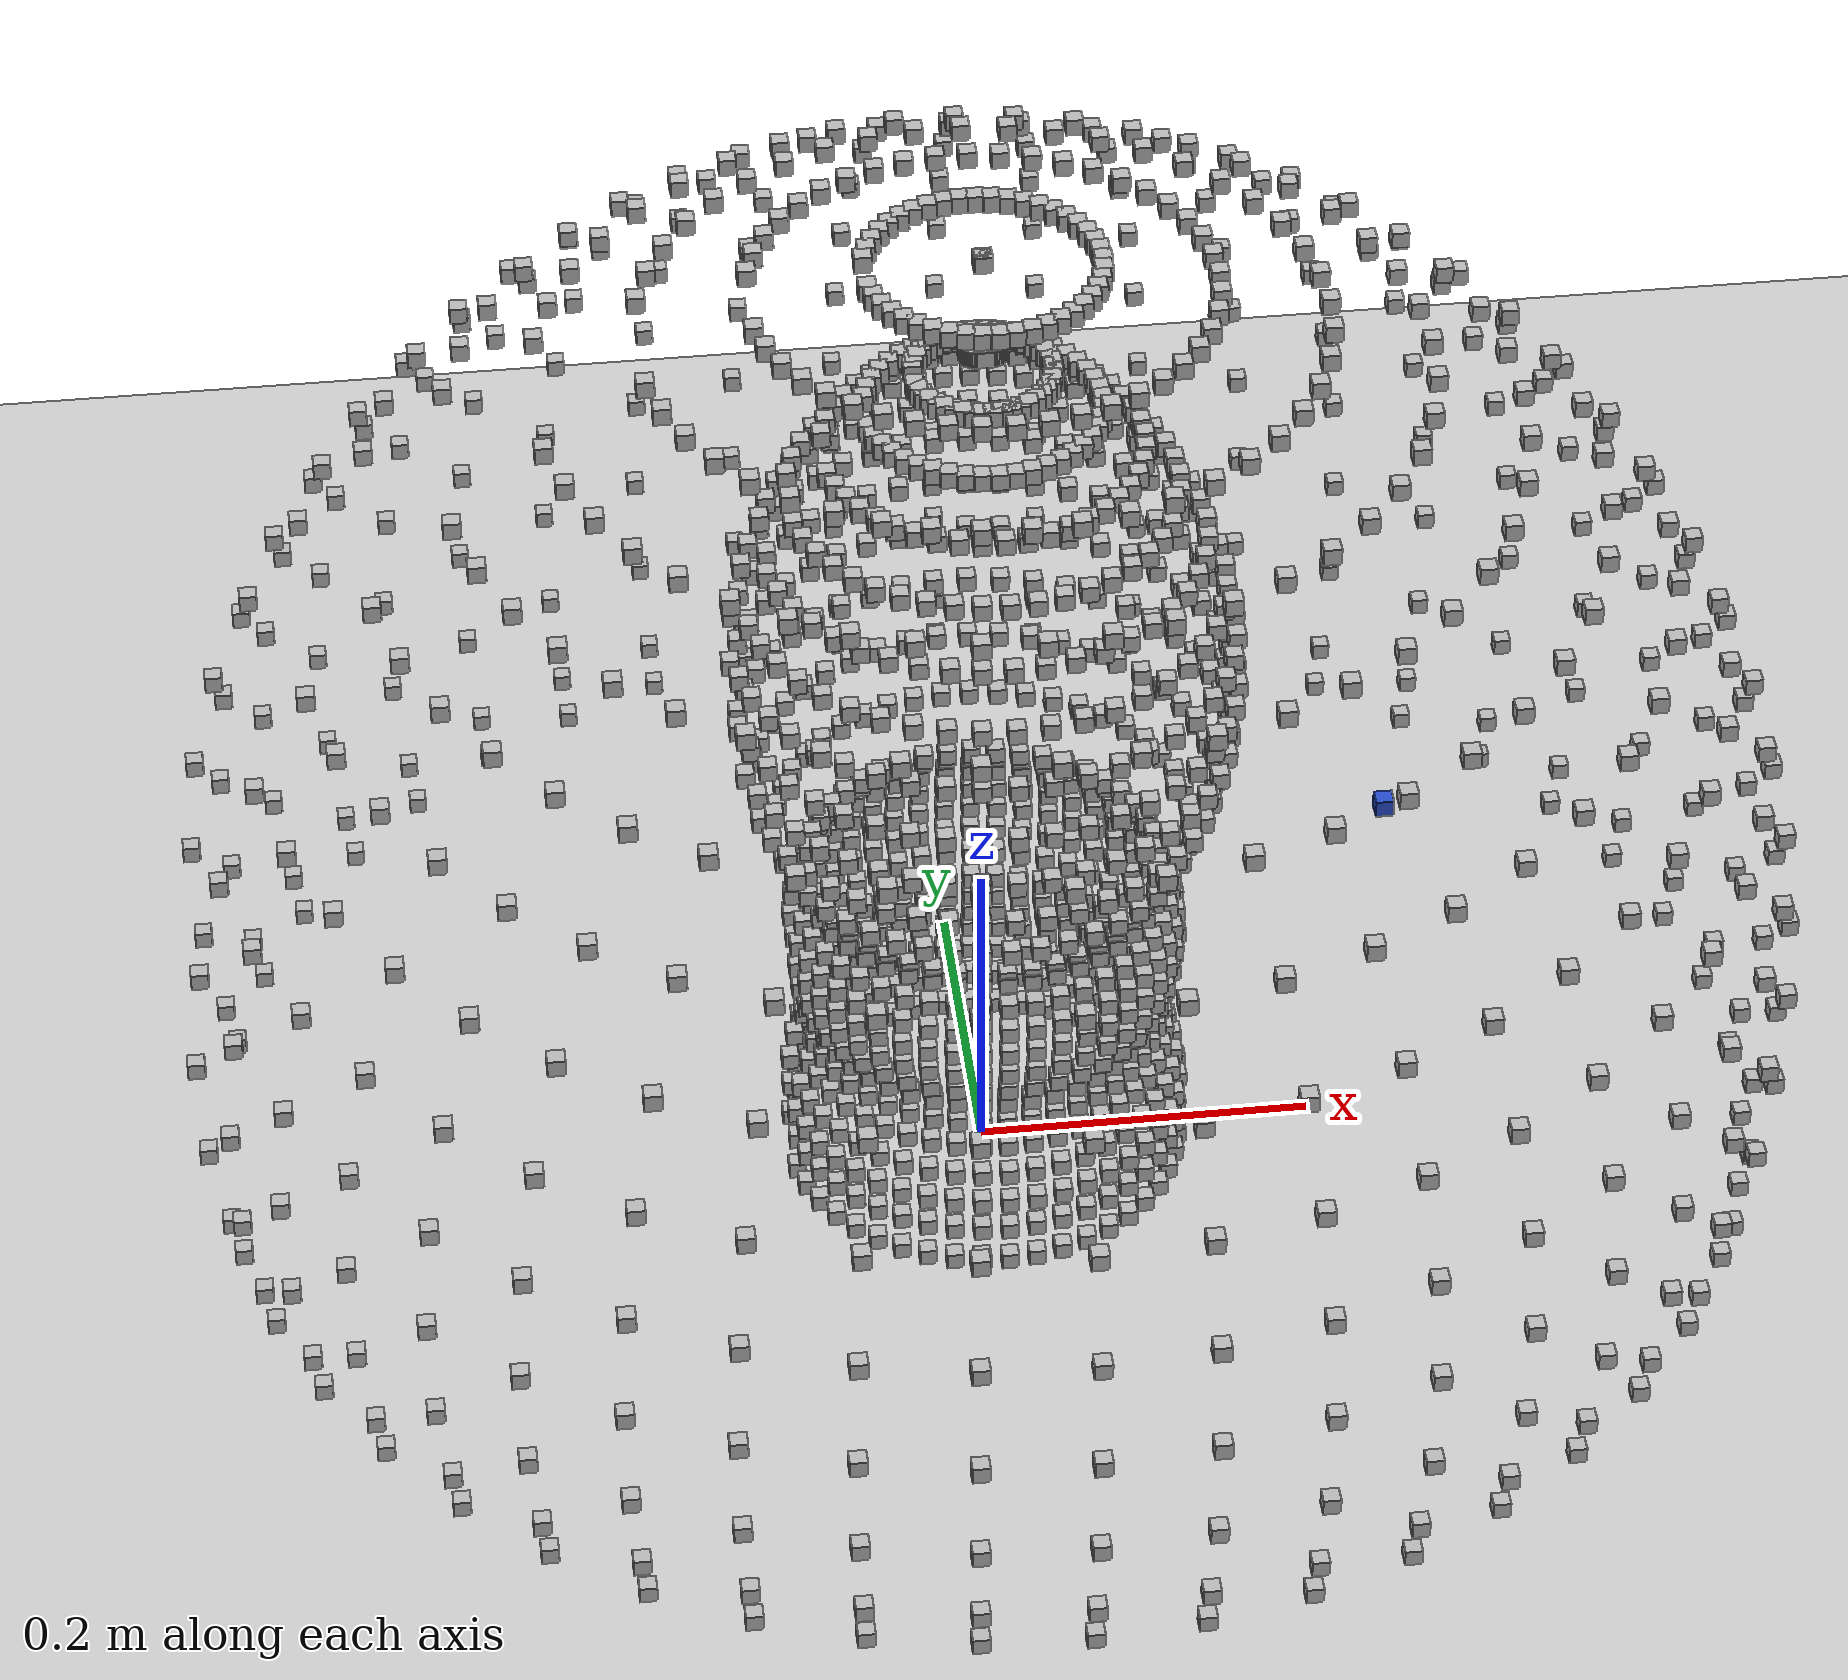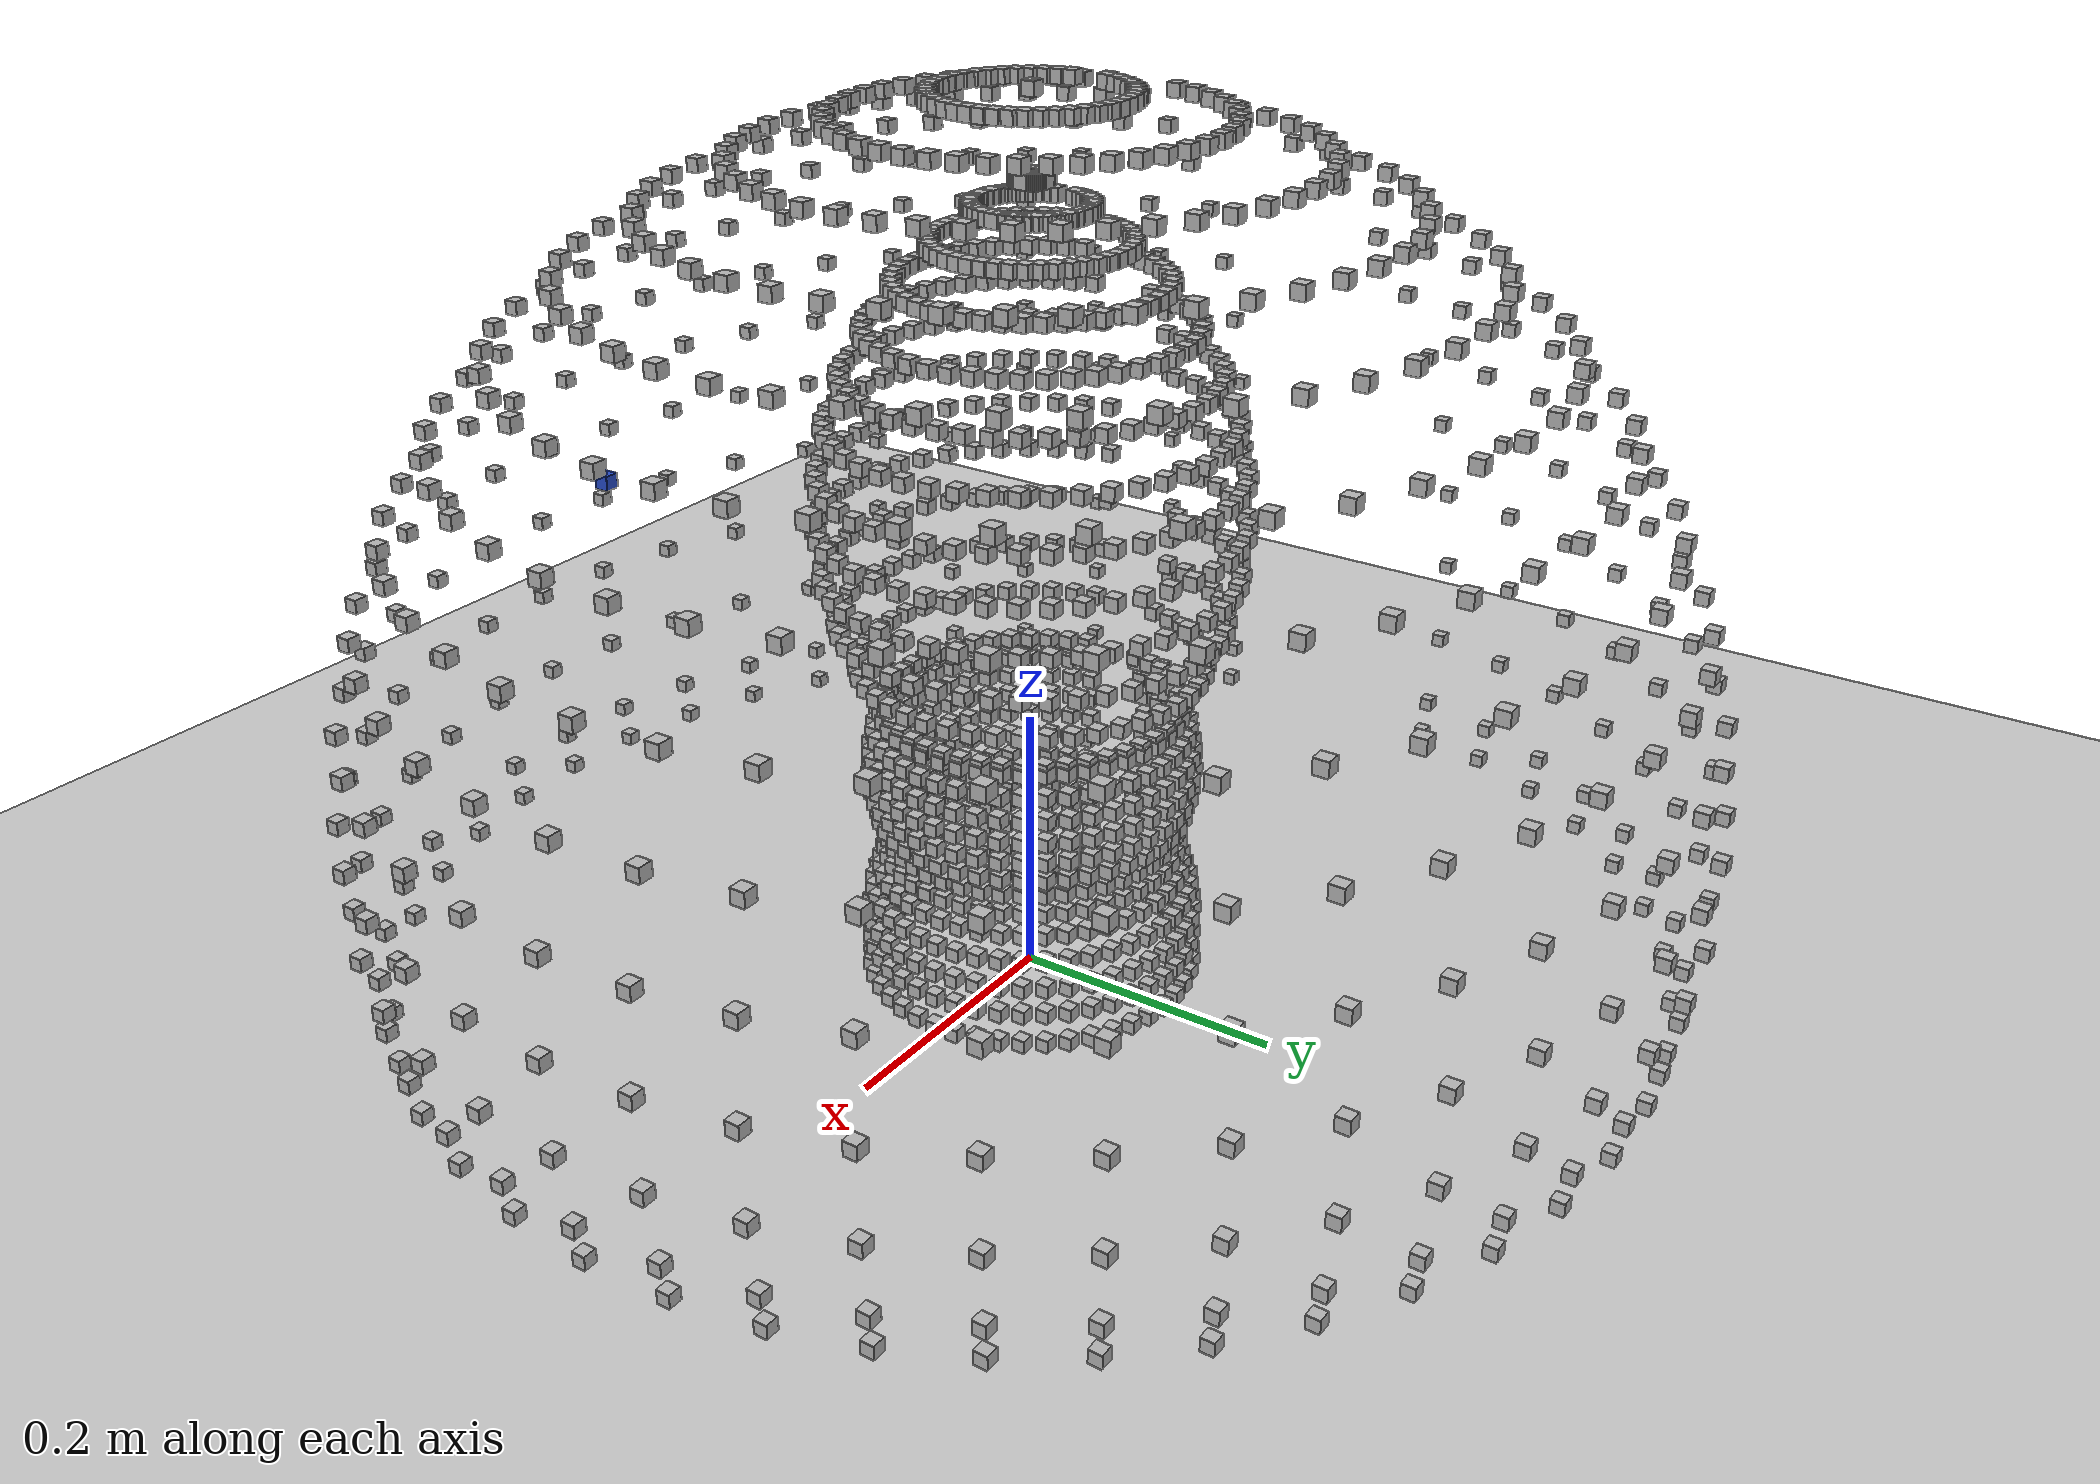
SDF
<sdf version="1.6">
 <world name="default">
  <light name="sun" type="directional">
   <pose>0 0 10 0 -0 0</pose>
   <diffuse>0.8 0.8 0.8 1</diffuse>
   <specular>0.2 0.2 0.2 1</specular>
   <attenuation>
    <range>1000</range>
    <constant>0.9</constant>
    <linear>0.01</linear>
    <quadratic>0.001</quadratic>
   </attenuation>
   <direction>-0.5 0.1 -0.9</direction>
  </light>
  <model name="ground_plane">
   <static>1</static>
   <link name="link">
    <collision name="collision">
     <geometry><plane><normal>0 0 1</normal><size>100 100</size></plane></geometry>
     <surface>
      <contact><collide_bitmask>65535</collide_bitmask></contact>
      <friction><ode><mu>100</mu><mu2>50</mu2></ode></friction>
     </surface>
    </collision>
    <visual name="visual">
     <cast_shadows>0</cast_shadows>
     <geometry><plane><normal>0 0 1</normal><size>100 100</size></plane></geometry>
     <material>
      <script><uri>file://media/materials/scripts/gazebo.material</uri><name>Gazebo/Grey</name></script>
     </material>
    </visual>
   </link>
  </model>
  <gravity>0 0 -9.8</gravity>
  <magnetic_field>6e-06 2.3e-05 -4.2e-05</magnetic_field>
  <atmosphere type="adiabatic"/>
  <physics name="default_physics" default="0" type="ode">
   <max_step_size>0.001</max_step_size>
   <real_time_factor>1</real_time_factor>
   <real_time_update_rate>1000</real_time_update_rate>
  </physics>
  <scene><ambient>0.4 0.4 0.4 1</ambient><background>0.7 0.7 0.7 1</background><shadows>1</shadows></scene>
  <audio><device>default</device></audio>
  <model name="cube_blue">
   <static>1</static>
   <pose>0.2 -0.2 0.4 0.0 0.0 0.0</pose>
   <mass>1</mass>
   <link name="link1">
    <visual name="visual">
     <cast_shadows>0</cast_shadows>
     <geometry><box><size>0.01 0.01 0.01</size></box></geometry>
     <material>
      <script><uri>file://media/materials/scripts/gazebo.material</uri><name>Gazebo/Blue</name></script>
     </material>
    </visual>
   </link>
  </model>
  <spherical_coordinates>
   <surface_model>EARTH_WGS84</surface_model>
   <latitude_deg>0</latitude_deg>
   <longitude_deg>0</longitude_deg>
   <elevation>0</elevation>
   <heading_deg>0</heading_deg>
  </spherical_coordinates>
  <model name="box_1685262135_6579912">
   <pose>-0.45127428790450397 -0.08771883558878132 0.031024085780011867 0.0 0.0 0.0</pose>
   <static>1</static>
   <link name="box_1685262135_6579912_link">
    <visual name="visual"><geometry><box><size>0.01 0.01 0.01</size></box></geometry></visual>
   </link>
  </model>
  <model name="box_1685262135_6580403">
   <pose>-0.4346744151944236 -0.14967040394197706 0.031024085780011867 0.0 0.0 0.0</pose>
   <static>1</static>
   <link name="box_1685262135_6580403_link">
    <visual name="visual"><geometry><box><size>0.01 0.01 0.01</size></box></geometry></visual>
   </link>
  </model>
  <model name="box_1685262135_6580632">
   <pose>-0.40961409942740284 -0.20870880813000314 0.031024085780011867 0.0 0.0 0.0</pose>
   <static>1</static>
   <link name="box_1685262135_6580632_link">
    <visual name="visual"><geometry><box><size>0.01 0.01 0.01</size></box></geometry></visual>
   </link>
  </model>
  <model name="box_1685262135_6580842">
   <pose>-0.3765811111441599 -0.26368493277052946 0.031024085780011867 0.0 0.0 0.0</pose>
   <static>1</static>
   <link name="box_1685262135_6580842_link">
    <visual name="visual"><geometry><box><size>0.01 0.01 0.01</size></box></geometry></visual>
   </link>
  </model>
  <model name="box_1685262135_6581023">
   <pose>-0.33621839988716096 -0.31352873013184274 0.031024085780011867 0.0 0.0 0.0</pose>
   <static>1</static>
   <link name="box_1685262135_6581023_link">
    <visual name="visual"><geometry><box><size>0.01 0.01 0.01</size></box></geometry></visual>
   </link>
  </model>
  <model name="box_1685262135_6581194">
   <pose>-0.28931157991911977 -0.3572700473947844 0.031024085780011867 0.0 0.0 0.0</pose>
   <static>1</static>
   <link name="box_1685262135_6581194_link">
    <visual name="visual"><geometry><box><size>0.01 0.01 0.01</size></box></geometry></visual>
   </link>
  </model>
  <model name="box_1685262135_6581366">
   <pose>-0.23677363913499763 -0.39405750957384217 0.031024085780011867 0.0 0.0 0.0</pose>
   <static>1</static>
   <link name="box_1685262135_6581366_link">
    <visual name="visual"><geometry><box><size>0.01 0.01 0.01</size></box></geometry></visual>
   </link>
  </model>
  <model name="box_1685262135_6581564">
   <pose>-0.17962716879113522 -0.42317509056281866 0.031024085780011867 0.0 0.0 0.0</pose>
   <static>1</static>
   <link name="box_1685262135_6581564_link">
    <visual name="visual"><geometry><box><size>0.01 0.01 0.01</size></box></geometry></visual>
   </link>
  </model>
  <model name="box_1685262135_6581733">
   <pose>-0.11898445992962965 -0.4440560497685209 0.031024085780011867 0.0 0.0 0.0</pose>
   <static>1</static>
   <link name="box_1685262135_6581733_link">
    <visual name="visual"><geometry><box><size>0.01 0.01 0.01</size></box></geometry></visual>
   </link>
  </model>
  <model name="box_1685262135_6581895">
   <pose>-0.05602585389841081 -0.4562939630717491 0.031024085780011867 0.0 0.0 0.0</pose>
   <static>1</static>
   <link name="box_1685262135_6581895_link">
    <visual name="visual"><geometry><box><size>0.01 0.01 0.01</size></box></geometry></visual>
   </link>
  </model>
  <model name="box_1685262135_6582057">
   <pose>0.00802323165047613 -0.45965063341047574 0.031024085780011867 0.0 0.0 0.0</pose>
   <static>1</static>
   <link name="box_1685262135_6582057_link">
    <visual name="visual"><geometry><box><size>0.01 0.01 0.01</size></box></geometry></visual>
   </link>
  </model>
  <model name="box_1685262135_6582217">
   <pose>0.0719161541215775 -0.4540607270147136 0.031024085780011867 0.0 0.0 0.0</pose>
   <static>1</static>
   <link name="box_1685262135_6582217_link">
    <visual name="visual"><geometry><box><size>0.01 0.01 0.01</size></box></geometry></visual>
   </link>
  </model>
  <model name="box_1685262135_658238">
   <pose>0.13440931045611512 -0.43963304505403183 0.031024085780011867 0.0 0.0 0.0</pose>
   <static>1</static>
   <link name="box_1685262135_658238_link">
    <visual name="visual"><geometry><box><size>0.01 0.01 0.01</size></box></geometry></visual>
   </link>
  </model>
  <model name="box_1685262135_6582541">
   <pose>0.19428634245094903 -0.4166484059465502 0.031024085780011867 0.0 0.0 0.0</pose>
   <static>1</static>
   <link name="box_1685262135_6582541_link">
    <visual name="visual"><geometry><box><size>0.01 0.01 0.01</size></box></geometry></visual>
   </link>
  </model>
  <model name="box_1685262135_6582701">
   <pose>0.25038181178741425 -0.38555417954785626 0.031024085780011867 0.0 0.0 0.0</pose>
   <static>1</static>
   <link name="box_1685262135_6582701_link">
    <visual name="visual"><geometry><box><size>0.01 0.01 0.01</size></box></geometry></visual>
   </link>
  </model>
  <model name="box_1685262135_6582887">
   <pose>0.301603883962527 -0.34695557960564244 0.031024085780011867 0.0 0.0 0.0</pose>
   <static>1</static>
   <link name="box_1685262135_6582887_link">
    <visual name="visual"><geometry><box><size>0.01 0.01 0.01</size></box></geometry></visual>
   </link>
  </model>
  <model name="box_1685262135_6583085">
   <pose>0.3469555796056425 -0.30160388396252696 0.031024085780011867 0.0 0.0 0.0</pose>
   <static>1</static>
   <link name="box_1685262135_6583085_link">
    <visual name="visual"><geometry><box><size>0.01 0.01 0.01</size></box></geometry></visual>
   </link>
  </model>
  <model name="box_1685262135_6583354">
   <pose>0.3855541795478563 -0.2503818117874142 0.031024085780011867 0.0 0.0 0.0</pose>
   <static>1</static>
   <link name="box_1685262135_6583354_link">
    <visual name="visual"><geometry><box><size>0.01 0.01 0.01</size></box></geometry></visual>
   </link>
  </model>
  <model name="box_1685262135_6583595">
   <pose>0.4166484059465502 -0.19428634245094903 0.031024085780011867 0.0 0.0 0.0</pose>
   <static>1</static>
   <link name="box_1685262135_6583595_link">
    <visual name="visual"><geometry><box><size>0.01 0.01 0.01</size></box></geometry></visual>
   </link>
  </model>
  <model name="box_1685262135_6583772">
   <pose>0.43963304505403183 -0.13440931045611512 0.031024085780011867 0.0 0.0 0.0</pose>
   <static>1</static>
   <link name="box_1685262135_6583772_link">
    <visual name="visual"><geometry><box><size>0.01 0.01 0.01</size></box></geometry></visual>
   </link>
  </model>
  <model name="box_1685262135_6583939">
   <pose>0.4540607270147136 -0.07191615412157747 0.031024085780011867 0.0 0.0 0.0</pose>
   <static>1</static>
   <link name="box_1685262135_6583939_link">
    <visual name="visual"><geometry><box><size>0.01 0.01 0.01</size></box></geometry></visual>
   </link>
  </model>
  <model name="box_1685262135_65841">
   <pose>0.45965063341047574 -0.008023231650476192 0.031024085780011867 0.0 0.0 0.0</pose>
   <static>1</static>
   <link name="box_1685262135_65841_link">
    <visual name="visual"><geometry><box><size>0.01 0.01 0.01</size></box></geometry></visual>
   </link>
  </model>
  <model name="box_1685262135_658426">
   <pose>0.456293963071749 0.05602585389841087 0.031024085780011867 0.0 0.0 0.0</pose>
   <static>1</static>
   <link name="box_1685262135_658426_link">
    <visual name="visual"><geometry><box><size>0.01 0.01 0.01</size></box></geometry></visual>
   </link>
  </model>
  <model name="box_1685262135_658442">
   <pose>0.4440560497685209 0.1189844599296296 0.031024085780011867 0.0 0.0 0.0</pose>
   <static>1</static>
   <link name="box_1685262135_658442_link">
    <visual name="visual"><geometry><box><size>0.01 0.01 0.01</size></box></geometry></visual>
   </link>
  </model>
  <model name="box_1685262135_658462">
   <pose>0.42317509056281866 0.17962716879113524 0.031024085780011867 0.0 0.0 0.0</pose>
   <static>1</static>
   <link name="box_1685262135_658462_link">
    <visual name="visual"><geometry><box><size>0.01 0.01 0.01</size></box></geometry></visual>
   </link>
  </model>
  <model name="box_1685262135_6584792">
   <pose>0.39405750957384217 0.23677363913499758 0.031024085780011867 0.0 0.0 0.0</pose>
   <static>1</static>
   <link name="box_1685262135_6584792_link">
    <visual name="visual"><geometry><box><size>0.01 0.01 0.01</size></box></geometry></visual>
   </link>
  </model>
  <model name="box_1685262135_6584957">
   <pose>0.3572700473947844 0.2893115799191198 0.031024085780011867 0.0 0.0 0.0</pose>
   <static>1</static>
   <link name="box_1685262135_6584957_link">
    <visual name="visual"><geometry><box><size>0.01 0.01 0.01</size></box></geometry></visual>
   </link>
  </model>
  <model name="box_1685262135_6585119">
   <pose>0.3135287301318427 0.33621839988716096 0.031024085780011867 0.0 0.0 0.0</pose>
   <static>1</static>
   <link name="box_1685262135_6585119_link">
    <visual name="visual"><geometry><box><size>0.01 0.01 0.01</size></box></geometry></visual>
   </link>
  </model>
  <model name="box_1685262135_6585283">
   <pose>0.2636849327705294 0.37658111114416 0.031024085780011867 0.0 0.0 0.0</pose>
   <static>1</static>
   <link name="box_1685262135_6585283_link">
    <visual name="visual"><geometry><box><size>0.01 0.01 0.01</size></box></geometry></visual>
   </link>
  </model>
  <model name="box_1685262135_6585443">
   <pose>0.20870880813000312 0.40961409942740284 0.031024085780011867 0.0 0.0 0.0</pose>
   <static>1</static>
   <link name="box_1685262135_6585443_link">
    <visual name="visual"><geometry><box><size>0.01 0.01 0.01</size></box></geometry></visual>
   </link>
  </model>
  <model name="box_1685262135_6585605">
   <pose>0.14967040394197695 0.4346744151944236 0.031024085780011867 0.0 0.0 0.0</pose>
   <static>1</static>
   <link name="box_1685262135_6585605_link">
    <visual name="visual"><geometry><box><size>0.01 0.01 0.01</size></box></geometry></visual>
   </link>
  </model>
  <model name="box_1685262135_6585765">
   <pose>0.0877188355887813 0.45127428790450397 0.031024085780011867 0.0 0.0 0.0</pose>
   <static>1</static>
   <link name="box_1685262135_6585765_link">
    <visual name="visual"><geometry><box><size>0.01 0.01 0.01</size></box></geometry></visual>
   </link>
  </model>
  <model name="box_1685262135_6585927">
   <pose>0.02405991987954663 0.4590906199174173 0.031024085780011867 0.0 0.0 0.0</pose>
   <static>1</static>
   <link name="box_1685262135_6585927_link">
    <visual name="visual"><geometry><box><size>0.01 0.01 0.01</size></box></geometry></visual>
   </link>
  </model>
  <model name="box_1685262135_6586115">
   <pose>-0.04006729480239029 0.4579712752214784 0.031024085780011867 0.0 0.0 0.0</pose>
   <static>1</static>
   <link name="box_1685262135_6586115_link">
    <visual name="visual"><geometry><box><size>0.01 0.01 0.01</size></box></geometry></visual>
   </link>
  </model>
  <model name="box_1685262135_6586287">
   <pose>-0.1034146451668708 0.44793804058795783 0.031024085780011867 0.0 0.0 0.0</pose>
   <static>1</static>
   <link name="box_1685262135_6586287_link">
    <visual name="visual"><geometry><box><size>0.01 0.01 0.01</size></box></geometry></visual>
   </link>
  </model>
  <model name="box_1685262135_6586452">
   <pose>-0.16474914709559374 0.42918620151636183 0.031024085780011867 0.0 0.0 0.0</pose>
   <static>1</static>
   <link name="box_1685262135_6586452_link">
    <visual name="visual"><geometry><box><size>0.01 0.01 0.01</size></box></geometry></visual>
   </link>
  </model>
  <model name="box_1685262135_6586614">
   <pose>-0.2228769942754781 0.40208074122431836 0.031024085780011867 0.0 0.0 0.0</pose>
   <static>1</static>
   <link name="box_1685262135_6586614_link">
    <visual name="visual"><geometry><box><size>0.01 0.01 0.01</size></box></geometry></visual>
   </link>
  </model>
  <model name="box_1685262135_6586773">
   <pose>-0.2766667942806138 0.3671492366644077 0.031024085780011867 0.0 0.0 0.0</pose>
   <static>1</static>
   <link name="box_1685262135_6586773_link">
    <visual name="visual"><geometry><box><size>0.01 0.01 0.01</size></box></geometry></visual>
   </link>
  </model>
  <model name="box_1685262135_658693">
   <pose>-0.3250715898388913 0.3250715898388913 0.031024085780011867 0.0 0.0 0.0</pose>
   <static>1</static>
   <link name="box_1685262135_658693_link">
    <visual name="visual"><geometry><box><size>0.01 0.01 0.01</size></box></geometry></visual>
   </link>
  </model>
  <model name="box_1685262135_6587093">
   <pose>-0.3671492366644078 0.2766667942806137 0.031024085780011867 0.0 0.0 0.0</pose>
   <static>1</static>
   <link name="box_1685262135_6587093_link">
    <visual name="visual"><geometry><box><size>0.01 0.01 0.01</size></box></geometry></visual>
   </link>
  </model>
  <model name="box_1685262135_658725">
   <pose>-0.4020807412243183 0.2228769942754782 0.031024085780011867 0.0 0.0 0.0</pose>
   <static>1</static>
   <link name="box_1685262135_658725_link">
    <visual name="visual"><geometry><box><size>0.01 0.01 0.01</size></box></geometry></visual>
   </link>
  </model>
  <model name="box_1685262135_6587431">
   <pose>-0.42918620151636183 0.1647491470955937 0.031024085780011867 0.0 0.0 0.0</pose>
   <static>1</static>
   <link name="box_1685262135_6587431_link">
    <visual name="visual"><geometry><box><size>0.01 0.01 0.01</size></box></geometry></visual>
   </link>
  </model>
  <model name="box_1685262135_6587594">
   <pose>-0.44793804058795783 0.1034146451668708 0.031024085780011867 0.0 0.0 0.0</pose>
   <static>1</static>
   <link name="box_1685262135_6587594_link">
    <visual name="visual"><geometry><box><size>0.01 0.01 0.01</size></box></geometry></visual>
   </link>
  </model>
  <model name="box_1685262135_6587758">
   <pose>-0.45670058291203247 -0.08877360048981717 0.05746253559996678 0.0 0.0 0.0</pose>
   <static>1</static>
   <link name="box_1685262135_6587758_link">
    <visual name="visual"><geometry><box><size>0.01 0.01 0.01</size></box></geometry></visual>
   </link>
  </model>
  <model name="box_1685262135_6587918">
   <pose>-0.43990110696988993 -0.1514700982464241 0.05746253559996678 0.0 0.0 0.0</pose>
   <static>1</static>
   <link name="box_1685262135_6587918_link">
    <visual name="visual"><geometry><box><size>0.01 0.01 0.01</size></box></geometry></visual>
   </link>
  </model>
  <model name="box_1685262135_658808">
   <pose>-0.41453945636067124 -0.2112184028353472 0.05746253559996678 0.0 0.0 0.0</pose>
   <static>1</static>
   <link name="box_1685262135_658808_link">
    <visual name="visual"><geometry><box><size>0.01 0.01 0.01</size></box></geometry></visual>
   </link>
  </model>
  <model name="box_1685262135_6588275">
   <pose>-0.38110926676503476 -0.26685558147045274 0.05746253559996678 0.0 0.0 0.0</pose>
   <static>1</static>
   <link name="box_1685262135_6588275_link">
    <visual name="visual"><geometry><box><size>0.01 0.01 0.01</size></box></geometry></visual>
   </link>
  </model>
  <model name="box_1685262135_6588542">
   <pose>-0.3402612187971827 -0.31729871975596063 0.05746253559996678 0.0 0.0 0.0</pose>
   <static>1</static>
   <link name="box_1685262135_6588542_link">
    <visual name="visual"><geometry><box><size>0.01 0.01 0.01</size></box></geometry></visual>
   </link>
  </model>
  <model name="box_1685262135_658877">
   <pose>-0.29279037324684315 -0.36156599938336315 0.05746253559996678 0.0 0.0 0.0</pose>
   <static>1</static>
   <link name="box_1685262135_658877_link">
    <visual name="visual"><geometry><box><size>0.01 0.01 0.01</size></box></geometry></visual>
   </link>
  </model>
  <model name="box_1685262135_658894">
   <pose>-0.23962069612536724 -0.3987958081079969 0.05746253559996678 0.0 0.0 0.0</pose>
   <static>1</static>
   <link name="box_1685262135_658894_link">
    <visual name="visual"><geometry><box><size>0.01 0.01 0.01</size></box></geometry></visual>
   </link>
  </model>
  <model name="box_1685262135_6589131">
   <pose>-0.18178707471831287 -0.4282635100513169 0.05746253559996678 0.0 0.0 0.0</pose>
   <static>1</static>
   <link name="box_1685262135_6589131_link">
    <visual name="visual"><geometry><box><size>0.01 0.01 0.01</size></box></geometry></visual>
   </link>
  </model>
  <model name="box_1685262135_6589296">
   <pose>-0.12041517468159942 -0.4493955499140104 0.05746253559996678 0.0 0.0 0.0</pose>
   <static>1</static>
   <link name="box_1685262135_6589296_link">
    <visual name="visual"><geometry><box><size>0.01 0.01 0.01</size></box></geometry></visual>
   </link>
  </model>
  <model name="box_1685262135_658946">
   <pose>-0.0566995302399395 -0.4617806165774892 0.05746253559996678 0.0 0.0 0.0</pose>
   <static>1</static>
   <link name="box_1685262135_658946_link">
    <visual name="visual"><geometry><box><size>0.01 0.01 0.01</size></box></geometry></visual>
   </link>
  </model>
  <model name="box_1685262135_6589622">
   <pose>0.0081197060630809 -0.46517764880695317 0.05746253559996678 0.0 0.0 0.0</pose>
   <static>1</static>
   <link name="box_1685262135_6589622_link">
    <visual name="visual"><geometry><box><size>0.01 0.01 0.01</size></box></geometry></visual>
   </link>
  </model>
  <model name="box_1685262135_6589782">
   <pose>0.07278090152361238 -0.45952052723412273 0.05746253559996678 0.0 0.0 0.0</pose>
   <static>1</static>
   <link name="box_1685262135_6589782_link">
    <visual name="visual"><geometry><box><size>0.01 0.01 0.01</size></box></geometry></visual>
   </link>
  </model>
  <model name="box_1685262135_6589944">
   <pose>0.1360254995230351 -0.44491936129553256 0.05746253559996678 0.0 0.0 0.0</pose>
   <static>1</static>
   <link name="box_1685262135_6589944_link">
    <visual name="visual"><geometry><box><size>0.01 0.01 0.01</size></box></geometry></visual>
   </link>
  </model>
  <model name="box_1685262135_6590106">
   <pose>0.19662251590095434 -0.42165834607759733 0.05746253559996678 0.0 0.0 0.0</pose>
   <static>1</static>
   <link name="box_1685262135_6590106_link">
    <visual name="visual"><geometry><box><size>0.01 0.01 0.01</size></box></geometry></visual>
   </link>
  </model>
  <model name="box_1685262135_6590264">
   <pose>0.25339249866165847 -0.39019023078252135 0.05746253559996678 0.0 0.0 0.0</pose>
   <static>1</static>
   <link name="box_1685262135_6590264_link">
    <visual name="visual"><geometry><box><size>0.01 0.01 0.01</size></box></geometry></visual>
   </link>
  </model>
  <model name="box_1685262135_659043">
   <pose>0.30523048466560854 -0.35112750648007285 0.05746253559996678 0.0 0.0 0.0</pose>
   <static>1</static>
   <link name="box_1685262135_659043_link">
    <visual name="visual"><geometry><box><size>0.01 0.01 0.01</size></box></geometry></visual>
   </link>
  </model>
  <model name="box_1685262135_6590617">
   <pose>0.3511275064800729 -0.3052304846656085 0.05746253559996678 0.0 0.0 0.0</pose>
   <static>1</static>
   <link name="box_1685262135_6590617_link">
    <visual name="visual"><geometry><box><size>0.01 0.01 0.01</size></box></geometry></visual>
   </link>
  </model>
  <model name="box_1685262135_6590786">
   <pose>0.3901902307825214 -0.2533924986616584 0.05746253559996678 0.0 0.0 0.0</pose>
   <static>1</static>
   <link name="box_1685262135_6590786_link">
    <visual name="visual"><geometry><box><size>0.01 0.01 0.01</size></box></geometry></visual>
   </link>
  </model>
  <model name="box_1685262135_659095">
   <pose>0.42165834607759733 -0.19662251590095434 0.05746253559996678 0.0 0.0 0.0</pose>
   <static>1</static>
   <link name="box_1685262135_659095_link">
    <visual name="visual"><geometry><box><size>0.01 0.01 0.01</size></box></geometry></visual>
   </link>
  </model>
  <model name="box_1685262135_6591113">
   <pose>0.44491936129553256 -0.1360254995230351 0.05746253559996678 0.0 0.0 0.0</pose>
   <static>1</static>
   <link name="box_1685262135_6591113_link">
    <visual name="visual"><geometry><box><size>0.01 0.01 0.01</size></box></geometry></visual>
   </link>
  </model>
  <model name="box_1685262135_6591275">
   <pose>0.45952052723412273 -0.07278090152361237 0.05746253559996678 0.0 0.0 0.0</pose>
   <static>1</static>
   <link name="box_1685262135_6591275_link">
    <visual name="visual"><geometry><box><size>0.01 0.01 0.01</size></box></geometry></visual>
   </link>
  </model>
  <model name="box_1685262135_6591437">
   <pose>0.46517764880695317 -0.008119706063080965 0.05746253559996678 0.0 0.0 0.0</pose>
   <static>1</static>
   <link name="box_1685262135_6591437_link">
    <visual name="visual"><geometry><box><size>0.01 0.01 0.01</size></box></geometry></visual>
   </link>
  </model>
  <model name="box_1685262135_6591601">
   <pose>0.46178061657748914 0.05669953023993955 0.05746253559996678 0.0 0.0 0.0</pose>
   <static>1</static>
   <link name="box_1685262135_6591601_link">
    <visual name="visual"><geometry><box><size>0.01 0.01 0.01</size></box></geometry></visual>
   </link>
  </model>
  <model name="box_1685262135_659176">
   <pose>0.4493955499140104 0.12041517468159936 0.05746253559996678 0.0 0.0 0.0</pose>
   <static>1</static>
   <link name="box_1685262135_659176_link">
    <visual name="visual"><geometry><box><size>0.01 0.01 0.01</size></box></geometry></visual>
   </link>
  </model>
  <model name="box_1685262135_6591945">
   <pose>0.4282635100513169 0.18178707471831293 0.05746253559996678 0.0 0.0 0.0</pose>
   <static>1</static>
   <link name="box_1685262135_6591945_link">
    <visual name="visual"><geometry><box><size>0.01 0.01 0.01</size></box></geometry></visual>
   </link>
  </model>
  <model name="box_1685262135_659211">
   <pose>0.3987958081079969 0.2396206961253672 0.05746253559996678 0.0 0.0 0.0</pose>
   <static>1</static>
   <link name="box_1685262135_659211_link">
    <visual name="visual"><geometry><box><size>0.01 0.01 0.01</size></box></geometry></visual>
   </link>
  </model>
  <model name="box_1685262135_6592274">
   <pose>0.3615659993833631 0.2927903732468432 0.05746253559996678 0.0 0.0 0.0</pose>
   <static>1</static>
   <link name="box_1685262135_6592274_link">
    <visual name="visual"><geometry><box><size>0.01 0.01 0.01</size></box></geometry></visual>
   </link>
  </model>
  <model name="box_1685262135_6592438">
   <pose>0.3172987197559606 0.3402612187971827 0.05746253559996678 0.0 0.0 0.0</pose>
   <static>1</static>
   <link name="box_1685262135_6592438_link">
    <visual name="visual"><geometry><box><size>0.01 0.01 0.01</size></box></geometry></visual>
   </link>
  </model>
  <model name="box_1685262135_6592607">
   <pose>0.26685558147045263 0.38110926676503487 0.05746253559996678 0.0 0.0 0.0</pose>
   <static>1</static>
   <link name="box_1685262135_6592607_link">
    <visual name="visual"><geometry><box><size>0.01 0.01 0.01</size></box></geometry></visual>
   </link>
  </model>
  <model name="box_1685262135_6592772">
   <pose>0.21121840283534718 0.41453945636067124 0.05746253559996678 0.0 0.0 0.0</pose>
   <static>1</static>
   <link name="box_1685262135_6592772_link">
    <visual name="visual"><geometry><box><size>0.01 0.01 0.01</size></box></geometry></visual>
   </link>
  </model>
  <model name="box_1685262135_659294">
   <pose>0.15147009824642396 0.43990110696988993 0.05746253559996678 0.0 0.0 0.0</pose>
   <static>1</static>
   <link name="box_1685262135_659294_link">
    <visual name="visual"><geometry><box><size>0.01 0.01 0.01</size></box></geometry></visual>
   </link>
  </model>
  <model name="box_1685262135_6593113">
   <pose>0.08877360048981715 0.45670058291203247 0.05746253559996678 0.0 0.0 0.0</pose>
   <static>1</static>
   <link name="box_1685262135_6593113_link">
    <visual name="visual"><geometry><box><size>0.01 0.01 0.01</size></box></geometry></visual>
   </link>
  </model>
  <model name="box_1685262135_6593375">
   <pose>0.02434922557814993 0.46461090149700557 0.05746253559996678 0.0 0.0 0.0</pose>
   <static>1</static>
   <link name="box_1685262135_6593375_link">
    <visual name="visual"><geometry><box><size>0.01 0.01 0.01</size></box></geometry></visual>
   </link>
  </model>
  <model name="box_1685262135_659364">
   <pose>-0.0405490793125625 0.463478097371407 0.05746253559996678 0.0 0.0 0.0</pose>
   <static>1</static>
   <link name="box_1685262135_659364_link">
    <visual name="visual"><geometry><box><size>0.01 0.01 0.01</size></box></geometry></visual>
   </link>
  </model>
  <model name="box_1685262135_6593828">
   <pose>-0.10465814249834977 0.4533242192789957 0.05746253559996678 0.0 0.0 0.0</pose>
   <static>1</static>
   <link name="box_1685262135_6593828_link">
    <visual name="visual"><geometry><box><size>0.01 0.01 0.01</size></box></geometry></visual>
   </link>
  </model>
  <model name="box_1685262135_6593995">
   <pose>-0.1667301539872795 0.4343469009069754 0.05746253559996678 0.0 0.0 0.0</pose>
   <static>1</static>
   <link name="box_1685262135_6593995_link">
    <visual name="visual"><geometry><box><size>0.01 0.01 0.01</size></box></geometry></visual>
   </link>
  </model>
  <model name="box_1685262135_6594152">
   <pose>-0.2255569526815859 0.4069155141710779 0.05746253559996678 0.0 0.0 0.0</pose>
   <static>1</static>
   <link name="box_1685262135_6594152_link">
    <visual name="visual"><geometry><box><size>0.01 0.01 0.01</size></box></geometry></visual>
   </link>
  </model>
  <model name="box_1685262135_6594312">
   <pose>-0.27999354185917624 0.37156397981137723 0.05746253559996678 0.0 0.0 0.0</pose>
   <static>1</static>
   <link name="box_1685262135_6594312_link">
    <visual name="visual"><geometry><box><size>0.01 0.01 0.01</size></box></geometry></visual>
   </link>
  </model>
  <model name="box_1685262135_6594467">
   <pose>-0.32898037523241097 0.328980375232411 0.05746253559996678 0.0 0.0 0.0</pose>
   <static>1</static>
   <link name="box_1685262135_6594467_link">
    <visual name="visual"><geometry><box><size>0.01 0.01 0.01</size></box></geometry></visual>
   </link>
  </model>
  <model name="box_1685262135_6594627">
   <pose>-0.37156397981137734 0.2799935418591762 0.05746253559996678 0.0 0.0 0.0</pose>
   <static>1</static>
   <link name="box_1685262135_6594627_link">
    <visual name="visual"><geometry><box><size>0.01 0.01 0.01</size></box></geometry></visual>
   </link>
  </model>
  <model name="box_1685262135_6594782">
   <pose>-0.40691551417107785 0.225556952681586 0.05746253559996678 0.0 0.0 0.0</pose>
   <static>1</static>
   <link name="box_1685262135_6594782_link">
    <visual name="visual"><geometry><box><size>0.01 0.01 0.01</size></box></geometry></visual>
   </link>
  </model>
  <model name="box_1685262135_6594946">
   <pose>-0.4343469009069754 0.16673015398727947 0.05746253559996678 0.0 0.0 0.0</pose>
   <static>1</static>
   <link name="box_1685262135_6594946_link">
    <visual name="visual"><geometry><box><size>0.01 0.01 0.01</size></box></geometry></visual>
   </link>
  </model>
  <model name="box_1685262135_6595125">
   <pose>-0.4533242192789957 0.10465814249834976 0.05746253559996678 0.0 0.0 0.0</pose>
   <static>1</static>
   <link name="box_1685262135_6595125_link">
    <visual name="visual"><geometry><box><size>0.01 0.01 0.01</size></box></geometry></visual>
   </link>
  </model>
  <model name="box_1685262135_6595292">
   <pose>-0.46630560172722674 -0.09064062701638824 0.11486971929344875 0.0 0.0 0.0</pose>
   <static>1</static>
   <link name="box_1685262135_6595292_link">
    <visual name="visual"><geometry><box><size>0.01 0.01 0.01</size></box></geometry></visual>
   </link>
  </model>
  <model name="box_1685262135_6595452">
   <pose>-0.44915281053096123 -0.1546557152524713 0.11486971929344875 0.0 0.0 0.0</pose>
   <static>1</static>
   <link name="box_1685262135_6595452_link">
    <visual name="visual"><geometry><box><size>0.01 0.01 0.01</size></box></geometry></visual>
   </link>
  </model>
  <model name="box_1685262135_6595607">
   <pose>-0.4232577707814601 -0.21566060590943342 0.11486971929344875 0.0 0.0 0.0</pose>
   <static>1</static>
   <link name="box_1685262135_6595607_link">
    <visual name="visual"><geometry><box><size>0.01 0.01 0.01</size></box></geometry></visual>
   </link>
  </model>
  <model name="box_1685262135_6595767">
   <pose>-0.3891244999722762 -0.272467908182672 0.11486971929344875 0.0 0.0 0.0</pose>
   <static>1</static>
   <link name="box_1685262135_6595767_link">
    <visual name="visual"><geometry><box><size>0.01 0.01 0.01</size></box></geometry></visual>
   </link>
  </model>
  <model name="box_1685262135_6595922">
   <pose>-0.34741736339369045 -0.32397193255078666 0.11486971929344875 0.0 0.0 0.0</pose>
   <static>1</static>
   <link name="box_1685262135_6595922_link">
    <visual name="visual"><geometry><box><size>0.01 0.01 0.01</size></box></geometry></visual>
   </link>
  </model>
  <model name="box_1685262135_6596084">
   <pose>-0.29894814301803996 -0.3691702117644116 0.11486971929344875 0.0 0.0 0.0</pose>
   <static>1</static>
   <link name="box_1685262135_6596084_link">
    <visual name="visual"><geometry><box><size>0.01 0.01 0.01</size></box></geometry></visual>
   </link>
  </model>
  <model name="box_1685262135_659624">
   <pose>-0.24466023708701612 -0.40718301273093416 0.11486971929344875 0.0 0.0 0.0</pose>
   <static>1</static>
   <link name="box_1685262135_659624_link">
    <visual name="visual"><geometry><box><size>0.01 0.01 0.01</size></box></geometry></visual>
   </link>
  </model>
  <model name="box_1685262135_6596403">
   <pose>-0.18561029793798817 -0.4372704595184613 0.11486971929344875 0.0 0.0 0.0</pose>
   <static>1</static>
   <link name="box_1685262135_6596403_link">
    <visual name="visual"><geometry><box><size>0.01 0.01 0.01</size></box></geometry></visual>
   </link>
  </model>
  <model name="box_1685262135_6596584">
   <pose>-0.12294766546818212 -0.45884693419923706 0.11486971929344875 0.0 0.0 0.0</pose>
   <static>1</static>
   <link name="box_1685262135_6596584_link">
    <visual name="visual"><geometry><box><size>0.01 0.01 0.01</size></box></geometry></visual>
   </link>
  </model>
  <model name="box_1685262135_6596751">
   <pose>-0.05789199654093433 -0.4714924752364766 0.11486971929344875 0.0 0.0 0.0</pose>
   <static>1</static>
   <link name="box_1685262135_6596751_link">
    <visual name="visual"><geometry><box><size>0.01 0.01 0.01</size></box></geometry></visual>
   </link>
  </model>
  <model name="box_1685262135_6596909">
   <pose>0.008290474247812474 -0.4749609515579795 0.11486971929344875 0.0 0.0 0.0</pose>
   <static>1</static>
   <link name="box_1685262135_6596909_link">
    <visual name="visual"><geometry><box><size>0.01 0.01 0.01</size></box></geometry></visual>
   </link>
  </model>
  <model name="box_1685262135_6597068">
   <pose>0.07431158038560051 -0.46918485321748127 0.11486971929344875 0.0 0.0 0.0</pose>
   <static>1</static>
   <link name="box_1685262135_6597068_link">
    <visual name="visual"><geometry><box><size>0.01 0.01 0.01</size></box></geometry></visual>
   </link>
  </model>
  <model name="box_1685262135_6597228">
   <pose>0.13888629613935258 -0.4542766053989651 0.11486971929344875 0.0 0.0 0.0</pose>
   <static>1</static>
   <link name="box_1685262135_6597228_link">
    <visual name="visual"><geometry><box><size>0.01 0.01 0.01</size></box></geometry></visual>
   </link>
  </model>
  <model name="box_1685262135_6597385">
   <pose>0.20075774811957245 -0.43052638018833794 0.11486971929344875 0.0 0.0 0.0</pose>
   <static>1</static>
   <link name="box_1685262135_6597385_link">
    <visual name="visual"><geometry><box><size>0.01 0.01 0.01</size></box></geometry></visual>
   </link>
  </model>
  <model name="box_1685262135_6597545">
   <pose>0.25872167889119874 -0.3983964487038438 0.11486971929344875 0.0 0.0 0.0</pose>
   <static>1</static>
   <link name="box_1685262135_6597545_link">
    <visual name="visual"><geometry><box><size>0.01 0.01 0.01</size></box></geometry></visual>
   </link>
  </model>
  <model name="box_1685262135_659771">
   <pose>0.3116498864747556 -0.3585121835145731 0.11486971929344875 0.0 0.0 0.0</pose>
   <static>1</static>
   <link name="box_1685262135_659771_link">
    <visual name="visual"><geometry><box><size>0.01 0.01 0.01</size></box></geometry></visual>
   </link>
  </model>
  <model name="box_1685262135_6597893">
   <pose>0.35851218351457315 -0.31164988647475556 0.11486971929344875 0.0 0.0 0.0</pose>
   <static>1</static>
   <link name="box_1685262135_6597893_link">
    <visual name="visual"><geometry><box><size>0.01 0.01 0.01</size></box></geometry></visual>
   </link>
  </model>
  <model name="box_1685262135_6598065">
   <pose>0.39839644870384383 -0.2587216788911987 0.11486971929344875 0.0 0.0 0.0</pose>
   <static>1</static>
   <link name="box_1685262135_6598065_link">
    <visual name="visual"><geometry><box><size>0.01 0.01 0.01</size></box></geometry></visual>
   </link>
  </model>
  <model name="box_1685262135_6598299">
   <pose>0.43052638018833794 -0.20075774811957245 0.11486971929344875 0.0 0.0 0.0</pose>
   <static>1</static>
   <link name="box_1685262135_6598299_link">
    <visual name="visual"><geometry><box><size>0.01 0.01 0.01</size></box></geometry></visual>
   </link>
  </model>
  <model name="box_1685262135_6598554">
   <pose>0.4542766053989651 -0.13888629613935258 0.11486971929344875 0.0 0.0 0.0</pose>
   <static>1</static>
   <link name="box_1685262135_6598554_link">
    <visual name="visual"><geometry><box><size>0.01 0.01 0.01</size></box></geometry></visual>
   </link>
  </model>
  <model name="box_1685262135_6598735">
   <pose>0.46918485321748127 -0.07431158038560048 0.11486971929344875 0.0 0.0 0.0</pose>
   <static>1</static>
   <link name="box_1685262135_6598735_link">
    <visual name="visual"><geometry><box><size>0.01 0.01 0.01</size></box></geometry></visual>
   </link>
  </model>
  <model name="box_1685262135_65989">
   <pose>0.4749609515579795 -0.008290474247812539 0.11486971929344875 0.0 0.0 0.0</pose>
   <static>1</static>
   <link name="box_1685262135_65989_link">
    <visual name="visual"><geometry><box><size>0.01 0.01 0.01</size></box></geometry></visual>
   </link>
  </model>
  <model name="box_1685262135_659906">
   <pose>0.4714924752364765 0.05789199654093439 0.11486971929344875 0.0 0.0 0.0</pose>
   <static>1</static>
   <link name="box_1685262135_659906_link">
    <visual name="visual"><geometry><box><size>0.01 0.01 0.01</size></box></geometry></visual>
   </link>
  </model>
  <model name="box_1685262135_6599216">
   <pose>0.45884693419923706 0.12294766546818206 0.11486971929344875 0.0 0.0 0.0</pose>
   <static>1</static>
   <link name="box_1685262135_6599216_link">
    <visual name="visual"><geometry><box><size>0.01 0.01 0.01</size></box></geometry></visual>
   </link>
  </model>
  <model name="box_1685262135_6599376">
   <pose>0.4372704595184613 0.18561029793798822 0.11486971929344875 0.0 0.0 0.0</pose>
   <static>1</static>
   <link name="box_1685262135_6599376_link">
    <visual name="visual"><geometry><box><size>0.01 0.01 0.01</size></box></geometry></visual>
   </link>
  </model>
  <model name="box_1685262135_659956">
   <pose>0.40718301273093416 0.24466023708701606 0.11486971929344875 0.0 0.0 0.0</pose>
   <static>1</static>
   <link name="box_1685262135_659956_link">
    <visual name="visual"><geometry><box><size>0.01 0.01 0.01</size></box></geometry></visual>
   </link>
  </model>
  <model name="box_1685262135_6599734">
   <pose>0.36917021176441156 0.29894814301804 0.11486971929344875 0.0 0.0 0.0</pose>
   <static>1</static>
   <link name="box_1685262135_6599734_link">
    <visual name="visual"><geometry><box><size>0.01 0.01 0.01</size></box></geometry></visual>
   </link>
  </model>
  <model name="box_1685262135_6599896">
   <pose>0.3239719325507866 0.34741736339369045 0.11486971929344875 0.0 0.0 0.0</pose>
   <static>1</static>
   <link name="box_1685262135_6599896_link">
    <visual name="visual"><geometry><box><size>0.01 0.01 0.01</size></box></geometry></visual>
   </link>
  </model>
  <model name="box_1685262135_6600053">
   <pose>0.2724679081826719 0.3891244999722763 0.11486971929344875 0.0 0.0 0.0</pose>
   <static>1</static>
   <link name="box_1685262135_6600053_link">
    <visual name="visual"><geometry><box><size>0.01 0.01 0.01</size></box></geometry></visual>
   </link>
  </model>
  <model name="box_1685262135_6600213">
   <pose>0.2156606059094334 0.4232577707814601 0.11486971929344875 0.0 0.0 0.0</pose>
   <static>1</static>
   <link name="box_1685262135_6600213_link">
    <visual name="visual"><geometry><box><size>0.01 0.01 0.01</size></box></geometry></visual>
   </link>
  </model>
  <model name="box_1685262135_660037">
   <pose>0.15465571525247115 0.44915281053096123 0.11486971929344875 0.0 0.0 0.0</pose>
   <static>1</static>
   <link name="box_1685262135_660037_link">
    <visual name="visual"><geometry><box><size>0.01 0.01 0.01</size></box></geometry></visual>
   </link>
  </model>
  <model name="box_1685262135_6600528">
   <pose>0.09064062701638821 0.46630560172722674 0.11486971929344875 0.0 0.0 0.0</pose>
   <static>1</static>
   <link name="box_1685262135_6600528_link">
    <visual name="visual"><geometry><box><size>0.01 0.01 0.01</size></box></geometry></visual>
   </link>
  </model>
  <model name="box_1685262135_6600685">
   <pose>0.024861322077616384 0.4743822848006321 0.11486971929344875 0.0 0.0 0.0</pose>
   <static>1</static>
   <link name="box_1685262135_6600685_link">
    <visual name="visual"><geometry><box><size>0.01 0.01 0.01</size></box></geometry></visual>
   </link>
  </model>
  <model name="box_1685262135_6600847">
   <pose>-0.04140188021606164 0.47322565630224434 0.11486971929344875 0.0 0.0 0.0</pose>
   <static>1</static>
   <link name="box_1685262135_6600847_link">
    <visual name="visual"><geometry><box><size>0.01 0.01 0.01</size></box></geometry></visual>
   </link>
  </model>
  <model name="box_1685262135_6601028">
   <pose>-0.10685924200527455 0.46285822869013915 0.11486971929344875 0.0 0.0 0.0</pose>
   <static>1</static>
   <link name="box_1685262135_6601028_link">
    <visual name="visual"><geometry><box><size>0.01 0.01 0.01</size></box></geometry></visual>
   </link>
  </model>
  <model name="box_1685262135_6601198">
   <pose>-0.1702367101994412 0.44348179215001204 0.11486971929344875 0.0 0.0 0.0</pose>
   <static>1</static>
   <link name="box_1685262135_6601198_link">
    <visual name="visual"><geometry><box><size>0.01 0.01 0.01</size></box></geometry></visual>
   </link>
  </model>
  <model name="box_1685262135_6601362">
   <pose>-0.2303007144709634 0.4154734869787467 0.11486971929344875 0.0 0.0 0.0</pose>
   <static>1</static>
   <link name="box_1685262135_6601362_link">
    <visual name="visual"><geometry><box><size>0.01 0.01 0.01</size></box></geometry></visual>
   </link>
  </model>
  <model name="box_1685262135_6601524">
   <pose>-0.28588217729848836 0.37937846297752675 0.11486971929344875 0.0 0.0 0.0</pose>
   <static>1</static>
   <link name="box_1685262135_6601524_link">
    <visual name="visual"><geometry><box><size>0.01 0.01 0.01</size></box></geometry></visual>
   </link>
  </model>
  <model name="box_1685262135_6601682">
   <pose>-0.33589926873105497 0.335899268731055 0.11486971929344875 0.0 0.0 0.0</pose>
   <static>1</static>
   <link name="box_1685262135_6601682_link">
    <visual name="visual"><geometry><box><size>0.01 0.01 0.01</size></box></geometry></visual>
   </link>
  </model>
  <model name="box_1685262135_6601844">
   <pose>-0.37937846297752686 0.28588217729848825 0.11486971929344875 0.0 0.0 0.0</pose>
   <static>1</static>
   <link name="box_1685262135_6601844_link">
    <visual name="visual"><geometry><box><size>0.01 0.01 0.01</size></box></geometry></visual>
   </link>
  </model>
  <model name="box_1685262135_6601999">
   <pose>-0.41547348697874664 0.23030071447096348 0.11486971929344875 0.0 0.0 0.0</pose>
   <static>1</static>
   <link name="box_1685262135_6601999_link">
    <visual name="visual"><geometry><box><size>0.01 0.01 0.01</size></box></geometry></visual>
   </link>
  </model>
  <model name="box_1685262135_6602159">
   <pose>-0.44348179215001204 0.17023671019944117 0.11486971929344875 0.0 0.0 0.0</pose>
   <static>1</static>
   <link name="box_1685262135_6602159_link">
    <visual name="visual"><geometry><box><size>0.01 0.01 0.01</size></box></geometry></visual>
   </link>
  </model>
  <model name="box_1685262135_6602337">
   <pose>-0.46285822869013915 0.10685924200527454 0.11486971929344875 0.0 0.0 0.0</pose>
   <static>1</static>
   <link name="box_1685262135_6602337_link">
    <visual name="visual"><geometry><box><size>0.01 0.01 0.01</size></box></geometry></visual>
   </link>
  </model>
  <model name="box_1685262135_6602507">
   <pose>-0.4687960748402002 -0.0911247259499872 0.18152491402812204 0.0 0.0 0.0</pose>
   <static>1</static>
   <link name="box_1685262135_6602507_link">
    <visual name="visual"><geometry><box><size>0.01 0.01 0.01</size></box></geometry></visual>
   </link>
  </model>
  <model name="box_1685262135_6602666">
   <pose>-0.4515516729810378 -0.15548170983451637 0.18152491402812204 0.0 0.0 0.0</pose>
   <static>1</static>
   <link name="box_1685262135_6602666_link">
    <visual name="visual"><geometry><box><size>0.01 0.01 0.01</size></box></geometry></visual>
   </link>
  </model>
  <model name="box_1685262135_660283">
   <pose>-0.42551833143971474 -0.21681241909494003 0.18152491402812204 0.0 0.0 0.0</pose>
   <static>1</static>
   <link name="box_1685262135_660283_link">
    <visual name="visual"><geometry><box><size>0.01 0.01 0.01</size></box></geometry></visual>
   </link>
  </model>
  <model name="box_1685262135_660299">
   <pose>-0.39120275959684553 -0.2739231212381523 0.18152491402812204 0.0 0.0 0.0</pose>
   <static>1</static>
   <link name="box_1685262135_660299_link">
    <visual name="visual"><geometry><box><size>0.01 0.01 0.01</size></box></geometry></visual>
   </link>
  </model>
  <model name="box_1685262135_6603177">
   <pose>-0.3492728710249675 -0.32570222140939603 0.18152491402812204 0.0 0.0 0.0</pose>
   <static>1</static>
   <link name="box_1685262135_6603177_link">
    <visual name="visual"><geometry><box><size>0.01 0.01 0.01</size></box></geometry></visual>
   </link>
  </model>
  <model name="box_1685262135_6603436">
   <pose>-0.30054478331059065 -0.3711418983216917 0.18152491402812204 0.0 0.0 0.0</pose>
   <static>1</static>
   <link name="box_1685262135_6603436_link">
    <visual name="visual"><geometry><box><size>0.01 0.01 0.01</size></box></geometry></visual>
   </link>
  </model>
  <model name="box_1685262135_6603658">
   <pose>-0.24596693325369728 -0.4093577203508077 0.18152491402812204 0.0 0.0 0.0</pose>
   <static>1</static>
   <link name="box_1685262135_6603658_link">
    <visual name="visual"><geometry><box><size>0.01 0.01 0.01</size></box></geometry></visual>
   </link>
  </model>
  <model name="box_1685262135_6603823">
   <pose>-0.18660161662426025 -0.43960585999080065 0.18152491402812204 0.0 0.0 0.0</pose>
   <static>1</static>
   <link name="box_1685262135_6603823_link">
    <visual name="visual"><geometry><box><size>0.01 0.01 0.01</size></box></geometry></visual>
   </link>
  </model>
  <model name="box_1685262135_6604009">
   <pose>-0.12360431178342512 -0.4612975716103269 0.18152491402812204 0.0 0.0 0.0</pose>
   <static>1</static>
   <link name="box_1685262135_6604009_link">
    <visual name="visual"><geometry><box><size>0.01 0.01 0.01</size></box></geometry></visual>
   </link>
  </model>
  <model name="box_1685262135_6604178">
   <pose>-0.05820118961154619 -0.4740106507166687 0.18152491402812204 0.0 0.0 0.0</pose>
   <static>1</static>
   <link name="box_1685262135_6604178_link">
    <visual name="visual"><geometry><box><size>0.01 0.01 0.01</size></box></geometry></visual>
   </link>
  </model>
  <model name="box_1685262135_6604342">
   <pose>0.008334752513249341 -0.47749765168593417 0.18152491402812204 0.0 0.0 0.0</pose>
   <static>1</static>
   <link name="box_1685262135_6604342_link">
    <visual name="visual"><geometry><box><size>0.01 0.01 0.01</size></box></geometry></visual>
   </link>
  </model>
  <model name="box_1685262135_6604505">
   <pose>0.07470846816101515 -0.4716907040106615 0.18152491402812204 0.0 0.0 0.0</pose>
   <static>1</static>
   <link name="box_1685262135_6604505_link">
    <visual name="visual"><geometry><box><size>0.01 0.01 0.01</size></box></geometry></visual>
   </link>
  </model>
  <model name="box_1685262135_6604664">
   <pose>0.13962806845564968 -0.4567028333220446 0.18152491402812204 0.0 0.0 0.0</pose>
   <static>1</static>
   <link name="box_1685262135_6604664_link">
    <visual name="visual"><geometry><box><size>0.01 0.01 0.01</size></box></geometry></visual>
   </link>
  </model>
  <model name="box_1685262135_6604824">
   <pose>0.20182996722236882 -0.4328257614745873 0.18152491402812204 0.0 0.0 0.0</pose>
   <static>1</static>
   <link name="box_1685262135_6604824_link">
    <visual name="visual"><geometry><box><size>0.01 0.01 0.01</size></box></geometry></visual>
   </link>
  </model>
  <model name="box_1685262135_6604986">
   <pose>0.2601034752552896 -0.4005242285120337 0.18152491402812204 0.0 0.0 0.0</pose>
   <static>1</static>
   <link name="box_1685262135_6604986_link">
    <visual name="visual"><geometry><box><size>0.01 0.01 0.01</size></box></geometry></visual>
   </link>
  </model>
  <model name="box_1685262135_6605144">
   <pose>0.313314365005684 -0.3604269470310507 0.18152491402812204 0.0 0.0 0.0</pose>
   <static>1</static>
   <link name="box_1685262135_6605144_link">
    <visual name="visual"><geometry><box><size>0.01 0.01 0.01</size></box></geometry></visual>
   </link>
  </model>
  <model name="box_1685262135_66053">
   <pose>0.36042694703105077 -0.31331436500568394 0.18152491402812204 0.0 0.0 0.0</pose>
   <static>1</static>
   <link name="box_1685262135_66053_link">
    <visual name="visual"><geometry><box><size>0.01 0.01 0.01</size></box></geometry></visual>
   </link>
  </model>
  <model name="box_1685262135_6605477">
   <pose>0.40052422851203373 -0.26010347525528954 0.18152491402812204 0.0 0.0 0.0</pose>
   <static>1</static>
   <link name="box_1685262135_6605477_link">
    <visual name="visual"><geometry><box><size>0.01 0.01 0.01</size></box></geometry></visual>
   </link>
  </model>
  <model name="box_1685262135_6605644">
   <pose>0.4328257614745873 -0.20182996722236882 0.18152491402812204 0.0 0.0 0.0</pose>
   <static>1</static>
   <link name="box_1685262135_6605644_link">
    <visual name="visual"><geometry><box><size>0.01 0.01 0.01</size></box></geometry></visual>
   </link>
  </model>
  <model name="box_1685262135_6605804">
   <pose>0.4567028333220446 -0.13962806845564968 0.18152491402812204 0.0 0.0 0.0</pose>
   <static>1</static>
   <link name="box_1685262135_6605804_link">
    <visual name="visual"><geometry><box><size>0.01 0.01 0.01</size></box></geometry></visual>
   </link>
  </model>
  <model name="box_1685262135_6605964">
   <pose>0.4716907040106615 -0.07470846816101512 0.18152491402812204 0.0 0.0 0.0</pose>
   <static>1</static>
   <link name="box_1685262135_6605964_link">
    <visual name="visual"><geometry><box><size>0.01 0.01 0.01</size></box></geometry></visual>
   </link>
  </model>
  <model name="box_1685262135_6606123">
   <pose>0.47749765168593417 -0.008334752513249406 0.18152491402812204 0.0 0.0 0.0</pose>
   <static>1</static>
   <link name="box_1685262135_6606123_link">
    <visual name="visual"><geometry><box><size>0.01 0.01 0.01</size></box></geometry></visual>
   </link>
  </model>
  <model name="box_1685262135_6606283">
   <pose>0.47401065071666865 0.05820118961154624 0.18152491402812204 0.0 0.0 0.0</pose>
   <static>1</static>
   <link name="box_1685262135_6606283_link">
    <visual name="visual"><geometry><box><size>0.01 0.01 0.01</size></box></geometry></visual>
   </link>
  </model>
  <model name="box_1685262135_660644">
   <pose>0.4612975716103269 0.12360431178342508 0.18152491402812204 0.0 0.0 0.0</pose>
   <static>1</static>
   <link name="box_1685262135_660644_link">
    <visual name="visual"><geometry><box><size>0.01 0.01 0.01</size></box></geometry></visual>
   </link>
  </model>
  <model name="box_1685262135_6606598">
   <pose>0.43960585999080065 0.1866016166242603 0.18152491402812204 0.0 0.0 0.0</pose>
   <static>1</static>
   <link name="box_1685262135_6606598_link">
    <visual name="visual"><geometry><box><size>0.01 0.01 0.01</size></box></geometry></visual>
   </link>
  </model>
  <model name="box_1685262135_6606786">
   <pose>0.4093577203508077 0.24596693325369723 0.18152491402812204 0.0 0.0 0.0</pose>
   <static>1</static>
   <link name="box_1685262135_6606786_link">
    <visual name="visual"><geometry><box><size>0.01 0.01 0.01</size></box></geometry></visual>
   </link>
  </model>
  <model name="box_1685262135_6606956">
   <pose>0.37114189832169164 0.3005447833105907 0.18152491402812204 0.0 0.0 0.0</pose>
   <static>1</static>
   <link name="box_1685262135_6606956_link">
    <visual name="visual"><geometry><box><size>0.01 0.01 0.01</size></box></geometry></visual>
   </link>
  </model>
  <model name="box_1685262135_6607115">
   <pose>0.325702221409396 0.3492728710249675 0.18152491402812204 0.0 0.0 0.0</pose>
   <static>1</static>
   <link name="box_1685262135_6607115_link">
    <visual name="visual"><geometry><box><size>0.01 0.01 0.01</size></box></geometry></visual>
   </link>
  </model>
  <model name="box_1685262135_6607275">
   <pose>0.2739231212381522 0.39120275959684564 0.18152491402812204 0.0 0.0 0.0</pose>
   <static>1</static>
   <link name="box_1685262135_6607275_link">
    <visual name="visual"><geometry><box><size>0.01 0.01 0.01</size></box></geometry></visual>
   </link>
  </model>
  <model name="box_1685262135_6607432">
   <pose>0.21681241909494 0.42551833143971474 0.18152491402812204 0.0 0.0 0.0</pose>
   <static>1</static>
   <link name="box_1685262135_6607432_link">
    <visual name="visual"><geometry><box><size>0.01 0.01 0.01</size></box></geometry></visual>
   </link>
  </model>
  <model name="box_1685262135_6607592">
   <pose>0.15548170983451623 0.4515516729810378 0.18152491402812204 0.0 0.0 0.0</pose>
   <static>1</static>
   <link name="box_1685262135_6607592_link">
    <visual name="visual"><geometry><box><size>0.01 0.01 0.01</size></box></geometry></visual>
   </link>
  </model>
  <model name="box_1685262135_6607752">
   <pose>0.09112472594998718 0.4687960748402002 0.18152491402812204 0.0 0.0 0.0</pose>
   <static>1</static>
   <link name="box_1685262135_6607752_link">
    <visual name="visual"><geometry><box><size>0.01 0.01 0.01</size></box></geometry></visual>
   </link>
  </model>
  <model name="box_1685262135_6607916">
   <pose>0.024994102927681092 0.4769158943502295 0.18152491402812204 0.0 0.0 0.0</pose>
   <static>1</static>
   <link name="box_1685262135_6607916_link">
    <visual name="visual"><geometry><box><size>0.01 0.01 0.01</size></box></geometry></visual>
   </link>
  </model>
  <model name="box_1685262135_6608076">
   <pose>-0.04162300187774171 0.47575308846052106 0.18152491402812204 0.0 0.0 0.0</pose>
   <static>1</static>
   <link name="box_1685262135_6608076_link">
    <visual name="visual"><geometry><box><size>0.01 0.01 0.01</size></box></geometry></visual>
   </link>
  </model>
  <model name="box_1685262135_6608343">
   <pose>-0.10742996229707696 0.4653302898650457 0.18152491402812204 0.0 0.0 0.0</pose>
   <static>1</static>
   <link name="box_1685262135_6608343_link">
    <visual name="visual"><geometry><box><size>0.01 0.01 0.01</size></box></geometry></visual>
   </link>
  </model>
  <model name="box_1685262135_6608589">
   <pose>-0.17114592070007073 0.44585036648270676 0.18152491402812204 0.0 0.0 0.0</pose>
   <static>1</static>
   <link name="box_1685262135_6608589_link">
    <visual name="visual"><geometry><box><size>0.01 0.01 0.01</size></box></geometry></visual>
   </link>
  </model>
  <model name="box_1685262135_6608765">
   <pose>-0.23153071843223688 0.4176924728640571 0.18152491402812204 0.0 0.0 0.0</pose>
   <static>1</static>
   <link name="box_1685262135_6608765_link">
    <visual name="visual"><geometry><box><size>0.01 0.01 0.01</size></box></geometry></visual>
   </link>
  </model>
  <model name="box_1685262135_660893">
   <pose>-0.2874090340924084 0.3814046703792543 0.18152491402812204 0.0 0.0 0.0</pose>
   <static>1</static>
   <link name="box_1685262135_660893_link">
    <visual name="visual"><geometry><box><size>0.01 0.01 0.01</size></box></geometry></visual>
   </link>
  </model>
  <model name="box_1685262135_6609087">
   <pose>-0.3376932598269018 0.33769325982690185 0.18152491402812204 0.0 0.0 0.0</pose>
   <static>1</static>
   <link name="box_1685262135_6609087_link">
    <visual name="visual"><geometry><box><size>0.01 0.01 0.01</size></box></geometry></visual>
   </link>
  </model>
  <model name="box_1685262135_6609244">
   <pose>-0.3814046703792544 0.2874090340924083 0.18152491402812204 0.0 0.0 0.0</pose>
   <static>1</static>
   <link name="box_1685262135_6609244_link">
    <visual name="visual"><geometry><box><size>0.01 0.01 0.01</size></box></geometry></visual>
   </link>
  </model>
  <model name="box_1685262135_6609402">
   <pose>-0.4176924728640571 0.23153071843223696 0.18152491402812204 0.0 0.0 0.0</pose>
   <static>1</static>
   <link name="box_1685262135_6609402_link">
    <visual name="visual"><geometry><box><size>0.01 0.01 0.01</size></box></geometry></visual>
   </link>
  </model>
  <model name="box_1685262135_6609564">
   <pose>-0.44585036648270676 0.1711459207000707 0.18152491402812204 0.0 0.0 0.0</pose>
   <static>1</static>
   <link name="box_1685262135_6609564_link">
    <visual name="visual"><geometry><box><size>0.01 0.01 0.01</size></box></geometry></visual>
   </link>
  </model>
  <model name="box_1685262135_6609726">
   <pose>-0.4653302898650457 0.10742996229707695 0.18152491402812204 0.0 0.0 0.0</pose>
   <static>1</static>
   <link name="box_1685262135_6609726_link">
    <visual name="visual"><geometry><box><size>0.01 0.01 0.01</size></box></geometry></visual>
   </link>
  </model>
  <model name="box_1685262135_660991">
   <pose>-0.4621483757827534 -0.08983254415214617 0.24785452819062248 0.0 0.0 0.0</pose>
   <static>1</static>
   <link name="box_1685262135_660991_link">
    <visual name="visual"><geometry><box><size>0.01 0.01 0.01</size></box></geometry></visual>
   </link>
  </model>
  <model name="box_1685262135_6610081">
   <pose>-0.4451485058216545 -0.15327692256903114 0.24785452819062248 0.0 0.0 0.0</pose>
   <static>1</static>
   <link name="box_1685262135_6610081_link">
    <visual name="visual"><geometry><box><size>0.01 0.01 0.01</size></box></geometry></visual>
   </link>
  </model>
  <model name="box_1685262135_6610246">
   <pose>-0.4194843265436576 -0.21373794003802493 0.24785452819062248 0.0 0.0 0.0</pose>
   <static>1</static>
   <link name="box_1685262135_6610246_link">
    <visual name="visual"><geometry><box><size>0.01 0.01 0.01</size></box></geometry></visual>
   </link>
  </model>
  <model name="box_1685262135_6610403">
   <pose>-0.38565536200583755 -0.2700387916274821 0.24785452819062248 0.0 0.0 0.0</pose>
   <static>1</static>
   <link name="box_1685262135_6610403_link">
    <visual name="visual"><geometry><box><size>0.01 0.01 0.01</size></box></geometry></visual>
   </link>
  </model>
  <model name="box_1685262135_6610565">
   <pose>-0.34432005452304637 -0.321083645302483 0.24785452819062248 0.0 0.0 0.0</pose>
   <static>1</static>
   <link name="box_1685262135_6610565_link">
    <visual name="visual"><geometry><box><size>0.01 0.01 0.01</size></box></geometry></visual>
   </link>
  </model>
  <model name="box_1685262135_6610727">
   <pose>-0.29628294883722095 -0.36587897104890443 0.24785452819062248 0.0 0.0 0.0</pose>
   <static>1</static>
   <link name="box_1685262135_6610727_link">
    <visual name="visual"><geometry><box><size>0.01 0.01 0.01</size></box></geometry></visual>
   </link>
  </model>
  <model name="box_1685262135_6610885">
   <pose>-0.24247903256913836 -0.40355287880501994 0.24785452819062248 0.0 0.0 0.0</pose>
   <static>1</static>
   <link name="box_1685262135_6610885_link">
    <visual name="visual"><geometry><box><size>0.01 0.01 0.01</size></box></geometry></visual>
   </link>
  </model>
  <model name="box_1685262135_6611044">
   <pose>-0.18395553774790877 -0.4333720888097917 0.24785452819062248 0.0 0.0 0.0</pose>
   <static>1</static>
   <link name="box_1685262135_6611044_link">
    <visual name="visual"><geometry><box><size>0.01 0.01 0.01</size></box></geometry></visual>
   </link>
  </model>
  <model name="box_1685262135_66112">
   <pose>-0.12185155763073918 -0.4547562040593256 0.24785452819062248 0.0 0.0 0.0</pose>
   <static>1</static>
   <link name="box_1685262135_66112_link">
    <visual name="visual"><geometry><box><size>0.01 0.01 0.01</size></box></geometry></visual>
   </link>
  </model>
  <model name="box_1685262135_6611378">
   <pose>-0.0573758755483795 -0.46728900707435994 0.24785452819062248 0.0 0.0 0.0</pose>
   <static>1</static>
   <link name="box_1685262135_6611378_link">
    <visual name="visual"><geometry><box><size>0.01 0.01 0.01</size></box></geometry></visual>
   </link>
  </model>
  <model name="box_1685262135_6611545">
   <pose>0.008216562687438051 -0.47072656110005917 0.24785452819062248 0.0 0.0 0.0</pose>
   <static>1</static>
   <link name="box_1685262135_6611545_link">
    <visual name="visual"><geometry><box><size>0.01 0.01 0.01</size></box></geometry></visual>
   </link>
  </model>
  <model name="box_1685262135_6611705">
   <pose>0.07364907487674636 -0.46500195805747285 0.24785452819062248 0.0 0.0 0.0</pose>
   <static>1</static>
   <link name="box_1685262135_6611705_link">
    <visual name="visual"><geometry><box><size>0.01 0.01 0.01</size></box></geometry></visual>
   </link>
  </model>
  <model name="box_1685262135_6611862">
   <pose>0.13764809159815972 -0.45022662083318543 0.24785452819062248 0.0 0.0 0.0</pose>
   <static>1</static>
   <link name="box_1685262135_6611862_link">
    <visual name="visual"><geometry><box><size>0.01 0.01 0.01</size></box></geometry></visual>
   </link>
  </model>
  <model name="box_1685262135_6612024">
   <pose>0.1989679447889984 -0.4266881345595708 0.24785452819062248 0.0 0.0 0.0</pose>
   <static>1</static>
   <link name="box_1685262135_6612024_link">
    <visual name="visual"><geometry><box><size>0.01 0.01 0.01</size></box></geometry></visual>
   </link>
  </model>
  <model name="box_1685262135_6612184">
   <pose>0.256415113257202 -0.3948446490973134 0.24785452819062248 0.0 0.0 0.0</pose>
   <static>1</static>
   <link name="box_1685262135_6612184_link">
    <visual name="visual"><geometry><box><size>0.01 0.01 0.01</size></box></geometry></visual>
   </link>
  </model>
  <model name="box_1685262135_6612341">
   <pose>0.30887145321372245 -0.35531596166950846 0.24785452819062248 0.0 0.0 0.0</pose>
   <static>1</static>
   <link name="box_1685262135_6612341_link">
    <visual name="visual"><geometry><box><size>0.01 0.01 0.01</size></box></geometry></visual>
   </link>
  </model>
  <model name="box_1685262135_66125">
   <pose>0.3553159616695085 -0.3088714532137224 0.24785452819062248 0.0 0.0 0.0</pose>
   <static>1</static>
   <link name="box_1685262135_66125_link">
    <visual name="visual"><geometry><box><size>0.01 0.01 0.01</size></box></geometry></visual>
   </link>
  </model>
  <model name="box_1685262135_6612685">
   <pose>0.3948446490973135 -0.25641511325720195 0.24785452819062248 0.0 0.0 0.0</pose>
   <static>1</static>
   <link name="box_1685262135_6612685_link">
    <visual name="visual"><geometry><box><size>0.01 0.01 0.01</size></box></geometry></visual>
   </link>
  </model>
  <model name="box_1685262135_6612856">
   <pose>0.4266881345595708 -0.1989679447889984 0.24785452819062248 0.0 0.0 0.0</pose>
   <static>1</static>
   <link name="box_1685262135_6612856_link">
    <visual name="visual"><geometry><box><size>0.01 0.01 0.01</size></box></geometry></visual>
   </link>
  </model>
  <model name="box_1685262135_661302">
   <pose>0.45022662083318543 -0.13764809159815972 0.24785452819062248 0.0 0.0 0.0</pose>
   <static>1</static>
   <link name="box_1685262135_661302_link">
    <visual name="visual"><geometry><box><size>0.01 0.01 0.01</size></box></geometry></visual>
   </link>
  </model>
  <model name="box_1685262135_6613216">
   <pose>0.46500195805747285 -0.07364907487674634 0.24785452819062248 0.0 0.0 0.0</pose>
   <static>1</static>
   <link name="box_1685262135_6613216_link">
    <visual name="visual"><geometry><box><size>0.01 0.01 0.01</size></box></geometry></visual>
   </link>
  </model>
  <model name="box_1685262135_661348">
   <pose>0.47072656110005917 -0.008216562687438114 0.24785452819062248 0.0 0.0 0.0</pose>
   <static>1</static>
   <link name="box_1685262135_661348_link">
    <visual name="visual"><geometry><box><size>0.01 0.01 0.01</size></box></geometry></visual>
   </link>
  </model>
  <model name="box_1685262135_661369">
   <pose>0.4672890070743599 0.05737587554837956 0.24785452819062248 0.0 0.0 0.0</pose>
   <static>1</static>
   <link name="box_1685262135_661369_link">
    <visual name="visual"><geometry><box><size>0.01 0.01 0.01</size></box></geometry></visual>
   </link>
  </model>
  <model name="box_1685262135_6613863">
   <pose>0.4547562040593256 0.12185155763073913 0.24785452819062248 0.0 0.0 0.0</pose>
   <static>1</static>
   <link name="box_1685262135_6613863_link">
    <visual name="visual"><geometry><box><size>0.01 0.01 0.01</size></box></geometry></visual>
   </link>
  </model>
  <model name="box_1685262135_661403">
   <pose>0.4333720888097917 0.18395553774790882 0.24785452819062248 0.0 0.0 0.0</pose>
   <static>1</static>
   <link name="box_1685262135_661403_link">
    <visual name="visual"><geometry><box><size>0.01 0.01 0.01</size></box></geometry></visual>
   </link>
  </model>
  <model name="box_1685262135_6614192">
   <pose>0.40355287880501994 0.2424790325691383 0.24785452819062248 0.0 0.0 0.0</pose>
   <static>1</static>
   <link name="box_1685262135_6614192_link">
    <visual name="visual"><geometry><box><size>0.01 0.01 0.01</size></box></geometry></visual>
   </link>
  </model>
  <model name="box_1685262135_6614385">
   <pose>0.3658789710489044 0.296282948837221 0.24785452819062248 0.0 0.0 0.0</pose>
   <static>1</static>
   <link name="box_1685262135_6614385_link">
    <visual name="visual"><geometry><box><size>0.01 0.01 0.01</size></box></geometry></visual>
   </link>
  </model>
  <model name="box_1685262135_6614559">
   <pose>0.32108364530248296 0.34432005452304637 0.24785452819062248 0.0 0.0 0.0</pose>
   <static>1</static>
   <link name="box_1685262135_6614559_link">
    <visual name="visual"><geometry><box><size>0.01 0.01 0.01</size></box></geometry></visual>
   </link>
  </model>
  <model name="box_1685262135_6614726">
   <pose>0.270038791627482 0.3856553620058376 0.24785452819062248 0.0 0.0 0.0</pose>
   <static>1</static>
   <link name="box_1685262135_6614726_link">
    <visual name="visual"><geometry><box><size>0.01 0.01 0.01</size></box></geometry></visual>
   </link>
  </model>
  <model name="box_1685262135_6614885">
   <pose>0.2137379400380249 0.4194843265436576 0.24785452819062248 0.0 0.0 0.0</pose>
   <static>1</static>
   <link name="box_1685262135_6614885_link">
    <visual name="visual"><geometry><box><size>0.01 0.01 0.01</size></box></geometry></visual>
   </link>
  </model>
  <model name="box_1685262135_661505">
   <pose>0.153276922569031 0.4451485058216545 0.24785452819062248 0.0 0.0 0.0</pose>
   <static>1</static>
   <link name="box_1685262135_661505_link">
    <visual name="visual"><geometry><box><size>0.01 0.01 0.01</size></box></geometry></visual>
   </link>
  </model>
  <model name="box_1685262135_6615222">
   <pose>0.08983254415214614 0.4621483757827534 0.24785452819062248 0.0 0.0 0.0</pose>
   <static>1</static>
   <link name="box_1685262135_6615222_link">
    <visual name="visual"><geometry><box><size>0.01 0.01 0.01</size></box></geometry></visual>
   </link>
  </model>
  <model name="box_1685262135_6615384">
   <pose>0.02463967744634422 0.47015305329522683 0.24785452819062248 0.0 0.0 0.0</pose>
   <static>1</static>
   <link name="box_1685262135_6615384_link">
    <visual name="visual"><geometry><box><size>0.01 0.01 0.01</size></box></geometry></visual>
   </link>
  </model>
  <model name="box_1685262135_6615546">
   <pose>-0.041032772553733214 0.4690067364164804 0.24785452819062248 0.0 0.0 0.0</pose>
   <static>1</static>
   <link name="box_1685262135_6615546_link">
    <visual name="visual"><geometry><box><size>0.01 0.01 0.01</size></box></geometry></visual>
   </link>
  </model>
  <model name="box_1685262135_661571">
   <pose>-0.105906566310139 0.4587317369006427 0.24785452819062248 0.0 0.0 0.0</pose>
   <static>1</static>
   <link name="box_1685262135_661571_link">
    <visual name="visual"><geometry><box><size>0.01 0.01 0.01</size></box></geometry></visual>
   </link>
  </model>
  <model name="box_1685262135_6615891">
   <pose>-0.16871900922025182 0.4395280459256507 0.24785452819062248 0.0 0.0 0.0</pose>
   <static>1</static>
   <link name="box_1685262135_6615891_link">
    <visual name="visual"><geometry><box><size>0.01 0.01 0.01</size></box></geometry></visual>
   </link>
  </model>
  <model name="box_1685262135_6616063">
   <pose>-0.2282475285309208 0.41176944149245803 0.24785452819062248 0.0 0.0 0.0</pose>
   <static>1</static>
   <link name="box_1685262135_6616063_link">
    <visual name="visual"><geometry><box><size>0.01 0.01 0.01</size></box></geometry></visual>
   </link>
  </model>
  <model name="box_1685262135_6616225">
   <pose>-0.2833334693264511 0.3759962132614121 0.24785452819062248 0.0 0.0 0.0</pose>
   <static>1</static>
   <link name="box_1685262135_6616225_link">
    <visual name="visual"><geometry><box><size>0.01 0.01 0.01</size></box></geometry></visual>
   </link>
  </model>
  <model name="box_1685262135_6616385">
   <pose>-0.3329046464285864 0.33290464642858647 0.24785452819062248 0.0 0.0 0.0</pose>
   <static>1</static>
   <link name="box_1685262135_6616385_link">
    <visual name="visual"><geometry><box><size>0.01 0.01 0.01</size></box></geometry></visual>
   </link>
  </model>
  <model name="box_1685262135_6616542">
   <pose>-0.3759962132614122 0.283333469326451 0.24785452819062248 0.0 0.0 0.0</pose>
   <static>1</static>
   <link name="box_1685262135_6616542_link">
    <visual name="visual"><geometry><box><size>0.01 0.01 0.01</size></box></geometry></visual>
   </link>
  </model>
  <model name="box_1685262135_6616704">
   <pose>-0.411769441492458 0.2282475285309209 0.24785452819062248 0.0 0.0 0.0</pose>
   <static>1</static>
   <link name="box_1685262135_6616704_link">
    <visual name="visual"><geometry><box><size>0.01 0.01 0.01</size></box></geometry></visual>
   </link>
  </model>
  <model name="box_1685262135_6616862">
   <pose>-0.4395280459256507 0.1687190092202518 0.24785452819062248 0.0 0.0 0.0</pose>
   <static>1</static>
   <link name="box_1685262135_6616862_link">
    <visual name="visual"><geometry><box><size>0.01 0.01 0.01</size></box></geometry></visual>
   </link>
  </model>
  <model name="box_1685262135_6617022">
   <pose>-0.4587317369006427 0.10590656631013899 0.24785452819062248 0.0 0.0 0.0</pose>
   <static>1</static>
   <link name="box_1685262135_6617022_link">
    <visual name="visual"><geometry><box><size>0.01 0.01 0.01</size></box></geometry></visual>
   </link>
  </model>
  <model name="box_1685262135_66172">
   <pose>-0.4464875845879522 -0.08678839471835945 0.31265492137086764 0.0 0.0 0.0</pose>
   <static>1</static>
   <link name="box_1685262135_66172_link">
    <visual name="visual"><geometry><box><size>0.01 0.01 0.01</size></box></geometry></visual>
   </link>
  </model>
  <model name="box_1685262135_661737">
   <pose>-0.43006378808669965 -0.14808283771420583 0.31265492137086764 0.0 0.0 0.0</pose>
   <static>1</static>
   <link name="box_1685262135_661737_link">
    <visual name="visual"><geometry><box><size>0.01 0.01 0.01</size></box></geometry></visual>
   </link>
  </model>
  <model name="box_1685262135_6617532">
   <pose>-0.40526928914064786 -0.2064950167156763 0.31265492137086764 0.0 0.0 0.0</pose>
   <static>1</static>
   <link name="box_1685262135_6617532_link">
    <visual name="visual"><geometry><box><size>0.01 0.01 0.01</size></box></geometry></visual>
   </link>
  </model>
  <model name="box_1685262135_6617773">
   <pose>-0.37258668446845716 -0.2608880051013765 0.31265492137086764 0.0 0.0 0.0</pose>
   <static>1</static>
   <link name="box_1685262135_6617773_link">
    <visual name="visual"><geometry><box><size>0.01 0.01 0.01</size></box></geometry></visual>
   </link>
  </model>
  <model name="box_1685262135_6617937">
   <pose>-0.33265210379416005 -0.3102031052234856 0.31265492137086764 0.0 0.0 0.0</pose>
   <static>1</static>
   <link name="box_1685262135_6617937_link">
    <visual name="visual"><geometry><box><size>0.01 0.01 0.01</size></box></geometry></visual>
   </link>
  </model>
  <model name="box_1685262135_6618125">
   <pose>-0.2862428283056693 -0.35348045475322204 0.31265492137086764 0.0 0.0 0.0</pose>
   <static>1</static>
   <link name="box_1685262135_6618125_link">
    <visual name="visual"><geometry><box><size>0.01 0.01 0.01</size></box></geometry></visual>
   </link>
  </model>
  <model name="box_1685262135_6618388">
   <pose>-0.23426216176060008 -0.38987770930924476 0.31265492137086764 0.0 0.0 0.0</pose>
   <static>1</static>
   <link name="box_1685262135_6618388_link">
    <visual name="visual"><geometry><box><size>0.01 0.01 0.01</size></box></geometry></visual>
   </link>
  </model>
  <model name="box_1685262135_6618617">
   <pose>-0.17772184870612012 -0.41868643773288433 0.31265492137086764 0.0 0.0 0.0</pose>
   <static>1</static>
   <link name="box_1685262135_6618617_link">
    <visual name="visual"><geometry><box><size>0.01 0.01 0.01</size></box></geometry></visual>
   </link>
  </model>
  <model name="box_1685262135_6618788">
   <pose>-0.11772238202218237 -0.43934591089481745 0.31265492137086764 0.0 0.0 0.0</pose>
   <static>1</static>
   <link name="box_1685262135_6618788_link">
    <visual name="visual"><geometry><box><size>0.01 0.01 0.01</size></box></geometry></visual>
   </link>
  </model>
  <model name="box_1685262135_6618977">
   <pose>-0.05543158307940745 -0.4514540156497495 0.31265492137086764 0.0 0.0 0.0</pose>
   <static>1</static>
   <link name="box_1685262135_6618977_link">
    <visual name="visual"><geometry><box><size>0.01 0.01 0.01</size></box></geometry></visual>
   </link>
  </model>
  <model name="box_1685262135_6619153">
   <pose>0.007938128575516708 -0.45477508151139073 0.31265492137086764 0.0 0.0 0.0</pose>
   <static>1</static>
   <link name="box_1685262135_6619153_link">
    <visual name="visual"><geometry><box><size>0.01 0.01 0.01</size></box></geometry></visual>
   </link>
  </model>
  <model name="box_1685262135_661932">
   <pose>0.07115333358720606 -0.4492444677104007 0.31265492137086764 0.0 0.0 0.0</pose>
   <static>1</static>
   <link name="box_1685262135_661932_link">
    <visual name="visual"><geometry><box><size>0.01 0.01 0.01</size></box></geometry></visual>
   </link>
  </model>
  <model name="box_1685262135_6619482">
   <pose>0.1329836198963377 -0.4349698213534358 0.31265492137086764 0.0 0.0 0.0</pose>
   <static>1</static>
   <link name="box_1685262135_6619482_link">
    <visual name="visual"><geometry><box><size>0.01 0.01 0.01</size></box></geometry></visual>
   </link>
  </model>
  <model name="box_1685262135_6619642">
   <pose>0.19222553131081274 -0.41222898219466475 0.31265492137086764 0.0 0.0 0.0</pose>
   <static>1</static>
   <link name="box_1685262135_6619642_link">
    <visual name="visual"><geometry><box><size>0.01 0.01 0.01</size></box></geometry></visual>
   </link>
  </model>
  <model name="box_1685262135_6619804">
   <pose>0.24772599141162394 -0.3814645748009919 0.31265492137086764 0.0 0.0 0.0</pose>
   <static>1</static>
   <link name="box_1685262135_6619804_link">
    <visual name="visual"><geometry><box><size>0.01 0.01 0.01</size></box></geometry></visual>
   </link>
  </model>
  <model name="box_1685262135_6619966">
   <pose>0.2984047468737465 -0.3432753933683403 0.31265492137086764 0.0 0.0 0.0</pose>
   <static>1</static>
   <link name="box_1685262135_6619966_link">
    <visual name="visual"><geometry><box><size>0.01 0.01 0.01</size></box></geometry></visual>
   </link>
  </model>
  <model name="box_1685262135_6620126">
   <pose>0.34327539336834034 -0.29840474687374646 0.31265492137086764 0.0 0.0 0.0</pose>
   <static>1</static>
   <link name="box_1685262135_6620126_link">
    <visual name="visual"><geometry><box><size>0.01 0.01 0.01</size></box></geometry></visual>
   </link>
  </model>
  <model name="box_1685262135_6620288">
   <pose>0.3814645748009919 -0.24772599141162388 0.31265492137086764 0.0 0.0 0.0</pose>
   <static>1</static>
   <link name="box_1685262135_6620288_link">
    <visual name="visual"><geometry><box><size>0.01 0.01 0.01</size></box></geometry></visual>
   </link>
  </model>
  <model name="box_1685262135_6620467">
   <pose>0.41222898219466475 -0.19222553131081274 0.31265492137086764 0.0 0.0 0.0</pose>
   <static>1</static>
   <link name="box_1685262135_6620467_link">
    <visual name="visual"><geometry><box><size>0.01 0.01 0.01</size></box></geometry></visual>
   </link>
  </model>
  <model name="box_1685262135_6620634">
   <pose>0.4349698213534358 -0.1329836198963377 0.31265492137086764 0.0 0.0 0.0</pose>
   <static>1</static>
   <link name="box_1685262135_6620634_link">
    <visual name="visual"><geometry><box><size>0.01 0.01 0.01</size></box></geometry></visual>
   </link>
  </model>
  <model name="box_1685262135_6620796">
   <pose>0.4492444677104007 -0.07115333358720603 0.31265492137086764 0.0 0.0 0.0</pose>
   <static>1</static>
   <link name="box_1685262135_6620796_link">
    <visual name="visual"><geometry><box><size>0.01 0.01 0.01</size></box></geometry></visual>
   </link>
  </model>
  <model name="box_1685262135_6620953">
   <pose>0.45477508151139073 -0.007938128575516769 0.31265492137086764 0.0 0.0 0.0</pose>
   <static>1</static>
   <link name="box_1685262135_6620953_link">
    <visual name="visual"><geometry><box><size>0.01 0.01 0.01</size></box></geometry></visual>
   </link>
  </model>
  <model name="box_1685262135_6621113">
   <pose>0.45145401564974946 0.05543158307940751 0.31265492137086764 0.0 0.0 0.0</pose>
   <static>1</static>
   <link name="box_1685262135_6621113_link">
    <visual name="visual"><geometry><box><size>0.01 0.01 0.01</size></box></geometry></visual>
   </link>
  </model>
  <model name="box_1685262135_6621273">
   <pose>0.43934591089481745 0.11772238202218231 0.31265492137086764 0.0 0.0 0.0</pose>
   <static>1</static>
   <link name="box_1685262135_6621273_link">
    <visual name="visual"><geometry><box><size>0.01 0.01 0.01</size></box></geometry></visual>
   </link>
  </model>
  <model name="box_1685262135_6621432">
   <pose>0.41868643773288433 0.17772184870612018 0.31265492137086764 0.0 0.0 0.0</pose>
   <static>1</static>
   <link name="box_1685262135_6621432_link">
    <visual name="visual"><geometry><box><size>0.01 0.01 0.01</size></box></geometry></visual>
   </link>
  </model>
  <model name="box_1685262135_6621592">
   <pose>0.38987770930924476 0.23426216176060002 0.31265492137086764 0.0 0.0 0.0</pose>
   <static>1</static>
   <link name="box_1685262135_6621592_link">
    <visual name="visual"><geometry><box><size>0.01 0.01 0.01</size></box></geometry></visual>
   </link>
  </model>
  <model name="box_1685262135_662177">
   <pose>0.353480454753222 0.28624282830566933 0.31265492137086764 0.0 0.0 0.0</pose>
   <static>1</static>
   <link name="box_1685262135_662177_link">
    <visual name="visual"><geometry><box><size>0.01 0.01 0.01</size></box></geometry></visual>
   </link>
  </model>
  <model name="box_1685262135_6621938">
   <pose>0.31020310522348554 0.33265210379416005 0.31265492137086764 0.0 0.0 0.0</pose>
   <static>1</static>
   <link name="box_1685262135_6621938_link">
    <visual name="visual"><geometry><box><size>0.01 0.01 0.01</size></box></geometry></visual>
   </link>
  </model>
  <model name="box_1685262135_6622097">
   <pose>0.2608880051013764 0.3725866844684573 0.31265492137086764 0.0 0.0 0.0</pose>
   <static>1</static>
   <link name="box_1685262135_6622097_link">
    <visual name="visual"><geometry><box><size>0.01 0.01 0.01</size></box></geometry></visual>
   </link>
  </model>
  <model name="box_1685262135_6622257">
   <pose>0.20649501671567627 0.40526928914064786 0.31265492137086764 0.0 0.0 0.0</pose>
   <static>1</static>
   <link name="box_1685262135_6622257_link">
    <visual name="visual"><geometry><box><size>0.01 0.01 0.01</size></box></geometry></visual>
   </link>
  </model>
  <model name="box_1685262135_6622424">
   <pose>0.14808283771420572 0.43006378808669965 0.31265492137086764 0.0 0.0 0.0</pose>
   <static>1</static>
   <link name="box_1685262135_6622424_link">
    <visual name="visual"><geometry><box><size>0.01 0.01 0.01</size></box></geometry></visual>
   </link>
  </model>
  <model name="box_1685262135_6622584">
   <pose>0.08678839471835942 0.4464875845879522 0.31265492137086764 0.0 0.0 0.0</pose>
   <static>1</static>
   <link name="box_1685262135_6622584_link">
    <visual name="visual"><geometry><box><size>0.01 0.01 0.01</size></box></geometry></visual>
   </link>
  </model>
  <model name="box_1685262135_6622746">
   <pose>0.023804714339656072 0.45422100812730015 0.31265492137086764 0.0 0.0 0.0</pose>
   <static>1</static>
   <link name="box_1685262135_6622746_link">
    <visual name="visual"><geometry><box><size>0.01 0.01 0.01</size></box></geometry></visual>
   </link>
  </model>
  <model name="box_1685262135_6622906">
   <pose>-0.03964229772620755 0.4531135364121891 0.31265492137086764 0.0 0.0 0.0</pose>
   <static>1</static>
   <link name="box_1685262135_6622906_link">
    <visual name="visual"><geometry><box><size>0.01 0.01 0.01</size></box></geometry></visual>
   </link>
  </model>
  <model name="box_1685262135_662308">
   <pose>-0.10231771755927567 0.44318672511982327 0.31265492137086764 0.0 0.0 0.0</pose>
   <static>1</static>
   <link name="box_1685262135_662308_link">
    <visual name="visual"><geometry><box><size>0.01 0.01 0.01</size></box></geometry></visual>
   </link>
  </model>
  <model name="box_1685262135_6623366">
   <pose>-0.1630016394047314 0.42463378834042803 0.31265492137086764 0.0 0.0 0.0</pose>
   <static>1</static>
   <link name="box_1685262135_6623366_link">
    <visual name="visual"><geometry><box><size>0.01 0.01 0.01</size></box></geometry></visual>
   </link>
  </model>
  <model name="box_1685262135_66236">
   <pose>-0.22051291975079065 0.39781583788476155 0.31265492137086764 0.0 0.0 0.0</pose>
   <static>1</static>
   <link name="box_1685262135_66236_link">
    <visual name="visual"><geometry><box><size>0.01 0.01 0.01</size></box></geometry></visual>
   </link>
  </model>
  <model name="box_1685262135_662377">
   <pose>-0.27373216694362934 0.3632548546534768 0.31265492137086764 0.0 0.0 0.0</pose>
   <static>1</static>
   <link name="box_1685262135_662377_link">
    <visual name="visual"><geometry><box><size>0.01 0.01 0.01</size></box></geometry></visual>
   </link>
  </model>
  <model name="box_1685262135_6623936">
   <pose>-0.32162352887263507 0.3216235288726351 0.31265492137086764 0.0 0.0 0.0</pose>
   <static>1</static>
   <link name="box_1685262135_6623936_link">
    <visual name="visual"><geometry><box><size>0.01 0.01 0.01</size></box></geometry></visual>
   </link>
  </model>
  <model name="box_1685262135_6624095">
   <pose>-0.36325485465347684 0.27373216694362923 0.31265492137086764 0.0 0.0 0.0</pose>
   <static>1</static>
   <link name="box_1685262135_6624095_link">
    <visual name="visual"><geometry><box><size>0.01 0.01 0.01</size></box></geometry></visual>
   </link>
  </model>
  <model name="box_1685262135_6624255">
   <pose>-0.3978158378847615 0.2205129197507907 0.31265492137086764 0.0 0.0 0.0</pose>
   <static>1</static>
   <link name="box_1685262135_6624255_link">
    <visual name="visual"><geometry><box><size>0.01 0.01 0.01</size></box></geometry></visual>
   </link>
  </model>
  <model name="box_1685262135_6624413">
   <pose>-0.42463378834042803 0.16300163940473136 0.31265492137086764 0.0 0.0 0.0</pose>
   <static>1</static>
   <link name="box_1685262135_6624413_link">
    <visual name="visual"><geometry><box><size>0.01 0.01 0.01</size></box></geometry></visual>
   </link>
  </model>
  <model name="box_1685262135_6624572">
   <pose>-0.44318672511982327 0.10231771755927566 0.31265492137086764 0.0 0.0 0.0</pose>
   <static>1</static>
   <link name="box_1685262135_6624572_link">
    <visual name="visual"><geometry><box><size>0.01 0.01 0.01</size></box></geometry></visual>
   </link>
  </model>
  <model name="box_1685262135_6624737">
   <pose>-0.42216206505140697 -0.08205999271091018 0.37450685986133164 0.0 0.0 0.0</pose>
   <static>1</static>
   <link name="box_1685262135_6624737_link">
    <visual name="visual"><geometry><box><size>0.01 0.01 0.01</size></box></geometry></visual>
   </link>
  </model>
  <model name="box_1685262135_662498">
   <pose>-0.40663306920407216 -0.14001499420368962 0.37450685986133164 0.0 0.0 0.0</pose>
   <static>1</static>
   <link name="box_1685262135_662498_link">
    <visual name="visual"><geometry><box><size>0.01 0.01 0.01</size></box></geometry></visual>
   </link>
  </model>
  <model name="box_1685262135_6625156">
   <pose>-0.3831894232029408 -0.1952447630989894 0.37450685986133164 0.0 0.0 0.0</pose>
   <static>1</static>
   <link name="box_1685262135_6625156_link">
    <visual name="visual"><geometry><box><size>0.01 0.01 0.01</size></box></geometry></visual>
   </link>
  </model>
  <model name="box_1685262135_6625323">
   <pose>-0.3522874309506727 -0.24667431476819385 0.37450685986133164 0.0 0.0 0.0</pose>
   <static>1</static>
   <link name="box_1685262135_6625323_link">
    <visual name="visual"><geometry><box><size>0.01 0.01 0.01</size></box></geometry></visual>
   </link>
  </model>
  <model name="box_1685262135_6625483">
   <pose>-0.3145285645759633 -0.29330263148830954 0.37450685986133164 0.0 0.0 0.0</pose>
   <static>1</static>
   <link name="box_1685262135_6625483_link">
    <visual name="visual"><geometry><box><size>0.01 0.01 0.01</size></box></geometry></visual>
   </link>
  </model>
  <model name="box_1685262135_6625643">
   <pose>-0.270647757462722 -0.3342221461133038 0.37450685986133164 0.0 0.0 0.0</pose>
   <static>1</static>
   <link name="box_1685262135_6625643_link">
    <visual name="visual"><geometry><box><size>0.01 0.01 0.01</size></box></geometry></visual>
   </link>
  </model>
  <model name="box_1685262135_6625803">
   <pose>-0.22149909960773018 -0.368636406836259 0.37450685986133164 0.0 0.0 0.0</pose>
   <static>1</static>
   <link name="box_1685262135_6625803_link">
    <visual name="visual"><geometry><box><size>0.01 0.01 0.01</size></box></geometry></visual>
   </link>
  </model>
  <model name="box_1685262135_6625965">
   <pose>-0.16803921373036515 -0.39587557921784416 0.37450685986133164 0.0 0.0 0.0</pose>
   <static>1</static>
   <link name="box_1685262135_6625965_link">
    <visual name="visual"><geometry><box><size>0.01 0.01 0.01</size></box></geometry></visual>
   </link>
  </model>
  <model name="box_1685262135_662612">
   <pose>-0.11130863569951137 -0.41540948375175124 0.37450685986133164 0.0 0.0 0.0</pose>
   <static>1</static>
   <link name="box_1685262135_662612_link">
    <visual name="visual"><geometry><box><size>0.01 0.01 0.01</size></box></geometry></visual>
   </link>
  </model>
  <model name="box_1685262135_6626284">
   <pose>-0.0524115616864629 -0.42685791520571464 0.37450685986133164 0.0 0.0 0.0</pose>
   <static>1</static>
   <link name="box_1685262135_6626284_link">
    <visual name="visual"><geometry><box><size>0.01 0.01 0.01</size></box></geometry></visual>
   </link>
  </model>
  <model name="box_1685262135_6626463">
   <pose>0.007505643757544571 -0.4299980428838808 0.37450685986133164 0.0 0.0 0.0</pose>
   <static>1</static>
   <link name="box_1685262135_6626463_link">
    <visual name="visual"><geometry><box><size>0.01 0.01 0.01</size></box></geometry></visual>
   </link>
  </model>
  <model name="box_1685262135_6626637">
   <pose>0.06727676038335487 -0.4247687477728366 0.37450685986133164 0.0 0.0 0.0</pose>
   <static>1</static>
   <link name="box_1685262135_6626637_link">
    <visual name="visual"><geometry><box><size>0.01 0.01 0.01</size></box></geometry></visual>
   </link>
  </model>
  <model name="box_1685262135_66268">
   <pose>0.12573841139448375 -0.41127181215368325 0.37450685986133164 0.0 0.0 0.0</pose>
   <static>1</static>
   <link name="box_1685262135_66268_link">
    <visual name="visual"><geometry><box><size>0.01 0.01 0.01</size></box></geometry></visual>
   </link>
  </model>
  <model name="box_1685262135_6626956">
   <pose>0.1817527072531421 -0.38976993852571107 0.37450685986133164 0.0 0.0 0.0</pose>
   <static>1</static>
   <link name="box_1685262135_6626956_link">
    <visual name="visual"><geometry><box><size>0.01 0.01 0.01</size></box></geometry></visual>
   </link>
  </model>
  <model name="box_1685262135_6627116">
   <pose>0.23422939340575838 -0.3606816364010697 0.37450685986133164 0.0 0.0 0.0</pose>
   <static>1</static>
   <link name="box_1685262135_6627116_link">
    <visual name="visual"><geometry><box><size>0.01 0.01 0.01</size></box></geometry></visual>
   </link>
  </model>
  <model name="box_1685262135_6627276">
   <pose>0.2821470708477175 -0.32457307649316214 0.37450685986133164 0.0 0.0 0.0</pose>
   <static>1</static>
   <link name="box_1685262135_6627276_link">
    <visual name="visual"><geometry><box><size>0.01 0.01 0.01</size></box></geometry></visual>
   </link>
  </model>
  <model name="box_1685262135_6627438">
   <pose>0.3245730764931622 -0.28214707084771745 0.37450685986133164 0.0 0.0 0.0</pose>
   <static>1</static>
   <link name="box_1685262135_6627438_link">
    <visual name="visual"><geometry><box><size>0.01 0.01 0.01</size></box></geometry></visual>
   </link>
  </model>
  <model name="box_1685262135_66276">
   <pose>0.36068163640106976 -0.23422939340575832 0.37450685986133164 0.0 0.0 0.0</pose>
   <static>1</static>
   <link name="box_1685262135_66276_link">
    <visual name="visual"><geometry><box><size>0.01 0.01 0.01</size></box></geometry></visual>
   </link>
  </model>
  <model name="box_1685262135_6627784">
   <pose>0.38976993852571107 -0.1817527072531421 0.37450685986133164 0.0 0.0 0.0</pose>
   <static>1</static>
   <link name="box_1685262135_6627784_link">
    <visual name="visual"><geometry><box><size>0.01 0.01 0.01</size></box></geometry></visual>
   </link>
  </model>
  <model name="box_1685262135_6627953">
   <pose>0.41127181215368325 -0.12573841139448375 0.37450685986133164 0.0 0.0 0.0</pose>
   <static>1</static>
   <link name="box_1685262135_6627953_link">
    <visual name="visual"><geometry><box><size>0.01 0.01 0.01</size></box></geometry></visual>
   </link>
  </model>
  <model name="box_1685262135_6628158">
   <pose>0.4247687477728366 -0.06727676038335484 0.37450685986133164 0.0 0.0 0.0</pose>
   <static>1</static>
   <link name="box_1685262135_6628158_link">
    <visual name="visual"><geometry><box><size>0.01 0.01 0.01</size></box></geometry></visual>
   </link>
  </model>
  <model name="box_1685262135_6628413">
   <pose>0.4299980428838808 -0.007505643757544629 0.37450685986133164 0.0 0.0 0.0</pose>
   <static>1</static>
   <link name="box_1685262135_6628413_link">
    <visual name="visual"><geometry><box><size>0.01 0.01 0.01</size></box></geometry></visual>
   </link>
  </model>
  <model name="box_1685262135_6628633">
   <pose>0.4268579152057146 0.05241156168646295 0.37450685986133164 0.0 0.0 0.0</pose>
   <static>1</static>
   <link name="box_1685262135_6628633_link">
    <visual name="visual"><geometry><box><size>0.01 0.01 0.01</size></box></geometry></visual>
   </link>
  </model>
  <model name="box_1685262135_66288">
   <pose>0.41540948375175124 0.11130863569951131 0.37450685986133164 0.0 0.0 0.0</pose>
   <static>1</static>
   <link name="box_1685262135_66288_link">
    <visual name="visual"><geometry><box><size>0.01 0.01 0.01</size></box></geometry></visual>
   </link>
  </model>
  <model name="box_1685262135_662896">
   <pose>0.39587557921784416 0.1680392137303652 0.37450685986133164 0.0 0.0 0.0</pose>
   <static>1</static>
   <link name="box_1685262135_662896_link">
    <visual name="visual"><geometry><box><size>0.01 0.01 0.01</size></box></geometry></visual>
   </link>
  </model>
  <model name="box_1685262135_662912">
   <pose>0.368636406836259 0.22149909960773012 0.37450685986133164 0.0 0.0 0.0</pose>
   <static>1</static>
   <link name="box_1685262135_662912_link">
    <visual name="visual"><geometry><box><size>0.01 0.01 0.01</size></box></geometry></visual>
   </link>
  </model>
  <model name="box_1685262135_6629279">
   <pose>0.33422214611330375 0.27064775746272207 0.37450685986133164 0.0 0.0 0.0</pose>
   <static>1</static>
   <link name="box_1685262135_6629279_link">
    <visual name="visual"><geometry><box><size>0.01 0.01 0.01</size></box></geometry></visual>
   </link>
  </model>
  <model name="box_1685262135_662948">
   <pose>0.2933026314883095 0.3145285645759633 0.37450685986133164 0.0 0.0 0.0</pose>
   <static>1</static>
   <link name="box_1685262135_662948_link">
    <visual name="visual"><geometry><box><size>0.01 0.01 0.01</size></box></geometry></visual>
   </link>
  </model>
  <model name="box_1685262135_662965">
   <pose>0.24667431476819376 0.35228743095067283 0.37450685986133164 0.0 0.0 0.0</pose>
   <static>1</static>
   <link name="box_1685262135_662965_link">
    <visual name="visual"><geometry><box><size>0.01 0.01 0.01</size></box></geometry></visual>
   </link>
  </model>
  <model name="box_1685262135_662982">
   <pose>0.19524476309898936 0.3831894232029408 0.37450685986133164 0.0 0.0 0.0</pose>
   <static>1</static>
   <link name="box_1685262135_662982_link">
    <visual name="visual"><geometry><box><size>0.01 0.01 0.01</size></box></geometry></visual>
   </link>
  </model>
  <model name="box_1685262135_6629977">
   <pose>0.1400149942036895 0.40663306920407216 0.37450685986133164 0.0 0.0 0.0</pose>
   <static>1</static>
   <link name="box_1685262135_6629977_link">
    <visual name="visual"><geometry><box><size>0.01 0.01 0.01</size></box></geometry></visual>
   </link>
  </model>
  <model name="box_1685262135_6630144">
   <pose>0.08205999271091015 0.42216206505140697 0.37450685986133164 0.0 0.0 0.0</pose>
   <static>1</static>
   <link name="box_1685262135_6630144_link">
    <visual name="visual"><geometry><box><size>0.01 0.01 0.01</size></box></geometry></visual>
   </link>
  </model>
  <model name="box_1685262135_663031">
   <pose>0.02250778680187117 0.42947415650474763 0.37450685986133164 0.0 0.0 0.0</pose>
   <static>1</static>
   <link name="box_1685262135_663031_link">
    <visual name="visual"><geometry><box><size>0.01 0.01 0.01</size></box></geometry></visual>
   </link>
  </model>
  <model name="box_1685262135_6630473">
   <pose>-0.037482507575038314 0.4284270220213358 0.37450685986133164 0.0 0.0 0.0</pose>
   <static>1</static>
   <link name="box_1685262135_6630473_link">
    <visual name="visual"><geometry><box><size>0.01 0.01 0.01</size></box></geometry></visual>
   </link>
  </model>
  <model name="box_1685262135_6630635">
   <pose>-0.09674324757771992 0.41904104288279326 0.37450685986133164 0.0 0.0 0.0</pose>
   <static>1</static>
   <link name="box_1685262135_6630635_link">
    <visual name="visual"><geometry><box><size>0.01 0.01 0.01</size></box></geometry></visual>
   </link>
  </model>
  <model name="box_1685262135_66308">
   <pose>-0.15412099031011448 0.40149890649665854 0.37450685986133164 0.0 0.0 0.0</pose>
   <static>1</static>
   <link name="box_1685262135_66308_link">
    <visual name="visual"><geometry><box><size>0.01 0.01 0.01</size></box></geometry></visual>
   </link>
  </model>
  <model name="box_1685262135_6630983">
   <pose>-0.20849894327615065 0.37614205059380357 0.37450685986133164 0.0 0.0 0.0</pose>
   <static>1</static>
   <link name="box_1685262135_6630983_link">
    <visual name="visual"><geometry><box><size>0.01 0.01 0.01</size></box></geometry></visual>
   </link>
  </model>
  <model name="box_1685262135_6631155">
   <pose>-0.25881870147534947 0.34346401753138117 0.37450685986133164 0.0 0.0 0.0</pose>
   <static>1</static>
   <link name="box_1685262135_6631155_link">
    <visual name="visual"><geometry><box><size>0.01 0.01 0.01</size></box></geometry></visual>
   </link>
  </model>
  <model name="box_1685262135_6631317">
   <pose>-0.30410084805223986 0.3041008480522399 0.37450685986133164 0.0 0.0 0.0</pose>
   <static>1</static>
   <link name="box_1685262135_6631317_link">
    <visual name="visual"><geometry><box><size>0.01 0.01 0.01</size></box></geometry></visual>
   </link>
  </model>
  <model name="box_1685262135_663148">
   <pose>-0.3434640175313813 0.25881870147534936 0.37450685986133164 0.0 0.0 0.0</pose>
   <static>1</static>
   <link name="box_1685262135_663148_link">
    <visual name="visual"><geometry><box><size>0.01 0.01 0.01</size></box></geometry></visual>
   </link>
  </model>
  <model name="box_1685262135_663164">
   <pose>-0.37614205059380357 0.20849894327615073 0.37450685986133164 0.0 0.0 0.0</pose>
   <static>1</static>
   <link name="box_1685262135_663164_link">
    <visual name="visual"><geometry><box><size>0.01 0.01 0.01</size></box></geometry></visual>
   </link>
  </model>
  <model name="box_1685262135_66318">
   <pose>-0.40149890649665854 0.15412099031011445 0.37450685986133164 0.0 0.0 0.0</pose>
   <static>1</static>
   <link name="box_1685262135_66318_link">
    <visual name="visual"><geometry><box><size>0.01 0.01 0.01</size></box></geometry></visual>
   </link>
  </model>
  <model name="box_1685262135_6631958">
   <pose>-0.41904104288279326 0.0967432475777199 0.37450685986133164 0.0 0.0 0.0</pose>
   <static>1</static>
   <link name="box_1685262135_6631958_link">
    <visual name="visual"><geometry><box><size>0.01 0.01 0.01</size></box></geometry></visual>
   </link>
  </model>
  <model name="box_1685262135_6632123">
   <pose>-0.11599134566648217 -0.022546433627950786 0.005648136022940203 0.0 0.0 0.0</pose>
   <static>1</static>
   <link name="box_1685262135_6632123_link">
    <visual name="visual"><geometry><box><size>0.01 0.01 0.01</size></box></geometry></visual>
   </link>
  </model>
  <model name="box_1685262135_6632311">
   <pose>-0.111724668780291 -0.038469888546696016 0.005648136022940203 0.0 0.0 0.0</pose>
   <static>1</static>
   <link name="box_1685262135_6632311_link">
    <visual name="visual"><geometry><box><size>0.01 0.01 0.01</size></box></geometry></visual>
   </link>
  </model>
  <model name="box_1685262135_6632485">
   <pose>-0.10528339830121859 -0.053644570843729394 0.005648136022940203 0.0 0.0 0.0</pose>
   <static>1</static>
   <link name="box_1685262135_6632485_link">
    <visual name="visual"><geometry><box><size>0.01 0.01 0.01</size></box></geometry></visual>
   </link>
  </model>
  <model name="box_1685262135_6632652">
   <pose>-0.09679290623230351 -0.06777512258908457 0.005648136022940203 0.0 0.0 0.0</pose>
   <static>1</static>
   <link name="box_1685262135_6632652_link">
    <visual name="visual"><geometry><box><size>0.01 0.01 0.01</size></box></geometry></visual>
   </link>
  </model>
  <model name="box_1685262135_6632814">
   <pose>-0.08641845034387564 -0.08058650866630246 0.005648136022940203 0.0 0.0 0.0</pose>
   <static>1</static>
   <link name="box_1685262135_6632814_link">
    <visual name="visual"><geometry><box><size>0.01 0.01 0.01</size></box></geometry></visual>
   </link>
  </model>
  <model name="box_1685262135_6632977">
   <pose>-0.07436195761903451 -0.09182937001812576 0.005648136022940203 0.0 0.0 0.0</pose>
   <static>1</static>
   <link name="box_1685262135_6632977_link">
    <visual name="visual"><geometry><box><size>0.01 0.01 0.01</size></box></geometry></visual>
   </link>
  </model>
  <model name="box_1685262135_6633182">
   <pose>-0.06085809397461202 -0.10128487713690645 0.005648136022940203 0.0 0.0 0.0</pose>
   <static>1</static>
   <link name="box_1685262135_6633182_link">
    <visual name="visual"><geometry><box><size>0.01 0.01 0.01</size></box></geometry></visual>
   </link>
  </model>
  <model name="box_1685262135_6633444">
   <pose>-0.046169696756029506 -0.1087689893320574 0.005648136022940203 0.0 0.0 0.0</pose>
   <static>1</static>
   <link name="box_1685262135_6633444_link">
    <visual name="visual"><geometry><box><size>0.01 0.01 0.01</size></box></geometry></visual>
   </link>
  </model>
  <model name="box_1685262135_6633646">
   <pose>-0.030582658907342606 -0.11413603687275145 0.005648136022940203 0.0 0.0 0.0</pose>
   <static>1</static>
   <link name="box_1685262135_6633646_link">
    <visual name="visual"><geometry><box><size>0.01 0.01 0.01</size></box></geometry></visual>
   </link>
  </model>
  <model name="box_1685262135_6633813">
   <pose>-0.014400364390283131 -0.11728155628353508 0.005648136022940203 0.0 0.0 0.0</pose>
   <static>1</static>
   <link name="box_1685262135_6633813_link">
    <visual name="visual"><geometry><box><size>0.01 0.01 0.01</size></box></geometry></visual>
   </link>
  </model>
  <model name="box_1685262135_6634004">
   <pose>0.002062216839461438 -0.11814432360705267 0.005648136022940203 0.0 0.0 0.0</pose>
   <static>1</static>
   <link name="box_1685262135_6634004_link">
    <visual name="visual"><geometry><box><size>0.01 0.01 0.01</size></box></geometry></visual>
   </link>
  </model>
  <model name="box_1685262135_6634176">
   <pose>0.01848465936416283 -0.11670754605873525 0.005648136022940203 0.0 0.0 0.0</pose>
   <static>1</static>
   <link name="box_1685262135_6634176_link">
    <visual name="visual"><geometry><box><size>0.01 0.01 0.01</size></box></geometry></visual>
   </link>
  </model>
  <model name="box_1685262135_6634338">
   <pose>0.034547319020329155 -0.11299918887925056 0.005648136022940203 0.0 0.0 0.0</pose>
   <static>1</static>
   <link name="box_1685262135_6634338_link">
    <visual name="visual"><geometry><box><size>0.01 0.01 0.01</size></box></geometry></visual>
   </link>
  </model>
  <model name="box_1685262135_6634498">
   <pose>0.04993755440875771 -0.10709143102290353 0.005648136022940203 0.0 0.0 0.0</pose>
   <static>1</static>
   <link name="box_1685262135_6634498_link">
    <visual name="visual"><geometry><box><size>0.01 0.01 0.01</size></box></geometry></visual>
   </link>
  </model>
  <model name="box_1685262135_6634665">
   <pose>0.06435581210374604 -0.09909926027639296 0.005648136022940203 0.0 0.0 0.0</pose>
   <static>1</static>
   <link name="box_1685262135_6634665_link">
    <visual name="visual"><geometry><box><size>0.01 0.01 0.01</size></box></geometry></visual>
   </link>
  </model>
  <model name="box_1685262135_6634827">
   <pose>0.0775214571197862 -0.08917823515234023 0.005648136022940203 0.0 0.0 0.0</pose>
   <static>1</static>
   <link name="box_1685262135_6634827_link">
    <visual name="visual"><geometry><box><size>0.01 0.01 0.01</size></box></geometry></visual>
   </link>
  </model>
  <model name="box_1685262135_6634986">
   <pose>0.08917823515234025 -0.07752145711978618 0.005648136022940203 0.0 0.0 0.0</pose>
   <static>1</static>
   <link name="box_1685262135_6634986_link">
    <visual name="visual"><geometry><box><size>0.01 0.01 0.01</size></box></geometry></visual>
   </link>
  </model>
  <model name="box_1685262135_6635146">
   <pose>0.09909926027639297 -0.06435581210374602 0.005648136022940203 0.0 0.0 0.0</pose>
   <static>1</static>
   <link name="box_1685262135_6635146_link">
    <visual name="visual"><geometry><box><size>0.01 0.01 0.01</size></box></geometry></visual>
   </link>
  </model>
  <model name="box_1685262135_6635308">
   <pose>0.10709143102290353 -0.04993755440875771 0.005648136022940203 0.0 0.0 0.0</pose>
   <static>1</static>
   <link name="box_1685262135_6635308_link">
    <visual name="visual"><geometry><box><size>0.01 0.01 0.01</size></box></geometry></visual>
   </link>
  </model>
  <model name="box_1685262135_663549">
   <pose>0.11299918887925056 -0.034547319020329155 0.005648136022940203 0.0 0.0 0.0</pose>
   <static>1</static>
   <link name="box_1685262135_663549_link">
    <visual name="visual"><geometry><box><size>0.01 0.01 0.01</size></box></geometry></visual>
   </link>
  </model>
  <model name="box_1685262135_6635656">
   <pose>0.11670754605873525 -0.018484659364162822 0.005648136022940203 0.0 0.0 0.0</pose>
   <static>1</static>
   <link name="box_1685262135_6635656_link">
    <visual name="visual"><geometry><box><size>0.01 0.01 0.01</size></box></geometry></visual>
   </link>
  </model>
  <model name="box_1685262135_6635816">
   <pose>0.11814432360705267 -0.002062216839461454 0.005648136022940203 0.0 0.0 0.0</pose>
   <static>1</static>
   <link name="box_1685262135_6635816_link">
    <visual name="visual"><geometry><box><size>0.01 0.01 0.01</size></box></geometry></visual>
   </link>
  </model>
  <model name="box_1685262135_6635978">
   <pose>0.11728155628353507 0.014400364390283145 0.005648136022940203 0.0 0.0 0.0</pose>
   <static>1</static>
   <link name="box_1685262135_6635978_link">
    <visual name="visual"><geometry><box><size>0.01 0.01 0.01</size></box></geometry></visual>
   </link>
  </model>
  <model name="box_1685262135_6636138">
   <pose>0.11413603687275145 0.030582658907342592 0.005648136022940203 0.0 0.0 0.0</pose>
   <static>1</static>
   <link name="box_1685262135_6636138_link">
    <visual name="visual"><geometry><box><size>0.01 0.01 0.01</size></box></geometry></visual>
   </link>
  </model>
  <model name="box_1685262135_6636298">
   <pose>0.1087689893320574 0.04616969675602952 0.005648136022940203 0.0 0.0 0.0</pose>
   <static>1</static>
   <link name="box_1685262135_6636298_link">
    <visual name="visual"><geometry><box><size>0.01 0.01 0.01</size></box></geometry></visual>
   </link>
  </model>
  <model name="box_1685262135_6636457">
   <pose>0.10128487713690645 0.060858093974612004 0.005648136022940203 0.0 0.0 0.0</pose>
   <static>1</static>
   <link name="box_1685262135_6636457_link">
    <visual name="visual"><geometry><box><size>0.01 0.01 0.01</size></box></geometry></visual>
   </link>
  </model>
  <model name="box_1685262135_6636615">
   <pose>0.09182937001812576 0.07436195761903452 0.005648136022940203 0.0 0.0 0.0</pose>
   <static>1</static>
   <link name="box_1685262135_6636615_link">
    <visual name="visual"><geometry><box><size>0.01 0.01 0.01</size></box></geometry></visual>
   </link>
  </model>
  <model name="box_1685262135_6636798">
   <pose>0.08058650866630244 0.08641845034387564 0.005648136022940203 0.0 0.0 0.0</pose>
   <static>1</static>
   <link name="box_1685262135_6636798_link">
    <visual name="visual"><geometry><box><size>0.01 0.01 0.01</size></box></geometry></visual>
   </link>
  </model>
  <model name="box_1685262135_663697">
   <pose>0.06777512258908454 0.09679290623230354 0.005648136022940203 0.0 0.0 0.0</pose>
   <static>1</static>
   <link name="box_1685262135_663697_link">
    <visual name="visual"><geometry><box><size>0.01 0.01 0.01</size></box></geometry></visual>
   </link>
  </model>
  <model name="box_1685262135_663713">
   <pose>0.05364457084372939 0.10528339830121859 0.005648136022940203 0.0 0.0 0.0</pose>
   <static>1</static>
   <link name="box_1685262135_663713_link">
    <visual name="visual"><geometry><box><size>0.01 0.01 0.01</size></box></geometry></visual>
   </link>
  </model>
  <model name="box_1685262135_6637292">
   <pose>0.03846988854669599 0.111724668780291 0.005648136022940203 0.0 0.0 0.0</pose>
   <static>1</static>
   <link name="box_1685262135_6637292_link">
    <visual name="visual"><geometry><box><size>0.01 0.01 0.01</size></box></geometry></visual>
   </link>
  </model>
  <model name="box_1685262135_663745">
   <pose>0.02254643362795078 0.11599134566648217 0.005648136022940203 0.0 0.0 0.0</pose>
   <static>1</static>
   <link name="box_1685262135_663745_link">
    <visual name="visual"><geometry><box><size>0.01 0.01 0.01</size></box></geometry></visual>
   </link>
  </model>
  <model name="box_1685262135_663761">
   <pose>0.006184138024825646 0.1180003829474754 0.005648136022940203 0.0 0.0 0.0</pose>
   <static>1</static>
   <link name="box_1685262135_663761_link">
    <visual name="visual"><geometry><box><size>0.01 0.01 0.01</size></box></geometry></visual>
   </link>
  </model>
  <model name="box_1685262135_6637774">
   <pose>-0.010298524790600002 0.11771267699784224 0.005648136022940203 0.0 0.0 0.0</pose>
   <static>1</static>
   <link name="box_1685262135_6637774_link">
    <visual name="visual"><geometry><box><size>0.01 0.01 0.01</size></box></geometry></visual>
   </link>
  </model>
  <model name="box_1685262135_6637933">
   <pose>-0.02658073853537489 0.11513382768663159 0.005648136022940203 0.0 0.0 0.0</pose>
   <static>1</static>
   <link name="box_1685262135_6637933_link">
    <visual name="visual"><geometry><box><size>0.01 0.01 0.01</size></box></geometry></visual>
   </link>
  </model>
  <model name="box_1685262135_6638107">
   <pose>-0.04234558843970071 0.11031402938228857 0.005648136022940203 0.0 0.0 0.0</pose>
   <static>1</static>
   <link name="box_1685262135_6638107_link">
    <visual name="visual"><geometry><box><size>0.01 0.01 0.01</size></box></geometry></visual>
   </link>
  </model>
  <model name="box_1685262135_6638398">
   <pose>-0.057286229632440656 0.1033470939763679 0.005648136022940203 0.0 0.0 0.0</pose>
   <static>1</static>
   <link name="box_1685262135_6638398_link">
    <visual name="visual"><geometry><box><size>0.01 0.01 0.01</size></box></geometry></visual>
   </link>
  </model>
  <model name="box_1685262135_6638625">
   <pose>-0.07111185952750557 0.09436862494177424 0.005648136022940203 0.0 0.0 0.0</pose>
   <static>1</static>
   <link name="box_1685262135_6638625_link">
    <visual name="visual"><geometry><box><size>0.01 0.01 0.01</size></box></geometry></visual>
   </link>
  </model>
  <model name="box_1685262135_6638794">
   <pose>-0.08355337796540885 0.08355337796540886 0.005648136022940203 0.0 0.0 0.0</pose>
   <static>1</static>
   <link name="box_1685262135_6638794_link">
    <visual name="visual"><geometry><box><size>0.01 0.01 0.01</size></box></geometry></visual>
   </link>
  </model>
  <model name="box_1685262135_663896">
   <pose>-0.09436862494177427 0.07111185952750554 0.005648136022940203 0.0 0.0 0.0</pose>
   <static>1</static>
   <link name="box_1685262135_663896_link">
    <visual name="visual"><geometry><box><size>0.01 0.01 0.01</size></box></geometry></visual>
   </link>
  </model>
  <model name="box_1685262135_6639128">
   <pose>-0.10334709397636789 0.05728622963244068 0.005648136022940203 0.0 0.0 0.0</pose>
   <static>1</static>
   <link name="box_1685262135_6639128_link">
    <visual name="visual"><geometry><box><size>0.01 0.01 0.01</size></box></geometry></visual>
   </link>
  </model>
  <model name="box_1685262135_6639287">
   <pose>-0.11031402938228857 0.0423455884397007 0.005648136022940203 0.0 0.0 0.0</pose>
   <static>1</static>
   <link name="box_1685262135_6639287_link">
    <visual name="visual"><geometry><box><size>0.01 0.01 0.01</size></box></geometry></visual>
   </link>
  </model>
  <model name="box_1685262135_663945">
   <pose>-0.11513382768663159 0.026580738535374886 0.005648136022940203 0.0 0.0 0.0</pose>
   <static>1</static>
   <link name="box_1685262135_663945_link">
    <visual name="visual"><geometry><box><size>0.01 0.01 0.01</size></box></geometry></visual>
   </link>
  </model>
  <model name="box_1685262135_6639612">
   <pose>-0.3895634005205645 -0.07572345422192822 0.4324042100445494 0.0 0.0 0.0</pose>
   <static>1</static>
   <link name="box_1685262135_6639612_link">
    <visual name="visual"><geometry><box><size>0.01 0.01 0.01</size></box></geometry></visual>
   </link>
  </model>
  <model name="box_1685262135_6639771">
   <pose>-0.37523352834642487 -0.12920326524178458 0.4324042100445494 0.0 0.0 0.0</pose>
   <static>1</static>
   <link name="box_1685262135_6639771_link">
    <visual name="visual"><geometry><box><size>0.01 0.01 0.01</size></box></geometry></visual>
   </link>
  </model>
  <model name="box_1685262135_6639955">
   <pose>-0.35360016236483444 -0.18016828167024534 0.4324042100445494 0.0 0.0 0.0</pose>
   <static>1</static>
   <link name="box_1685262135_6639955_link">
    <visual name="visual"><geometry><box><size>0.01 0.01 0.01</size></box></geometry></visual>
   </link>
  </model>
  <model name="box_1685262135_6640122">
   <pose>-0.3250843714370357 -0.22762652743437783 0.4324042100445494 0.0 0.0 0.0</pose>
   <static>1</static>
   <link name="box_1685262135_6640122_link">
    <visual name="visual"><geometry><box><size>0.01 0.01 0.01</size></box></geometry></visual>
   </link>
  </model>
  <model name="box_1685262135_6640284">
   <pose>-0.29024118299720697 -0.27065428176333733 0.4324042100445494 0.0 0.0 0.0</pose>
   <static>1</static>
   <link name="box_1685262135_6640284_link">
    <visual name="visual"><geometry><box><size>0.01 0.01 0.01</size></box></geometry></visual>
   </link>
  </model>
  <model name="box_1685262135_6640444">
   <pose>-0.24974878007478984 -0.308414058362456 0.4324042100445494 0.0 0.0 0.0</pose>
   <static>1</static>
   <link name="box_1685262135_6640444_link">
    <visual name="visual"><geometry><box><size>0.01 0.01 0.01</size></box></geometry></visual>
   </link>
  </model>
  <model name="box_1685262135_6640606">
   <pose>-0.20439530123324381 -0.34017090613134116 0.4324042100445494 0.0 0.0 0.0</pose>
   <static>1</static>
   <link name="box_1685262135_6640606_link">
    <visual name="visual"><geometry><box><size>0.01 0.01 0.01</size></box></geometry></visual>
   </link>
  </model>
  <model name="box_1685262135_6640768">
   <pose>-0.15506350034940167 -0.3653067141510504 0.4324042100445494 0.0 0.0 0.0</pose>
   <static>1</static>
   <link name="box_1685262135_6640768_link">
    <visual name="visual"><geometry><box><size>0.01 0.01 0.01</size></box></geometry></visual>
   </link>
  </model>
  <model name="box_1685262135_6640928">
   <pose>-0.102713564813376 -0.383332242510038 0.4324042100445494 0.0 0.0 0.0</pose>
   <static>1</static>
   <link name="box_1685262135_6640928_link">
    <visual name="visual"><geometry><box><size>0.01 0.01 0.01</size></box></geometry></visual>
   </link>
  </model>
  <model name="box_1685262135_6641088">
   <pose>-0.048364426573206075 -0.39389664480253084 0.4324042100445494 0.0 0.0 0.0</pose>
   <static>1</static>
   <link name="box_1685262135_6641088_link">
    <visual name="visual"><geometry><box><size>0.01 0.01 0.01</size></box></geometry></visual>
   </link>
  </model>
  <model name="box_1685262135_6641266">
   <pose>0.006926070216491294 -0.396794296954735 0.4324042100445494 0.0 0.0 0.0</pose>
   <static>1</static>
   <link name="box_1685262135_6641266_link">
    <visual name="visual"><geometry><box><size>0.01 0.01 0.01</size></box></geometry></visual>
   </link>
  </model>
  <model name="box_1685262135_6641436">
   <pose>0.062081758927712935 -0.3919687994635383 0.4324042100445494 0.0 0.0 0.0</pose>
   <static>1</static>
   <link name="box_1685262135_6641436_link">
    <visual name="visual"><geometry><box><size>0.01 0.01 0.01</size></box></geometry></visual>
   </link>
  </model>
  <model name="box_1685262135_6641598">
   <pose>0.11602909681836068 -0.3795140751486849 0.4324042100445494 0.0 0.0 0.0</pose>
   <static>1</static>
   <link name="box_1685262135_6641598_link">
    <visual name="visual"><geometry><box><size>0.01 0.01 0.01</size></box></geometry></visual>
   </link>
  </model>
  <model name="box_1685262135_664176">
   <pose>0.16771806032058048 -0.3596725410519245 0.4324042100445494 0.0 0.0 0.0</pose>
   <static>1</static>
   <link name="box_1685262135_664176_link">
    <visual name="visual"><geometry><box><size>0.01 0.01 0.01</size></box></geometry></visual>
   </link>
  </model>
  <model name="box_1685262135_6641917">
   <pose>0.21614258255512625 -0.3328303900650399 0.4324042100445494 0.0 0.0 0.0</pose>
   <static>1</static>
   <link name="box_1685262135_6641917_link">
    <visual name="visual"><geometry><box><size>0.01 0.01 0.01</size></box></geometry></visual>
   </link>
  </model>
  <model name="box_1685262135_6642077">
   <pose>0.26036013527878 -0.29951007412449676 0.4324042100445494 0.0 0.0 0.0</pose>
   <static>1</static>
   <link name="box_1685262135_6642077_link">
    <visual name="visual"><geometry><box><size>0.01 0.01 0.01</size></box></geometry></visual>
   </link>
  </model>
  <model name="box_1685262135_6642234">
   <pose>0.2995100741244968 -0.26036013527878 0.4324042100445494 0.0 0.0 0.0</pose>
   <static>1</static>
   <link name="box_1685262135_6642234_link">
    <visual name="visual"><geometry><box><size>0.01 0.01 0.01</size></box></geometry></visual>
   </link>
  </model>
  <model name="box_1685262135_6642394">
   <pose>0.3328303900650399 -0.2161425825551262 0.4324042100445494 0.0 0.0 0.0</pose>
   <static>1</static>
   <link name="box_1685262135_6642394_link">
    <visual name="visual"><geometry><box><size>0.01 0.01 0.01</size></box></geometry></visual>
   </link>
  </model>
  <model name="box_1685262135_664255">
   <pose>0.3596725410519245 -0.16771806032058048 0.4324042100445494 0.0 0.0 0.0</pose>
   <static>1</static>
   <link name="box_1685262135_664255_link">
    <visual name="visual"><geometry><box><size>0.01 0.01 0.01</size></box></geometry></visual>
   </link>
  </model>
  <model name="box_1685262135_6642733">
   <pose>0.3795140751486849 -0.11602909681836068 0.4324042100445494 0.0 0.0 0.0</pose>
   <static>1</static>
   <link name="box_1685262135_6642733_link">
    <visual name="visual"><geometry><box><size>0.01 0.01 0.01</size></box></geometry></visual>
   </link>
  </model>
  <model name="box_1685262135_66429">
   <pose>0.3919687994635383 -0.062081758927712914 0.4324042100445494 0.0 0.0 0.0</pose>
   <static>1</static>
   <link name="box_1685262135_66429_link">
    <visual name="visual"><geometry><box><size>0.01 0.01 0.01</size></box></geometry></visual>
   </link>
  </model>
  <model name="box_1685262135_6643064">
   <pose>0.396794296954735 -0.006926070216491348 0.4324042100445494 0.0 0.0 0.0</pose>
   <static>1</static>
   <link name="box_1685262135_6643064_link">
    <visual name="visual"><geometry><box><size>0.01 0.01 0.01</size></box></geometry></visual>
   </link>
  </model>
  <model name="box_1685262135_6643305">
   <pose>0.3938966448025308 0.04836442657320612 0.4324042100445494 0.0 0.0 0.0</pose>
   <static>1</static>
   <link name="box_1685262135_6643305_link">
    <visual name="visual"><geometry><box><size>0.01 0.01 0.01</size></box></geometry></visual>
   </link>
  </model>
  <model name="box_1685262135_6643555">
   <pose>0.383332242510038 0.10271356481337596 0.4324042100445494 0.0 0.0 0.0</pose>
   <static>1</static>
   <link name="box_1685262135_6643555_link">
    <visual name="visual"><geometry><box><size>0.01 0.01 0.01</size></box></geometry></visual>
   </link>
  </model>
  <model name="box_1685262135_6643734">
   <pose>0.3653067141510504 0.15506350034940172 0.4324042100445494 0.0 0.0 0.0</pose>
   <static>1</static>
   <link name="box_1685262135_6643734_link">
    <visual name="visual"><geometry><box><size>0.01 0.01 0.01</size></box></geometry></visual>
   </link>
  </model>
  <model name="box_1685262135_6643898">
   <pose>0.34017090613134116 0.20439530123324376 0.4324042100445494 0.0 0.0 0.0</pose>
   <static>1</static>
   <link name="box_1685262135_6643898_link">
    <visual name="visual"><geometry><box><size>0.01 0.01 0.01</size></box></geometry></visual>
   </link>
  </model>
  <model name="box_1685262135_664406">
   <pose>0.30841405836245595 0.24974878007478987 0.4324042100445494 0.0 0.0 0.0</pose>
   <static>1</static>
   <link name="box_1685262135_664406_link">
    <visual name="visual"><geometry><box><size>0.01 0.01 0.01</size></box></geometry></visual>
   </link>
  </model>
  <model name="box_1685262135_6644225">
   <pose>0.2706542817633373 0.29024118299720697 0.4324042100445494 0.0 0.0 0.0</pose>
   <static>1</static>
   <link name="box_1685262135_6644225_link">
    <visual name="visual"><geometry><box><size>0.01 0.01 0.01</size></box></geometry></visual>
   </link>
  </model>
  <model name="box_1685262135_6644409">
   <pose>0.22762652743437775 0.3250843714370358 0.4324042100445494 0.0 0.0 0.0</pose>
   <static>1</static>
   <link name="box_1685262135_6644409_link">
    <visual name="visual"><geometry><box><size>0.01 0.01 0.01</size></box></geometry></visual>
   </link>
  </model>
  <model name="box_1685262135_6644578">
   <pose>0.18016828167024532 0.35360016236483444 0.4324042100445494 0.0 0.0 0.0</pose>
   <static>1</static>
   <link name="box_1685262135_6644578_link">
    <visual name="visual"><geometry><box><size>0.01 0.01 0.01</size></box></geometry></visual>
   </link>
  </model>
  <model name="box_1685262135_6644738">
   <pose>0.12920326524178447 0.37523352834642487 0.4324042100445494 0.0 0.0 0.0</pose>
   <static>1</static>
   <link name="box_1685262135_6644738_link">
    <visual name="visual"><geometry><box><size>0.01 0.01 0.01</size></box></geometry></visual>
   </link>
  </model>
  <model name="box_1685262135_66449">
   <pose>0.07572345422192821 0.3895634005205645 0.4324042100445494 0.0 0.0 0.0</pose>
   <static>1</static>
   <link name="box_1685262135_66449_link">
    <visual name="visual"><geometry><box><size>0.01 0.01 0.01</size></box></geometry></visual>
   </link>
  </model>
  <model name="box_1685262135_6645062">
   <pose>0.020769772299794632 0.3963108642253715 0.4324042100445494 0.0 0.0 0.0</pose>
   <static>1</static>
   <link name="box_1685262135_6645062_link">
    <visual name="visual"><geometry><box><size>0.01 0.01 0.01</size></box></geometry></visual>
   </link>
  </model>
  <model name="box_1685262135_664522">
   <pose>-0.0345881696148887 0.39534458775495823 0.4324042100445494 0.0 0.0 0.0</pose>
   <static>1</static>
   <link name="box_1685262135_664522_link">
    <visual name="visual"><geometry><box><size>0.01 0.01 0.01</size></box></geometry></visual>
   </link>
  </model>
  <model name="box_1685262135_664538">
   <pose>-0.08927289215147785 0.386683378581698 0.4324042100445494 0.0 0.0 0.0</pose>
   <static>1</static>
   <link name="box_1685262135_664538_link">
    <visual name="visual"><geometry><box><size>0.01 0.01 0.01</size></box></geometry></visual>
   </link>
  </model>
  <model name="box_1685262135_6645544">
   <pose>-0.1422200193887484 0.3704958172901689 0.4324042100445494 0.0 0.0 0.0</pose>
   <static>1</static>
   <link name="box_1685262135_6645544_link">
    <visual name="visual"><geometry><box><size>0.01 0.01 0.01</size></box></geometry></visual>
   </link>
  </model>
  <model name="box_1685262135_66457">
   <pose>-0.1923989957214912 0.3470969763478325 0.4324042100445494 0.0 0.0 0.0</pose>
   <static>1</static>
   <link name="box_1685262135_66457_link">
    <visual name="visual"><geometry><box><size>0.01 0.01 0.01</size></box></geometry></visual>
   </link>
  </model>
  <model name="box_1685262135_6645877">
   <pose>-0.23883314445312911 0.31694228757784426 0.4324042100445494 0.0 0.0 0.0</pose>
   <static>1</static>
   <link name="box_1685262135_6645877_link">
    <visual name="visual"><geometry><box><size>0.01 0.01 0.01</size></box></geometry></visual>
   </link>
  </model>
  <model name="box_1685262135_6646044">
   <pose>-0.280618677696662 0.28061867769666204 0.4324042100445494 0.0 0.0 0.0</pose>
   <static>1</static>
   <link name="box_1685262135_6646044_link">
    <visual name="visual"><geometry><box><size>0.01 0.01 0.01</size></box></geometry></visual>
   </link>
  </model>
  <model name="box_1685262135_6646204">
   <pose>-0.3169422875778443 0.23883314445312903 0.4324042100445494 0.0 0.0 0.0</pose>
   <static>1</static>
   <link name="box_1685262135_6646204_link">
    <visual name="visual"><geometry><box><size>0.01 0.01 0.01</size></box></geometry></visual>
   </link>
  </model>
  <model name="box_1685262135_6646361">
   <pose>-0.34709697634783243 0.19239899572149124 0.4324042100445494 0.0 0.0 0.0</pose>
   <static>1</static>
   <link name="box_1685262135_6646361_link">
    <visual name="visual"><geometry><box><size>0.01 0.01 0.01</size></box></geometry></visual>
   </link>
  </model>
  <model name="box_1685262135_664652">
   <pose>-0.3704958172901689 0.14222001938874837 0.4324042100445494 0.0 0.0 0.0</pose>
   <static>1</static>
   <link name="box_1685262135_664652_link">
    <visual name="visual"><geometry><box><size>0.01 0.01 0.01</size></box></geometry></visual>
   </link>
  </model>
  <model name="box_1685262135_664668">
   <pose>-0.386683378581698 0.08927289215147784 0.4324042100445494 0.0 0.0 0.0</pose>
   <static>1</static>
   <link name="box_1685262135_664668_link">
    <visual name="visual"><geometry><box><size>0.01 0.01 0.01</size></box></geometry></visual>
   </link>
  </model>
  <model name="box_1685262135_664684">
   <pose>-0.11539855591706273 -0.022431206973204963 0.02920890265866033 0.0 0.0 0.0</pose>
   <static>1</static>
   <link name="box_1685262135_664684_link">
    <visual name="visual"><geometry><box><size>0.01 0.01 0.01</size></box></geometry></visual>
   </link>
  </model>
  <model name="box_1685262135_6646996">
   <pose>-0.11115368447081783 -0.03827328288218928 0.02920890265866033 0.0 0.0 0.0</pose>
   <static>1</static>
   <link name="box_1685262135_6646996_link">
    <visual name="visual"><geometry><box><size>0.01 0.01 0.01</size></box></geometry></visual>
   </link>
  </model>
  <model name="box_1685262135_664718">
   <pose>-0.10474533299179058 -0.05337041287508573 0.02920890265866033 0.0 0.0 0.0</pose>
   <static>1</static>
   <link name="box_1685262135_664718_link">
    <visual name="visual"><geometry><box><size>0.01 0.01 0.01</size></box></geometry></visual>
   </link>
  </model>
  <model name="box_1685262135_6647341">
   <pose>-0.09629823275212845 -0.06742874848931356 0.02920890265866033 0.0 0.0 0.0</pose>
   <static>1</static>
   <link name="box_1685262135_6647341_link">
    <visual name="visual"><geometry><box><size>0.01 0.01 0.01</size></box></geometry></visual>
   </link>
  </model>
  <model name="box_1685262135_6647508">
   <pose>-0.08597679694956241 -0.08017466021326144 0.02920890265866033 0.0 0.0 0.0</pose>
   <static>1</static>
   <link name="box_1685262135_6647508_link">
    <visual name="visual"><geometry><box><size>0.01 0.01 0.01</size></box></geometry></visual>
   </link>
  </model>
  <model name="box_1685262135_6647675">
   <pose>-0.0739819205915301 -0.09136006337348253 0.02920890265866033 0.0 0.0 0.0</pose>
   <static>1</static>
   <link name="box_1685262135_6647675_link">
    <visual name="visual"><geometry><box><size>0.01 0.01 0.01</size></box></geometry></visual>
   </link>
  </model>
  <model name="box_1685262135_664784">
   <pose>-0.060547070302371095 -0.10076724682067058 0.02920890265866033 0.0 0.0 0.0</pose>
   <static>1</static>
   <link name="box_1685262135_664784_link">
    <visual name="visual"><geometry><box><size>0.01 0.01 0.01</size></box></geometry></visual>
   </link>
  </model>
  <model name="box_1685262135_6648">
   <pose>-0.045933740161048064 -0.10821311042953867 0.02920890265866033 0.0 0.0 0.0</pose>
   <static>1</static>
   <link name="box_1685262135_6648_link">
    <visual name="visual"><geometry><box><size>0.01 0.01 0.01</size></box></geometry></visual>
   </link>
  </model>
  <model name="box_1685262135_6648192">
   <pose>-0.03042636201634531 -0.11355272893448448 0.02920890265866033 0.0 0.0 0.0</pose>
   <static>1</static>
   <link name="box_1685262135_6648192_link">
    <visual name="visual"><geometry><box><size>0.01 0.01 0.01</size></box></geometry></visual>
   </link>
  </model>
  <model name="box_1685262135_6648452">
   <pose>-0.014326769344468162 -0.11668217273503531 0.02920890265866033 0.0 0.0 0.0</pose>
   <static>1</static>
   <link name="box_1685262135_6648452_link">
    <visual name="visual"><geometry><box><size>0.01 0.01 0.01</size></box></geometry></visual>
   </link>
  </model>
  <model name="box_1685262135_6648655">
   <pose>0.002051677596240414 -0.11754053076730298 0.02920890265866033 0.0 0.0 0.0</pose>
   <static>1</static>
   <link name="box_1685262135_6648655_link">
    <visual name="visual"><geometry><box><size>0.01 0.01 0.01</size></box></geometry></visual>
   </link>
  </model>
  <model name="box_1685262135_664885">
   <pose>0.0183901909662869 -0.11611109606855717 0.02920890265866033 0.0 0.0 0.0</pose>
   <static>1</static>
   <link name="box_1685262135_664885_link">
    <visual name="visual"><geometry><box><size>0.01 0.01 0.01</size></box></geometry></visual>
   </link>
  </model>
  <model name="box_1685262135_664902">
   <pose>0.03437076018770676 -0.1124216909592511 0.02920890265866033 0.0 0.0 0.0</pose>
   <static>1</static>
   <link name="box_1685262135_664902_link">
    <visual name="visual"><geometry><box><size>0.01 0.01 0.01</size></box></geometry></visual>
   </link>
  </model>
  <model name="box_1685262135_6649182">
   <pose>0.04968234165823315 -0.10654412551320133 0.02920890265866033 0.0 0.0 0.0</pose>
   <static>1</static>
   <link name="box_1685262135_6649182_link">
    <visual name="visual"><geometry><box><size>0.01 0.01 0.01</size></box></geometry></visual>
   </link>
  </model>
  <model name="box_1685262135_6649344">
   <pose>0.06402691286120808 -0.0985927998561836 0.02920890265866033 0.0 0.0 0.0</pose>
   <static>1</static>
   <link name="box_1685262135_6649344_link">
    <visual name="visual"><geometry><box><size>0.01 0.01 0.01</size></box></geometry></visual>
   </link>
  </model>
  <model name="box_1685262135_6649508">
   <pose>0.07712527303487349 -0.08872247749761289 0.02920890265866033 0.0 0.0 0.0</pose>
   <static>1</static>
   <link name="box_1685262135_6649508_link">
    <visual name="visual"><geometry><box><size>0.01 0.01 0.01</size></box></geometry></visual>
   </link>
  </model>
  <model name="box_1685262135_6649668">
   <pose>0.0887224774976129 -0.07712527303487347 0.02920890265866033 0.0 0.0 0.0</pose>
   <static>1</static>
   <link name="box_1685262135_6649668_link">
    <visual name="visual"><geometry><box><size>0.01 0.01 0.01</size></box></geometry></visual>
   </link>
  </model>
  <model name="box_1685262135_6649828">
   <pose>0.09859279985618362 -0.06402691286120807 0.02920890265866033 0.0 0.0 0.0</pose>
   <static>1</static>
   <link name="box_1685262135_6649828_link">
    <visual name="visual"><geometry><box><size>0.01 0.01 0.01</size></box></geometry></visual>
   </link>
  </model>
  <model name="box_1685262135_6649992">
   <pose>0.10654412551320133 -0.04968234165823315 0.02920890265866033 0.0 0.0 0.0</pose>
   <static>1</static>
   <link name="box_1685262135_6649992_link">
    <visual name="visual"><geometry><box><size>0.01 0.01 0.01</size></box></geometry></visual>
   </link>
  </model>
  <model name="box_1685262135_6650147">
   <pose>0.1124216909592511 -0.03437076018770676 0.02920890265866033 0.0 0.0 0.0</pose>
   <static>1</static>
   <link name="box_1685262135_6650147_link">
    <visual name="visual"><geometry><box><size>0.01 0.01 0.01</size></box></geometry></visual>
   </link>
  </model>
  <model name="box_1685262135_6650329">
   <pose>0.11611109606855717 -0.01839019096628689 0.02920890265866033 0.0 0.0 0.0</pose>
   <static>1</static>
   <link name="box_1685262135_6650329_link">
    <visual name="visual"><geometry><box><size>0.01 0.01 0.01</size></box></geometry></visual>
   </link>
  </model>
  <model name="box_1685262135_6650493">
   <pose>0.11754053076730298 -0.00205167759624043 0.02920890265866033 0.0 0.0 0.0</pose>
   <static>1</static>
   <link name="box_1685262135_6650493_link">
    <visual name="visual"><geometry><box><size>0.01 0.01 0.01</size></box></geometry></visual>
   </link>
  </model>
  <model name="box_1685262135_6650662">
   <pose>0.1166821727350353 0.014326769344468176 0.02920890265866033 0.0 0.0 0.0</pose>
   <static>1</static>
   <link name="box_1685262135_6650662_link">
    <visual name="visual"><geometry><box><size>0.01 0.01 0.01</size></box></geometry></visual>
   </link>
  </model>
  <model name="box_1685262135_6650822">
   <pose>0.11355272893448448 0.030426362016345295 0.02920890265866033 0.0 0.0 0.0</pose>
   <static>1</static>
   <link name="box_1685262135_6650822_link">
    <visual name="visual"><geometry><box><size>0.01 0.01 0.01</size></box></geometry></visual>
   </link>
  </model>
  <model name="box_1685262135_6650982">
   <pose>0.10821311042953867 0.04593374016104808 0.02920890265866033 0.0 0.0 0.0</pose>
   <static>1</static>
   <link name="box_1685262135_6650982_link">
    <visual name="visual"><geometry><box><size>0.01 0.01 0.01</size></box></geometry></visual>
   </link>
  </model>
  <model name="box_1685262135_6651144">
   <pose>0.10076724682067058 0.06054707030237108 0.02920890265866033 0.0 0.0 0.0</pose>
   <static>1</static>
   <link name="box_1685262135_6651144_link">
    <visual name="visual"><geometry><box><size>0.01 0.01 0.01</size></box></geometry></visual>
   </link>
  </model>
  <model name="box_1685262135_6651304">
   <pose>0.09136006337348251 0.07398192059153011 0.02920890265866033 0.0 0.0 0.0</pose>
   <static>1</static>
   <link name="box_1685262135_6651304_link">
    <visual name="visual"><geometry><box><size>0.01 0.01 0.01</size></box></geometry></visual>
   </link>
  </model>
  <model name="box_1685262135_6651464">
   <pose>0.08017466021326143 0.08597679694956241 0.02920890265866033 0.0 0.0 0.0</pose>
   <static>1</static>
   <link name="box_1685262135_6651464_link">
    <visual name="visual"><geometry><box><size>0.01 0.01 0.01</size></box></geometry></visual>
   </link>
  </model>
  <model name="box_1685262135_6651661">
   <pose>0.06742874848931353 0.09629823275212847 0.02920890265866033 0.0 0.0 0.0</pose>
   <static>1</static>
   <link name="box_1685262135_6651661_link">
    <visual name="visual"><geometry><box><size>0.01 0.01 0.01</size></box></geometry></visual>
   </link>
  </model>
  <model name="box_1685262135_6651833">
   <pose>0.053370412875085725 0.10474533299179058 0.02920890265866033 0.0 0.0 0.0</pose>
   <static>1</static>
   <link name="box_1685262135_6651833_link">
    <visual name="visual"><geometry><box><size>0.01 0.01 0.01</size></box></geometry></visual>
   </link>
  </model>
  <model name="box_1685262135_6651995">
   <pose>0.038273282882189244 0.11115368447081783 0.02920890265866033 0.0 0.0 0.0</pose>
   <static>1</static>
   <link name="box_1685262135_6651995_link">
    <visual name="visual"><geometry><box><size>0.01 0.01 0.01</size></box></geometry></visual>
   </link>
  </model>
  <model name="box_1685262135_6652155">
   <pose>0.022431206973204956 0.11539855591706273 0.02920890265866033 0.0 0.0 0.0</pose>
   <static>1</static>
   <link name="box_1685262135_6652155_link">
    <visual name="visual"><geometry><box><size>0.01 0.01 0.01</size></box></geometry></visual>
   </link>
  </model>
  <model name="box_1685262135_665232">
   <pose>0.0061525331356069935 0.11739732573629379 0.02920890265866033 0.0 0.0 0.0</pose>
   <static>1</static>
   <link name="box_1685262135_665232_link">
    <visual name="visual"><geometry><box><size>0.01 0.01 0.01</size></box></geometry></visual>
   </link>
  </model>
  <model name="box_1685262135_6652482">
   <pose>-0.010245892761072873 0.11711109014754668 0.02920890265866033 0.0 0.0 0.0</pose>
   <static>1</static>
   <link name="box_1685262135_6652482_link">
    <visual name="visual"><geometry><box><size>0.01 0.01 0.01</size></box></geometry></visual>
   </link>
  </model>
  <model name="box_1685262135_6652644">
   <pose>-0.02644489400968868 0.1145454204009682 0.02920890265866033 0.0 0.0 0.0</pose>
   <static>1</static>
   <link name="box_1685262135_6652644_link">
    <visual name="visual"><geometry><box><size>0.01 0.01 0.01</size></box></geometry></visual>
   </link>
  </model>
  <model name="box_1685262135_6652806">
   <pose>-0.04212917547702704 0.10975025433976941 0.02920890265866033 0.0 0.0 0.0</pose>
   <static>1</static>
   <link name="box_1685262135_6652806_link">
    <visual name="visual"><geometry><box><size>0.01 0.01 0.01</size></box></geometry></visual>
   </link>
  </model>
  <model name="box_1685262135_6652966">
   <pose>-0.056993460464931874 0.10281892441691101 0.02920890265866033 0.0 0.0 0.0</pose>
   <static>1</static>
   <link name="box_1685262135_6652966_link">
    <visual name="visual"><geometry><box><size>0.01 0.01 0.01</size></box></geometry></visual>
   </link>
  </model>
  <model name="box_1685262135_6653173">
   <pose>-0.07074843257398723 0.09388634108507046 0.02920890265866033 0.0 0.0 0.0</pose>
   <static>1</static>
   <link name="box_1685262135_6653173_link">
    <visual name="visual"><geometry><box><size>0.01 0.01 0.01</size></box></geometry></visual>
   </link>
  </model>
  <model name="box_1685262135_665344">
   <pose>-0.08312636691813918 0.0831263669181392 0.02920890265866033 0.0 0.0 0.0</pose>
   <static>1</static>
   <link name="box_1685262135_665344_link">
    <visual name="visual"><geometry><box><size>0.01 0.01 0.01</size></box></geometry></visual>
   </link>
  </model>
  <model name="box_1685262135_6653657">
   <pose>-0.09388634108507049 0.0707484325739872 0.02920890265866033 0.0 0.0 0.0</pose>
   <static>1</static>
   <link name="box_1685262135_6653657_link">
    <visual name="visual"><geometry><box><size>0.01 0.01 0.01</size></box></geometry></visual>
   </link>
  </model>
  <model name="box_1685262135_665383">
   <pose>-0.102818924416911 0.056993460464931894 0.02920890265866033 0.0 0.0 0.0</pose>
   <static>1</static>
   <link name="box_1685262135_665383_link">
    <visual name="visual"><geometry><box><size>0.01 0.01 0.01</size></box></geometry></visual>
   </link>
  </model>
  <model name="box_1685262135_6653996">
   <pose>-0.10975025433976941 0.042129175477027034 0.02920890265866033 0.0 0.0 0.0</pose>
   <static>1</static>
   <link name="box_1685262135_6653996_link">
    <visual name="visual"><geometry><box><size>0.01 0.01 0.01</size></box></geometry></visual>
   </link>
  </model>
  <model name="box_1685262135_6654158">
   <pose>-0.1145454204009682 0.026444894009688677 0.02920890265866033 0.0 0.0 0.0</pose>
   <static>1</static>
   <link name="box_1685262135_6654158_link">
    <visual name="visual"><geometry><box><size>0.01 0.01 0.01</size></box></geometry></visual>
   </link>
  </model>
  <model name="box_1685262135_6654327">
   <pose>-0.3493192376084867 -0.06790078139408984 0.4851615351605009 0.0 0.0 0.0</pose>
   <static>1</static>
   <link name="box_1685262135_6654327_link">
    <visual name="visual"><geometry><box><size>0.01 0.01 0.01</size></box></geometry></visual>
   </link>
  </model>
  <model name="box_1685262135_665449">
   <pose>-0.33646972449660684 -0.11585581718014798 0.4851615351605009 0.0 0.0 0.0</pose>
   <static>1</static>
   <link name="box_1685262135_665449_link">
    <visual name="visual"><geometry><box><size>0.01 0.01 0.01</size></box></geometry></visual>
   </link>
  </model>
  <model name="box_1685262135_6654654">
   <pose>-0.3170712109260395 -0.16155585126883315 0.4851615351605009 0.0 0.0 0.0</pose>
   <static>1</static>
   <link name="box_1685262135_6654654_link">
    <visual name="visual"><geometry><box><size>0.01 0.01 0.01</size></box></geometry></visual>
   </link>
  </model>
  <model name="box_1685262135_665484">
   <pose>-0.2915012668979535 -0.20411138447962776 0.4851615351605009 0.0 0.0 0.0</pose>
   <static>1</static>
   <link name="box_1685262135_665484_link">
    <visual name="visual"><geometry><box><size>0.01 0.01 0.01</size></box></geometry></visual>
   </link>
  </model>
  <model name="box_1685262135_6655009">
   <pose>-0.2602575822874756 -0.24269412176478491 0.4851615351605009 0.0 0.0 0.0</pose>
   <static>1</static>
   <link name="box_1685262135_6655009_link">
    <visual name="visual"><geometry><box><size>0.01 0.01 0.01</size></box></geometry></visual>
   </link>
  </model>
  <model name="box_1685262135_6655176">
   <pose>-0.2239482798763839 -0.27655309403026246 0.4851615351605009 0.0 0.0 0.0</pose>
   <static>1</static>
   <link name="box_1685262135_6655176_link">
    <visual name="visual"><geometry><box><size>0.01 0.01 0.01</size></box></geometry></visual>
   </link>
  </model>
  <model name="box_1685262135_6655338">
   <pose>-0.18328007893489126 -0.3050292748949229 0.4851615351605009 0.0 0.0 0.0</pose>
   <static>1</static>
   <link name="box_1685262135_6655338_link">
    <visual name="visual"><geometry><box><size>0.01 0.01 0.01</size></box></geometry></visual>
   </link>
  </model>
  <model name="box_1685262135_6655498">
   <pose>-0.1390445397349306 -0.3275684078894112 0.4851615351605009 0.0 0.0 0.0</pose>
   <static>1</static>
   <link name="box_1685262135_6655498_link">
    <visual name="visual"><geometry><box><size>0.01 0.01 0.01</size></box></geometry></visual>
   </link>
  </model>
  <model name="box_1685262135_6655657">
   <pose>-0.09210265672984942 -0.34373179442787355 0.4851615351605009 0.0 0.0 0.0</pose>
   <static>1</static>
   <link name="box_1685262135_6655657_link">
    <visual name="visual"><geometry><box><size>0.01 0.01 0.01</size></box></geometry></visual>
   </link>
  </model>
  <model name="box_1685262135_6655822">
   <pose>-0.04336810027674081 -0.35320483257691837 0.4851615351605009 0.0 0.0 0.0</pose>
   <static>1</static>
   <link name="box_1685262135_6655822_link">
    <visual name="visual"><geometry><box><size>0.01 0.01 0.01</size></box></geometry></visual>
   </link>
  </model>
  <model name="box_1685262135_665598">
   <pose>0.0062105669177714975 -0.3558031404243957 0.4851615351605009 0.0 0.0 0.0</pose>
   <static>1</static>
   <link name="box_1685262135_665598_link">
    <visual name="visual"><geometry><box><size>0.01 0.01 0.01</size></box></geometry></visual>
   </link>
  </model>
  <model name="box_1685262135_6656163">
   <pose>0.0556683524916447 -0.35147614486358586 0.4851615351605009 0.0 0.0 0.0</pose>
   <static>1</static>
   <link name="box_1685262135_6656163_link">
    <visual name="visual"><geometry><box><size>0.01 0.01 0.01</size></box></geometry></visual>
   </link>
  </model>
  <model name="box_1685262135_6656332">
   <pose>0.1040426169060804 -0.34030806594119534 0.4851615351605009 0.0 0.0 0.0</pose>
   <static>1</static>
   <link name="box_1685262135_6656332_link">
    <visual name="visual"><geometry><box><size>0.01 0.01 0.01</size></box></geometry></visual>
   </link>
  </model>
  <model name="box_1685262135_6656497">
   <pose>0.15039181012916186 -0.32251627760994717 0.4851615351605009 0.0 0.0 0.0</pose>
   <static>1</static>
   <link name="box_1685262135_6656497_link">
    <visual name="visual"><geometry><box><size>0.01 0.01 0.01</size></box></geometry></visual>
   </link>
  </model>
  <model name="box_1685262135_6656656">
   <pose>0.19381379783622776 -0.2984470767918497 0.4851615351605009 0.0 0.0 0.0</pose>
   <static>1</static>
   <link name="box_1685262135_6656656_link">
    <visual name="visual"><geometry><box><size>0.01 0.01 0.01</size></box></geometry></visual>
   </link>
  </model>
  <model name="box_1685262135_6656816">
   <pose>0.23346342042833887 -0.2685689431025171 0.4851615351605009 0.0 0.0 0.0</pose>
   <static>1</static>
   <link name="box_1685262135_6656816_link">
    <visual name="visual"><geometry><box><size>0.01 0.01 0.01</size></box></geometry></visual>
   </link>
  </model>
  <model name="box_1685262135_6656976">
   <pose>0.2685689431025171 -0.2334634204283388 0.4851615351605009 0.0 0.0 0.0</pose>
   <static>1</static>
   <link name="box_1685262135_6656976_link">
    <visual name="visual"><geometry><box><size>0.01 0.01 0.01</size></box></geometry></visual>
   </link>
  </model>
  <model name="box_1685262135_6657135">
   <pose>0.2984470767918497 -0.19381379783622774 0.4851615351605009 0.0 0.0 0.0</pose>
   <static>1</static>
   <link name="box_1685262135_6657135_link">
    <visual name="visual"><geometry><box><size>0.01 0.01 0.01</size></box></geometry></visual>
   </link>
  </model>
  <model name="box_1685262135_6657295">
   <pose>0.32251627760994717 -0.15039181012916186 0.4851615351605009 0.0 0.0 0.0</pose>
   <static>1</static>
   <link name="box_1685262135_6657295_link">
    <visual name="visual"><geometry><box><size>0.01 0.01 0.01</size></box></geometry></visual>
   </link>
  </model>
  <model name="box_1685262135_6657457">
   <pose>0.34030806594119534 -0.1040426169060804 0.4851615351605009 0.0 0.0 0.0</pose>
   <static>1</static>
   <link name="box_1685262135_6657457_link">
    <visual name="visual"><geometry><box><size>0.01 0.01 0.01</size></box></geometry></visual>
   </link>
  </model>
  <model name="box_1685262135_665771">
   <pose>0.35147614486358586 -0.05566835249164468 0.4851615351605009 0.0 0.0 0.0</pose>
   <static>1</static>
   <link name="box_1685262135_665771_link">
    <visual name="visual"><geometry><box><size>0.01 0.01 0.01</size></box></geometry></visual>
   </link>
  </model>
  <model name="box_1685262135_665789">
   <pose>0.3558031404243957 -0.006210566917771546 0.4851615351605009 0.0 0.0 0.0</pose>
   <static>1</static>
   <link name="box_1685262135_665789_link">
    <visual name="visual"><geometry><box><size>0.01 0.01 0.01</size></box></geometry></visual>
   </link>
  </model>
  <model name="box_1685262135_6658056">
   <pose>0.3532048325769183 0.04336810027674085 0.4851615351605009 0.0 0.0 0.0</pose>
   <static>1</static>
   <link name="box_1685262135_6658056_link">
    <visual name="visual"><geometry><box><size>0.01 0.01 0.01</size></box></geometry></visual>
   </link>
  </model>
  <model name="box_1685262135_6658304">
   <pose>0.34373179442787355 0.09210265672984938 0.4851615351605009 0.0 0.0 0.0</pose>
   <static>1</static>
   <link name="box_1685262135_6658304_link">
    <visual name="visual"><geometry><box><size>0.01 0.01 0.01</size></box></geometry></visual>
   </link>
  </model>
  <model name="box_1685262135_6658552">
   <pose>0.3275684078894112 0.13904453973493064 0.4851615351605009 0.0 0.0 0.0</pose>
   <static>1</static>
   <link name="box_1685262135_6658552_link">
    <visual name="visual"><geometry><box><size>0.01 0.01 0.01</size></box></geometry></visual>
   </link>
  </model>
  <model name="box_1685262135_665873">
   <pose>0.3050292748949229 0.1832800789348912 0.4851615351605009 0.0 0.0 0.0</pose>
   <static>1</static>
   <link name="box_1685262135_665873_link">
    <visual name="visual"><geometry><box><size>0.01 0.01 0.01</size></box></geometry></visual>
   </link>
  </model>
  <model name="box_1685262135_6658893">
   <pose>0.27655309403026246 0.22394827987638394 0.4851615351605009 0.0 0.0 0.0</pose>
   <static>1</static>
   <link name="box_1685262135_6658893_link">
    <visual name="visual"><geometry><box><size>0.01 0.01 0.01</size></box></geometry></visual>
   </link>
  </model>
  <model name="box_1685262135_6659052">
   <pose>0.2426941217647849 0.2602575822874756 0.4851615351605009 0.0 0.0 0.0</pose>
   <static>1</static>
   <link name="box_1685262135_6659052_link">
    <visual name="visual"><geometry><box><size>0.01 0.01 0.01</size></box></geometry></visual>
   </link>
  </model>
  <model name="box_1685262135_665921">
   <pose>0.20411138447962768 0.29150126689795364 0.4851615351605009 0.0 0.0 0.0</pose>
   <static>1</static>
   <link name="box_1685262135_665921_link">
    <visual name="visual"><geometry><box><size>0.01 0.01 0.01</size></box></geometry></visual>
   </link>
  </model>
  <model name="box_1685262135_6659389">
   <pose>0.16155585126883315 0.3170712109260395 0.4851615351605009 0.0 0.0 0.0</pose>
   <static>1</static>
   <link name="box_1685262135_6659389_link">
    <visual name="visual"><geometry><box><size>0.01 0.01 0.01</size></box></geometry></visual>
   </link>
  </model>
  <model name="box_1685262135_6659558">
   <pose>0.11585581718014788 0.33646972449660684 0.4851615351605009 0.0 0.0 0.0</pose>
   <static>1</static>
   <link name="box_1685262135_6659558_link">
    <visual name="visual"><geometry><box><size>0.01 0.01 0.01</size></box></geometry></visual>
   </link>
  </model>
  <model name="box_1685262135_6659718">
   <pose>0.06790078139408982 0.3493192376084867 0.4851615351605009 0.0 0.0 0.0</pose>
   <static>1</static>
   <link name="box_1685262135_6659718_link">
    <visual name="visual"><geometry><box><size>0.01 0.01 0.01</size></box></geometry></visual>
   </link>
  </model>
  <model name="box_1685262135_6659875">
   <pose>0.01862413413418988 0.35536964910506086 0.4851615351605009 0.0 0.0 0.0</pose>
   <static>1</static>
   <link name="box_1685262135_6659875_link">
    <visual name="visual"><geometry><box><size>0.01 0.01 0.01</size></box></geometry></visual>
   </link>
  </model>
  <model name="box_1685262135_6660035">
   <pose>-0.031015010711993567 0.35450319460878954 0.4851615351605009 0.0 0.0 0.0</pose>
   <static>1</static>
   <link name="box_1685262135_6660035_link">
    <visual name="visual"><geometry><box><size>0.01 0.01 0.01</size></box></geometry></visual>
   </link>
  </model>
  <model name="box_1685262135_6660194">
   <pose>-0.08005048365371968 0.3467367386708653 0.4851615351605009 0.0 0.0 0.0</pose>
   <static>1</static>
   <link name="box_1685262135_6660194_link">
    <visual name="visual"><geometry><box><size>0.01 0.01 0.01</size></box></geometry></visual>
   </link>
  </model>
  <model name="box_1685262135_6660352">
   <pose>-0.12752786498720187 0.3322214465219071 0.4851615351605009 0.0 0.0 0.0</pose>
   <static>1</static>
   <link name="box_1685262135_6660352_link">
    <visual name="visual"><geometry><box><size>0.01 0.01 0.01</size></box></geometry></visual>
   </link>
  </model>
  <model name="box_1685262135_6660511">
   <pose>-0.17252306148950447 0.31123984181269443 0.4851615351605009 0.0 0.0 0.0</pose>
   <static>1</static>
   <link name="box_1685262135_6660511_link">
    <visual name="visual"><geometry><box><size>0.01 0.01 0.01</size></box></geometry></visual>
   </link>
  </model>
  <model name="box_1685262135_666067">
   <pose>-0.21416029284198773 0.2842003076126703 0.4851615351605009 0.0 0.0 0.0</pose>
   <static>1</static>
   <link name="box_1685262135_666067_link">
    <visual name="visual"><geometry><box><size>0.01 0.01 0.01</size></box></geometry></visual>
   </link>
  </model>
  <model name="box_1685262135_6660848">
   <pose>-0.2516291376980241 0.25162913769802414 0.4851615351605009 0.0 0.0 0.0</pose>
   <static>1</static>
   <link name="box_1685262135_6660848_link">
    <visual name="visual"><geometry><box><size>0.01 0.01 0.01</size></box></geometry></visual>
   </link>
  </model>
  <model name="box_1685262135_6661017">
   <pose>-0.2842003076126704 0.21416029284198765 0.4851615351605009 0.0 0.0 0.0</pose>
   <static>1</static>
   <link name="box_1685262135_6661017_link">
    <visual name="visual"><geometry><box><size>0.01 0.01 0.01</size></box></geometry></visual>
   </link>
  </model>
  <model name="box_1685262135_6661177">
   <pose>-0.3112398418126944 0.17252306148950453 0.4851615351605009 0.0 0.0 0.0</pose>
   <static>1</static>
   <link name="box_1685262135_6661177_link">
    <visual name="visual"><geometry><box><size>0.01 0.01 0.01</size></box></geometry></visual>
   </link>
  </model>
  <model name="box_1685262135_6661334">
   <pose>-0.3322214465219071 0.12752786498720184 0.4851615351605009 0.0 0.0 0.0</pose>
   <static>1</static>
   <link name="box_1685262135_6661334_link">
    <visual name="visual"><geometry><box><size>0.01 0.01 0.01</size></box></geometry></visual>
   </link>
  </model>
  <model name="box_1685262135_6661491">
   <pose>-0.3467367386708653 0.08005048365371968 0.4851615351605009 0.0 0.0 0.0</pose>
   <static>1</static>
   <link name="box_1685262135_6661491_link">
    <visual name="visual"><geometry><box><size>0.01 0.01 0.01</size></box></geometry></visual>
   </link>
  </model>
  <model name="box_1685262135_6661654">
   <pose>-0.11566535046687501 -0.02248306658027373 0.05028140928145608 0.0 0.0 0.0</pose>
   <static>1</static>
   <link name="box_1685262135_6661654_link">
    <visual name="visual"><geometry><box><size>0.01 0.01 0.01</size></box></geometry></visual>
   </link>
  </model>
  <model name="box_1685262135_666181">
   <pose>-0.11141066513208088 -0.038361768419943584 0.05028140928145608 0.0 0.0 0.0</pose>
   <static>1</static>
   <link name="box_1685262135_666181_link">
    <visual name="visual"><geometry><box><size>0.01 0.01 0.01</size></box></geometry></visual>
   </link>
  </model>
  <model name="box_1685262135_666197">
   <pose>-0.10498749792824409 -0.053493802073183994 0.05028140928145608 0.0 0.0 0.0</pose>
   <static>1</static>
   <link name="box_1685262135_666197_link">
    <visual name="visual"><geometry><box><size>0.01 0.01 0.01</size></box></geometry></visual>
   </link>
  </model>
  <model name="box_1685262135_6662147">
   <pose>-0.09652086849874288 -0.06758463971736793 0.05028140928145608 0.0 0.0 0.0</pose>
   <static>1</static>
   <link name="box_1685262135_6662147_link">
    <visual name="visual"><geometry><box><size>0.01 0.01 0.01</size></box></geometry></visual>
   </link>
  </model>
  <model name="box_1685262135_6662312">
   <pose>-0.08617557015477431 -0.08036001922584149 0.05028140928145608 0.0 0.0 0.0</pose>
   <static>1</static>
   <link name="box_1685262135_6662312_link">
    <visual name="visual"><geometry><box><size>0.01 0.01 0.01</size></box></geometry></visual>
   </link>
  </model>
  <model name="box_1685262135_666247">
   <pose>-0.07415296236100122 -0.09157128236825113 0.05028140928145608 0.0 0.0 0.0</pose>
   <static>1</static>
   <link name="box_1685262135_666247_link">
    <visual name="visual"><geometry><box><size>0.01 0.01 0.01</size></box></geometry></visual>
   </link>
  </model>
  <model name="box_1685262135_6662629">
   <pose>-0.060687051502615774 -0.1010002146601526 0.05028140928145608 0.0 0.0 0.0</pose>
   <static>1</static>
   <link name="box_1685262135_6662629_link">
    <visual name="visual"><geometry><box><size>0.01 0.01 0.01</size></box></geometry></visual>
   </link>
  </model>
  <model name="box_1685262135_6662788">
   <pose>-0.046039936217229814 -0.10846329265973559 0.05028140928145608 0.0 0.0 0.0</pose>
   <static>1</static>
   <link name="box_1685262135_6662788_link">
    <visual name="visual"><geometry><box><size>0.01 0.01 0.01</size></box></geometry></visual>
   </link>
  </model>
  <model name="box_1685262135_666295">
   <pose>-0.03049670594302677 -0.1138152560428636 0.05028140928145608 0.0 0.0 0.0</pose>
   <static>1</static>
   <link name="box_1685262135_666295_link">
    <visual name="visual"><geometry><box><size>0.01 0.01 0.01</size></box></geometry></visual>
   </link>
  </model>
  <model name="box_1685262135_666313">
   <pose>-0.01435989197713151 -0.11695193493005217 0.05028140928145608 0.0 0.0 0.0</pose>
   <static>1</static>
   <link name="box_1685262135_666313_link">
    <visual name="visual"><geometry><box><size>0.01 0.01 0.01</size></box></geometry></visual>
   </link>
  </model>
  <model name="box_1685262135_666338">
   <pose>0.0020564209519635334 -0.11781227743468152 0.05028140928145608 0.0 0.0 0.0</pose>
   <static>1</static>
   <link name="box_1685262135_666338_link">
    <visual name="visual"><geometry><box><size>0.01 0.01 0.01</size></box></geometry></visual>
   </link>
  </model>
  <model name="box_1685262135_6663623">
   <pose>0.018432707986372823 -0.11637953796852414 0.05028140928145608 0.0 0.0 0.0</pose>
   <static>1</static>
   <link name="box_1685262135_6663623_link">
    <visual name="visual"><geometry><box><size>0.01 0.01 0.01</size></box></geometry></visual>
   </link>
  </model>
  <model name="box_1685262135_666382">
   <pose>0.03445022332672191 -0.11268160317557177 0.05028140928145608 0.0 0.0 0.0</pose>
   <static>1</static>
   <link name="box_1685262135_666382_link">
    <visual name="visual"><geometry><box><size>0.01 0.01 0.01</size></box></geometry></visual>
   </link>
  </model>
  <model name="box_1685262135_666399">
   <pose>0.04979720425656458 -0.1067904491502308 0.05028140928145608 0.0 0.0 0.0</pose>
   <static>1</static>
   <link name="box_1685262135_666399_link">
    <visual name="visual"><geometry><box><size>0.01 0.01 0.01</size></box></geometry></visual>
   </link>
  </model>
  <model name="box_1685262135_6664152">
   <pose>0.06417493924903353 -0.09882074050451604 0.05028140928145608 0.0 0.0 0.0</pose>
   <static>1</static>
   <link name="box_1685262135_6664152_link">
    <visual name="visual"><geometry><box><size>0.01 0.01 0.01</size></box></geometry></visual>
   </link>
  </model>
  <model name="box_1685262135_666431">
   <pose>0.07730358204693147 -0.08892759855180718 0.05028140928145608 0.0 0.0 0.0</pose>
   <static>1</static>
   <link name="box_1685262135_666431_link">
    <visual name="visual"><geometry><box><size>0.01 0.01 0.01</size></box></geometry></visual>
   </link>
  </model>
  <model name="box_1685262135_6664474">
   <pose>0.0889275985518072 -0.07730358204693145 0.05028140928145608 0.0 0.0 0.0</pose>
   <static>1</static>
   <link name="box_1685262135_6664474_link">
    <visual name="visual"><geometry><box><size>0.01 0.01 0.01</size></box></geometry></visual>
   </link>
  </model>
  <model name="box_1685262135_6664631">
   <pose>0.09882074050451606 -0.06417493924903352 0.05028140928145608 0.0 0.0 0.0</pose>
   <static>1</static>
   <link name="box_1685262135_6664631_link">
    <visual name="visual"><geometry><box><size>0.01 0.01 0.01</size></box></geometry></visual>
   </link>
  </model>
  <model name="box_1685262135_6664793">
   <pose>0.1067904491502308 -0.04979720425656458 0.05028140928145608 0.0 0.0 0.0</pose>
   <static>1</static>
   <link name="box_1685262135_6664793_link">
    <visual name="visual"><geometry><box><size>0.01 0.01 0.01</size></box></geometry></visual>
   </link>
  </model>
  <model name="box_1685262135_6664953">
   <pose>0.11268160317557177 -0.03445022332672191 0.05028140928145608 0.0 0.0 0.0</pose>
   <static>1</static>
   <link name="box_1685262135_6664953_link">
    <visual name="visual"><geometry><box><size>0.01 0.01 0.01</size></box></geometry></visual>
   </link>
  </model>
  <model name="box_1685262135_666511">
   <pose>0.11637953796852414 -0.018432707986372816 0.05028140928145608 0.0 0.0 0.0</pose>
   <static>1</static>
   <link name="box_1685262135_666511_link">
    <visual name="visual"><geometry><box><size>0.01 0.01 0.01</size></box></geometry></visual>
   </link>
  </model>
  <model name="box_1685262135_6665294">
   <pose>0.11781227743468152 -0.0020564209519635494 0.05028140928145608 0.0 0.0 0.0</pose>
   <static>1</static>
   <link name="box_1685262135_6665294_link">
    <visual name="visual"><geometry><box><size>0.01 0.01 0.01</size></box></geometry></visual>
   </link>
  </model>
  <model name="box_1685262135_6665466">
   <pose>0.11695193493005215 0.014359891977131525 0.05028140928145608 0.0 0.0 0.0</pose>
   <static>1</static>
   <link name="box_1685262135_6665466_link">
    <visual name="visual"><geometry><box><size>0.01 0.01 0.01</size></box></geometry></visual>
   </link>
  </model>
  <model name="box_1685262135_6665628">
   <pose>0.1138152560428636 0.030496705943026756 0.05028140928145608 0.0 0.0 0.0</pose>
   <static>1</static>
   <link name="box_1685262135_6665628_link">
    <visual name="visual"><geometry><box><size>0.01 0.01 0.01</size></box></geometry></visual>
   </link>
  </model>
  <model name="box_1685262135_666579">
   <pose>0.10846329265973559 0.04603993621722983 0.05028140928145608 0.0 0.0 0.0</pose>
   <static>1</static>
   <link name="box_1685262135_666579_link">
    <visual name="visual"><geometry><box><size>0.01 0.01 0.01</size></box></geometry></visual>
   </link>
  </model>
  <model name="box_1685262135_6665947">
   <pose>0.1010002146601526 0.06068705150261577 0.05028140928145608 0.0 0.0 0.0</pose>
   <static>1</static>
   <link name="box_1685262135_6665947_link">
    <visual name="visual"><geometry><box><size>0.01 0.01 0.01</size></box></geometry></visual>
   </link>
  </model>
  <model name="box_1685262135_666611">
   <pose>0.09157128236825111 0.07415296236100122 0.05028140928145608 0.0 0.0 0.0</pose>
   <static>1</static>
   <link name="box_1685262135_666611_link">
    <visual name="visual"><geometry><box><size>0.01 0.01 0.01</size></box></geometry></visual>
   </link>
  </model>
  <model name="box_1685262135_6666272">
   <pose>0.08036001922584148 0.08617557015477431 0.05028140928145608 0.0 0.0 0.0</pose>
   <static>1</static>
   <link name="box_1685262135_6666272_link">
    <visual name="visual"><geometry><box><size>0.01 0.01 0.01</size></box></geometry></visual>
   </link>
  </model>
  <model name="box_1685262135_666643">
   <pose>0.0675846397173679 0.0965208684987429 0.05028140928145608 0.0 0.0 0.0</pose>
   <static>1</static>
   <link name="box_1685262135_666643_link">
    <visual name="visual"><geometry><box><size>0.01 0.01 0.01</size></box></geometry></visual>
   </link>
  </model>
  <model name="box_1685262135_6666608">
   <pose>0.05349380207318399 0.10498749792824409 0.05028140928145608 0.0 0.0 0.0</pose>
   <static>1</static>
   <link name="box_1685262135_6666608_link">
    <visual name="visual"><geometry><box><size>0.01 0.01 0.01</size></box></geometry></visual>
   </link>
  </model>
  <model name="box_1685262135_6666772">
   <pose>0.03836176841994355 0.11141066513208088 0.05028140928145608 0.0 0.0 0.0</pose>
   <static>1</static>
   <link name="box_1685262135_6666772_link">
    <visual name="visual"><geometry><box><size>0.01 0.01 0.01</size></box></geometry></visual>
   </link>
  </model>
  <model name="box_1685262135_6666934">
   <pose>0.022483066580273728 0.11566535046687501 0.05028140928145608 0.0 0.0 0.0</pose>
   <static>1</static>
   <link name="box_1685262135_6666934_link">
    <visual name="visual"><geometry><box><size>0.01 0.01 0.01</size></box></geometry></visual>
   </link>
  </model>
  <model name="box_1685262135_6667092">
   <pose>0.006166757423728061 0.1176687413222175 0.05028140928145608 0.0 0.0 0.0</pose>
   <static>1</static>
   <link name="box_1685262135_6667092_link">
    <visual name="visual"><geometry><box><size>0.01 0.01 0.01</size></box></geometry></visual>
   </link>
  </model>
  <model name="box_1685262135_6667254">
   <pose>-0.010269580651487895 0.11738184397393248 0.05028140928145608 0.0 0.0 0.0</pose>
   <static>1</static>
   <link name="box_1685262135_6667254_link">
    <visual name="visual"><geometry><box><size>0.01 0.01 0.01</size></box></geometry></visual>
   </link>
  </model>
  <model name="box_1685262135_6667418">
   <pose>-0.026506033020797442 0.11481024255256339 0.05028140928145608 0.0 0.0 0.0</pose>
   <static>1</static>
   <link name="box_1685262135_6667418_link">
    <visual name="visual"><geometry><box><size>0.01 0.01 0.01</size></box></geometry></visual>
   </link>
  </model>
  <model name="box_1685262135_6667576">
   <pose>-0.0422265756075229 0.11000399035462392 0.05028140928145608 0.0 0.0 0.0</pose>
   <static>1</static>
   <link name="box_1685262135_6667576_link">
    <visual name="visual"><geometry><box><size>0.01 0.01 0.01</size></box></geometry></visual>
   </link>
  </model>
  <model name="box_1685262135_666774">
   <pose>-0.057125225932065746 0.10305663561211616 0.05028140928145608 0.0 0.0 0.0</pose>
   <static>1</static>
   <link name="box_1685262135_666774_link">
    <visual name="visual"><geometry><box><size>0.01 0.01 0.01</size></box></geometry></visual>
   </link>
  </model>
  <model name="box_1685262135_6667898">
   <pose>-0.07091199871282235 0.09410340068260405 0.05028140928145608 0.0 0.0 0.0</pose>
   <static>1</static>
   <link name="box_1685262135_6667898_link">
    <visual name="visual"><geometry><box><size>0.01 0.01 0.01</size></box></geometry></visual>
   </link>
  </model>
  <model name="box_1685262135_6668088">
   <pose>-0.08331855009983682 0.08331855009983684 0.05028140928145608 0.0 0.0 0.0</pose>
   <static>1</static>
   <link name="box_1685262135_6668088_link">
    <visual name="visual"><geometry><box><size>0.01 0.01 0.01</size></box></geometry></visual>
   </link>
  </model>
  <model name="box_1685262135_6668344">
   <pose>-0.09410340068260407 0.07091199871282232 0.05028140928145608 0.0 0.0 0.0</pose>
   <static>1</static>
   <link name="box_1685262135_6668344_link">
    <visual name="visual"><geometry><box><size>0.01 0.01 0.01</size></box></geometry></visual>
   </link>
  </model>
  <model name="box_1685262135_6668599">
   <pose>-0.10305663561211614 0.05712522593206576 0.05028140928145608 0.0 0.0 0.0</pose>
   <static>1</static>
   <link name="box_1685262135_6668599_link">
    <visual name="visual"><geometry><box><size>0.01 0.01 0.01</size></box></geometry></visual>
   </link>
  </model>
  <model name="box_1685262135_6668782">
   <pose>-0.11000399035462392 0.042226575607522895 0.05028140928145608 0.0 0.0 0.0</pose>
   <static>1</static>
   <link name="box_1685262135_6668782_link">
    <visual name="visual"><geometry><box><size>0.01 0.01 0.01</size></box></geometry></visual>
   </link>
  </model>
  <model name="box_1685262135_6668947">
   <pose>-0.11481024255256339 0.02650603302079744 0.05028140928145608 0.0 0.0 0.0</pose>
   <static>1</static>
   <link name="box_1685262135_6668947_link">
    <visual name="visual"><geometry><box><size>0.01 0.01 0.01</size></box></geometry></visual>
   </link>
  </model>
  <model name="box_1685262135_6669106">
   <pose>-0.30224480459869163 -0.058750438553163045 0.5316791207351375 0.0 0.0 0.0</pose>
   <static>1</static>
   <link name="box_1685262135_6669106_link">
    <visual name="visual"><geometry><box><size>0.01 0.01 0.01</size></box></geometry></visual>
   </link>
  </model>
  <model name="box_1685262135_666927">
   <pose>-0.29112689822091214 -0.10024303002883009 0.5316791207351375 0.0 0.0 0.0</pose>
   <static>1</static>
   <link name="box_1685262135_666927_link">
    <visual name="visual"><geometry><box><size>0.01 0.01 0.01</size></box></geometry></visual>
   </link>
  </model>
  <model name="box_1685262135_666943">
   <pose>-0.2743425379212011 -0.13978450494974243 0.5316791207351375 0.0 0.0 0.0</pose>
   <static>1</static>
   <link name="box_1685262135_666943_link">
    <visual name="visual"><geometry><box><size>0.01 0.01 0.01</size></box></geometry></visual>
   </link>
  </model>
  <model name="box_1685262135_6669588">
   <pose>-0.25221841218086555 -0.17660523348432589 0.5316791207351375 0.0 0.0 0.0</pose>
   <static>1</static>
   <link name="box_1685262135_6669588_link">
    <visual name="visual"><geometry><box><size>0.01 0.01 0.01</size></box></geometry></visual>
   </link>
  </model>
  <model name="box_1685262135_666978">
   <pose>-0.22518514194162115 -0.20998854203461245 0.5316791207351375 0.0 0.0 0.0</pose>
   <static>1</static>
   <link name="box_1685262135_666978_link">
    <visual name="visual"><geometry><box><size>0.01 0.01 0.01</size></box></geometry></visual>
   </link>
  </model>
  <model name="box_1685262135_666995">
   <pose>-0.19376889905878544 -0.23928466247262165 0.5316791207351375 0.0 0.0 0.0</pose>
   <static>1</static>
   <link name="box_1685262135_666995_link">
    <visual name="visual"><geometry><box><size>0.01 0.01 0.01</size></box></geometry></visual>
   </link>
  </model>
  <model name="box_1685262135_667011">
   <pose>-0.15858116496462646 -0.2639233791378706 0.5316791207351375 0.0 0.0 0.0</pose>
   <static>1</static>
   <link name="box_1685262135_667011_link">
    <visual name="visual"><geometry><box><size>0.01 0.01 0.01</size></box></geometry></visual>
   </link>
  </model>
  <model name="box_1685262135_6670272">
   <pose>-0.12030682887783246 -0.28342512743659515 0.5316791207351375 0.0 0.0 0.0</pose>
   <static>1</static>
   <link name="box_1685262135_6670272_link">
    <visual name="visual"><geometry><box><size>0.01 0.01 0.01</size></box></geometry></visual>
   </link>
  </model>
  <model name="box_1685262135_6670432">
   <pose>-0.07969085721392115 -0.2974103280210704 0.5316791207351375 0.0 0.0 0.0</pose>
   <static>1</static>
   <link name="box_1685262135_6670432_link">
    <visual name="visual"><geometry><box><size>0.01 0.01 0.01</size></box></geometry></visual>
   </link>
  </model>
  <model name="box_1685262135_6670594">
   <pose>-0.037523793661347254 -0.30560677486984955 0.5316791207351375 0.0 0.0 0.0</pose>
   <static>1</static>
   <link name="box_1685262135_6670594_link">
    <visual name="visual"><geometry><box><size>0.01 0.01 0.01</size></box></geometry></visual>
   </link>
  </model>
  <model name="box_1685262135_6670754">
   <pose>0.005373627852161957 -0.3078549334683411 0.5316791207351375 0.0 0.0 0.0</pose>
   <static>1</static>
   <link name="box_1685262135_6670754_link">
    <visual name="visual"><geometry><box><size>0.01 0.01 0.01</size></box></geometry></visual>
   </link>
  </model>
  <model name="box_1685262135_6670911">
   <pose>0.04816645781194006 -0.304111045966668 0.5316791207351375 0.0 0.0 0.0</pose>
   <static>1</static>
   <link name="box_1685262135_6670911_link">
    <visual name="visual"><geometry><box><size>0.01 0.01 0.01</size></box></geometry></visual>
   </link>
  </model>
  <model name="box_1685262135_6671073">
   <pose>0.09002178245894239 -0.29444798287644136 0.5316791207351375 0.0 0.0 0.0</pose>
   <static>1</static>
   <link name="box_1685262135_6671073_link">
    <visual name="visual"><geometry><box><size>0.01 0.01 0.01</size></box></geometry></visual>
   </link>
  </model>
  <model name="box_1685262135_6671257">
   <pose>0.13012493550864124 -0.27905382472914114 0.5316791207351375 0.0 0.0 0.0</pose>
   <static>1</static>
   <link name="box_1685262135_6671257_link">
    <visual name="visual"><geometry><box><size>0.01 0.01 0.01</size></box></geometry></visual>
   </link>
  </model>
  <model name="box_1685262135_6671429">
   <pose>0.16769535470358474 -0.25822820130250906 0.5316791207351375 0.0 0.0 0.0</pose>
   <static>1</static>
   <link name="box_1685262135_6671429_link">
    <visual name="visual"><geometry><box><size>0.01 0.01 0.01</size></box></geometry></visual>
   </link>
  </model>
  <model name="box_1685262135_6671593">
   <pose>0.20200177456986163 -0.23237645966774917 0.5316791207351375 0.0 0.0 0.0</pose>
   <static>1</static>
   <link name="box_1685262135_6671593_link">
    <visual name="visual"><geometry><box><size>0.01 0.01 0.01</size></box></geometry></visual>
   </link>
  </model>
  <model name="box_1685262135_6671755">
   <pose>0.2323764596677492 -0.2020017745698616 0.5316791207351375 0.0 0.0 0.0</pose>
   <static>1</static>
   <link name="box_1685262135_6671755_link">
    <visual name="visual"><geometry><box><size>0.01 0.01 0.01</size></box></geometry></visual>
   </link>
  </model>
  <model name="box_1685262135_6671915">
   <pose>0.2582282013025091 -0.1676953547035847 0.5316791207351375 0.0 0.0 0.0</pose>
   <static>1</static>
   <link name="box_1685262135_6671915_link">
    <visual name="visual"><geometry><box><size>0.01 0.01 0.01</size></box></geometry></visual>
   </link>
  </model>
  <model name="box_1685262135_6672075">
   <pose>0.27905382472914114 -0.13012493550864124 0.5316791207351375 0.0 0.0 0.0</pose>
   <static>1</static>
   <link name="box_1685262135_6672075_link">
    <visual name="visual"><geometry><box><size>0.01 0.01 0.01</size></box></geometry></visual>
   </link>
  </model>
  <model name="box_1685262135_6672235">
   <pose>0.29444798287644136 -0.09002178245894239 0.5316791207351375 0.0 0.0 0.0</pose>
   <static>1</static>
   <link name="box_1685262135_6672235_link">
    <visual name="visual"><geometry><box><size>0.01 0.01 0.01</size></box></geometry></visual>
   </link>
  </model>
  <model name="box_1685262135_6672397">
   <pose>0.304111045966668 -0.04816645781194004 0.5316791207351375 0.0 0.0 0.0</pose>
   <static>1</static>
   <link name="box_1685262135_6672397_link">
    <visual name="visual"><geometry><box><size>0.01 0.01 0.01</size></box></geometry></visual>
   </link>
  </model>
  <model name="box_1685262135_6672573">
   <pose>0.3078549334683411 -0.005373627852161999 0.5316791207351375 0.0 0.0 0.0</pose>
   <static>1</static>
   <link name="box_1685262135_6672573_link">
    <visual name="visual"><geometry><box><size>0.01 0.01 0.01</size></box></geometry></visual>
   </link>
  </model>
  <model name="box_1685262135_6672742">
   <pose>0.3056067748698495 0.03752379366134729 0.5316791207351375 0.0 0.0 0.0</pose>
   <static>1</static>
   <link name="box_1685262135_6672742_link">
    <visual name="visual"><geometry><box><size>0.01 0.01 0.01</size></box></geometry></visual>
   </link>
  </model>
  <model name="box_1685262135_6672907">
   <pose>0.2974103280210704 0.0796908572139211 0.5316791207351375 0.0 0.0 0.0</pose>
   <static>1</static>
   <link name="box_1685262135_6672907_link">
    <visual name="visual"><geometry><box><size>0.01 0.01 0.01</size></box></geometry></visual>
   </link>
  </model>
  <model name="box_1685262135_6673067">
   <pose>0.28342512743659515 0.1203068288778325 0.5316791207351375 0.0 0.0 0.0</pose>
   <static>1</static>
   <link name="box_1685262135_6673067_link">
    <visual name="visual"><geometry><box><size>0.01 0.01 0.01</size></box></geometry></visual>
   </link>
  </model>
  <model name="box_1685262135_667329">
   <pose>0.2639233791378706 0.15858116496462643 0.5316791207351375 0.0 0.0 0.0</pose>
   <static>1</static>
   <link name="box_1685262135_667329_link">
    <visual name="visual"><geometry><box><size>0.01 0.01 0.01</size></box></geometry></visual>
   </link>
  </model>
  <model name="box_1685262135_667355">
   <pose>0.23928466247262162 0.19376889905878547 0.5316791207351375 0.0 0.0 0.0</pose>
   <static>1</static>
   <link name="box_1685262135_667355_link">
    <visual name="visual"><geometry><box><size>0.01 0.01 0.01</size></box></geometry></visual>
   </link>
  </model>
  <model name="box_1685262135_667374">
   <pose>0.20998854203461242 0.22518514194162115 0.5316791207351375 0.0 0.0 0.0</pose>
   <static>1</static>
   <link name="box_1685262135_667374_link">
    <visual name="visual"><geometry><box><size>0.01 0.01 0.01</size></box></geometry></visual>
   </link>
  </model>
  <model name="box_1685262135_66739">
   <pose>0.17660523348432583 0.2522184121808656 0.5316791207351375 0.0 0.0 0.0</pose>
   <static>1</static>
   <link name="box_1685262135_66739_link">
    <visual name="visual"><geometry><box><size>0.01 0.01 0.01</size></box></geometry></visual>
   </link>
  </model>
  <model name="box_1685262135_667406">
   <pose>0.1397845049497424 0.2743425379212011 0.5316791207351375 0.0 0.0 0.0</pose>
   <static>1</static>
   <link name="box_1685262135_667406_link">
    <visual name="visual"><geometry><box><size>0.01 0.01 0.01</size></box></geometry></visual>
   </link>
  </model>
  <model name="box_1685262135_6674263">
   <pose>0.10024303002883 0.29112689822091214 0.5316791207351375 0.0 0.0 0.0</pose>
   <static>1</static>
   <link name="box_1685262135_6674263_link">
    <visual name="visual"><geometry><box><size>0.01 0.01 0.01</size></box></geometry></visual>
   </link>
  </model>
  <model name="box_1685262135_6674433">
   <pose>0.058750438553163024 0.30224480459869163 0.5316791207351375 0.0 0.0 0.0</pose>
   <static>1</static>
   <link name="box_1685262135_6674433_link">
    <visual name="visual"><geometry><box><size>0.01 0.01 0.01</size></box></geometry></visual>
   </link>
  </model>
  <model name="box_1685262135_6674592">
   <pose>0.016114336618692094 0.3074798596533271 0.5316791207351375 0.0 0.0 0.0</pose>
   <static>1</static>
   <link name="box_1685262135_6674592_link">
    <visual name="visual"><geometry><box><size>0.01 0.01 0.01</size></box></geometry></visual>
   </link>
  </model>
  <model name="box_1685262135_6674752">
   <pose>-0.02683541254827552 0.306730168992967 0.5316791207351375 0.0 0.0 0.0</pose>
   <static>1</static>
   <link name="box_1685262135_6674752_link">
    <visual name="visual"><geometry><box><size>0.01 0.01 0.01</size></box></geometry></visual>
   </link>
  </model>
  <model name="box_1685262135_6674907">
   <pose>-0.06926284093482016 0.3000103244935548 0.5316791207351375 0.0 0.0 0.0</pose>
   <static>1</static>
   <link name="box_1685262135_6674907_link">
    <visual name="visual"><geometry><box><size>0.01 0.01 0.01</size></box></geometry></visual>
   </link>
  </model>
  <model name="box_1685262135_6675065">
   <pose>-0.1103421469078825 0.28745112028456166 0.5316791207351375 0.0 0.0 0.0</pose>
   <static>1</static>
   <link name="box_1685262135_6675065_link">
    <visual name="visual"><geometry><box><size>0.01 0.01 0.01</size></box></geometry></visual>
   </link>
  </model>
  <model name="box_1685262135_667522">
   <pose>-0.14927376850371465 0.2692970069900326 0.5316791207351375 0.0 0.0 0.0</pose>
   <static>1</static>
   <link name="box_1685262135_667522_link">
    <visual name="visual"><geometry><box><size>0.01 0.01 0.01</size></box></geometry></visual>
   </link>
  </model>
  <model name="box_1685262135_667538">
   <pose>-0.18529994599201705 0.24590133377524778 0.5316791207351375 0.0 0.0 0.0</pose>
   <static>1</static>
   <link name="box_1685262135_667538_link">
    <visual name="visual"><geometry><box><size>0.01 0.01 0.01</size></box></geometry></visual>
   </link>
  </model>
  <model name="box_1685262135_667554">
   <pose>-0.21771947080714926 0.2177194708071493 0.5316791207351375 0.0 0.0 0.0</pose>
   <static>1</static>
   <link name="box_1685262135_667554_link">
    <visual name="visual"><geometry><box><size>0.01 0.01 0.01</size></box></geometry></visual>
   </link>
  </model>
  <model name="box_1685262135_667572">
   <pose>-0.24590133377524787 0.18529994599201696 0.5316791207351375 0.0 0.0 0.0</pose>
   <static>1</static>
   <link name="box_1685262135_667572_link">
    <visual name="visual"><geometry><box><size>0.01 0.01 0.01</size></box></geometry></visual>
   </link>
  </model>
  <model name="box_1685262135_6675882">
   <pose>-0.26929700699003256 0.14927376850371468 0.5316791207351375 0.0 0.0 0.0</pose>
   <static>1</static>
   <link name="box_1685262135_6675882_link">
    <visual name="visual"><geometry><box><size>0.01 0.01 0.01</size></box></geometry></visual>
   </link>
  </model>
  <model name="box_1685262135_6676044">
   <pose>-0.28745112028456166 0.11034214690788248 0.5316791207351375 0.0 0.0 0.0</pose>
   <static>1</static>
   <link name="box_1685262135_6676044_link">
    <visual name="visual"><geometry><box><size>0.01 0.01 0.01</size></box></geometry></visual>
   </link>
  </model>
  <model name="box_1685262135_6676207">
   <pose>-0.3000103244935548 0.06926284093482016 0.5316791207351375 0.0 0.0 0.0</pose>
   <static>1</static>
   <link name="box_1685262135_6676207_link">
    <visual name="visual"><geometry><box><size>0.01 0.01 0.01</size></box></geometry></visual>
   </link>
  </model>
  <model name="box_1685262135_6676364">
   <pose>-0.11278755626262096 -0.021923680053216096 0.06994559093984248 0.0 0.0 0.0</pose>
   <static>1</static>
   <link name="box_1685262135_6676364_link">
    <visual name="visual"><geometry><box><size>0.01 0.01 0.01</size></box></geometry></visual>
   </link>
  </model>
  <model name="box_1685262135_6676528">
   <pose>-0.10863872898080444 -0.037407314260783225 0.06994559093984248 0.0 0.0 0.0</pose>
   <static>1</static>
   <link name="box_1685262135_6676528_link">
    <visual name="visual"><geometry><box><size>0.01 0.01 0.01</size></box></geometry></visual>
   </link>
  </model>
  <model name="box_1685262135_667669">
   <pose>-0.1023753724140992 -0.05216285764645345 0.06994559093984248 0.0 0.0 0.0</pose>
   <static>1</static>
   <link name="box_1685262135_667669_link">
    <visual name="visual"><geometry><box><size>0.01 0.01 0.01</size></box></geometry></visual>
   </link>
  </model>
  <model name="box_1685262135_6676848">
   <pose>-0.09411939567361365 -0.06590311034240667 0.06994559093984248 0.0 0.0 0.0</pose>
   <static>1</static>
   <link name="box_1685262135_6676848_link">
    <visual name="visual"><geometry><box><size>0.01 0.01 0.01</size></box></geometry></visual>
   </link>
  </model>
  <model name="box_1685262135_6677032">
   <pose>-0.08403149195556703 -0.07836063395922183 0.06994559093984248 0.0 0.0 0.0</pose>
   <static>1</static>
   <link name="box_1685262135_6677032_link">
    <visual name="visual"><geometry><box><size>0.01 0.01 0.01</size></box></geometry></visual>
   </link>
  </model>
  <model name="box_1685262135_6677196">
   <pose>-0.07230801083101063 -0.08929295696992078 0.06994559093984248 0.0 0.0 0.0</pose>
   <static>1</static>
   <link name="box_1685262135_6677196_link">
    <visual name="visual"><geometry><box><size>0.01 0.01 0.01</size></box></geometry></visual>
   </link>
  </model>
  <model name="box_1685262135_6677356">
   <pose>-0.05917713652477191 -0.09848729414243332 0.06994559093984248 0.0 0.0 0.0</pose>
   <static>1</static>
   <link name="box_1685262135_6677356_link">
    <visual name="visual"><geometry><box><size>0.01 0.01 0.01</size></box></geometry></visual>
   </link>
  </model>
  <model name="box_1685262135_6677513">
   <pose>-0.044894446569073564 -0.10576468816210008 0.06994559093984248 0.0 0.0 0.0</pose>
   <static>1</static>
   <link name="box_1685262135_6677513_link">
    <visual name="visual"><geometry><box><size>0.01 0.01 0.01</size></box></geometry></visual>
   </link>
  </model>
  <model name="box_1685262135_6677673">
   <pose>-0.029737937277584336 -0.1109834928322412 0.06994559093984248 0.0 0.0 0.0</pose>
   <static>1</static>
   <link name="box_1685262135_6677673_link">
    <visual name="visual"><geometry><box><size>0.01 0.01 0.01</size></box></geometry></visual>
   </link>
  </model>
  <model name="box_1685262135_6677833">
   <pose>-0.014002612863389163 -0.11404213005625474 0.06994559093984248 0.0 0.0 0.0</pose>
   <static>1</static>
   <link name="box_1685262135_6677833_link">
    <visual name="visual"><geometry><box><size>0.01 0.01 0.01</size></box></geometry></visual>
   </link>
  </model>
  <model name="box_1685262135_6677992">
   <pose>0.0020052564824557697 -0.11488106693972355 0.06994559093984248 0.0 0.0 0.0</pose>
   <static>1</static>
   <link name="box_1685262135_6677992_link">
    <visual name="visual"><geometry><box><size>0.01 0.01 0.01</size></box></geometry></visual>
   </link>
  </model>
  <model name="box_1685262135_667817">
   <pose>0.017974095791815192 -0.11348397453048746 0.06994559093984248 0.0 0.0 0.0</pose>
   <static>1</static>
   <link name="box_1685262135_667817_link">
    <visual name="visual"><geometry><box><size>0.01 0.01 0.01</size></box></geometry></visual>
   </link>
  </model>
  <model name="box_1685262135_6678429">
   <pose>0.03359308977181784 -0.10987804564312317 0.06994559093984248 0.0 0.0 0.0</pose>
   <static>1</static>
   <link name="box_1685262135_6678429_link">
    <visual name="visual"><geometry><box><size>0.01 0.01 0.01</size></box></geometry></visual>
   </link>
  </model>
  <model name="box_1685262135_6678684">
   <pose>0.04855823247098531 -0.10413346558173996 0.06994559093984248 0.0 0.0 0.0</pose>
   <static>1</static>
   <link name="box_1685262135_6678684_link">
    <visual name="visual"><geometry><box><size>0.01 0.01 0.01</size></box></geometry></visual>
   </link>
  </model>
  <model name="box_1685262135_6678863">
   <pose>0.06257824440927584 -0.09636204606286963 0.06994559093984248 0.0 0.0 0.0</pose>
   <static>1</static>
   <link name="box_1685262135_6678863_link">
    <visual name="visual"><geometry><box><size>0.01 0.01 0.01</size></box></geometry></visual>
   </link>
  </model>
  <model name="box_1685262135_6679025">
   <pose>0.07538024200183778 -0.08671504892758837 0.06994559093984248 0.0 0.0 0.0</pose>
   <static>1</static>
   <link name="box_1685262135_6679025_link">
    <visual name="visual"><geometry><box><size>0.01 0.01 0.01</size></box></geometry></visual>
   </link>
  </model>
  <model name="box_1685262135_667919">
   <pose>0.08671504892758838 -0.07538024200183777 0.06994559093984248 0.0 0.0 0.0</pose>
   <static>1</static>
   <link name="box_1685262135_667919_link">
    <visual name="visual"><geometry><box><size>0.01 0.01 0.01</size></box></geometry></visual>
   </link>
  </model>
  <model name="box_1685262135_6679347">
   <pose>0.09636204606286965 -0.06257824440927583 0.06994559093984248 0.0 0.0 0.0</pose>
   <static>1</static>
   <link name="box_1685262135_6679347_link">
    <visual name="visual"><geometry><box><size>0.01 0.01 0.01</size></box></geometry></visual>
   </link>
  </model>
  <model name="box_1685262135_6679506">
   <pose>0.10413346558173996 -0.04855823247098531 0.06994559093984248 0.0 0.0 0.0</pose>
   <static>1</static>
   <link name="box_1685262135_6679506_link">
    <visual name="visual"><geometry><box><size>0.01 0.01 0.01</size></box></geometry></visual>
   </link>
  </model>
  <model name="box_1685262135_6679661">
   <pose>0.10987804564312317 -0.03359308977181784 0.06994559093984248 0.0 0.0 0.0</pose>
   <static>1</static>
   <link name="box_1685262135_6679661_link">
    <visual name="visual"><geometry><box><size>0.01 0.01 0.01</size></box></geometry></visual>
   </link>
  </model>
  <model name="box_1685262135_667982">
   <pose>0.11348397453048746 -0.017974095791815185 0.06994559093984248 0.0 0.0 0.0</pose>
   <static>1</static>
   <link name="box_1685262135_667982_link">
    <visual name="visual"><geometry><box><size>0.01 0.01 0.01</size></box></geometry></visual>
   </link>
  </model>
  <model name="box_1685262135_6679976">
   <pose>0.11488106693972355 -0.002005256482455785 0.06994559093984248 0.0 0.0 0.0</pose>
   <static>1</static>
   <link name="box_1685262135_6679976_link">
    <visual name="visual"><geometry><box><size>0.01 0.01 0.01</size></box></geometry></visual>
   </link>
  </model>
  <model name="box_1685262135_6680164">
   <pose>0.11404213005625473 0.014002612863389175 0.06994559093984248 0.0 0.0 0.0</pose>
   <static>1</static>
   <link name="box_1685262135_6680164_link">
    <visual name="visual"><geometry><box><size>0.01 0.01 0.01</size></box></geometry></visual>
   </link>
  </model>
  <model name="box_1685262135_6680331">
   <pose>0.1109834928322412 0.029737937277584323 0.06994559093984248 0.0 0.0 0.0</pose>
   <static>1</static>
   <link name="box_1685262135_6680331_link">
    <visual name="visual"><geometry><box><size>0.01 0.01 0.01</size></box></geometry></visual>
   </link>
  </model>
  <model name="box_1685262135_6680493">
   <pose>0.10576468816210008 0.04489444656907358 0.06994559093984248 0.0 0.0 0.0</pose>
   <static>1</static>
   <link name="box_1685262135_6680493_link">
    <visual name="visual"><geometry><box><size>0.01 0.01 0.01</size></box></geometry></visual>
   </link>
  </model>
  <model name="box_1685262135_6680655">
   <pose>0.09848729414243332 0.0591771365247719 0.06994559093984248 0.0 0.0 0.0</pose>
   <static>1</static>
   <link name="box_1685262135_6680655_link">
    <visual name="visual"><geometry><box><size>0.01 0.01 0.01</size></box></geometry></visual>
   </link>
  </model>
  <model name="box_1685262135_6680815">
   <pose>0.08929295696992076 0.07230801083101064 0.06994559093984248 0.0 0.0 0.0</pose>
   <static>1</static>
   <link name="box_1685262135_6680815_link">
    <visual name="visual"><geometry><box><size>0.01 0.01 0.01</size></box></geometry></visual>
   </link>
  </model>
  <model name="box_1685262135_668097">
   <pose>0.07836063395922181 0.08403149195556703 0.06994559093984248 0.0 0.0 0.0</pose>
   <static>1</static>
   <link name="box_1685262135_668097_link">
    <visual name="visual"><geometry><box><size>0.01 0.01 0.01</size></box></geometry></visual>
   </link>
  </model>
  <model name="box_1685262135_668113">
   <pose>0.06590311034240665 0.09411939567361367 0.06994559093984248 0.0 0.0 0.0</pose>
   <static>1</static>
   <link name="box_1685262135_668113_link">
    <visual name="visual"><geometry><box><size>0.01 0.01 0.01</size></box></geometry></visual>
   </link>
  </model>
  <model name="box_1685262135_668129">
   <pose>0.05216285764645345 0.1023753724140992 0.06994559093984248 0.0 0.0 0.0</pose>
   <static>1</static>
   <link name="box_1685262135_668129_link">
    <visual name="visual"><geometry><box><size>0.01 0.01 0.01</size></box></geometry></visual>
   </link>
  </model>
  <model name="box_1685262135_668147">
   <pose>0.03740731426078319 0.10863872898080444 0.06994559093984248 0.0 0.0 0.0</pose>
   <static>1</static>
   <link name="box_1685262135_668147_link">
    <visual name="visual"><geometry><box><size>0.01 0.01 0.01</size></box></geometry></visual>
   </link>
  </model>
  <model name="box_1685262135_6681635">
   <pose>0.02192368005321609 0.11278755626262096 0.06994559093984248 0.0 0.0 0.0</pose>
   <static>1</static>
   <link name="box_1685262135_6681635_link">
    <visual name="visual"><geometry><box><size>0.01 0.01 0.01</size></box></geometry></visual>
   </link>
  </model>
  <model name="box_1685262135_6681795">
   <pose>0.00601332635122958 0.11474110205572927 0.06994559093984248 0.0 0.0 0.0</pose>
   <static>1</static>
   <link name="box_1685262135_6681795_link">
    <visual name="visual"><geometry><box><size>0.01 0.01 0.01</size></box></geometry></visual>
   </link>
  </model>
  <model name="box_1685262135_6681952">
   <pose>-0.010014069908126295 0.11446134281339194 0.06994559093984248 0.0 0.0 0.0</pose>
   <static>1</static>
   <link name="box_1685262135_6681952_link">
    <visual name="visual"><geometry><box><size>0.01 0.01 0.01</size></box></geometry></visual>
   </link>
  </model>
  <model name="box_1685262135_6682112">
   <pose>-0.02584655368755613 0.11195372373103965 0.06994559093984248 0.0 0.0 0.0</pose>
   <static>1</static>
   <link name="box_1685262135_6682112_link">
    <visual name="visual"><geometry><box><size>0.01 0.01 0.01</size></box></geometry></visual>
   </link>
  </model>
  <model name="box_1685262135_6682267">
   <pose>-0.0411759636994768 0.10726705276173594 0.06994559093984248 0.0 0.0 0.0</pose>
   <static>1</static>
   <link name="box_1685262135_6682267_link">
    <visual name="visual"><geometry><box><size>0.01 0.01 0.01</size></box></geometry></visual>
   </link>
  </model>
  <model name="box_1685262135_668243">
   <pose>-0.055703930414951634 0.10049255062488911 0.06994559093984248 0.0 0.0 0.0</pose>
   <static>1</static>
   <link name="box_1685262135_668243_link">
    <visual name="visual"><geometry><box><size>0.01 0.01 0.01</size></box></geometry></visual>
   </link>
  </model>
  <model name="box_1685262135_668259">
   <pose>-0.06914768348718117 0.09176207529871087 0.06994559093984248 0.0 0.0 0.0</pose>
   <static>1</static>
   <link name="box_1685262135_668259_link">
    <visual name="visual"><geometry><box><size>0.01 0.01 0.01</size></box></geometry></visual>
   </link>
  </model>
  <model name="box_1685262135_6682749">
   <pose>-0.08124555555465687 0.08124555555465687 0.06994559093984248 0.0 0.0 0.0</pose>
   <static>1</static>
   <link name="box_1685262135_6682749_link">
    <visual name="visual"><geometry><box><size>0.01 0.01 0.01</size></box></geometry></visual>
   </link>
  </model>
  <model name="box_1685262135_6682944">
   <pose>-0.0917620752987109 0.06914768348718114 0.06994559093984248 0.0 0.0 0.0</pose>
   <static>1</static>
   <link name="box_1685262135_6682944_link">
    <visual name="visual"><geometry><box><size>0.01 0.01 0.01</size></box></geometry></visual>
   </link>
  </model>
  <model name="box_1685262135_6683118">
   <pose>-0.1004925506248891 0.055703930414951655 0.06994559093984248 0.0 0.0 0.0</pose>
   <static>1</static>
   <link name="box_1685262135_6683118_link">
    <visual name="visual"><geometry><box><size>0.01 0.01 0.01</size></box></geometry></visual>
   </link>
  </model>
  <model name="box_1685262135_6683369">
   <pose>-0.10726705276173594 0.04117596369947679 0.06994559093984248 0.0 0.0 0.0</pose>
   <static>1</static>
   <link name="box_1685262135_6683369_link">
    <visual name="visual"><geometry><box><size>0.01 0.01 0.01</size></box></geometry></visual>
   </link>
  </model>
  <model name="box_1685262135_6683617">
   <pose>-0.11195372373103965 0.025846553687556128 0.06994559093984248 0.0 0.0 0.0</pose>
   <static>1</static>
   <link name="box_1685262135_6683617_link">
    <visual name="visual"><geometry><box><size>0.01 0.01 0.01</size></box></geometry></visual>
   </link>
  </model>
  <model name="box_1685262135_6683793">
   <pose>-0.2493116026524517 -0.04846126639520364 0.5710245451470004 0.0 0.0 0.0</pose>
   <static>1</static>
   <link name="box_1685262135_6683793_link">
    <visual name="visual"><geometry><box><size>0.01 0.01 0.01</size></box></geometry></visual>
   </link>
  </model>
  <model name="box_1685262135_6683962">
   <pose>-0.24014081455283678 -0.0826871135284145 0.5710245451470004 0.0 0.0 0.0</pose>
   <static>1</static>
   <link name="box_1685262135_6683962_link">
    <visual name="visual"><geometry><box><size>0.01 0.01 0.01</size></box></geometry></visual>
   </link>
  </model>
  <model name="box_1685262135_668416">
   <pose>-0.22629595865407887 -0.11530355005199223 0.5710245451470004 0.0 0.0 0.0</pose>
   <static>1</static>
   <link name="box_1685262135_668416_link">
    <visual name="visual"><geometry><box><size>0.01 0.01 0.01</size></box></geometry></visual>
   </link>
  </model>
  <model name="box_1685262135_6684325">
   <pose>-0.208046509327957 -0.14567573412965232 0.5710245451470004 0.0 0.0 0.0</pose>
   <static>1</static>
   <link name="box_1685262135_6684325_link">
    <visual name="visual"><geometry><box><size>0.01 0.01 0.01</size></box></geometry></visual>
   </link>
  </model>
  <model name="box_1685262135_6684484">
   <pose>-0.18574767134716338 -0.17321250574617017 0.5710245451470004 0.0 0.0 0.0</pose>
   <static>1</static>
   <link name="box_1685262135_6684484_link">
    <visual name="visual"><geometry><box><size>0.01 0.01 0.01</size></box></geometry></visual>
   </link>
  </model>
  <model name="box_1685262135_6684673">
   <pose>-0.15983346622844172 -0.19737789296464392 0.5710245451470004 0.0 0.0 0.0</pose>
   <static>1</static>
   <link name="box_1685262135_6684673_link">
    <visual name="visual"><geometry><box><size>0.01 0.01 0.01</size></box></geometry></visual>
   </link>
  </model>
  <model name="box_1685262135_6684842">
   <pose>-0.13080828449745666 -0.21770154401058645 0.5710245451470004 0.0 0.0 0.0</pose>
   <static>1</static>
   <link name="box_1685262135_6684842_link">
    <visual name="visual"><geometry><box><size>0.01 0.01 0.01</size></box></geometry></visual>
   </link>
  </model>
  <model name="box_1685262135_6685004">
   <pose>-0.09923706830094677 -0.2337878821341989 0.5710245451470004 0.0 0.0 0.0</pose>
   <static>1</static>
   <link name="box_1685262135_6685004_link">
    <visual name="visual"><geometry><box><size>0.01 0.01 0.01</size></box></geometry></visual>
   </link>
  </model>
  <model name="box_1685262135_668517">
   <pose>-0.06573431545045118 -0.2453238050618436 0.5710245451470004 0.0 0.0 0.0</pose>
   <static>1</static>
   <link name="box_1685262135_668517_link">
    <visual name="visual"><geometry><box><size>0.01 0.01 0.01</size></box></geometry></visual>
   </link>
  </model>
  <model name="box_1685262135_6685338">
   <pose>-0.030952118921388036 -0.25208477917565175 0.5710245451470004 0.0 0.0 0.0</pose>
   <static>1</static>
   <link name="box_1685262135_6685338_link">
    <visual name="visual"><geometry><box><size>0.01 0.01 0.01</size></box></geometry></visual>
   </link>
  </model>
  <model name="box_1685262135_6685495">
   <pose>0.004432525394966372 -0.2539392098049922 0.5710245451470004 0.0 0.0 0.0</pose>
   <static>1</static>
   <link name="box_1685262135_6685495_link">
    <visual name="visual"><geometry><box><size>0.01 0.01 0.01</size></box></geometry></visual>
   </link>
  </model>
  <model name="box_1685262135_6685658">
   <pose>0.03973089564643078 -0.25085100256704834 0.5710245451470004 0.0 0.0 0.0</pose>
   <static>1</static>
   <link name="box_1685262135_6685658_link">
    <visual name="visual"><geometry><box><size>0.01 0.01 0.01</size></box></geometry></visual>
   </link>
  </model>
  <model name="box_1685262135_6685817">
   <pose>0.07425594920736132 -0.24288026590292308 0.5710245451470004 0.0 0.0 0.0</pose>
   <static>1</static>
   <link name="box_1685262135_6685817_link">
    <visual name="visual"><geometry><box><size>0.01 0.01 0.01</size></box></geometry></visual>
   </link>
  </model>
  <model name="box_1685262135_6685977">
   <pose>0.10733569518186088 -0.23018214113520513 0.5710245451470004 0.0 0.0 0.0</pose>
   <static>1</static>
   <link name="box_1685262135_6685977_link">
    <visual name="visual"><geometry><box><size>0.01 0.01 0.01</size></box></geometry></visual>
   </link>
  </model>
  <model name="box_1685262135_6686158">
   <pose>0.13832627394218922 -0.21300378281859522 0.5710245451470004 0.0 0.0 0.0</pose>
   <static>1</static>
   <link name="box_1685262135_6686158_link">
    <visual name="visual"><geometry><box><size>0.01 0.01 0.01</size></box></geometry></visual>
   </link>
  </model>
  <model name="box_1685262135_6686325">
   <pose>0.1666244891240373 -0.19167954815763322 0.5710245451470004 0.0 0.0 0.0</pose>
   <static>1</static>
   <link name="box_1685262135_6686325_link">
    <visual name="visual"><geometry><box><size>0.01 0.01 0.01</size></box></geometry></visual>
   </link>
  </model>
  <model name="box_1685262135_6686485">
   <pose>0.19167954815763324 -0.16662448912403727 0.5710245451470004 0.0 0.0 0.0</pose>
   <static>1</static>
   <link name="box_1685262135_6686485_link">
    <visual name="visual"><geometry><box><size>0.01 0.01 0.01</size></box></geometry></visual>
   </link>
  </model>
  <model name="box_1685262135_6686647">
   <pose>0.21300378281859525 -0.1383262739421892 0.5710245451470004 0.0 0.0 0.0</pose>
   <static>1</static>
   <link name="box_1685262135_6686647_link">
    <visual name="visual"><geometry><box><size>0.01 0.01 0.01</size></box></geometry></visual>
   </link>
  </model>
  <model name="box_1685262135_6686807">
   <pose>0.23018214113520513 -0.10733569518186088 0.5710245451470004 0.0 0.0 0.0</pose>
   <static>1</static>
   <link name="box_1685262135_6686807_link">
    <visual name="visual"><geometry><box><size>0.01 0.01 0.01</size></box></geometry></visual>
   </link>
  </model>
  <model name="box_1685262135_6686966">
   <pose>0.24288026590292308 -0.07425594920736132 0.5710245451470004 0.0 0.0 0.0</pose>
   <static>1</static>
   <link name="box_1685262135_6686966_link">
    <visual name="visual"><geometry><box><size>0.01 0.01 0.01</size></box></geometry></visual>
   </link>
  </model>
  <model name="box_1685262135_6687126">
   <pose>0.25085100256704834 -0.039730895646430765 0.5710245451470004 0.0 0.0 0.0</pose>
   <static>1</static>
   <link name="box_1685262135_6687126_link">
    <visual name="visual"><geometry><box><size>0.01 0.01 0.01</size></box></geometry></visual>
   </link>
  </model>
  <model name="box_1685262135_6687288">
   <pose>0.2539392098049922 -0.004432525394966406 0.5710245451470004 0.0 0.0 0.0</pose>
   <static>1</static>
   <link name="box_1685262135_6687288_link">
    <visual name="visual"><geometry><box><size>0.01 0.01 0.01</size></box></geometry></visual>
   </link>
  </model>
  <model name="box_1685262135_6687472">
   <pose>0.25208477917565175 0.030952118921388064 0.5710245451470004 0.0 0.0 0.0</pose>
   <static>1</static>
   <link name="box_1685262135_6687472_link">
    <visual name="visual"><geometry><box><size>0.01 0.01 0.01</size></box></geometry></visual>
   </link>
  </model>
  <model name="box_1685262135_668764">
   <pose>0.2453238050618436 0.06573431545045115 0.5710245451470004 0.0 0.0 0.0</pose>
   <static>1</static>
   <link name="box_1685262135_668764_link">
    <visual name="visual"><geometry><box><size>0.01 0.01 0.01</size></box></geometry></visual>
   </link>
  </model>
  <model name="box_1685262135_6687806">
   <pose>0.2337878821341989 0.09923706830094679 0.5710245451470004 0.0 0.0 0.0</pose>
   <static>1</static>
   <link name="box_1685262135_6687806_link">
    <visual name="visual"><geometry><box><size>0.01 0.01 0.01</size></box></geometry></visual>
   </link>
  </model>
  <model name="box_1685262135_6687973">
   <pose>0.21770154401058645 0.13080828449745663 0.5710245451470004 0.0 0.0 0.0</pose>
   <static>1</static>
   <link name="box_1685262135_6687973_link">
    <visual name="visual"><geometry><box><size>0.01 0.01 0.01</size></box></geometry></visual>
   </link>
  </model>
  <model name="box_1685262135_6688147">
   <pose>0.1973778929646439 0.15983346622844175 0.5710245451470004 0.0 0.0 0.0</pose>
   <static>1</static>
   <link name="box_1685262135_6688147_link">
    <visual name="visual"><geometry><box><size>0.01 0.01 0.01</size></box></geometry></visual>
   </link>
  </model>
  <model name="box_1685262135_66884">
   <pose>0.17321250574617014 0.18574767134716338 0.5710245451470004 0.0 0.0 0.0</pose>
   <static>1</static>
   <link name="box_1685262135_66884_link">
    <visual name="visual"><geometry><box><size>0.01 0.01 0.01</size></box></geometry></visual>
   </link>
  </model>
  <model name="box_1685262135_6688638">
   <pose>0.14567573412965226 0.20804650932795707 0.5710245451470004 0.0 0.0 0.0</pose>
   <static>1</static>
   <link name="box_1685262135_6688638_link">
    <visual name="visual"><geometry><box><size>0.01 0.01 0.01</size></box></geometry></visual>
   </link>
  </model>
  <model name="box_1685262135_668882">
   <pose>0.11530355005199222 0.22629595865407887 0.5710245451470004 0.0 0.0 0.0</pose>
   <static>1</static>
   <link name="box_1685262135_668882_link">
    <visual name="visual"><geometry><box><size>0.01 0.01 0.01</size></box></geometry></visual>
   </link>
  </model>
  <model name="box_1685262135_668898">
   <pose>0.08268711352841443 0.24014081455283678 0.5710245451470004 0.0 0.0 0.0</pose>
   <static>1</static>
   <link name="box_1685262135_668898_link">
    <visual name="visual"><geometry><box><size>0.01 0.01 0.01</size></box></geometry></visual>
   </link>
  </model>
  <model name="box_1685262135_668917">
   <pose>0.04846126639520362 0.2493116026524517 0.5710245451470004 0.0 0.0 0.0</pose>
   <static>1</static>
   <link name="box_1685262135_668917_link">
    <visual name="visual"><geometry><box><size>0.01 0.01 0.01</size></box></geometry></visual>
   </link>
  </model>
  <model name="box_1685262135_668934">
   <pose>0.01329217583548368 0.2536298239941814 0.5710245451470004 0.0 0.0 0.0</pose>
   <static>1</static>
   <link name="box_1685262135_668934_link">
    <visual name="visual"><geometry><box><size>0.01 0.01 0.01</size></box></geometry></visual>
   </link>
  </model>
  <model name="box_1685262135_6689517">
   <pose>-0.022135631807248094 0.2530114293115131 0.5710245451470004 0.0 0.0 0.0</pose>
   <static>1</static>
   <link name="box_1685262135_6689517_link">
    <visual name="visual"><geometry><box><size>0.01 0.01 0.01</size></box></geometry></visual>
   </link>
  </model>
  <model name="box_1685262135_6689718">
   <pose>-0.057132594555759655 0.24746845495353145 0.5710245451470004 0.0 0.0 0.0</pose>
   <static>1</static>
   <link name="box_1685262135_6689718_link">
    <visual name="visual"><geometry><box><size>0.01 0.01 0.01</size></box></geometry></visual>
   </link>
  </model>
  <model name="box_1685262135_6689885">
   <pose>-0.09101753633860656 0.23710878861107465 0.5710245451470004 0.0 0.0 0.0</pose>
   <static>1</static>
   <link name="box_1685262135_6689885_link">
    <visual name="visual"><geometry><box><size>0.01 0.01 0.01</size></box></geometry></visual>
   </link>
  </model>
  <model name="box_1685262135_669005">
   <pose>-0.12313092530753551 0.22213406940555283 0.5710245451470004 0.0 0.0 0.0</pose>
   <static>1</static>
   <link name="box_1685262135_669005_link">
    <visual name="visual"><geometry><box><size>0.01 0.01 0.01</size></box></geometry></visual>
   </link>
  </model>
  <model name="box_1685262135_6690252">
   <pose>-0.15284771087470497 0.2028357632128108 0.5710245451470004 0.0 0.0 0.0</pose>
   <static>1</static>
   <link name="box_1685262135_6690252_link">
    <visual name="visual"><geometry><box><size>0.01 0.01 0.01</size></box></geometry></visual>
   </link>
  </model>
  <model name="box_1685262135_6690483">
   <pose>-0.1795894896113924 0.17958948961139243 0.5710245451470004 0.0 0.0 0.0</pose>
   <static>1</static>
   <link name="box_1685262135_6690483_link">
    <visual name="visual"><geometry><box><size>0.01 0.01 0.01</size></box></geometry></visual>
   </link>
  </model>
  <model name="box_1685262135_6690738">
   <pose>-0.20283576321281085 0.15284771087470492 0.5710245451470004 0.0 0.0 0.0</pose>
   <static>1</static>
   <link name="box_1685262135_6690738_link">
    <visual name="visual"><geometry><box><size>0.01 0.01 0.01</size></box></geometry></visual>
   </link>
  </model>
  <model name="box_1685262135_669103">
   <pose>-0.2221340694055528 0.12313092530753555 0.5710245451470004 0.0 0.0 0.0</pose>
   <static>1</static>
   <link name="box_1685262135_669103_link">
    <visual name="visual"><geometry><box><size>0.01 0.01 0.01</size></box></geometry></visual>
   </link>
  </model>
  <model name="box_1685262135_6691287">
   <pose>-0.23710878861107465 0.09101753633860654 0.5710245451470004 0.0 0.0 0.0</pose>
   <static>1</static>
   <link name="box_1685262135_6691287_link">
    <visual name="visual"><geometry><box><size>0.01 0.01 0.01</size></box></geometry></visual>
   </link>
  </model>
  <model name="box_1685262135_6691551">
   <pose>-0.24746845495353145 0.05713259455575965 0.5710245451470004 0.0 0.0 0.0</pose>
   <static>1</static>
   <link name="box_1685262135_6691551_link">
    <visual name="visual"><geometry><box><size>0.01 0.01 0.01</size></box></geometry></visual>
   </link>
  </model>
  <model name="box_1685262135_6691816">
   <pose>-0.1072399293602162 -0.020845330620945936 0.08776207523471741 0.0 0.0 0.0</pose>
   <static>1</static>
   <link name="box_1685262135_6691816_link">
    <visual name="visual"><geometry><box><size>0.01 0.01 0.01</size></box></geometry></visual>
   </link>
  </model>
  <model name="box_1685262135_6692092">
   <pose>-0.10329516843646885 -0.03556737881208333 0.08776207523471741 0.0 0.0 0.0</pose>
   <static>1</static>
   <link name="box_1685262135_6692092_link">
    <visual name="visual"><geometry><box><size>0.01 0.01 0.01</size></box></geometry></visual>
   </link>
  </model>
  <model name="box_1685262135_6692367">
   <pose>-0.09733988455561828 -0.049597148431937216 0.08776207523471741 0.0 0.0 0.0</pose>
   <static>1</static>
   <link name="box_1685262135_6692367_link">
    <visual name="visual"><geometry><box><size>0.01 0.01 0.01</size></box></geometry></visual>
   </link>
  </model>
  <model name="box_1685262135_6692653">
   <pose>-0.08948999054437015 -0.06266156597348367 0.08776207523471741 0.0 0.0 0.0</pose>
   <static>1</static>
   <link name="box_1685262135_6692653_link">
    <visual name="visual"><geometry><box><size>0.01 0.01 0.01</size></box></geometry></visual>
   </link>
  </model>
  <model name="box_1685262135_6692927">
   <pose>-0.0798982756605314 -0.07450634740983109 0.08776207523471741 0.0 0.0 0.0</pose>
   <static>1</static>
   <link name="box_1685262135_6692927_link">
    <visual name="visual"><geometry><box><size>0.01 0.01 0.01</size></box></geometry></visual>
   </link>
  </model>
  <model name="box_1685262135_669324">
   <pose>-0.06875143172390188 -0.0849009475435602 0.08776207523471741 0.0 0.0 0.0</pose>
   <static>1</static>
   <link name="box_1685262135_669324_link">
    <visual name="visual"><geometry><box><size>0.01 0.01 0.01</size></box></geometry></visual>
   </link>
  </model>
  <model name="box_1685262135_6693523">
   <pose>-0.056266419372361154 -0.09364304730675037 0.08776207523471741 0.0 0.0 0.0</pose>
   <static>1</static>
   <link name="box_1685262135_6693523_link">
    <visual name="visual"><geometry><box><size>0.01 0.01 0.01</size></box></geometry></visual>
   </link>
  </model>
  <model name="box_1685262135_6693816">
   <pose>-0.042686245169840785 -0.1005624916715022 0.08776207523471741 0.0 0.0 0.0</pose>
   <static>1</static>
   <link name="box_1685262135_6693816_link">
    <visual name="visual"><geometry><box><size>0.01 0.01 0.01</size></box></geometry></visual>
   </link>
  </model>
  <model name="box_1685262135_669409">
   <pose>-0.028275231759973728 -0.10552460152400708 0.08776207523471741 0.0 0.0 0.0</pose>
   <static>1</static>
   <link name="box_1685262135_669409_link">
    <visual name="visual"><geometry><box><size>0.01 0.01 0.01</size></box></geometry></visual>
   </link>
  </model>
  <model name="box_1685262135_6694384">
   <pose>-0.013313873126498161 -0.10843279504030234 0.08776207523471741 0.0 0.0 0.0</pose>
   <static>1</static>
   <link name="box_1685262135_6694384_link">
    <visual name="visual"><geometry><box><size>0.01 0.01 0.01</size></box></geometry></visual>
   </link>
  </model>
  <model name="box_1685262135_6694667">
   <pose>0.0019066249030784271 -0.10923046754161435 0.08776207523471741 0.0 0.0 0.0</pose>
   <static>1</static>
   <link name="box_1685262135_6694667_link">
    <visual name="visual"><geometry><box><size>0.01 0.01 0.01</size></box></geometry></visual>
   </link>
  </model>
  <model name="box_1685262135_6694922">
   <pose>0.017090012647670325 -0.10790209324004411 0.08776207523471741 0.0 0.0 0.0</pose>
   <static>1</static>
   <link name="box_1685262135_6694922_link">
    <visual name="visual"><geometry><box><size>0.01 0.01 0.01</size></box></geometry></visual>
   </link>
  </model>
  <model name="box_1685262135_669513">
   <pose>0.03194076273567656 -0.10447352743036831 0.08776207523471741 0.0 0.0 0.0</pose>
   <static>1</static>
   <link name="box_1685262135_669513_link">
    <visual name="visual"><geometry><box><size>0.01 0.01 0.01</size></box></geometry></visual>
   </link>
  </model>
  <model name="box_1685262135_6695318">
   <pose>0.04616982220911195 -0.0990115032461365 0.08776207523471741 0.0 0.0 0.0</pose>
   <static>1</static>
   <link name="box_1685262135_6695318_link">
    <visual name="visual"><geometry><box><size>0.01 0.01 0.01</size></box></geometry></visual>
   </link>
  </model>
  <model name="box_1685262135_6695518">
   <pose>0.05950023861064137 -0.09162233277513429 0.08776207523471741 0.0 0.0 0.0</pose>
   <static>1</static>
   <link name="box_1685262135_6695518_link">
    <visual name="visual"><geometry><box><size>0.01 0.01 0.01</size></box></geometry></visual>
   </link>
  </model>
  <model name="box_1685262135_66957">
   <pose>0.0716725505481329 -0.08244983781552295 0.08776207523471741 0.0 0.0 0.0</pose>
   <static>1</static>
   <link name="box_1685262135_66957_link">
    <visual name="visual"><geometry><box><size>0.01 0.01 0.01</size></box></geometry></visual>
   </link>
  </model>
  <model name="box_1685262135_6695867">
   <pose>0.08244983781552297 -0.0716725505481329 0.08776207523471741 0.0 0.0 0.0</pose>
   <static>1</static>
   <link name="box_1685262135_6695867_link">
    <visual name="visual"><geometry><box><size>0.01 0.01 0.01</size></box></geometry></visual>
   </link>
  </model>
  <model name="box_1685262135_6696033">
   <pose>0.0916223327751343 -0.059500238610641354 0.08776207523471741 0.0 0.0 0.0</pose>
   <static>1</static>
   <link name="box_1685262135_6696033_link">
    <visual name="visual"><geometry><box><size>0.01 0.01 0.01</size></box></geometry></visual>
   </link>
  </model>
  <model name="box_1685262135_66962">
   <pose>0.0990115032461365 -0.04616982220911195 0.08776207523471741 0.0 0.0 0.0</pose>
   <static>1</static>
   <link name="box_1685262135_66962_link">
    <visual name="visual"><geometry><box><size>0.01 0.01 0.01</size></box></geometry></visual>
   </link>
  </model>
  <model name="box_1685262135_669636">
   <pose>0.10447352743036831 -0.03194076273567656 0.08776207523471741 0.0 0.0 0.0</pose>
   <static>1</static>
   <link name="box_1685262135_669636_link">
    <visual name="visual"><geometry><box><size>0.01 0.01 0.01</size></box></geometry></visual>
   </link>
  </model>
  <model name="box_1685262135_6696527">
   <pose>0.10790209324004411 -0.01709001264767032 0.08776207523471741 0.0 0.0 0.0</pose>
   <static>1</static>
   <link name="box_1685262135_6696527_link">
    <visual name="visual"><geometry><box><size>0.01 0.01 0.01</size></box></geometry></visual>
   </link>
  </model>
  <model name="box_1685262135_6696692">
   <pose>0.10923046754161435 -0.0019066249030784419 0.08776207523471741 0.0 0.0 0.0</pose>
   <static>1</static>
   <link name="box_1685262135_6696692_link">
    <visual name="visual"><geometry><box><size>0.01 0.01 0.01</size></box></geometry></visual>
   </link>
  </model>
  <model name="box_1685262135_6696866">
   <pose>0.10843279504030233 0.013313873126498173 0.08776207523471741 0.0 0.0 0.0</pose>
   <static>1</static>
   <link name="box_1685262135_6696866_link">
    <visual name="visual"><geometry><box><size>0.01 0.01 0.01</size></box></geometry></visual>
   </link>
  </model>
  <model name="box_1685262135_6697059">
   <pose>0.10552460152400708 0.028275231759973717 0.08776207523471741 0.0 0.0 0.0</pose>
   <static>1</static>
   <link name="box_1685262135_6697059_link">
    <visual name="visual"><geometry><box><size>0.01 0.01 0.01</size></box></geometry></visual>
   </link>
  </model>
  <model name="box_1685262135_669724">
   <pose>0.1005624916715022 0.0426862451698408 0.08776207523471741 0.0 0.0 0.0</pose>
   <static>1</static>
   <link name="box_1685262135_669724_link">
    <visual name="visual"><geometry><box><size>0.01 0.01 0.01</size></box></geometry></visual>
   </link>
  </model>
  <model name="box_1685262135_6697402">
   <pose>0.09364304730675037 0.05626641937236115 0.08776207523471741 0.0 0.0 0.0</pose>
   <static>1</static>
   <link name="box_1685262135_6697402_link">
    <visual name="visual"><geometry><box><size>0.01 0.01 0.01</size></box></geometry></visual>
   </link>
  </model>
  <model name="box_1685262135_6697624">
   <pose>0.0849009475435602 0.0687514317239019 0.08776207523471741 0.0 0.0 0.0</pose>
   <static>1</static>
   <link name="box_1685262135_6697624_link">
    <visual name="visual"><geometry><box><size>0.01 0.01 0.01</size></box></geometry></visual>
   </link>
  </model>
  <model name="box_1685262135_6697845">
   <pose>0.07450634740983107 0.0798982756605314 0.08776207523471741 0.0 0.0 0.0</pose>
   <static>1</static>
   <link name="box_1685262135_6697845_link">
    <visual name="visual"><geometry><box><size>0.01 0.01 0.01</size></box></geometry></visual>
   </link>
  </model>
  <model name="box_1685262135_6698117">
   <pose>0.06266156597348364 0.08948999054437017 0.08776207523471741 0.0 0.0 0.0</pose>
   <static>1</static>
   <link name="box_1685262135_6698117_link">
    <visual name="visual"><geometry><box><size>0.01 0.01 0.01</size></box></geometry></visual>
   </link>
  </model>
  <model name="box_1685262135_6698396">
   <pose>0.049597148431937216 0.09733988455561828 0.08776207523471741 0.0 0.0 0.0</pose>
   <static>1</static>
   <link name="box_1685262135_6698396_link">
    <visual name="visual"><geometry><box><size>0.01 0.01 0.01</size></box></geometry></visual>
   </link>
  </model>
  <model name="box_1685262135_6698642">
   <pose>0.03556737881208329 0.10329516843646885 0.08776207523471741 0.0 0.0 0.0</pose>
   <static>1</static>
   <link name="box_1685262135_6698642_link">
    <visual name="visual"><geometry><box><size>0.01 0.01 0.01</size></box></geometry></visual>
   </link>
  </model>
  <model name="box_1685262135_669888">
   <pose>0.02084533062094593 0.1072399293602162 0.08776207523471741 0.0 0.0 0.0</pose>
   <static>1</static>
   <link name="box_1685262135_669888_link">
    <visual name="visual"><geometry><box><size>0.01 0.01 0.01</size></box></geometry></visual>
   </link>
  </model>
  <model name="box_1685262135_6699133">
   <pose>0.005717551780483991 0.10909738704257856 0.08776207523471741 0.0 0.0 0.0</pose>
   <static>1</static>
   <link name="box_1685262135_6699133_link">
    <visual name="visual"><geometry><box><size>0.01 0.01 0.01</size></box></geometry></visual>
   </link>
  </model>
  <model name="box_1685262135_6699405">
   <pose>-0.009521512701766335 0.10883138818259559 0.08776207523471741 0.0 0.0 0.0</pose>
   <static>1</static>
   <link name="box_1685262135_6699405_link">
    <visual name="visual"><geometry><box><size>0.01 0.01 0.01</size></box></geometry></visual>
   </link>
  </model>
  <model name="box_1685262135_6699677">
   <pose>-0.024575251769836902 0.10644711014550763 0.08776207523471741 0.0 0.0 0.0</pose>
   <static>1</static>
   <link name="box_1685262135_6699677_link">
    <visual name="visual"><geometry><box><size>0.01 0.01 0.01</size></box></geometry></visual>
   </link>
  </model>
  <model name="box_1685262135_6699862">
   <pose>-0.03915066151614221 0.10199096019123051 0.08776207523471741 0.0 0.0 0.0</pose>
   <static>1</static>
   <link name="box_1685262135_6699862_link">
    <visual name="visual"><geometry><box><size>0.01 0.01 0.01</size></box></geometry></visual>
   </link>
  </model>
  <model name="box_1685262135_6700094">
   <pose>-0.0529640481692532 0.09554967220982881 0.08776207523471741 0.0 0.0 0.0</pose>
   <static>1</static>
   <link name="box_1685262135_6700094_link">
    <visual name="visual"><geometry><box><size>0.01 0.01 0.01</size></box></geometry></visual>
   </link>
  </model>
  <model name="box_1685262135_670033">
   <pose>-0.06574654987046155 0.087248618545004 0.08776207523471741 0.0 0.0 0.0</pose>
   <static>1</static>
   <link name="box_1685262135_670033_link">
    <visual name="visual"><geometry><box><size>0.01 0.01 0.01</size></box></geometry></visual>
   </link>
  </model>
  <model name="box_1685262135_6700504">
   <pose>-0.07724936976403336 0.07724936976403338 0.08776207523471741 0.0 0.0 0.0</pose>
   <static>1</static>
   <link name="box_1685262135_6700504_link">
    <visual name="visual"><geometry><box><size>0.01 0.01 0.01</size></box></geometry></visual>
   </link>
  </model>
  <model name="box_1685262135_6700697">
   <pose>-0.08724861854500403 0.06574654987046152 0.08776207523471741 0.0 0.0 0.0</pose>
   <static>1</static>
   <link name="box_1685262135_6700697_link">
    <visual name="visual"><geometry><box><size>0.01 0.01 0.01</size></box></geometry></visual>
   </link>
  </model>
  <model name="box_1685262135_670093">
   <pose>-0.09554967220982881 0.052964048169253215 0.08776207523471741 0.0 0.0 0.0</pose>
   <static>1</static>
   <link name="box_1685262135_670093_link">
    <visual name="visual"><geometry><box><size>0.01 0.01 0.01</size></box></geometry></visual>
   </link>
  </model>
  <model name="box_1685262135_6701105">
   <pose>-0.10199096019123051 0.0391506615161422 0.08776207523471741 0.0 0.0 0.0</pose>
   <static>1</static>
   <link name="box_1685262135_6701105_link">
    <visual name="visual"><geometry><box><size>0.01 0.01 0.01</size></box></geometry></visual>
   </link>
  </model>
  <model name="box_1685262135_6701272">
   <pose>-0.10644711014550763 0.0245752517698369 0.08776207523471741 0.0 0.0 0.0</pose>
   <static>1</static>
   <link name="box_1685262135_6701272_link">
    <visual name="visual"><geometry><box><size>0.01 0.01 0.01</size></box></geometry></visual>
   </link>
  </model>
  <model name="box_1685262135_6701436">
   <pose>-0.19140107146655333 -0.03720459944095922 0.6025204345093003 0.0 0.0 0.0</pose>
   <static>1</static>
   <link name="box_1685262135_6701436_link">
    <visual name="visual"><geometry><box><size>0.01 0.01 0.01</size></box></geometry></visual>
   </link>
  </model>
  <model name="box_1685262135_6701598">
   <pose>-0.18436048992207563 -0.06348040747978176 0.6025204345093003 0.0 0.0 0.0</pose>
   <static>1</static>
   <link name="box_1685262135_6701598_link">
    <visual name="visual"><geometry><box><size>0.01 0.01 0.01</size></box></geometry></visual>
   </link>
  </model>
  <model name="box_1685262135_6701763">
   <pose>-0.17373154114821382 -0.08852064159490353 0.6025204345093003 0.0 0.0 0.0</pose>
   <static>1</static>
   <link name="box_1685262135_6701763_link">
    <visual name="visual"><geometry><box><size>0.01 0.01 0.01</size></box></geometry></visual>
   </link>
  </model>
  <model name="box_1685262135_670193">
   <pose>-0.15972110554260105 -0.111837922112118 0.6025204345093003 0.0 0.0 0.0</pose>
   <static>1</static>
   <link name="box_1685262135_670193_link">
    <visual name="visual"><geometry><box><size>0.01 0.01 0.01</size></box></geometry></visual>
   </link>
  </model>
  <model name="box_1685262135_6702092">
   <pose>-0.14260188029766638 -0.1329784046891709 0.6025204345093003 0.0 0.0 0.0</pose>
   <static>1</static>
   <link name="box_1685262135_6702092_link">
    <visual name="visual"><geometry><box><size>0.01 0.01 0.01</size></box></geometry></visual>
   </link>
  </model>
  <model name="box_1685262135_6702256">
   <pose>-0.12270707165997222 -0.15153061387964256 0.6025204345093003 0.0 0.0 0.0</pose>
   <static>1</static>
   <link name="box_1685262135_6702256_link">
    <visual name="visual"><geometry><box><size>0.01 0.01 0.01</size></box></geometry></visual>
   </link>
  </model>
  <model name="box_1685262135_6702445">
   <pose>-0.10042390944964202 -0.1671334520344655 0.6025204345093003 0.0 0.0 0.0</pose>
   <static>1</static>
   <link name="box_1685262135_6702445_link">
    <visual name="visual"><geometry><box><size>0.01 0.01 0.01</size></box></geometry></visual>
   </link>
  </model>
  <model name="box_1685262135_6702623">
   <pose>-0.07618611007237838 -0.17948322765692154 0.6025204345093003 0.0 0.0 0.0</pose>
   <static>1</static>
   <link name="box_1685262135_6702623_link">
    <visual name="visual"><geometry><box><size>0.01 0.01 0.01</size></box></geometry></visual>
   </link>
  </model>
  <model name="box_1685262135_6702797">
   <pose>-0.050465434722971735 -0.18833956641218105 0.6025204345093003 0.0 0.0 0.0</pose>
   <static>1</static>
   <link name="box_1685262135_6702797_link">
    <visual name="visual"><geometry><box><size>0.01 0.01 0.01</size></box></geometry></visual>
   </link>
  </model>
  <model name="box_1685262135_670296">
   <pose>-0.02376250709026354 -0.193530089740309 0.6025204345093003 0.0 0.0 0.0</pose>
   <static>1</static>
   <link name="box_1685262135_670296_link">
    <visual name="visual"><geometry><box><size>0.01 0.01 0.01</size></box></geometry></visual>
   </link>
  </model>
  <model name="box_1685262135_6703122">
   <pose>0.003402930713505355 -0.1949537700088561 0.6025204345093003 0.0 0.0 0.0</pose>
   <static>1</static>
   <link name="box_1685262135_6703122_link">
    <visual name="visual"><geometry><box><size>0.01 0.01 0.01</size></box></geometry></visual>
   </link>
  </model>
  <model name="box_1685262135_6703293">
   <pose>0.030502134341712266 -0.19258289690080743 0.6025204345093003 0.0 0.0 0.0</pose>
   <static>1</static>
   <link name="box_1685262135_6703293_link">
    <visual name="visual"><geometry><box><size>0.01 0.01 0.01</size></box></geometry></visual>
   </link>
  </model>
  <model name="box_1685262135_670351">
   <pose>0.05700764862062128 -0.1864636167643829 0.6025204345093003 0.0 0.0 0.0</pose>
   <static>1</static>
   <link name="box_1685262135_670351_link">
    <visual name="visual"><geometry><box><size>0.01 0.01 0.01</size></box></geometry></visual>
   </link>
  </model>
  <model name="box_1685262135_6703703">
   <pose>0.08240357386436908 -0.1767150344268601 0.6025204345093003 0.0 0.0 0.0</pose>
   <static>1</static>
   <link name="box_1685262135_6703703_link">
    <visual name="visual"><geometry><box><size>0.01 0.01 0.01</size></box></geometry></visual>
   </link>
  </model>
  <model name="box_1685262135_670388">
   <pose>0.10619560727552298 -0.1635268949545908 0.6025204345093003 0.0 0.0 0.0</pose>
   <static>1</static>
   <link name="box_1685262135_670388_link">
    <visual name="visual"><geometry><box><size>0.01 0.01 0.01</size></box></geometry></visual>
   </link>
  </model>
  <model name="box_1685262135_6704082">
   <pose>0.12792066398677165 -0.14715589048111646 0.6025204345093003 0.0 0.0 0.0</pose>
   <static>1</static>
   <link name="box_1685262135_6704082_link">
    <visual name="visual"><geometry><box><size>0.01 0.01 0.01</size></box></geometry></visual>
   </link>
  </model>
  <model name="box_1685262135_6704257">
   <pose>0.1471558904811165 -0.12792066398677163 0.6025204345093003 0.0 0.0 0.0</pose>
   <static>1</static>
   <link name="box_1685262135_6704257_link">
    <visual name="visual"><geometry><box><size>0.01 0.01 0.01</size></box></geometry></visual>
   </link>
  </model>
  <model name="box_1685262135_6704423">
   <pose>0.1635268949545908 -0.10619560727552295 0.6025204345093003 0.0 0.0 0.0</pose>
   <static>1</static>
   <link name="box_1685262135_6704423_link">
    <visual name="visual"><geometry><box><size>0.01 0.01 0.01</size></box></geometry></visual>
   </link>
  </model>
  <model name="box_1685262135_6704595">
   <pose>0.1767150344268601 -0.08240357386436908 0.6025204345093003 0.0 0.0 0.0</pose>
   <static>1</static>
   <link name="box_1685262135_6704595_link">
    <visual name="visual"><geometry><box><size>0.01 0.01 0.01</size></box></geometry></visual>
   </link>
  </model>
  <model name="box_1685262135_6704757">
   <pose>0.1864636167643829 -0.05700764862062128 0.6025204345093003 0.0 0.0 0.0</pose>
   <static>1</static>
   <link name="box_1685262135_6704757_link">
    <visual name="visual"><geometry><box><size>0.01 0.01 0.01</size></box></geometry></visual>
   </link>
  </model>
  <model name="box_1685262135_6704924">
   <pose>0.19258289690080743 -0.030502134341712256 0.6025204345093003 0.0 0.0 0.0</pose>
   <static>1</static>
   <link name="box_1685262135_6704924_link">
    <visual name="visual"><geometry><box><size>0.01 0.01 0.01</size></box></geometry></visual>
   </link>
  </model>
  <model name="box_1685262135_6705096">
   <pose>0.1949537700088561 -0.0034029307135053813 0.6025204345093003 0.0 0.0 0.0</pose>
   <static>1</static>
   <link name="box_1685262135_6705096_link">
    <visual name="visual"><geometry><box><size>0.01 0.01 0.01</size></box></geometry></visual>
   </link>
  </model>
  <model name="box_1685262135_6705265">
   <pose>0.193530089740309 0.02376250709026356 0.6025204345093003 0.0 0.0 0.0</pose>
   <static>1</static>
   <link name="box_1685262135_6705265_link">
    <visual name="visual"><geometry><box><size>0.01 0.01 0.01</size></box></geometry></visual>
   </link>
  </model>
  <model name="box_1685262135_6705453">
   <pose>0.18833956641218105 0.050465434722971714 0.6025204345093003 0.0 0.0 0.0</pose>
   <static>1</static>
   <link name="box_1685262135_6705453_link">
    <visual name="visual"><geometry><box><size>0.01 0.01 0.01</size></box></geometry></visual>
   </link>
  </model>
  <model name="box_1685262135_6705627">
   <pose>0.17948322765692154 0.07618611007237841 0.6025204345093003 0.0 0.0 0.0</pose>
   <static>1</static>
   <link name="box_1685262135_6705627_link">
    <visual name="visual"><geometry><box><size>0.01 0.01 0.01</size></box></geometry></visual>
   </link>
  </model>
  <model name="box_1685262135_6705794">
   <pose>0.1671334520344655 0.10042390944964201 0.6025204345093003 0.0 0.0 0.0</pose>
   <static>1</static>
   <link name="box_1685262135_6705794_link">
    <visual name="visual"><geometry><box><size>0.01 0.01 0.01</size></box></geometry></visual>
   </link>
  </model>
  <model name="box_1685262135_670596">
   <pose>0.15153061387964253 0.12270707165997224 0.6025204345093003 0.0 0.0 0.0</pose>
   <static>1</static>
   <link name="box_1685262135_670596_link">
    <visual name="visual"><geometry><box><size>0.01 0.01 0.01</size></box></geometry></visual>
   </link>
  </model>
  <model name="box_1685262135_6706119">
   <pose>0.13297840468917088 0.14260188029766638 0.6025204345093003 0.0 0.0 0.0</pose>
   <static>1</static>
   <link name="box_1685262135_6706119_link">
    <visual name="visual"><geometry><box><size>0.01 0.01 0.01</size></box></geometry></visual>
   </link>
  </model>
  <model name="box_1685262135_6706314">
   <pose>0.11183792211211796 0.1597211055426011 0.6025204345093003 0.0 0.0 0.0</pose>
   <static>1</static>
   <link name="box_1685262135_6706314_link">
    <visual name="visual"><geometry><box><size>0.01 0.01 0.01</size></box></geometry></visual>
   </link>
  </model>
  <model name="box_1685262135_6706498">
   <pose>0.08852064159490351 0.17373154114821382 0.6025204345093003 0.0 0.0 0.0</pose>
   <static>1</static>
   <link name="box_1685262135_6706498_link">
    <visual name="visual"><geometry><box><size>0.01 0.01 0.01</size></box></geometry></visual>
   </link>
  </model>
  <model name="box_1685262135_6706667">
   <pose>0.0634804074797817 0.18436048992207563 0.6025204345093003 0.0 0.0 0.0</pose>
   <static>1</static>
   <link name="box_1685262135_6706667_link">
    <visual name="visual"><geometry><box><size>0.01 0.01 0.01</size></box></geometry></visual>
   </link>
  </model>
  <model name="box_1685262135_6706836">
   <pose>0.037204599440959205 0.19140107146655333 0.6025204345093003 0.0 0.0 0.0</pose>
   <static>1</static>
   <link name="box_1685262135_6706836_link">
    <visual name="visual"><geometry><box><size>0.01 0.01 0.01</size></box></geometry></visual>
   </link>
  </model>
  <model name="box_1685262135_670703">
   <pose>0.010204646193623056 0.19471624887042646 0.6025204345093003 0.0 0.0 0.0</pose>
   <static>1</static>
   <link name="box_1685262135_670703_link">
    <visual name="visual"><geometry><box><size>0.01 0.01 0.01</size></box></geometry></visual>
   </link>
  </model>
  <model name="box_1685262135_67072">
   <pose>-0.016993928884259008 0.19424149597648704 0.6025204345093003 0.0 0.0 0.0</pose>
   <static>1</static>
   <link name="box_1685262135_67072_link">
    <visual name="visual"><geometry><box><size>0.01 0.01 0.01</size></box></geometry></visual>
   </link>
  </model>
  <model name="box_1685262135_6707366">
   <pose>-0.04386173646671648 0.18998605330979215 0.6025204345093003 0.0 0.0 0.0</pose>
   <static>1</static>
   <link name="box_1685262135_6707366_link">
    <visual name="visual"><geometry><box><size>0.01 0.01 0.01</size></box></geometry></visual>
   </link>
  </model>
  <model name="box_1685262135_6707532">
   <pose>-0.06987582524083516 0.1820327482213548 0.6025204345093003 0.0 0.0 0.0</pose>
   <static>1</static>
   <link name="box_1685262135_6707532_link">
    <visual name="visual"><geometry><box><size>0.01 0.01 0.01</size></box></geometry></visual>
   </link>
  </model>
  <model name="box_1685262135_67077">
   <pose>-0.09452986055921409 0.1705363827479709 0.6025204345093003 0.0 0.0 0.0</pose>
   <static>1</static>
   <link name="box_1685262135_67077_link">
    <visual name="visual"><geometry><box><size>0.01 0.01 0.01</size></box></geometry></visual>
   </link>
  </model>
  <model name="box_1685262135_6707869">
   <pose>-0.1173439796679306 0.15572072056665795 0.6025204345093003 0.0 0.0 0.0</pose>
   <static>1</static>
   <link name="box_1685262135_6707869_link">
    <visual name="visual"><geometry><box><size>0.01 0.01 0.01</size></box></geometry></visual>
   </link>
  </model>
  <model name="box_1685262135_6708028">
   <pose>-0.13787413168920934 0.13787413168920934 0.6025204345093003 0.0 0.0 0.0</pose>
   <static>1</static>
   <link name="box_1685262135_6708028_link">
    <visual name="visual"><geometry><box><size>0.01 0.01 0.01</size></box></geometry></visual>
   </link>
  </model>
  <model name="box_1685262135_6708198">
   <pose>-0.15572072056665798 0.11734397966793056 0.6025204345093003 0.0 0.0 0.0</pose>
   <static>1</static>
   <link name="box_1685262135_6708198_link">
    <visual name="visual"><geometry><box><size>0.01 0.01 0.01</size></box></geometry></visual>
   </link>
  </model>
  <model name="box_1685262135_6708407">
   <pose>-0.17053638274797087 0.09452986055921411 0.6025204345093003 0.0 0.0 0.0</pose>
   <static>1</static>
   <link name="box_1685262135_6708407_link">
    <visual name="visual"><geometry><box><size>0.01 0.01 0.01</size></box></geometry></visual>
   </link>
  </model>
  <model name="box_1685262135_6708736">
   <pose>-0.1820327482213548 0.06987582524083515 0.6025204345093003 0.0 0.0 0.0</pose>
   <static>1</static>
   <link name="box_1685262135_6708736_link">
    <visual name="visual"><geometry><box><size>0.01 0.01 0.01</size></box></geometry></visual>
   </link>
  </model>
  <model name="box_1685262135_670901">
   <pose>-0.18998605330979215 0.043861736466716476 0.6025204345093003 0.0 0.0 0.0</pose>
   <static>1</static>
   <link name="box_1685262135_670901_link">
    <visual name="visual"><geometry><box><size>0.01 0.01 0.01</size></box></geometry></visual>
   </link>
  </model>
  <model name="box_1685262135_6709254">
   <pose>-0.10367822705275627 -0.020153005825365347 0.10333120046485805 0.0 0.0 0.0</pose>
   <static>1</static>
   <link name="box_1685262135_6709254_link">
    <visual name="visual"><geometry><box><size>0.01 0.01 0.01</size></box></geometry></visual>
   </link>
  </model>
  <model name="box_1685262135_6709504">
   <pose>-0.09986448135970062 -0.03438609851899602 0.10333120046485805 0.0 0.0 0.0</pose>
   <static>1</static>
   <link name="box_1685262135_6709504_link">
    <visual name="visual"><geometry><box><size>0.01 0.01 0.01</size></box></geometry></visual>
   </link>
  </model>
  <model name="box_1685262135_6709769">
   <pose>-0.0941069871311423 -0.047949904918561714 0.10333120046485805 0.0 0.0 0.0</pose>
   <static>1</static>
   <link name="box_1685262135_6709769_link">
    <visual name="visual"><geometry><box><size>0.01 0.01 0.01</size></box></geometry></visual>
   </link>
  </model>
  <model name="box_1685262135_670997">
   <pose>-0.08651780744318754 -0.0605804209610961 0.10333120046485805 0.0 0.0 0.0</pose>
   <static>1</static>
   <link name="box_1685262135_670997_link">
    <visual name="visual"><geometry><box><size>0.01 0.01 0.01</size></box></geometry></visual>
   </link>
  </model>
  <model name="box_1685262135_6710138">
   <pose>-0.07724465704589852 -0.0720318080188302 0.10333120046485805 0.0 0.0 0.0</pose>
   <static>1</static>
   <link name="box_1685262135_6710138_link">
    <visual name="visual"><geometry><box><size>0.01 0.01 0.01</size></box></geometry></visual>
   </link>
  </model>
  <model name="box_1685262135_6710308">
   <pose>-0.06646802726370614 -0.08208117786844502 0.10333120046485805 0.0 0.0 0.0</pose>
   <static>1</static>
   <link name="box_1685262135_6710308_link">
    <visual name="visual"><geometry><box><size>0.01 0.01 0.01</size></box></geometry></visual>
   </link>
  </model>
  <model name="box_1685262135_6710505">
   <pose>-0.05439767293708616 -0.09053293095680652 0.10333120046485805 0.0 0.0 0.0</pose>
   <static>1</static>
   <link name="box_1685262135_6710505_link">
    <visual name="visual"><geometry><box><size>0.01 0.01 0.01</size></box></geometry></visual>
   </link>
  </model>
  <model name="box_1685262135_671068">
   <pose>-0.04126852978318161 -0.09722256352377644 0.10333120046485805 0.0 0.0 0.0</pose>
   <static>1</static>
   <link name="box_1685262135_671068_link">
    <visual name="visual"><geometry><box><size>0.01 0.01 0.01</size></box></geometry></visual>
   </link>
  </model>
  <model name="box_1685262135_6710844">
   <pose>-0.027336141639304336 -0.10201986948078293 0.10333120046485805 0.0 0.0 0.0</pose>
   <static>1</static>
   <link name="box_1685262135_6710844_link">
    <visual name="visual"><geometry><box><size>0.01 0.01 0.01</size></box></geometry></visual>
   </link>
  </model>
  <model name="box_1685262135_6711004">
   <pose>-0.012871686592818206 -0.10483147472422753 0.10333120046485805 0.0 0.0 0.0</pose>
   <static>1</static>
   <link name="box_1685262135_6711004_link">
    <visual name="visual"><geometry><box><size>0.01 0.01 0.01</size></box></geometry></visual>
   </link>
  </model>
  <model name="box_1685262135_6711166">
   <pose>0.0018433011918705918 -0.10560265455620015 0.10333120046485805 0.0 0.0 0.0</pose>
   <static>1</static>
   <link name="box_1685262135_6711166_link">
    <visual name="visual"><geometry><box><size>0.01 0.01 0.01</size></box></geometry></visual>
   </link>
  </model>
  <model name="box_1685262135_6711335">
   <pose>0.016522411215583704 -0.1043183988384755 0.10333120046485805 0.0 0.0 0.0</pose>
   <static>1</static>
   <link name="box_1685262135_6711335_link">
    <visual name="visual"><geometry><box><size>0.01 0.01 0.01</size></box></geometry></visual>
   </link>
  </model>
  <model name="box_1685262135_6711497">
   <pose>0.03087993129894966 -0.10100370414777984 0.10333120046485805 0.0 0.0 0.0</pose>
   <static>1</static>
   <link name="box_1685262135_6711497_link">
    <visual name="visual"><geometry><box><size>0.01 0.01 0.01</size></box></geometry></visual>
   </link>
  </model>
  <model name="box_1685262135_6711657">
   <pose>0.04463640864498279 -0.09572308724585828 0.10333120046485805 0.0 0.0 0.0</pose>
   <static>1</static>
   <link name="box_1685262135_6711657_link">
    <visual name="visual"><geometry><box><size>0.01 0.01 0.01</size></box></geometry></visual>
   </link>
  </model>
  <model name="box_1685262135_671184">
   <pose>0.05752408906990364 -0.08857932933409399 0.10333120046485805 0.0 0.0 0.0</pose>
   <static>1</static>
   <link name="box_1685262135_671184_link">
    <visual name="visual"><geometry><box><size>0.01 0.01 0.01</size></box></geometry></visual>
   </link>
  </model>
  <model name="box_1685262135_671206">
   <pose>0.0692921285337603 -0.0797114755343353 0.10333120046485805 0.0 0.0 0.0</pose>
   <static>1</static>
   <link name="box_1685262135_671206_link">
    <visual name="visual"><geometry><box><size>0.01 0.01 0.01</size></box></geometry></visual>
   </link>
  </model>
  <model name="box_1685262135_6712234">
   <pose>0.0797114755343353 -0.06929212853376028 0.10333120046485805 0.0 0.0 0.0</pose>
   <static>1</static>
   <link name="box_1685262135_6712234_link">
    <visual name="visual"><geometry><box><size>0.01 0.01 0.01</size></box></geometry></visual>
   </link>
  </model>
  <model name="box_1685262135_6712399">
   <pose>0.088579329334094 -0.05752408906990363 0.10333120046485805 0.0 0.0 0.0</pose>
   <static>1</static>
   <link name="box_1685262135_6712399_link">
    <visual name="visual"><geometry><box><size>0.01 0.01 0.01</size></box></geometry></visual>
   </link>
  </model>
  <model name="box_1685262135_671257">
   <pose>0.09572308724585828 -0.04463640864498279 0.10333120046485805 0.0 0.0 0.0</pose>
   <static>1</static>
   <link name="box_1685262135_671257_link">
    <visual name="visual"><geometry><box><size>0.01 0.01 0.01</size></box></geometry></visual>
   </link>
  </model>
  <model name="box_1685262135_6712737">
   <pose>0.10100370414777984 -0.03087993129894966 0.10333120046485805 0.0 0.0 0.0</pose>
   <static>1</static>
   <link name="box_1685262135_6712737_link">
    <visual name="visual"><geometry><box><size>0.01 0.01 0.01</size></box></geometry></visual>
   </link>
  </model>
  <model name="box_1685262135_6712906">
   <pose>0.1043183988384755 -0.016522411215583697 0.10333120046485805 0.0 0.0 0.0</pose>
   <static>1</static>
   <link name="box_1685262135_6712906_link">
    <visual name="visual"><geometry><box><size>0.01 0.01 0.01</size></box></geometry></visual>
   </link>
  </model>
  <model name="box_1685262135_6713073">
   <pose>0.10560265455620015 -0.001843301191870606 0.10333120046485805 0.0 0.0 0.0</pose>
   <static>1</static>
   <link name="box_1685262135_6713073_link">
    <visual name="visual"><geometry><box><size>0.01 0.01 0.01</size></box></geometry></visual>
   </link>
  </model>
  <model name="box_1685262135_6713243">
   <pose>0.10483147472422752 0.012871686592818218 0.10333120046485805 0.0 0.0 0.0</pose>
   <static>1</static>
   <link name="box_1685262135_6713243_link">
    <visual name="visual"><geometry><box><size>0.01 0.01 0.01</size></box></geometry></visual>
   </link>
  </model>
  <model name="box_1685262135_6713457">
   <pose>0.10201986948078293 0.027336141639304323 0.10333120046485805 0.0 0.0 0.0</pose>
   <static>1</static>
   <link name="box_1685262135_6713457_link">
    <visual name="visual"><geometry><box><size>0.01 0.01 0.01</size></box></geometry></visual>
   </link>
  </model>
  <model name="box_1685262135_671376">
   <pose>0.09722256352377644 0.041268529783181615 0.10333120046485805 0.0 0.0 0.0</pose>
   <static>1</static>
   <link name="box_1685262135_671376_link">
    <visual name="visual"><geometry><box><size>0.01 0.01 0.01</size></box></geometry></visual>
   </link>
  </model>
  <model name="box_1685262135_6714044">
   <pose>0.09053293095680652 0.054397672937086146 0.10333120046485805 0.0 0.0 0.0</pose>
   <static>1</static>
   <link name="box_1685262135_6714044_link">
    <visual name="visual"><geometry><box><size>0.01 0.01 0.01</size></box></geometry></visual>
   </link>
  </model>
  <model name="box_1685262135_6714237">
   <pose>0.082081177868445 0.06646802726370615 0.10333120046485805 0.0 0.0 0.0</pose>
   <static>1</static>
   <link name="box_1685262135_6714237_link">
    <visual name="visual"><geometry><box><size>0.01 0.01 0.01</size></box></geometry></visual>
   </link>
  </model>
  <model name="box_1685262135_6714404">
   <pose>0.07203180801883019 0.07724465704589852 0.10333120046485805 0.0 0.0 0.0</pose>
   <static>1</static>
   <link name="box_1685262135_6714404_link">
    <visual name="visual"><geometry><box><size>0.01 0.01 0.01</size></box></geometry></visual>
   </link>
  </model>
  <model name="box_1685262135_6714575">
   <pose>0.06058042096109608 0.08651780744318757 0.10333120046485805 0.0 0.0 0.0</pose>
   <static>1</static>
   <link name="box_1685262135_6714575_link">
    <visual name="visual"><geometry><box><size>0.01 0.01 0.01</size></box></geometry></visual>
   </link>
  </model>
  <model name="box_1685262135_6714735">
   <pose>0.04794990491856171 0.0941069871311423 0.10333120046485805 0.0 0.0 0.0</pose>
   <static>1</static>
   <link name="box_1685262135_6714735_link">
    <visual name="visual"><geometry><box><size>0.01 0.01 0.01</size></box></geometry></visual>
   </link>
  </model>
  <model name="box_1685262135_6714897">
   <pose>0.03438609851899599 0.09986448135970062 0.10333120046485805 0.0 0.0 0.0</pose>
   <static>1</static>
   <link name="box_1685262135_6714897_link">
    <visual name="visual"><geometry><box><size>0.01 0.01 0.01</size></box></geometry></visual>
   </link>
  </model>
  <model name="box_1685262135_6715064">
   <pose>0.020153005825365344 0.10367822705275627 0.10333120046485805 0.0 0.0 0.0</pose>
   <static>1</static>
   <link name="box_1685262135_6715064_link">
    <visual name="visual"><geometry><box><size>0.01 0.01 0.01</size></box></geometry></visual>
   </link>
  </model>
  <model name="box_1685262135_6715267">
   <pose>0.005527657797048321 0.10547399398846534 0.10333120046485805 0.0 0.0 0.0</pose>
   <static>1</static>
   <link name="box_1685262135_6715267_link">
    <visual name="visual"><geometry><box><size>0.01 0.01 0.01</size></box></geometry></visual>
   </link>
  </model>
  <model name="box_1685262135_671544">
   <pose>-0.00920527980267072 0.10521682960607887 0.10333120046485805 0.0 0.0 0.0</pose>
   <static>1</static>
   <link name="box_1685262135_671544_link">
    <visual name="visual"><geometry><box><size>0.01 0.01 0.01</size></box></geometry></visual>
   </link>
  </model>
  <model name="box_1685262135_6715608">
   <pose>-0.023759047101881307 0.10291173931777986 0.10333120046485805 0.0 0.0 0.0</pose>
   <static>1</static>
   <link name="box_1685262135_6715608_link">
    <visual name="visual"><geometry><box><size>0.01 0.01 0.01</size></box></geometry></visual>
   </link>
  </model>
  <model name="box_1685262135_671577">
   <pose>-0.03785037157476934 0.0986035890840287 0.10333120046485805 0.0 0.0 0.0</pose>
   <static>1</static>
   <link name="box_1685262135_671577_link">
    <visual name="visual"><geometry><box><size>0.01 0.01 0.01</size></box></geometry></visual>
   </link>
  </model>
  <model name="box_1685262135_6715932">
   <pose>-0.05120498161911399 0.09237623214867713 0.10333120046485805 0.0 0.0 0.0</pose>
   <static>1</static>
   <link name="box_1685262135_6715932_link">
    <visual name="visual"><geometry><box><size>0.01 0.01 0.01</size></box></geometry></visual>
   </link>
  </model>
  <model name="box_1685262135_6716099">
   <pose>-0.06356294494104592 0.08435087693095819 0.10333120046485805 0.0 0.0 0.0</pose>
   <static>1</static>
   <link name="box_1685262135_6716099_link">
    <visual name="visual"><geometry><box><size>0.01 0.01 0.01</size></box></geometry></visual>
   </link>
  </model>
  <model name="box_1685262135_671626">
   <pose>-0.07468372784147859 0.0746837278414786 0.10333120046485805 0.0 0.0 0.0</pose>
   <static>1</static>
   <link name="box_1685262135_671626_link">
    <visual name="visual"><geometry><box><size>0.01 0.01 0.01</size></box></geometry></visual>
   </link>
  </model>
  <model name="box_1685262135_6716418">
   <pose>-0.08435087693095822 0.06356294494104589 0.10333120046485805 0.0 0.0 0.0</pose>
   <static>1</static>
   <link name="box_1685262135_6716418_link">
    <visual name="visual"><geometry><box><size>0.01 0.01 0.01</size></box></geometry></visual>
   </link>
  </model>
  <model name="box_1685262135_671658">
   <pose>-0.09237623214867711 0.05120498161911401 0.10333120046485805 0.0 0.0 0.0</pose>
   <static>1</static>
   <link name="box_1685262135_671658_link">
    <visual name="visual"><geometry><box><size>0.01 0.01 0.01</size></box></geometry></visual>
   </link>
  </model>
  <model name="box_1685262135_671676">
   <pose>-0.0986035890840287 0.03785037157476933 0.10333120046485805 0.0 0.0 0.0</pose>
   <static>1</static>
   <link name="box_1685262135_671676_link">
    <visual name="visual"><geometry><box><size>0.01 0.01 0.01</size></box></geometry></visual>
   </link>
  </model>
  <model name="box_1685262135_6716928">
   <pose>-0.10291173931777986 0.023759047101881304 0.10333120046485805 0.0 0.0 0.0</pose>
   <static>1</static>
   <link name="box_1685262135_6716928_link">
    <visual name="visual"><geometry><box><size>0.01 0.01 0.01</size></box></geometry></visual>
   </link>
  </model>
  <model name="box_1685262135_6717088">
   <pose>-0.1298223191048749 -0.02523490252058114 0.6254485040649695 0.0 0.0 0.0</pose>
   <static>1</static>
   <link name="box_1685262135_6717088_link">
    <visual name="visual"><geometry><box><size>0.01 0.01 0.01</size></box></geometry></visual>
   </link>
  </model>
  <model name="box_1685262135_6717255">
   <pose>-0.12504687758332209 -0.043057092907590286 0.6254485040649695 0.0 0.0 0.0</pose>
   <static>1</static>
   <link name="box_1685262135_6717255_link">
    <visual name="visual"><geometry><box><size>0.01 0.01 0.01</size></box></geometry></visual>
   </link>
  </model>
  <model name="box_1685262135_6717465">
   <pose>-0.11783754082832494 -0.060041225957870384 0.6254485040649695 0.0 0.0 0.0</pose>
   <static>1</static>
   <link name="box_1685262135_6717465_link">
    <visual name="visual"><geometry><box><size>0.01 0.01 0.01</size></box></geometry></visual>
   </link>
  </model>
  <model name="box_1685262135_6717644">
   <pose>-0.10833463037932047 -0.07585672484076288 0.6254485040649695 0.0 0.0 0.0</pose>
   <static>1</static>
   <link name="box_1685262135_6717644_link">
    <visual name="visual"><geometry><box><size>0.01 0.01 0.01</size></box></geometry></visual>
   </link>
  </model>
  <model name="box_1685262135_6717813">
   <pose>-0.09672310957879816 -0.09019575886037548 0.6254485040649695 0.0 0.0 0.0</pose>
   <static>1</static>
   <link name="box_1685262135_6717813_link">
    <visual name="visual"><geometry><box><size>0.01 0.01 0.01</size></box></geometry></visual>
   </link>
  </model>
  <model name="box_1685262135_671798">
   <pose>-0.08322898347123096 -0.10277923502992596 0.6254485040649695 0.0 0.0 0.0</pose>
   <static>1</static>
   <link name="box_1685262135_671798_link">
    <visual name="visual"><geometry><box><size>0.01 0.01 0.01</size></box></geometry></visual>
   </link>
  </model>
  <model name="box_1685262135_6718142">
   <pose>-0.06811489987196181 -0.11336223029926597 0.6254485040649695 0.0 0.0 0.0</pose>
   <static>1</static>
   <link name="box_1685262135_6718142_link">
    <visual name="visual"><geometry><box><size>0.01 0.01 0.01</size></box></geometry></visual>
   </link>
  </model>
  <model name="box_1685262135_6718352">
   <pose>-0.05167503722623511 -0.12173875870345653 0.6254485040649695 0.0 0.0 0.0</pose>
   <static>1</static>
   <link name="box_1685262135_6718352_link">
    <visual name="visual"><geometry><box><size>0.01 0.01 0.01</size></box></geometry></visual>
   </link>
  </model>
  <model name="box_1685262135_6718564">
   <pose>-0.03422937876038342 -0.1277457806452699 0.6254485040649695 0.0 0.0 0.0</pose>
   <static>1</static>
   <link name="box_1685262135_6718564_link">
    <visual name="visual"><geometry><box><size>0.01 0.01 0.01</size></box></geometry></visual>
   </link>
  </model>
  <model name="box_1685262135_6718736">
   <pose>-0.016117484372302072 -0.13126637627549484 0.6254485040649695 0.0 0.0 0.0</pose>
   <static>1</static>
   <link name="box_1685262135_6718736_link">
    <visual name="visual"><geometry><box><size>0.01 0.01 0.01</size></box></geometry></visual>
   </link>
  </model>
  <model name="box_1685262135_6718905">
   <pose>0.0023081185157193367 -0.13223202120480723 0.6254485040649695 0.0 0.0 0.0</pose>
   <static>1</static>
   <link name="box_1685262135_6718905_link">
    <visual name="visual"><geometry><box><size>0.01 0.01 0.01</size></box></geometry></visual>
   </link>
  </model>
  <model name="box_1685262135_6719077">
   <pose>0.020688796502278225 -0.13062392025306283 0.6254485040649695 0.0 0.0 0.0</pose>
   <static>1</static>
   <link name="box_1685262135_6719077_link">
    <visual name="visual"><geometry><box><size>0.01 0.01 0.01</size></box></geometry></visual>
   </link>
  </model>
  <model name="box_1685262135_6719239">
   <pose>0.03866679059807746 -0.1264733732760996 0.6254485040649695 0.0 0.0 0.0</pose>
   <static>1</static>
   <link name="box_1685262135_6719239_link">
    <visual name="visual"><geometry><box><size>0.01 0.01 0.01</size></box></geometry></visual>
   </link>
  </model>
  <model name="box_1685262135_6719408">
   <pose>0.05589217959770752 -0.11986116594964694 0.6254485040649695 0.0 0.0 0.0</pose>
   <static>1</static>
   <link name="box_1685262135_6719408_link">
    <visual name="visual"><geometry><box><size>0.01 0.01 0.01</size></box></geometry></visual>
   </link>
  </model>
  <model name="box_1685262135_6719573">
   <pose>0.07202969089788021 -0.11091599736803988 0.6254485040649695 0.0 0.0 0.0</pose>
   <static>1</static>
   <link name="box_1685262135_6719573_link">
    <visual name="visual"><geometry><box><size>0.01 0.01 0.01</size></box></geometry></visual>
   </link>
  </model>
  <model name="box_1685262135_6719744">
   <pose>0.08676522619728466 -0.09981197506274096 0.6254485040649695 0.0 0.0 0.0</pose>
   <static>1</static>
   <link name="box_1685262135_6719744_link">
    <visual name="visual"><geometry><box><size>0.01 0.01 0.01</size></box></geometry></visual>
   </link>
  </model>
  <model name="box_1685262135_6719935">
   <pose>0.09981197506274098 -0.08676522619728465 0.6254485040649695 0.0 0.0 0.0</pose>
   <static>1</static>
   <link name="box_1685262135_6719935_link">
    <visual name="visual"><geometry><box><size>0.01 0.01 0.01</size></box></geometry></visual>
   </link>
  </model>
  <model name="box_1685262135_672011">
   <pose>0.11091599736803989 -0.0720296908978802 0.6254485040649695 0.0 0.0 0.0</pose>
   <static>1</static>
   <link name="box_1685262135_672011_link">
    <visual name="visual"><geometry><box><size>0.01 0.01 0.01</size></box></geometry></visual>
   </link>
  </model>
  <model name="box_1685262135_6720273">
   <pose>0.11986116594964694 -0.05589217959770752 0.6254485040649695 0.0 0.0 0.0</pose>
   <static>1</static>
   <link name="box_1685262135_6720273_link">
    <visual name="visual"><geometry><box><size>0.01 0.01 0.01</size></box></geometry></visual>
   </link>
  </model>
  <model name="box_1685262135_672044">
   <pose>0.1264733732760996 -0.03866679059807746 0.6254485040649695 0.0 0.0 0.0</pose>
   <static>1</static>
   <link name="box_1685262135_672044_link">
    <visual name="visual"><geometry><box><size>0.01 0.01 0.01</size></box></geometry></visual>
   </link>
  </model>
  <model name="box_1685262135_6720603">
   <pose>0.13062392025306283 -0.020688796502278218 0.6254485040649695 0.0 0.0 0.0</pose>
   <static>1</static>
   <link name="box_1685262135_6720603_link">
    <visual name="visual"><geometry><box><size>0.01 0.01 0.01</size></box></geometry></visual>
   </link>
  </model>
  <model name="box_1685262135_6720765">
   <pose>0.13223202120480723 -0.002308118515719355 0.6254485040649695 0.0 0.0 0.0</pose>
   <static>1</static>
   <link name="box_1685262135_6720765_link">
    <visual name="visual"><geometry><box><size>0.01 0.01 0.01</size></box></geometry></visual>
   </link>
  </model>
  <model name="box_1685262135_672093">
   <pose>0.13126637627549484 0.016117484372302086 0.6254485040649695 0.0 0.0 0.0</pose>
   <static>1</static>
   <link name="box_1685262135_672093_link">
    <visual name="visual"><geometry><box><size>0.01 0.01 0.01</size></box></geometry></visual>
   </link>
  </model>
  <model name="box_1685262135_6721091">
   <pose>0.1277457806452699 0.03422937876038341 0.6254485040649695 0.0 0.0 0.0</pose>
   <static>1</static>
   <link name="box_1685262135_6721091_link">
    <visual name="visual"><geometry><box><size>0.01 0.01 0.01</size></box></geometry></visual>
   </link>
  </model>
  <model name="box_1685262135_6721277">
   <pose>0.12173875870345653 0.05167503722623512 0.6254485040649695 0.0 0.0 0.0</pose>
   <static>1</static>
   <link name="box_1685262135_6721277_link">
    <visual name="visual"><geometry><box><size>0.01 0.01 0.01</size></box></geometry></visual>
   </link>
  </model>
  <model name="box_1685262135_672145">
   <pose>0.11336223029926597 0.0681148998719618 0.6254485040649695 0.0 0.0 0.0</pose>
   <static>1</static>
   <link name="box_1685262135_672145_link">
    <visual name="visual"><geometry><box><size>0.01 0.01 0.01</size></box></geometry></visual>
   </link>
  </model>
  <model name="box_1685262135_6721613">
   <pose>0.10277923502992595 0.08322898347123098 0.6254485040649695 0.0 0.0 0.0</pose>
   <static>1</static>
   <link name="box_1685262135_6721613_link">
    <visual name="visual"><geometry><box><size>0.01 0.01 0.01</size></box></geometry></visual>
   </link>
  </model>
  <model name="box_1685262135_672178">
   <pose>0.09019575886037547 0.09672310957879816 0.6254485040649695 0.0 0.0 0.0</pose>
   <static>1</static>
   <link name="box_1685262135_672178_link">
    <visual name="visual"><geometry><box><size>0.01 0.01 0.01</size></box></geometry></visual>
   </link>
  </model>
  <model name="box_1685262135_6721945">
   <pose>0.07585672484076285 0.10833463037932049 0.6254485040649695 0.0 0.0 0.0</pose>
   <static>1</static>
   <link name="box_1685262135_6721945_link">
    <visual name="visual"><geometry><box><size>0.01 0.01 0.01</size></box></geometry></visual>
   </link>
  </model>
  <model name="box_1685262135_6722112">
   <pose>0.06004122595787038 0.11783754082832494 0.6254485040649695 0.0 0.0 0.0</pose>
   <static>1</static>
   <link name="box_1685262135_6722112_link">
    <visual name="visual"><geometry><box><size>0.01 0.01 0.01</size></box></geometry></visual>
   </link>
  </model>
  <model name="box_1685262135_6722279">
   <pose>0.043057092907590244 0.12504687758332209 0.6254485040649695 0.0 0.0 0.0</pose>
   <static>1</static>
   <link name="box_1685262135_6722279_link">
    <visual name="visual"><geometry><box><size>0.01 0.01 0.01</size></box></geometry></visual>
   </link>
  </model>
  <model name="box_1685262135_672244">
   <pose>0.025234902520581134 0.1298223191048749 0.6254485040649695 0.0 0.0 0.0</pose>
   <static>1</static>
   <link name="box_1685262135_672244_link">
    <visual name="visual"><geometry><box><size>0.01 0.01 0.01</size></box></geometry></visual>
   </link>
  </model>
  <model name="box_1685262135_6722598">
   <pose>0.0069215434602850805 0.13207091685575056 0.6254485040649695 0.0 0.0 0.0</pose>
   <static>1</static>
   <link name="box_1685262135_6722598_link">
    <visual name="visual"><geometry><box><size>0.01 0.01 0.01</size></box></geometry></visual>
   </link>
  </model>
  <model name="box_1685262135_6722803">
   <pose>-0.011526535570326457 0.13174890443847037 0.6254485040649695 0.0 0.0 0.0</pose>
   <static>1</static>
   <link name="box_1685262135_6722803_link">
    <visual name="visual"><geometry><box><size>0.01 0.01 0.01</size></box></geometry></visual>
   </link>
  </model>
  <model name="box_1685262135_672301">
   <pose>-0.029750263697301414 0.12886254945845294 0.6254485040649695 0.0 0.0 0.0</pose>
   <static>1</static>
   <link name="box_1685262135_672301_link">
    <visual name="visual"><geometry><box><size>0.01 0.01 0.01</size></box></geometry></visual>
   </link>
  </model>
  <model name="box_1685262135_6723204">
   <pose>-0.04739493678183184 0.12346803153220416 0.6254485040649695 0.0 0.0 0.0</pose>
   <static>1</static>
   <link name="box_1685262135_6723204_link">
    <visual name="visual"><geometry><box><size>0.01 0.01 0.01</size></box></geometry></visual>
   </link>
  </model>
  <model name="box_1685262135_67234">
   <pose>-0.06411712133284542 0.11567034881498532 0.6254485040649695 0.0 0.0 0.0</pose>
   <static>1</static>
   <link name="box_1685262135_67234_link">
    <visual name="visual"><geometry><box><size>0.01 0.01 0.01</size></box></geometry></visual>
   </link>
  </model>
  <model name="box_1685262135_6723638">
   <pose>-0.07959133904925973 0.10562127433115441 0.6254485040649695 0.0 0.0 0.0</pose>
   <static>1</static>
   <link name="box_1685262135_6723638_link">
    <visual name="visual"><geometry><box><size>0.01 0.01 0.01</size></box></geometry></visual>
   </link>
  </model>
  <model name="box_1685262135_6723814">
   <pose>-0.09351640188488647 0.09351640188488648 0.6254485040649695 0.0 0.0 0.0</pose>
   <static>1</static>
   <link name="box_1685262135_6723814_link">
    <visual name="visual"><geometry><box><size>0.01 0.01 0.01</size></box></geometry></visual>
   </link>
  </model>
  <model name="box_1685262135_6723976">
   <pose>-0.10562127433115445 0.0795913390492597 0.6254485040649695 0.0 0.0 0.0</pose>
   <static>1</static>
   <link name="box_1685262135_6723976_link">
    <visual name="visual"><geometry><box><size>0.01 0.01 0.01</size></box></geometry></visual>
   </link>
  </model>
  <model name="box_1685262135_6724136">
   <pose>-0.11567034881498531 0.06411712133284544 0.6254485040649695 0.0 0.0 0.0</pose>
   <static>1</static>
   <link name="box_1685262135_6724136_link">
    <visual name="visual"><geometry><box><size>0.01 0.01 0.01</size></box></geometry></visual>
   </link>
  </model>
  <model name="box_1685262135_67243">
   <pose>-0.12346803153220416 0.047394936781831834 0.6254485040649695 0.0 0.0 0.0</pose>
   <static>1</static>
   <link name="box_1685262135_67243_link">
    <visual name="visual"><geometry><box><size>0.01 0.01 0.01</size></box></geometry></visual>
   </link>
  </model>
  <model name="box_1685262135_672449">
   <pose>-0.12886254945845294 0.02975026369730141 0.6254485040649695 0.0 0.0 0.0</pose>
   <static>1</static>
   <link name="box_1685262135_672449_link">
    <visual name="visual"><geometry><box><size>0.01 0.01 0.01</size></box></geometry></visual>
   </link>
  </model>
  <model name="box_1685262135_6724665">
   <pose>-0.1024956799873656 -0.019923141961224806 0.1175214826546544 0.0 0.0 0.0</pose>
   <static>1</static>
   <link name="box_1685262135_6724665_link">
    <visual name="visual"><geometry><box><size>0.01 0.01 0.01</size></box></geometry></visual>
   </link>
  </model>
  <model name="box_1685262135_6724834">
   <pose>-0.09872543362783129 -0.03399389293205844 0.1175214826546544 0.0 0.0 0.0</pose>
   <static>1</static>
   <link name="box_1685262135_6724834_link">
    <visual name="visual"><geometry><box><size>0.01 0.01 0.01</size></box></geometry></visual>
   </link>
  </model>
  <model name="box_1685262135_6724997">
   <pose>-0.09303360900124755 -0.04740299144444961 0.1175214826546544 0.0 0.0 0.0</pose>
   <static>1</static>
   <link name="box_1685262135_6724997_link">
    <visual name="visual"><geometry><box><size>0.01 0.01 0.01</size></box></geometry></visual>
   </link>
  </model>
  <model name="box_1685262135_6725163">
   <pose>-0.08553099099961627 -0.059889444648478195 0.1175214826546544 0.0 0.0 0.0</pose>
   <static>1</static>
   <link name="box_1685262135_6725163_link">
    <visual name="visual"><geometry><box><size>0.01 0.01 0.01</size></box></geometry></visual>
   </link>
  </model>
  <model name="box_1685262135_672533">
   <pose>-0.07636360954823775 -0.0712102179356577 0.1175214826546544 0.0 0.0 0.0</pose>
   <static>1</static>
   <link name="box_1685262135_672533_link">
    <visual name="visual"><geometry><box><size>0.01 0.01 0.01</size></box></geometry></visual>
   </link>
  </model>
  <model name="box_1685262135_672549">
   <pose>-0.06570989729932117 -0.081144965331142 0.1175214826546544 0.0 0.0 0.0</pose>
   <static>1</static>
   <link name="box_1685262135_672549_link">
    <visual name="visual"><geometry><box><size>0.01 0.01 0.01</size></box></geometry></visual>
   </link>
  </model>
  <model name="box_1685262135_672565">
   <pose>-0.05377721664337369 -0.08950031827748561 0.1175214826546544 0.0 0.0 0.0</pose>
   <static>1</static>
   <link name="box_1685262135_672565_link">
    <visual name="visual"><geometry><box><size>0.01 0.01 0.01</size></box></geometry></visual>
   </link>
  </model>
  <model name="box_1685262135_672583">
   <pose>-0.04079782363614018 -0.09611364933366111 0.1175214826546544 0.0 0.0 0.0</pose>
   <static>1</static>
   <link name="box_1685262135_672583_link">
    <visual name="visual"><geometry><box><size>0.01 0.01 0.01</size></box></geometry></visual>
   </link>
  </model>
  <model name="box_1685262135_6726">
   <pose>-0.027024347398665806 -0.10085623753321257 0.1175214826546544 0.0 0.0 0.0</pose>
   <static>1</static>
   <link name="box_1685262135_6726_link">
    <visual name="visual"><geometry><box><size>0.01 0.01 0.01</size></box></geometry></visual>
   </link>
  </model>
  <model name="box_1685262135_6726167">
   <pose>-0.01272487297881591 -0.10363577379144989 0.1175214826546544 0.0 0.0 0.0</pose>
   <static>1</static>
   <link name="box_1685262135_6726167_link">
    <visual name="visual"><geometry><box><size>0.01 0.01 0.01</size></box></geometry></visual>
   </link>
  </model>
  <model name="box_1685262135_6726334">
   <pose>0.0018222766192381092 -0.10439815759678209 0.1175214826546544 0.0 0.0 0.0</pose>
   <static>1</static>
   <link name="box_1685262135_6726334_link">
    <visual name="visual"><geometry><box><size>0.01 0.01 0.01</size></box></geometry></visual>
   </link>
  </model>
  <model name="box_1685262135_6726503">
   <pose>0.01633395767570764 -0.1031285500156371 0.1175214826546544 0.0 0.0 0.0</pose>
   <static>1</static>
   <link name="box_1685262135_6726503_link">
    <visual name="visual"><geometry><box><size>0.01 0.01 0.01</size></box></geometry></visual>
   </link>
  </model>
  <model name="box_1685262135_6726696">
   <pose>0.03052771682562097 -0.0998516625154247 0.1175214826546544 0.0 0.0 0.0</pose>
   <static>1</static>
   <link name="box_1685262135_6726696_link">
    <visual name="visual"><geometry><box><size>0.01 0.01 0.01</size></box></geometry></visual>
   </link>
  </model>
  <model name="box_1685262135_672695">
   <pose>0.0441272886922868 -0.09463127598393223 0.1175214826546544 0.0 0.0 0.0</pose>
   <static>1</static>
   <link name="box_1685262135_672695_link">
    <visual name="visual"><geometry><box><size>0.01 0.01 0.01</size></box></geometry></visual>
   </link>
  </model>
  <model name="box_1685262135_6727197">
   <pose>0.056867973078604216 -0.08756899930689352 0.1175214826546544 0.0 0.0 0.0</pose>
   <static>1</static>
   <link name="box_1685262135_6727197_link">
    <visual name="visual"><geometry><box><size>0.01 0.01 0.01</size></box></geometry></visual>
   </link>
  </model>
  <model name="box_1685262135_6727426">
   <pose>0.06850178705530718 -0.0788022916666065 0.1175214826546544 0.0 0.0 0.0</pose>
   <static>1</static>
   <link name="box_1685262135_6727426_link">
    <visual name="visual"><geometry><box><size>0.01 0.01 0.01</size></box></geometry></visual>
   </link>
  </model>
  <model name="box_1685262135_6727707">
   <pose>0.07880229166660652 -0.06850178705530717 0.1175214826546544 0.0 0.0 0.0</pose>
   <static>1</static>
   <link name="box_1685262135_6727707_link">
    <visual name="visual"><geometry><box><size>0.01 0.01 0.01</size></box></geometry></visual>
   </link>
  </model>
  <model name="box_1685262135_6727903">
   <pose>0.08756899930689353 -0.0568679730786042 0.1175214826546544 0.0 0.0 0.0</pose>
   <static>1</static>
   <link name="box_1685262135_6727903_link">
    <visual name="visual"><geometry><box><size>0.01 0.01 0.01</size></box></geometry></visual>
   </link>
  </model>
  <model name="box_1685262135_6728072">
   <pose>0.09463127598393223 -0.0441272886922868 0.1175214826546544 0.0 0.0 0.0</pose>
   <static>1</static>
   <link name="box_1685262135_6728072_link">
    <visual name="visual"><geometry><box><size>0.01 0.01 0.01</size></box></geometry></visual>
   </link>
  </model>
  <model name="box_1685262135_6728237">
   <pose>0.0998516625154247 -0.03052771682562097 0.1175214826546544 0.0 0.0 0.0</pose>
   <static>1</static>
   <link name="box_1685262135_6728237_link">
    <visual name="visual"><geometry><box><size>0.01 0.01 0.01</size></box></geometry></visual>
   </link>
  </model>
  <model name="box_1685262135_672842">
   <pose>0.1031285500156371 -0.016333957675707632 0.1175214826546544 0.0 0.0 0.0</pose>
   <static>1</static>
   <link name="box_1685262135_672842_link">
    <visual name="visual"><geometry><box><size>0.01 0.01 0.01</size></box></geometry></visual>
   </link>
  </model>
  <model name="box_1685262135_6728663">
   <pose>0.10439815759678209 -0.0018222766192381233 0.1175214826546544 0.0 0.0 0.0</pose>
   <static>1</static>
   <link name="box_1685262135_6728663_link">
    <visual name="visual"><geometry><box><size>0.01 0.01 0.01</size></box></geometry></visual>
   </link>
  </model>
  <model name="box_1685262135_6728845">
   <pose>0.10363577379144989 0.012724872978815922 0.1175214826546544 0.0 0.0 0.0</pose>
   <static>1</static>
   <link name="box_1685262135_6728845_link">
    <visual name="visual"><geometry><box><size>0.01 0.01 0.01</size></box></geometry></visual>
   </link>
  </model>
  <model name="box_1685262135_6729012">
   <pose>0.10085623753321257 0.027024347398665795 0.1175214826546544 0.0 0.0 0.0</pose>
   <static>1</static>
   <link name="box_1685262135_6729012_link">
    <visual name="visual"><geometry><box><size>0.01 0.01 0.01</size></box></geometry></visual>
   </link>
  </model>
  <model name="box_1685262135_672918">
   <pose>0.09611364933366111 0.04079782363614019 0.1175214826546544 0.0 0.0 0.0</pose>
   <static>1</static>
   <link name="box_1685262135_672918_link">
    <visual name="visual"><geometry><box><size>0.01 0.01 0.01</size></box></geometry></visual>
   </link>
  </model>
  <model name="box_1685262135_6729372">
   <pose>0.08950031827748561 0.053777216643373676 0.1175214826546544 0.0 0.0 0.0</pose>
   <static>1</static>
   <link name="box_1685262135_6729372_link">
    <visual name="visual"><geometry><box><size>0.01 0.01 0.01</size></box></geometry></visual>
   </link>
  </model>
  <model name="box_1685262135_6729543">
   <pose>0.08114496533114199 0.06570989729932118 0.1175214826546544 0.0 0.0 0.0</pose>
   <static>1</static>
   <link name="box_1685262135_6729543_link">
    <visual name="visual"><geometry><box><size>0.01 0.01 0.01</size></box></geometry></visual>
   </link>
  </model>
  <model name="box_1685262135_672971">
   <pose>0.07121021793565768 0.07636360954823775 0.1175214826546544 0.0 0.0 0.0</pose>
   <static>1</static>
   <link name="box_1685262135_672971_link">
    <visual name="visual"><geometry><box><size>0.01 0.01 0.01</size></box></geometry></visual>
   </link>
  </model>
  <model name="box_1685262135_6729875">
   <pose>0.059889444648478174 0.0855309909996163 0.1175214826546544 0.0 0.0 0.0</pose>
   <static>1</static>
   <link name="box_1685262135_6729875_link">
    <visual name="visual"><geometry><box><size>0.01 0.01 0.01</size></box></geometry></visual>
   </link>
  </model>
  <model name="box_1685262135_6730034">
   <pose>0.0474029914444496 0.09303360900124755 0.1175214826546544 0.0 0.0 0.0</pose>
   <static>1</static>
   <link name="box_1685262135_6730034_link">
    <visual name="visual"><geometry><box><size>0.01 0.01 0.01</size></box></geometry></visual>
   </link>
  </model>
  <model name="box_1685262135_67302">
   <pose>0.033993892932058414 0.09872543362783129 0.1175214826546544 0.0 0.0 0.0</pose>
   <static>1</static>
   <link name="box_1685262135_67302_link">
    <visual name="visual"><geometry><box><size>0.01 0.01 0.01</size></box></geometry></visual>
   </link>
  </model>
  <model name="box_1685262135_6730368">
   <pose>0.0199231419612248 0.1024956799873656 0.1175214826546544 0.0 0.0 0.0</pose>
   <static>1</static>
   <link name="box_1685262135_6730368_link">
    <visual name="visual"><geometry><box><size>0.01 0.01 0.01</size></box></geometry></visual>
   </link>
  </model>
  <model name="box_1685262135_6730535">
   <pose>0.005464609694354037 0.10427096452305379 0.1175214826546544 0.0 0.0 0.0</pose>
   <static>1</static>
   <link name="box_1685262135_6730535_link">
    <visual name="visual"><geometry><box><size>0.01 0.01 0.01</size></box></geometry></visual>
   </link>
  </model>
  <model name="box_1685262135_6730702">
   <pose>-0.009100284984315954 0.10401673334076497 0.1175214826546544 0.0 0.0 0.0</pose>
   <static>1</static>
   <link name="box_1685262135_6730702_link">
    <visual name="visual"><geometry><box><size>0.01 0.01 0.01</size></box></geometry></visual>
   </link>
  </model>
  <model name="box_1685262135_6730888">
   <pose>-0.023488052967186934 0.10173793476127865 0.1175214826546544 0.0 0.0 0.0</pose>
   <static>1</static>
   <link name="box_1685262135_6730888_link">
    <visual name="visual"><geometry><box><size>0.01 0.01 0.01</size></box></geometry></visual>
   </link>
  </model>
  <model name="box_1685262135_6731057">
   <pose>-0.03741865271631592 0.09747892300684961 0.1175214826546544 0.0 0.0 0.0</pose>
   <static>1</static>
   <link name="box_1685262135_6731057_link">
    <visual name="visual"><geometry><box><size>0.01 0.01 0.01</size></box></geometry></visual>
   </link>
  </model>
  <model name="box_1685262135_673122">
   <pose>-0.050620940953408404 0.09132259489672374 0.1175214826546544 0.0 0.0 0.0</pose>
   <static>1</static>
   <link name="box_1685262135_673122_link">
    <visual name="visual"><geometry><box><size>0.01 0.01 0.01</size></box></geometry></visual>
   </link>
  </model>
  <model name="box_1685262135_6731386">
   <pose>-0.06283795015530971 0.08338877635484516 0.1175214826546544 0.0 0.0 0.0</pose>
   <static>1</static>
   <link name="box_1685262135_6731386_link">
    <visual name="visual"><geometry><box><size>0.01 0.01 0.01</size></box></geometry></visual>
   </link>
  </model>
  <model name="box_1685262135_6731553">
   <pose>-0.07383189013454677 0.07383189013454679 0.1175214826546544 0.0 0.0 0.0</pose>
   <static>1</static>
   <link name="box_1685262135_6731553_link">
    <visual name="visual"><geometry><box><size>0.01 0.01 0.01</size></box></geometry></visual>
   </link>
  </model>
  <model name="box_1685262135_6731715">
   <pose>-0.08338877635484518 0.06283795015530969 0.1175214826546544 0.0 0.0 0.0</pose>
   <static>1</static>
   <link name="box_1685262135_6731715_link">
    <visual name="visual"><geometry><box><size>0.01 0.01 0.01</size></box></geometry></visual>
   </link>
  </model>
  <model name="box_1685262135_6731882">
   <pose>-0.09132259489672373 0.050620940953408425 0.1175214826546544 0.0 0.0 0.0</pose>
   <static>1</static>
   <link name="box_1685262135_6731882_link">
    <visual name="visual"><geometry><box><size>0.01 0.01 0.01</size></box></geometry></visual>
   </link>
  </model>
  <model name="box_1685262135_6732044">
   <pose>-0.09747892300684961 0.03741865271631591 0.1175214826546544 0.0 0.0 0.0</pose>
   <static>1</static>
   <link name="box_1685262135_6732044_link">
    <visual name="visual"><geometry><box><size>0.01 0.01 0.01</size></box></geometry></visual>
   </link>
  </model>
  <model name="box_1685262135_6732235">
   <pose>-0.10173793476127865 0.02348805296718693 0.1175214826546544 0.0 0.0 0.0</pose>
   <static>1</static>
   <link name="box_1685262135_6732235_link">
    <visual name="visual"><geometry><box><size>0.01 0.01 0.01</size></box></geometry></visual>
   </link>
  </model>
  <model name="box_1685262135_673241">
   <pose>-0.0656973682738992 -0.012770274754615075 0.6394057500981778 0.0 0.0 0.0</pose>
   <static>1</static>
   <link name="box_1685262135_673241_link">
    <visual name="visual"><geometry><box><size>0.01 0.01 0.01</size></box></geometry></visual>
   </link>
  </model>
  <model name="box_1685262135_6732576">
   <pose>-0.06328072726428605 -0.02178930178614589 0.6394057500981778 0.0 0.0 0.0</pose>
   <static>1</static>
   <link name="box_1685262135_6732576_link">
    <visual name="visual"><geometry><box><size>0.01 0.01 0.01</size></box></geometry></visual>
   </link>
  </model>
  <model name="box_1685262135_6732738">
   <pose>-0.05963239887923397 -0.03038422484337277 0.6394057500981778 0.0 0.0 0.0</pose>
   <static>1</static>
   <link name="box_1685262135_6732738_link">
    <visual name="visual"><geometry><box><size>0.01 0.01 0.01</size></box></geometry></visual>
   </link>
  </model>
  <model name="box_1685262135_673291">
   <pose>-0.05482339368084595 -0.038387753525566934 0.6394057500981778 0.0 0.0 0.0</pose>
   <static>1</static>
   <link name="box_1685262135_673291_link">
    <visual name="visual"><geometry><box><size>0.01 0.01 0.01</size></box></geometry></visual>
   </link>
  </model>
  <model name="box_1685262135_673308">
   <pose>-0.04894731348514631 -0.04564410825080835 0.6394057500981778 0.0 0.0 0.0</pose>
   <static>1</static>
   <link name="box_1685262135_673308_link">
    <visual name="visual"><geometry><box><size>0.01 0.01 0.01</size></box></geometry></visual>
   </link>
  </model>
  <model name="box_1685262135_6733246">
   <pose>-0.04211852950920214 -0.0520120523283514 0.6394057500981778 0.0 0.0 0.0</pose>
   <static>1</static>
   <link name="box_1685262135_6733246_link">
    <visual name="visual"><geometry><box><size>0.01 0.01 0.01</size></box></geometry></visual>
   </link>
  </model>
  <model name="box_1685262135_6733415">
   <pose>-0.0344699562654786 -0.05736764097015572 0.6394057500981778 0.0 0.0 0.0</pose>
   <static>1</static>
   <link name="box_1685262135_6733415_link">
    <visual name="visual"><geometry><box><size>0.01 0.01 0.01</size></box></geometry></visual>
   </link>
  </model>
  <model name="box_1685262135_6733644">
   <pose>-0.026150464532041607 -0.06160663373520038 0.6394057500981778 0.0 0.0 0.0</pose>
   <static>1</static>
   <link name="box_1685262135_6733644_link">
    <visual name="visual"><geometry><box><size>0.01 0.01 0.01</size></box></geometry></visual>
   </link>
  </model>
  <model name="box_1685262135_6733956">
   <pose>-0.017321983752200974 -0.06464652345109659 0.6394057500981778 0.0 0.0 0.0</pose>
   <static>1</static>
   <link name="box_1685262135_6733956_link">
    <visual name="visual"><geometry><box><size>0.01 0.01 0.01</size></box></geometry></visual>
   </link>
  </model>
  <model name="box_1685262135_6734185">
   <pose>-0.0081563502620882 -0.06642814212234774 0.6394057500981778 0.0 0.0 0.0</pose>
   <static>1</static>
   <link name="box_1685262135_6734185_link">
    <visual name="visual"><geometry><box><size>0.01 0.01 0.01</size></box></geometry></visual>
   </link>
  </model>
  <model name="box_1685262135_6734366">
   <pose>0.0011680373081651783 -0.06691681256807912 0.6394057500981778 0.0 0.0 0.0</pose>
   <static>1</static>
   <link name="box_1685262135_6734366_link">
    <visual name="visual"><geometry><box><size>0.01 0.01 0.01</size></box></geometry></visual>
   </link>
  </model>
  <model name="box_1685262135_6734538">
   <pose>0.010469690360837896 -0.06610302337391895 0.6394057500981778 0.0 0.0 0.0</pose>
   <static>1</static>
   <link name="box_1685262135_6734538_link">
    <visual name="visual"><geometry><box><size>0.01 0.01 0.01</size></box></geometry></visual>
   </link>
  </model>
  <model name="box_1685262135_6734703">
   <pose>0.019567562799733165 -0.06400261402086008 0.6394057500981778 0.0 0.0 0.0</pose>
   <static>1</static>
   <link name="box_1685262135_6734703_link">
    <visual name="visual"><geometry><box><size>0.01 0.01 0.01</size></box></geometry></visual>
   </link>
  </model>
  <model name="box_1685262135_6734872">
   <pose>0.02828457488650441 -0.060656466587779574 0.6394057500981778 0.0 0.0 0.0</pose>
   <static>1</static>
   <link name="box_1685262135_6734872_link">
    <visual name="visual"><geometry><box><size>0.01 0.01 0.01</size></box></geometry></visual>
   </link>
  </model>
  <model name="box_1685262135_673504">
   <pose>0.036451059896336936 -0.05612971002827605 0.6394057500981778 0.0 0.0 0.0</pose>
   <static>1</static>
   <link name="box_1685262135_673504_link">
    <visual name="visual"><geometry><box><size>0.01 0.01 0.01</size></box></geometry></visual>
   </link>
  </model>
  <model name="box_1685262135_673521">
   <pose>0.04390806648775333 -0.05051045250967099 0.6394057500981778 0.0 0.0 0.0</pose>
   <static>1</static>
   <link name="box_1685262135_673521_link">
    <visual name="visual"><geometry><box><size>0.01 0.01 0.01</size></box></geometry></visual>
   </link>
  </model>
  <model name="box_1685262135_6735377">
   <pose>0.050510452509671 -0.043908066487753326 0.6394057500981778 0.0 0.0 0.0</pose>
   <static>1</static>
   <link name="box_1685262135_6735377_link">
    <visual name="visual"><geometry><box><size>0.01 0.01 0.01</size></box></geometry></visual>
   </link>
  </model>
  <model name="box_1685262135_6735573">
   <pose>0.05612971002827606 -0.03645105989633693 0.6394057500981778 0.0 0.0 0.0</pose>
   <static>1</static>
   <link name="box_1685262135_6735573_link">
    <visual name="visual"><geometry><box><size>0.01 0.01 0.01</size></box></geometry></visual>
   </link>
  </model>
  <model name="box_1685262135_6735744">
   <pose>0.060656466587779574 -0.02828457488650441 0.6394057500981778 0.0 0.0 0.0</pose>
   <static>1</static>
   <link name="box_1685262135_6735744_link">
    <visual name="visual"><geometry><box><size>0.01 0.01 0.01</size></box></geometry></visual>
   </link>
  </model>
  <model name="box_1685262135_6735914">
   <pose>0.06400261402086008 -0.019567562799733165 0.6394057500981778 0.0 0.0 0.0</pose>
   <static>1</static>
   <link name="box_1685262135_6735914_link">
    <visual name="visual"><geometry><box><size>0.01 0.01 0.01</size></box></geometry></visual>
   </link>
  </model>
  <model name="box_1685262135_6736085">
   <pose>0.06610302337391895 -0.010469690360837893 0.6394057500981778 0.0 0.0 0.0</pose>
   <static>1</static>
   <link name="box_1685262135_6736085_link">
    <visual name="visual"><geometry><box><size>0.01 0.01 0.01</size></box></geometry></visual>
   </link>
  </model>
  <model name="box_1685262135_6736252">
   <pose>0.06691681256807912 -0.0011680373081651874 0.6394057500981778 0.0 0.0 0.0</pose>
   <static>1</static>
   <link name="box_1685262135_6736252_link">
    <visual name="visual"><geometry><box><size>0.01 0.01 0.01</size></box></geometry></visual>
   </link>
  </model>
  <model name="box_1685262135_673642">
   <pose>0.06642814212234774 0.008156350262088207 0.6394057500981778 0.0 0.0 0.0</pose>
   <static>1</static>
   <link name="box_1685262135_673642_link">
    <visual name="visual"><geometry><box><size>0.01 0.01 0.01</size></box></geometry></visual>
   </link>
  </model>
  <model name="box_1685262135_6736586">
   <pose>0.06464652345109659 0.017321983752200967 0.6394057500981778 0.0 0.0 0.0</pose>
   <static>1</static>
   <link name="box_1685262135_6736586_link">
    <visual name="visual"><geometry><box><size>0.01 0.01 0.01</size></box></geometry></visual>
   </link>
  </model>
  <model name="box_1685262135_6736755">
   <pose>0.06160663373520038 0.026150464532041614 0.6394057500981778 0.0 0.0 0.0</pose>
   <static>1</static>
   <link name="box_1685262135_6736755_link">
    <visual name="visual"><geometry><box><size>0.01 0.01 0.01</size></box></geometry></visual>
   </link>
  </model>
  <model name="box_1685262135_673695">
   <pose>0.05736764097015572 0.034469956265478593 0.6394057500981778 0.0 0.0 0.0</pose>
   <static>1</static>
   <link name="box_1685262135_673695_link">
    <visual name="visual"><geometry><box><size>0.01 0.01 0.01</size></box></geometry></visual>
   </link>
  </model>
  <model name="box_1685262135_6737125">
   <pose>0.05201205232835139 0.04211852950920215 0.6394057500981778 0.0 0.0 0.0</pose>
   <static>1</static>
   <link name="box_1685262135_6737125_link">
    <visual name="visual"><geometry><box><size>0.01 0.01 0.01</size></box></geometry></visual>
   </link>
  </model>
  <model name="box_1685262135_673729">
   <pose>0.04564410825080834 0.04894731348514631 0.6394057500981778 0.0 0.0 0.0</pose>
   <static>1</static>
   <link name="box_1685262135_673729_link">
    <visual name="visual"><geometry><box><size>0.01 0.01 0.01</size></box></geometry></visual>
   </link>
  </model>
  <model name="box_1685262135_6737454">
   <pose>0.03838775352556691 0.05482339368084596 0.6394057500981778 0.0 0.0 0.0</pose>
   <static>1</static>
   <link name="box_1685262135_6737454_link">
    <visual name="visual"><geometry><box><size>0.01 0.01 0.01</size></box></geometry></visual>
   </link>
  </model>
  <model name="box_1685262135_6737719">
   <pose>0.030384224843372765 0.05963239887923397 0.6394057500981778 0.0 0.0 0.0</pose>
   <static>1</static>
   <link name="box_1685262135_6737719_link">
    <visual name="visual"><geometry><box><size>0.01 0.01 0.01</size></box></geometry></visual>
   </link>
  </model>
  <model name="box_1685262135_6737895">
   <pose>0.02178930178614587 0.06328072726428605 0.6394057500981778 0.0 0.0 0.0</pose>
   <static>1</static>
   <link name="box_1685262135_6737895_link">
    <visual name="visual"><geometry><box><size>0.01 0.01 0.01</size></box></geometry></visual>
   </link>
  </model>
  <model name="box_1685262135_6738071">
   <pose>0.012770274754615072 0.0656973682738992 0.6394057500981778 0.0 0.0 0.0</pose>
   <static>1</static>
   <link name="box_1685262135_6738071_link">
    <visual name="visual"><geometry><box><size>0.01 0.01 0.01</size></box></geometry></visual>
   </link>
  </model>
  <model name="box_1685262135_6738238">
   <pose>0.0035026888509579264 0.06683528473970969 0.6394057500981778 0.0 0.0 0.0</pose>
   <static>1</static>
   <link name="box_1685262135_6738238_link">
    <visual name="visual"><geometry><box><size>0.01 0.01 0.01</size></box></geometry></visual>
   </link>
  </model>
  <model name="box_1685262135_6738503">
   <pose>-0.005833072906933615 0.06667232841207132 0.6394057500981778 0.0 0.0 0.0</pose>
   <static>1</static>
   <link name="box_1685262135_6738503_link">
    <visual name="visual"><geometry><box><size>0.01 0.01 0.01</size></box></geometry></visual>
   </link>
  </model>
  <model name="box_1685262135_6738744">
   <pose>-0.015055300535713753 0.0652116710505415 0.6394057500981778 0.0 0.0 0.0</pose>
   <static>1</static>
   <link name="box_1685262135_6738744_link">
    <visual name="visual"><geometry><box><size>0.01 0.01 0.01</size></box></geometry></visual>
   </link>
  </model>
  <model name="box_1685262135_673892">
   <pose>-0.02398449386471679 0.06248174268918928 0.6394057500981778 0.0 0.0 0.0</pose>
   <static>1</static>
   <link name="box_1685262135_673892_link">
    <visual name="visual"><geometry><box><size>0.01 0.01 0.01</size></box></geometry></visual>
   </link>
  </model>
  <model name="box_1685262135_6739082">
   <pose>-0.03244685630260051 0.05853567827832091 0.6394057500981778 0.0 0.0 0.0</pose>
   <static>1</static>
   <link name="box_1685262135_6739082_link">
    <visual name="visual"><geometry><box><size>0.01 0.01 0.01</size></box></geometry></visual>
   </link>
  </model>
  <model name="box_1685262135_673925">
   <pose>-0.04027767759030613 0.05345028347311216 0.6394057500981778 0.0 0.0 0.0</pose>
   <static>1</static>
   <link name="box_1685262135_673925_link">
    <visual name="visual"><geometry><box><size>0.01 0.01 0.01</size></box></geometry></visual>
   </link>
  </model>
  <model name="box_1685262135_6739411">
   <pose>-0.04732453969889562 0.04732453969889563 0.6394057500981778 0.0 0.0 0.0</pose>
   <static>1</static>
   <link name="box_1685262135_6739411_link">
    <visual name="visual"><geometry><box><size>0.01 0.01 0.01</size></box></geometry></visual>
   </link>
  </model>
  <model name="box_1685262135_6739576">
   <pose>-0.053450283473112176 0.040277677590306114 0.6394057500981778 0.0 0.0 0.0</pose>
   <static>1</static>
   <link name="box_1685262135_6739576_link">
    <visual name="visual"><geometry><box><size>0.01 0.01 0.01</size></box></geometry></visual>
   </link>
  </model>
  <model name="box_1685262135_673979">
   <pose>-0.0585356782783209 0.03244685630260052 0.6394057500981778 0.0 0.0 0.0</pose>
   <static>1</static>
   <link name="box_1685262135_673979_link">
    <visual name="visual"><geometry><box><size>0.01 0.01 0.01</size></box></geometry></visual>
   </link>
  </model>
  <model name="box_1685262135_6739974">
   <pose>-0.06248174268918928 0.023984493864716787 0.6394057500981778 0.0 0.0 0.0</pose>
   <static>1</static>
   <link name="box_1685262135_6739974_link">
    <visual name="visual"><geometry><box><size>0.01 0.01 0.01</size></box></geometry></visual>
   </link>
  </model>
  <model name="box_1685262135_6740139">
   <pose>-0.0652116710505415 0.015055300535713752 0.6394057500981778 0.0 0.0 0.0</pose>
   <static>1</static>
   <link name="box_1685262135_6740139_link">
    <visual name="visual"><geometry><box><size>0.01 0.01 0.01</size></box></geometry></visual>
   </link>
  </model>
  <model name="box_1685262135_674033">
   <pose>-0.10819794282352709 -0.0210315495741024 0.13255102465284446 0.0 0.0 0.0</pose>
   <static>1</static>
   <link name="box_1685262135_674033_link">
    <visual name="visual"><geometry><box><size>0.01 0.01 0.01</size></box></geometry></visual>
   </link>
  </model>
  <model name="box_1685262135_67405">
   <pose>-0.10421794190944184 -0.03588511519963913 0.13255102465284446 0.0 0.0 0.0</pose>
   <static>1</static>
   <link name="box_1685262135_67405_link">
    <visual name="visual"><geometry><box><size>0.01 0.01 0.01</size></box></geometry></visual>
   </link>
  </model>
  <model name="box_1685262135_6740665">
   <pose>-0.09820945730224118 -0.05004021787652836 0.13255102465284446 0.0 0.0 0.0</pose>
   <static>1</static>
   <link name="box_1685262135_6740665_link">
    <visual name="visual"><geometry><box><size>0.01 0.01 0.01</size></box></geometry></visual>
   </link>
  </model>
  <model name="box_1685262135_674083">
   <pose>-0.09028943732025431 -0.06322134463235522 0.13255102465284446 0.0 0.0 0.0</pose>
   <static>1</static>
   <link name="box_1685262135_674083_link">
    <visual name="visual"><geometry><box><size>0.01 0.01 0.01</size></box></geometry></visual>
   </link>
  </model>
  <model name="box_1685262135_6740994">
   <pose>-0.08061203614354147 -0.07517193982812688 0.13255102465284446 0.0 0.0 0.0</pose>
   <static>1</static>
   <link name="box_1685262135_6740994_link">
    <visual name="visual"><geometry><box><size>0.01 0.01 0.01</size></box></geometry></visual>
   </link>
  </model>
  <model name="box_1685262135_6741164">
   <pose>-0.06936561337812659 -0.08565939872195828 0.13255102465284446 0.0 0.0 0.0</pose>
   <static>1</static>
   <link name="box_1685262135_6741164_link">
    <visual name="visual"><geometry><box><size>0.01 0.01 0.01</size></box></geometry></visual>
   </link>
  </model>
  <model name="box_1685262135_674133">
   <pose>-0.05676906785052228 -0.09447959485578863 0.13255102465284446 0.0 0.0 0.0</pose>
   <static>1</static>
   <link name="box_1685262135_674133_link">
    <visual name="visual"><geometry><box><size>0.01 0.01 0.01</size></box></geometry></visual>
   </link>
  </model>
  <model name="box_1685262135_6741493">
   <pose>-0.04306757699106509 -0.10146085314469735 0.13255102465284446 0.0 0.0 0.0</pose>
   <static>1</static>
   <link name="box_1685262135_6741493_link">
    <visual name="visual"><geometry><box><size>0.01 0.01 0.01</size></box></geometry></visual>
   </link>
  </model>
  <model name="box_1685262135_674168">
   <pose>-0.028527824734119602 -0.10646729133715442 0.13255102465284446 0.0 0.0 0.0</pose>
   <static>1</static>
   <link name="box_1685262135_674168_link">
    <visual name="visual"><geometry><box><size>0.01 0.01 0.01</size></box></geometry></visual>
   </link>
  </model>
  <model name="box_1685262135_674185">
   <pose>-0.013432810818644106 -0.10940146480848272 0.13255102465284446 0.0 0.0 0.0</pose>
   <static>1</static>
   <link name="box_1685262135_674185_link">
    <visual name="visual"><geometry><box><size>0.01 0.01 0.01</size></box></geometry></visual>
   </link>
  </model>
  <model name="box_1685262135_674202">
   <pose>0.0019236574798204124 -0.11020626320963565 0.13255102465284446 0.0 0.0 0.0</pose>
   <static>1</static>
   <link name="box_1685262135_674202_link">
    <visual name="visual"><geometry><box><size>0.01 0.01 0.01</size></box></geometry></visual>
   </link>
  </model>
  <model name="box_1685262135_6742182">
   <pose>0.017242683973568228 -0.10886602205517945 0.13255102465284446 0.0 0.0 0.0</pose>
   <static>1</static>
   <link name="box_1685262135_6742182_link">
    <visual name="visual"><geometry><box><size>0.01 0.01 0.01</size></box></geometry></visual>
   </link>
  </model>
  <model name="box_1685262135_6742344">
   <pose>0.03222610123703283 -0.10540682761468383 0.13255102465284446 0.0 0.0 0.0</pose>
   <static>1</static>
   <link name="box_1685262135_6742344_link">
    <visual name="visual"><geometry><box><size>0.01 0.01 0.01</size></box></geometry></visual>
   </link>
  </model>
  <model name="box_1685262135_6742508">
   <pose>0.046582274096565436 -0.09989600917315772 0.13255102465284446 0.0 0.0 0.0</pose>
   <static>1</static>
   <link name="box_1685262135_6742508_link">
    <visual name="visual"><geometry><box><size>0.01 0.01 0.01</size></box></geometry></visual>
   </link>
  </model>
  <model name="box_1685262135_6742668">
   <pose>0.06003177597735985 -0.09244082854310233 0.13255102465284446 0.0 0.0 0.0</pose>
   <static>1</static>
   <link name="box_1685262135_6742668_link">
    <visual name="visual"><geometry><box><size>0.01 0.01 0.01</size></box></geometry></visual>
   </link>
  </model>
  <model name="box_1685262135_6742835">
   <pose>0.07231282762388799 -0.08318639233533946 0.13255102465284446 0.0 0.0 0.0</pose>
   <static>1</static>
   <link name="box_1685262135_6742835_link">
    <visual name="visual"><geometry><box><size>0.01 0.01 0.01</size></box></geometry></visual>
   </link>
  </model>
  <model name="box_1685262135_6743">
   <pose>0.08318639233533948 -0.07231282762388798 0.13255102465284446 0.0 0.0 0.0</pose>
   <static>1</static>
   <link name="box_1685262135_6743_link">
    <visual name="visual"><geometry><box><size>0.01 0.01 0.01</size></box></geometry></visual>
   </link>
  </model>
  <model name="box_1685262135_6743183">
   <pose>0.09244082854310234 -0.060031775977359834 0.13255102465284446 0.0 0.0 0.0</pose>
   <static>1</static>
   <link name="box_1685262135_6743183_link">
    <visual name="visual"><geometry><box><size>0.01 0.01 0.01</size></box></geometry></visual>
   </link>
  </model>
  <model name="box_1685262135_67434">
   <pose>0.09989600917315772 -0.046582274096565436 0.13255102465284446 0.0 0.0 0.0</pose>
   <static>1</static>
   <link name="box_1685262135_67434_link">
    <visual name="visual"><geometry><box><size>0.01 0.01 0.01</size></box></geometry></visual>
   </link>
  </model>
  <model name="box_1685262135_6743646">
   <pose>0.10540682761468383 -0.03222610123703283 0.13255102465284446 0.0 0.0 0.0</pose>
   <static>1</static>
   <link name="box_1685262135_6743646_link">
    <visual name="visual"><geometry><box><size>0.01 0.01 0.01</size></box></geometry></visual>
   </link>
  </model>
  <model name="box_1685262135_674382">
   <pose>0.10886602205517945 -0.01724268397356822 0.13255102465284446 0.0 0.0 0.0</pose>
   <static>1</static>
   <link name="box_1685262135_674382_link">
    <visual name="visual"><geometry><box><size>0.01 0.01 0.01</size></box></geometry></visual>
   </link>
  </model>
  <model name="box_1685262135_674398">
   <pose>0.11020626320963565 -0.0019236574798204272 0.13255102465284446 0.0 0.0 0.0</pose>
   <static>1</static>
   <link name="box_1685262135_674398_link">
    <visual name="visual"><geometry><box><size>0.01 0.01 0.01</size></box></geometry></visual>
   </link>
  </model>
  <model name="box_1685262135_6744149">
   <pose>0.1094014648084827 0.013432810818644118 0.13255102465284446 0.0 0.0 0.0</pose>
   <static>1</static>
   <link name="box_1685262135_6744149_link">
    <visual name="visual"><geometry><box><size>0.01 0.01 0.01</size></box></geometry></visual>
   </link>
  </model>
  <model name="box_1685262135_674432">
   <pose>0.10646729133715442 0.028527824734119592 0.13255102465284446 0.0 0.0 0.0</pose>
   <static>1</static>
   <link name="box_1685262135_674432_link">
    <visual name="visual"><geometry><box><size>0.01 0.01 0.01</size></box></geometry></visual>
   </link>
  </model>
  <model name="box_1685262135_674448">
   <pose>0.10146085314469735 0.0430675769910651 0.13255102465284446 0.0 0.0 0.0</pose>
   <static>1</static>
   <link name="box_1685262135_674448_link">
    <visual name="visual"><geometry><box><size>0.01 0.01 0.01</size></box></geometry></visual>
   </link>
  </model>
  <model name="box_1685262135_674464">
   <pose>0.09447959485578863 0.05676906785052226 0.13255102465284446 0.0 0.0 0.0</pose>
   <static>1</static>
   <link name="box_1685262135_674464_link">
    <visual name="visual"><geometry><box><size>0.01 0.01 0.01</size></box></geometry></visual>
   </link>
  </model>
  <model name="box_1685262135_6744823">
   <pose>0.08565939872195827 0.0693656133781266 0.13255102465284446 0.0 0.0 0.0</pose>
   <static>1</static>
   <link name="box_1685262135_6744823_link">
    <visual name="visual"><geometry><box><size>0.01 0.01 0.01</size></box></geometry></visual>
   </link>
  </model>
  <model name="box_1685262135_6744995">
   <pose>0.07517193982812687 0.08061203614354147 0.13255102465284446 0.0 0.0 0.0</pose>
   <static>1</static>
   <link name="box_1685262135_6744995_link">
    <visual name="visual"><geometry><box><size>0.01 0.01 0.01</size></box></geometry></visual>
   </link>
  </model>
  <model name="box_1685262135_674516">
   <pose>0.0632213446323552 0.09028943732025434 0.13255102465284446 0.0 0.0 0.0</pose>
   <static>1</static>
   <link name="box_1685262135_674516_link">
    <visual name="visual"><geometry><box><size>0.01 0.01 0.01</size></box></geometry></visual>
   </link>
  </model>
  <model name="box_1685262135_674536">
   <pose>0.050040217876528355 0.09820945730224118 0.13255102465284446 0.0 0.0 0.0</pose>
   <static>1</static>
   <link name="box_1685262135_674536_link">
    <visual name="visual"><geometry><box><size>0.01 0.01 0.01</size></box></geometry></visual>
   </link>
  </model>
  <model name="box_1685262135_6745532">
   <pose>0.0358851151996391 0.10421794190944184 0.13255102465284446 0.0 0.0 0.0</pose>
   <static>1</static>
   <link name="box_1685262135_6745532_link">
    <visual name="visual"><geometry><box><size>0.01 0.01 0.01</size></box></geometry></visual>
   </link>
  </model>
  <model name="box_1685262135_6745691">
   <pose>0.021031549574102394 0.10819794282352709 0.13255102465284446 0.0 0.0 0.0</pose>
   <static>1</static>
   <link name="box_1685262135_6745691_link">
    <visual name="visual"><geometry><box><size>0.01 0.01 0.01</size></box></geometry></visual>
   </link>
  </model>
  <model name="box_1685262135_6745856">
   <pose>0.005768628759138855 0.11007199385388819 0.13255102465284446 0.0 0.0 0.0</pose>
   <static>1</static>
   <link name="box_1685262135_6745856_link">
    <visual name="visual"><geometry><box><size>0.01 0.01 0.01</size></box></geometry></visual>
   </link>
  </model>
  <model name="box_1685262135_6746016">
   <pose>-0.00960657185290339 0.10980361872892062 0.13255102465284446 0.0 0.0 0.0</pose>
   <static>1</static>
   <link name="box_1685262135_6746016_link">
    <visual name="visual"><geometry><box><size>0.01 0.01 0.01</size></box></geometry></visual>
   </link>
  </model>
  <model name="box_1685262135_6746247">
   <pose>-0.024794791471142344 0.1073980410651597 0.13255102465284446 0.0 0.0 0.0</pose>
   <static>1</static>
   <link name="box_1685262135_6746247_link">
    <visual name="visual"><geometry><box><size>0.01 0.01 0.01</size></box></geometry></visual>
   </link>
  </model>
  <model name="box_1685262135_6746418">
   <pose>-0.03950040867705283 0.10290208269552649 0.13255102465284446 0.0 0.0 0.0</pose>
   <static>1</static>
   <link name="box_1685262135_6746418_link">
    <visual name="visual"><geometry><box><size>0.01 0.01 0.01</size></box></geometry></visual>
   </link>
  </model>
  <model name="box_1685262135_674658">
   <pose>-0.053437195359113385 0.09640325233560906 0.13255102465284446 0.0 0.0 0.0</pose>
   <static>1</static>
   <link name="box_1685262135_674658_link">
    <visual name="visual"><geometry><box><size>0.01 0.01 0.01</size></box></geometry></visual>
   </link>
  </model>
  <model name="box_1685262135_674674">
   <pose>-0.06633388781741761 0.08802804232605321 0.13255102465284446 0.0 0.0 0.0</pose>
   <static>1</static>
   <link name="box_1685262135_674674_link">
    <visual name="visual"><geometry><box><size>0.01 0.01 0.01</size></box></geometry></visual>
   </link>
  </model>
  <model name="box_1685262135_67469">
   <pose>-0.07793946660303482 0.07793946660303483 0.13255102465284446 0.0 0.0 0.0</pose>
   <static>1</static>
   <link name="box_1685262135_67469_link">
    <visual name="visual"><geometry><box><size>0.01 0.01 0.01</size></box></geometry></visual>
   </link>
  </model>
  <model name="box_1685262135_674706">
   <pose>-0.08802804232605324 0.06633388781741759 0.13255102465284446 0.0 0.0 0.0</pose>
   <static>1</static>
   <link name="box_1685262135_674706_link">
    <visual name="visual"><geometry><box><size>0.01 0.01 0.01</size></box></geometry></visual>
   </link>
  </model>
  <model name="box_1685262135_674722">
   <pose>-0.09640325233560905 0.0534371953591134 0.13255102465284446 0.0 0.0 0.0</pose>
   <static>1</static>
   <link name="box_1685262135_674722_link">
    <visual name="visual"><geometry><box><size>0.01 0.01 0.01</size></box></geometry></visual>
   </link>
  </model>
  <model name="box_1685262135_674738">
   <pose>-0.10290208269552649 0.039500408677052824 0.13255102465284446 0.0 0.0 0.0</pose>
   <static>1</static>
   <link name="box_1685262135_674738_link">
    <visual name="visual"><geometry><box><size>0.01 0.01 0.01</size></box></geometry></visual>
   </link>
  </model>
  <model name="box_1685262135_6747544">
   <pose>-0.1073980410651597 0.02479479147114234 0.13255102465284446 0.0 0.0 0.0</pose>
   <static>1</static>
   <link name="box_1685262135_6747544_link">
    <visual name="visual"><geometry><box><size>0.01 0.01 0.01</size></box></geometry></visual>
   </link>
  </model>
  <model name="box_1685262135_6747727">
   <pose>-0.0002456911133558205 -4.7757514566494656e-05 0.6441147879553712 0.0 0.0 0.0</pose>
   <static>1</static>
   <link name="box_1685262135_6747727_link">
    <visual name="visual"><geometry><box><size>0.01 0.01 0.01</size></box></geometry></visual>
   </link>
  </model>
  <model name="box_1685262135_6747906">
   <pose>-0.00023665350293347 -8.148633584172062e-05 0.6441147879553712 0.0 0.0 0.0</pose>
   <static>1</static>
   <link name="box_1685262135_6747906_link">
    <visual name="visual"><geometry><box><size>0.01 0.01 0.01</size></box></geometry></visual>
   </link>
  </model>
  <model name="box_1685262135_6748083">
   <pose>-0.0002230097012658893 -0.00011362911827912057 0.6441147879553712 0.0 0.0 0.0</pose>
   <static>1</static>
   <link name="box_1685262135_6748083_link">
    <visual name="visual"><geometry><box><size>0.01 0.01 0.01</size></box></geometry></visual>
   </link>
  </model>
  <model name="box_1685262135_6748252">
   <pose>-0.00020502526943294344 -0.00014356023918042388 0.6441147879553712 0.0 0.0 0.0</pose>
   <static>1</static>
   <link name="box_1685262135_6748252_link">
    <visual name="visual"><geometry><box><size>0.01 0.01 0.01</size></box></geometry></visual>
   </link>
  </model>
  <model name="box_1685262135_6748493">
   <pose>-0.00018305025394327277 -0.0001706971233234319 0.6441147879553712 0.0 0.0 0.0</pose>
   <static>1</static>
   <link name="box_1685262135_6748493_link">
    <visual name="visual"><geometry><box><size>0.01 0.01 0.01</size></box></geometry></visual>
   </link>
  </model>
  <model name="box_1685262135_674874">
   <pose>-0.000157512373477174 -0.0001945115821260493 0.6441147879553712 0.0 0.0 0.0</pose>
   <static>1</static>
   <link name="box_1685262135_674874_link">
    <visual name="visual"><geometry><box><size>0.01 0.01 0.01</size></box></geometry></visual>
   </link>
  </model>
  <model name="box_1685262135_6748915">
   <pose>-0.00012890869382901137 -0.00021454009423622843 0.6441147879553712 0.0 0.0 0.0</pose>
   <static>1</static>
   <link name="box_1685262135_6748915_link">
    <visual name="visual"><geometry><box><size>0.01 0.01 0.01</size></box></geometry></visual>
   </link>
  </model>
  <model name="box_1685262135_6749122">
   <pose>-9.779595308693284e-05 -0.0002303928274478396 0.6441147879553712 0.0 0.0 0.0</pose>
   <static>1</static>
   <link name="box_1685262135_6749122_link">
    <visual name="visual"><geometry><box><size>0.01 0.01 0.01</size></box></geometry></visual>
   </link>
  </model>
  <model name="box_1685262135_674933">
   <pose>-6.477972535926515e-05 -0.0002417612263411355 0.6441147879553712 0.0 0.0 0.0</pose>
   <static>1</static>
   <link name="box_1685262135_674933_link">
    <visual name="visual"><geometry><box><size>0.01 0.01 0.01</size></box></geometry></visual>
   </link>
  </model>
  <model name="box_1685262135_6749566">
   <pose>-3.050263396332469e-05 -0.00024842401796302025 0.6441147879553712 0.0 0.0 0.0</pose>
   <static>1</static>
   <link name="box_1685262135_6749566_link">
    <visual name="visual"><geometry><box><size>0.01 0.01 0.01</size></box></geometry></visual>
   </link>
  </model>
  <model name="box_1685262135_674977">
   <pose>4.3681565064798886e-06 -0.00025025151865338695 0.6441147879553712 0.0 0.0 0.0</pose>
   <static>1</static>
   <link name="box_1685262135_674977_link">
    <visual name="visual"><geometry><box><size>0.01 0.01 0.01</size></box></geometry></visual>
   </link>
  </model>
  <model name="box_1685262135_6749976">
   <pose>3.9153925778590333e-05 -0.00024720815819004885 0.6441147879553712 0.0 0.0 0.0</pose>
   <static>1</static>
   <link name="box_1685262135_6749976_link">
    <visual name="visual"><geometry><box><size>0.01 0.01 0.01</size></box></geometry></visual>
   </link>
  </model>
  <model name="box_1685262135_6750174">
   <pose>7.317760842235092e-05 -0.0002393531721226536 0.6441147879553712 0.0 0.0 0.0</pose>
   <static>1</static>
   <link name="box_1685262135_6750174_link">
    <visual name="visual"><geometry><box><size>0.01 0.01 0.01</size></box></geometry></visual>
   </link>
  </model>
  <model name="box_1685262135_6750343">
   <pose>0.0001057769721564663 -0.00022683944882008887 0.6441147879553712 0.0 0.0 0.0</pose>
   <static>1</static>
   <link name="box_1685262135_6750343_link">
    <visual name="visual"><geometry><box><size>0.01 0.01 0.01</size></box></geometry></visual>
   </link>
  </model>
  <model name="box_1685262135_675051">
   <pose>0.00013631750744707858 -0.00020991055367228974 0.6441147879553712 0.0 0.0 0.0</pose>
   <static>1</static>
   <link name="box_1685262135_675051_link">
    <visual name="visual"><geometry><box><size>0.01 0.01 0.01</size></box></geometry></visual>
   </link>
  </model>
  <model name="box_1685262135_6750672">
   <pose>0.00016420477751409994 -0.0001888959883669754 0.6441147879553712 0.0 0.0 0.0</pose>
   <static>1</static>
   <link name="box_1685262135_6750672_link">
    <visual name="visual"><geometry><box><size>0.01 0.01 0.01</size></box></geometry></visual>
   </link>
  </model>
  <model name="box_1685262135_6750863">
   <pose>0.00018889598836697543 -0.0001642047775140999 0.6441147879553712 0.0 0.0 0.0</pose>
   <static>1</static>
   <link name="box_1685262135_6750863_link">
    <visual name="visual"><geometry><box><size>0.01 0.01 0.01</size></box></geometry></visual>
   </link>
  </model>
  <model name="box_1685262135_6751065">
   <pose>0.00020991055367228977 -0.00013631750744707855 0.6441147879553712 0.0 0.0 0.0</pose>
   <static>1</static>
   <link name="box_1685262135_6751065_link">
    <visual name="visual"><geometry><box><size>0.01 0.01 0.01</size></box></geometry></visual>
   </link>
  </model>
  <model name="box_1685262135_675124">
   <pose>0.00022683944882008887 -0.0001057769721564663 0.6441147879553712 0.0 0.0 0.0</pose>
   <static>1</static>
   <link name="box_1685262135_675124_link">
    <visual name="visual"><geometry><box><size>0.01 0.01 0.01</size></box></geometry></visual>
   </link>
  </model>
  <model name="box_1685262135_6751409">
   <pose>0.0002393531721226536 -7.317760842235092e-05 0.6441147879553712 0.0 0.0 0.0</pose>
   <static>1</static>
   <link name="box_1685262135_6751409_link">
    <visual name="visual"><geometry><box><size>0.01 0.01 0.01</size></box></geometry></visual>
   </link>
  </model>
  <model name="box_1685262135_6751575">
   <pose>0.00024720815819004885 -3.915392577859031e-05 0.6441147879553712 0.0 0.0 0.0</pose>
   <static>1</static>
   <link name="box_1685262135_6751575_link">
    <visual name="visual"><geometry><box><size>0.01 0.01 0.01</size></box></geometry></visual>
   </link>
  </model>
  <model name="box_1685262135_6751802">
   <pose>0.00025025151865338695 -4.3681565064799225e-06 0.6441147879553712 0.0 0.0 0.0</pose>
   <static>1</static>
   <link name="box_1685262135_6751802_link">
    <visual name="visual"><geometry><box><size>0.01 0.01 0.01</size></box></geometry></visual>
   </link>
  </model>
  <model name="box_1685262135_6752028">
   <pose>0.0002484240179630202 3.0502633963324718e-05 0.6441147879553712 0.0 0.0 0.0</pose>
   <static>1</static>
   <link name="box_1685262135_6752028_link">
    <visual name="visual"><geometry><box><size>0.01 0.01 0.01</size></box></geometry></visual>
   </link>
  </model>
  <model name="box_1685262135_6752205">
   <pose>0.0002417612263411355 6.477972535926512e-05 0.6441147879553712 0.0 0.0 0.0</pose>
   <static>1</static>
   <link name="box_1685262135_6752205_link">
    <visual name="visual"><geometry><box><size>0.01 0.01 0.01</size></box></geometry></visual>
   </link>
  </model>
  <model name="box_1685262135_675238">
   <pose>0.0002303928274478396 9.779595308693288e-05 0.6441147879553712 0.0 0.0 0.0</pose>
   <static>1</static>
   <link name="box_1685262135_675238_link">
    <visual name="visual"><geometry><box><size>0.01 0.01 0.01</size></box></geometry></visual>
   </link>
  </model>
  <model name="box_1685262135_6752553">
   <pose>0.00021454009423622843 0.00012890869382901134 0.6441147879553712 0.0 0.0 0.0</pose>
   <static>1</static>
   <link name="box_1685262135_6752553_link">
    <visual name="visual"><geometry><box><size>0.01 0.01 0.01</size></box></geometry></visual>
   </link>
  </model>
  <model name="box_1685262135_675275">
   <pose>0.00019451158212604926 0.00015751237347717402 0.6441147879553712 0.0 0.0 0.0</pose>
   <static>1</static>
   <link name="box_1685262135_675275_link">
    <visual name="visual"><geometry><box><size>0.01 0.01 0.01</size></box></geometry></visual>
   </link>
  </model>
  <model name="box_1685262135_6752925">
   <pose>0.00017069712332343188 0.00018305025394327277 0.6441147879553712 0.0 0.0 0.0</pose>
   <static>1</static>
   <link name="box_1685262135_6752925_link">
    <visual name="visual"><geometry><box><size>0.01 0.01 0.01</size></box></geometry></visual>
   </link>
  </model>
  <model name="box_1685262135_6753101">
   <pose>0.00014356023918042383 0.0002050252694329435 0.6441147879553712 0.0 0.0 0.0</pose>
   <static>1</static>
   <link name="box_1685262135_6753101_link">
    <visual name="visual"><geometry><box><size>0.01 0.01 0.01</size></box></geometry></visual>
   </link>
  </model>
  <model name="box_1685262135_6753373">
   <pose>0.00011362911827912055 0.0002230097012658893 0.6441147879553712 0.0 0.0 0.0</pose>
   <static>1</static>
   <link name="box_1685262135_6753373_link">
    <visual name="visual"><geometry><box><size>0.01 0.01 0.01</size></box></geometry></visual>
   </link>
  </model>
  <model name="box_1685262135_6753583">
   <pose>8.148633584172055e-05 0.00023665350293347 0.6441147879553712 0.0 0.0 0.0</pose>
   <static>1</static>
   <link name="box_1685262135_6753583_link">
    <visual name="visual"><geometry><box><size>0.01 0.01 0.01</size></box></geometry></visual>
   </link>
  </model>
  <model name="box_1685262135_6753755">
   <pose>4.775751456649464e-05 0.0002456911133558205 0.6441147879553712 0.0 0.0 0.0</pose>
   <static>1</static>
   <link name="box_1685262135_6753755_link">
    <visual name="visual"><geometry><box><size>0.01 0.01 0.01</size></box></geometry></visual>
   </link>
  </model>
  <model name="box_1685262135_6753929">
   <pose>1.3099147593599585e-05 0.0002499466257261991 0.6441147879553712 0.0 0.0 0.0</pose>
   <static>1</static>
   <link name="box_1685262135_6753929_link">
    <visual name="visual"><geometry><box><size>0.01 0.01 0.01</size></box></geometry></visual>
   </link>
  </model>
  <model name="box_1685262135_6754103">
   <pose>-2.18141793871454e-05 0.00024933721133689013 0.6441147879553712 0.0 0.0 0.0</pose>
   <static>1</static>
   <link name="box_1685262135_6754103_link">
    <visual name="visual"><geometry><box><size>0.01 0.01 0.01</size></box></geometry></visual>
   </link>
  </model>
  <model name="box_1685262135_675427">
   <pose>-5.6302918179380763e-05 0.0002438747317457828 0.6441147879553712 0.0 0.0 0.0</pose>
   <static>1</static>
   <link name="box_1685262135_675427_link">
    <visual name="visual"><geometry><box><size>0.01 0.01 0.01</size></box></geometry></visual>
   </link>
  </model>
  <model name="box_1685262135_6754467">
   <pose>-8.969578471287479e-05 0.00023366550790463958 0.6441147879553712 0.0 0.0 0.0</pose>
   <static>1</static>
   <link name="box_1685262135_6754467_link">
    <visual name="visual"><geometry><box><size>0.01 0.01 0.01</size></box></geometry></visual>
   </link>
  </model>
  <model name="box_1685262135_6754646">
   <pose>-0.00012134282482437555 0.00021890825074270836 0.6441147879553712 0.0 0.0 0.0</pose>
   <static>1</static>
   <link name="box_1685262135_6754646_link">
    <visual name="visual"><geometry><box><size>0.01 0.01 0.01</size></box></geometry></visual>
   </link>
  </model>
  <model name="box_1685262135_6754823">
   <pose>-0.00015062806487608737 0.00019989019348451483 0.6441147879553712 0.0 0.0 0.0</pose>
   <static>1</static>
   <link name="box_1685262135_6754823_link">
    <visual name="visual"><geometry><box><size>0.01 0.01 0.01</size></box></geometry></visual>
   </link>
  </model>
  <model name="box_1685262135_6754992">
   <pose>-0.00017698150098187035 0.00017698150098187037 0.6441147879553712 0.0 0.0 0.0</pose>
   <static>1</static>
   <link name="box_1685262135_6754992_link">
    <visual name="visual"><geometry><box><size>0.01 0.01 0.01</size></box></geometry></visual>
   </link>
  </model>
  <model name="box_1685262135_6755161">
   <pose>-0.00019989019348451488 0.0001506280648760873 0.6441147879553712 0.0 0.0 0.0</pose>
   <static>1</static>
   <link name="box_1685262135_6755161_link">
    <visual name="visual"><geometry><box><size>0.01 0.01 0.01</size></box></geometry></visual>
   </link>
  </model>
  <model name="box_1685262135_675533">
   <pose>-0.00021890825074270833 0.0001213428248243756 0.6441147879553712 0.0 0.0 0.0</pose>
   <static>1</static>
   <link name="box_1685262135_675533_link">
    <visual name="visual"><geometry><box><size>0.01 0.01 0.01</size></box></geometry></visual>
   </link>
  </model>
  <model name="box_1685262135_6755497">
   <pose>-0.00023366550790463958 8.969578471287477e-05 0.6441147879553712 0.0 0.0 0.0</pose>
   <static>1</static>
   <link name="box_1685262135_6755497_link">
    <visual name="visual"><geometry><box><size>0.01 0.01 0.01</size></box></geometry></visual>
   </link>
  </model>
  <model name="box_1685262135_675567">
   <pose>-0.0002438747317457828 5.630291817938076e-05 0.6441147879553712 0.0 0.0 0.0</pose>
   <static>1</static>
   <link name="box_1685262135_675567_link">
    <visual name="visual"><geometry><box><size>0.01 0.01 0.01</size></box></geometry></visual>
   </link>
  </model>
  <model name="box_1685262135_6755867">
   <pose>-0.11176965820642695 -0.02172582071438242 0.14825398363050718 0.0 0.0 0.0</pose>
   <static>1</static>
   <link name="box_1685262135_6755867_link">
    <visual name="visual"><geometry><box><size>0.01 0.01 0.01</size></box></geometry></visual>
   </link>
  </model>
  <model name="box_1685262135_675604">
   <pose>-0.10765827373626079 -0.03706971644649217 0.14825398363050718 0.0 0.0 0.0</pose>
   <static>1</static>
   <link name="box_1685262135_675604_link">
    <visual name="visual"><geometry><box><size>0.01 0.01 0.01</size></box></geometry></visual>
   </link>
  </model>
  <model name="box_1685262135_675621">
   <pose>-0.10145144342728965 -0.05169209231414838 0.14825398363050718 0.0 0.0 0.0</pose>
   <static>1</static>
   <link name="box_1685262135_675621_link">
    <visual name="visual"><geometry><box><size>0.01 0.01 0.01</size></box></geometry></visual>
   </link>
  </model>
  <model name="box_1685262135_6756403">
   <pose>-0.09326997617131279 -0.06530834040379327 0.14825398363050718 0.0 0.0 0.0</pose>
   <static>1</static>
   <link name="box_1685262135_6756403_link">
    <visual name="visual"><geometry><box><size>0.01 0.01 0.01</size></box></geometry></visual>
   </link>
  </model>
  <model name="box_1685262135_6756585">
   <pose>-0.08327311492218678 -0.07765343593461442 0.14825398363050718 0.0 0.0 0.0</pose>
   <static>1</static>
   <link name="box_1685262135_6756585_link">
    <visual name="visual"><geometry><box><size>0.01 0.01 0.01</size></box></geometry></visual>
   </link>
  </model>
  <model name="box_1685262135_6756752">
   <pose>-0.07165543721286466 -0.08848709566444252 0.14825398363050718 0.0 0.0 0.0</pose>
   <static>1</static>
   <link name="box_1685262135_6756752_link">
    <visual name="visual"><geometry><box><size>0.01 0.01 0.01</size></box></geometry></visual>
   </link>
  </model>
  <model name="box_1685262135_6756916">
   <pose>-0.058643067925045936 -0.09759845472974171 0.14825398363050718 0.0 0.0 0.0</pose>
   <static>1</static>
   <link name="box_1685262135_6756916_link">
    <visual name="visual"><geometry><box><size>0.01 0.01 0.01</size></box></geometry></visual>
   </link>
  </model>
  <model name="box_1685262135_6757076">
   <pose>-0.04448927802556722 -0.1048101708903233 0.14825398363050718 0.0 0.0 0.0</pose>
   <static>1</static>
   <link name="box_1685262135_6757076_link">
    <visual name="visual"><geometry><box><size>0.01 0.01 0.01</size></box></geometry></visual>
   </link>
  </model>
  <model name="box_1685262135_675724">
   <pose>-0.02946955493512459 -0.10998187629432708 0.14825398363050718 0.0 0.0 0.0</pose>
   <static>1</static>
   <link name="box_1685262135_675724_link">
    <visual name="visual"><geometry><box><size>0.01 0.01 0.01</size></box></geometry></visual>
   </link>
  </model>
  <model name="box_1685262135_6757424">
   <pose>-0.013876240478991607 -0.11301290957879187 0.14825398363050718 0.0 0.0 0.0</pose>
   <static>1</static>
   <link name="box_1685262135_6757424_link">
    <visual name="visual"><geometry><box><size>0.01 0.01 0.01</size></box></geometry></visual>
   </link>
  </model>
  <model name="box_1685262135_6757593">
   <pose>0.0019871592140752983 -0.11384427512858478 0.14825398363050718 0.0 0.0 0.0</pose>
   <static>1</static>
   <link name="box_1685262135_6757593_link">
    <visual name="visual"><geometry><box><size>0.01 0.01 0.01</size></box></geometry></visual>
   </link>
  </model>
  <model name="box_1685262135_675776">
   <pose>0.01781188111340038 -0.1124597913589434 0.14825398363050718 0.0 0.0 0.0</pose>
   <static>1</static>
   <link name="box_1685262135_675776_link">
    <visual name="visual"><geometry><box><size>0.01 0.01 0.01</size></box></geometry></visual>
   </link>
  </model>
  <model name="box_1685262135_6757925">
   <pose>0.03328991500756757 -0.10888640567161686 0.14825398363050718 0.0 0.0 0.0</pose>
   <static>1</static>
   <link name="box_1685262135_6757925_link">
    <visual name="visual"><geometry><box><size>0.01 0.01 0.01</size></box></geometry></visual>
   </link>
  </model>
  <model name="box_1685262135_6758084">
   <pose>0.04811999857282953 -0.10319366995434301 0.14825398363050718 0.0 0.0 0.0</pose>
   <static>1</static>
   <link name="box_1685262135_6758084_link">
    <visual name="visual"><geometry><box><size>0.01 0.01 0.01</size></box></geometry></visual>
   </link>
  </model>
  <model name="box_1685262135_675833">
   <pose>0.062013481101558486 -0.09549238683246765 0.14825398363050718 0.0 0.0 0.0</pose>
   <static>1</static>
   <link name="box_1685262135_675833_link">
    <visual name="visual"><geometry><box><size>0.01 0.01 0.01</size></box></geometry></visual>
   </link>
  </model>
  <model name="box_1685262135_6758537">
   <pose>0.07469994175993482 -0.0859324530218784 0.14825398363050718 0.0 0.0 0.0</pose>
   <static>1</static>
   <link name="box_1685262135_6758537_link">
    <visual name="visual"><geometry><box><size>0.01 0.01 0.01</size></box></geometry></visual>
   </link>
  </model>
  <model name="box_1685262135_675871">
   <pose>0.08593245302187841 -0.0746999417599348 0.14825398363050718 0.0 0.0 0.0</pose>
   <static>1</static>
   <link name="box_1685262135_675871_link">
    <visual name="visual"><geometry><box><size>0.01 0.01 0.01</size></box></geometry></visual>
   </link>
  </model>
  <model name="box_1685262135_6758873">
   <pose>0.09549238683246766 -0.06201348110155847 0.14825398363050718 0.0 0.0 0.0</pose>
   <static>1</static>
   <link name="box_1685262135_6758873_link">
    <visual name="visual"><geometry><box><size>0.01 0.01 0.01</size></box></geometry></visual>
   </link>
  </model>
  <model name="box_1685262135_6759067">
   <pose>0.10319366995434301 -0.04811999857282953 0.14825398363050718 0.0 0.0 0.0</pose>
   <static>1</static>
   <link name="box_1685262135_6759067_link">
    <visual name="visual"><geometry><box><size>0.01 0.01 0.01</size></box></geometry></visual>
   </link>
  </model>
  <model name="box_1685262135_6759238">
   <pose>0.10888640567161686 -0.03328991500756757 0.14825398363050718 0.0 0.0 0.0</pose>
   <static>1</static>
   <link name="box_1685262135_6759238_link">
    <visual name="visual"><geometry><box><size>0.01 0.01 0.01</size></box></geometry></visual>
   </link>
  </model>
  <model name="box_1685262135_6759408">
   <pose>0.1124597913589434 -0.017811881113400374 0.14825398363050718 0.0 0.0 0.0</pose>
   <static>1</static>
   <link name="box_1685262135_6759408_link">
    <visual name="visual"><geometry><box><size>0.01 0.01 0.01</size></box></geometry></visual>
   </link>
  </model>
  <model name="box_1685262135_675958">
   <pose>0.11384427512858478 -0.0019871592140753135 0.14825398363050718 0.0 0.0 0.0</pose>
   <static>1</static>
   <link name="box_1685262135_675958_link">
    <visual name="visual"><geometry><box><size>0.01 0.01 0.01</size></box></geometry></visual>
   </link>
  </model>
  <model name="box_1685262135_6759756">
   <pose>0.11301290957879186 0.013876240478991619 0.14825398363050718 0.0 0.0 0.0</pose>
   <static>1</static>
   <link name="box_1685262135_6759756_link">
    <visual name="visual"><geometry><box><size>0.01 0.01 0.01</size></box></geometry></visual>
   </link>
  </model>
  <model name="box_1685262135_675992">
   <pose>0.10998187629432708 0.029469554935124577 0.14825398363050718 0.0 0.0 0.0</pose>
   <static>1</static>
   <link name="box_1685262135_675992_link">
    <visual name="visual"><geometry><box><size>0.01 0.01 0.01</size></box></geometry></visual>
   </link>
  </model>
  <model name="box_1685262135_6760085">
   <pose>0.1048101708903233 0.044489278025567236 0.14825398363050718 0.0 0.0 0.0</pose>
   <static>1</static>
   <link name="box_1685262135_6760085_link">
    <visual name="visual"><geometry><box><size>0.01 0.01 0.01</size></box></geometry></visual>
   </link>
  </model>
  <model name="box_1685262135_676025">
   <pose>0.09759845472974171 0.05864306792504592 0.14825398363050718 0.0 0.0 0.0</pose>
   <static>1</static>
   <link name="box_1685262135_676025_link">
    <visual name="visual"><geometry><box><size>0.01 0.01 0.01</size></box></geometry></visual>
   </link>
  </model>
  <model name="box_1685262135_676043">
   <pose>0.0884870956644425 0.07165543721286467 0.14825398363050718 0.0 0.0 0.0</pose>
   <static>1</static>
   <link name="box_1685262135_676043_link">
    <visual name="visual"><geometry><box><size>0.01 0.01 0.01</size></box></geometry></visual>
   </link>
  </model>
  <model name="box_1685262135_6760597">
   <pose>0.0776534359346144 0.08327311492218678 0.14825398363050718 0.0 0.0 0.0</pose>
   <static>1</static>
   <link name="box_1685262135_6760597_link">
    <visual name="visual"><geometry><box><size>0.01 0.01 0.01</size></box></geometry></visual>
   </link>
  </model>
  <model name="box_1685262135_6760757">
   <pose>0.06530834040379324 0.09326997617131282 0.14825398363050718 0.0 0.0 0.0</pose>
   <static>1</static>
   <link name="box_1685262135_6760757_link">
    <visual name="visual"><geometry><box><size>0.01 0.01 0.01</size></box></geometry></visual>
   </link>
  </model>
  <model name="box_1685262135_676092">
   <pose>0.051692092314148376 0.10145144342728965 0.14825398363050718 0.0 0.0 0.0</pose>
   <static>1</static>
   <link name="box_1685262135_676092_link">
    <visual name="visual"><geometry><box><size>0.01 0.01 0.01</size></box></geometry></visual>
   </link>
  </model>
  <model name="box_1685262135_6761084">
   <pose>0.037069716446492144 0.10765827373626079 0.14825398363050718 0.0 0.0 0.0</pose>
   <static>1</static>
   <link name="box_1685262135_6761084_link">
    <visual name="visual"><geometry><box><size>0.01 0.01 0.01</size></box></geometry></visual>
   </link>
  </model>
  <model name="box_1685262135_6761243">
   <pose>0.021725820714382418 0.11176965820642695 0.14825398363050718 0.0 0.0 0.0</pose>
   <static>1</static>
   <link name="box_1685262135_6761243_link">
    <visual name="visual"><geometry><box><size>0.01 0.01 0.01</size></box></geometry></visual>
   </link>
  </model>
  <model name="box_1685262135_6761405">
   <pose>0.005959056594822017 0.11370557341570685 0.14825398363050718 0.0 0.0 0.0</pose>
   <static>1</static>
   <link name="box_1685262135_6761405_link">
    <visual name="visual"><geometry><box><size>0.01 0.01 0.01</size></box></geometry></visual>
   </link>
  </model>
  <model name="box_1685262135_676157">
   <pose>-0.009923693783030207 0.11342833897662277 0.14825398363050718 0.0 0.0 0.0</pose>
   <static>1</static>
   <link name="box_1685262135_676157_link">
    <visual name="visual"><geometry><box><size>0.01 0.01 0.01</size></box></geometry></visual>
   </link>
  </model>
  <model name="box_1685262135_676173">
   <pose>-0.02561329074943007 0.11094335094218198 0.14825398363050718 0.0 0.0 0.0</pose>
   <static>1</static>
   <link name="box_1685262135_676173_link">
    <visual name="visual"><geometry><box><size>0.01 0.01 0.01</size></box></geometry></visual>
   </link>
  </model>
  <model name="box_1685262135_6761937">
   <pose>-0.040804354146078727 0.10629897677784288 0.14825398363050718 0.0 0.0 0.0</pose>
   <static>1</static>
   <link name="box_1685262135_6761937_link">
    <visual name="visual"><geometry><box><size>0.01 0.01 0.01</size></box></geometry></visual>
   </link>
  </model>
  <model name="box_1685262135_6762145">
   <pose>-0.05520120720353885 0.09958561394381703 0.14825398363050718 0.0 0.0 0.0</pose>
   <static>1</static>
   <link name="box_1685262135_6762145_link">
    <visual name="visual"><geometry><box><size>0.01 0.01 0.01</size></box></geometry></visual>
   </link>
  </model>
  <model name="box_1685262135_6762307">
   <pose>-0.06852363155322463 0.09093393041133166 0.14825398363050718 0.0 0.0 0.0</pose>
   <static>1</static>
   <link name="box_1685262135_6762307_link">
    <visual name="visual"><geometry><box><size>0.01 0.01 0.01</size></box></geometry></visual>
   </link>
  </model>
  <model name="box_1685262135_6762474">
   <pose>-0.0805123213592025 0.08051232135920251 0.14825398363050718 0.0 0.0 0.0</pose>
   <static>1</static>
   <link name="box_1685262135_6762474_link">
    <visual name="visual"><geometry><box><size>0.01 0.01 0.01</size></box></geometry></visual>
   </link>
  </model>
  <model name="box_1685262135_6762633">
   <pose>-0.09093393041133167 0.0685236315532246 0.14825398363050718 0.0 0.0 0.0</pose>
   <static>1</static>
   <link name="box_1685262135_6762633_link">
    <visual name="visual"><geometry><box><size>0.01 0.01 0.01</size></box></geometry></visual>
   </link>
  </model>
  <model name="box_1685262135_6762795">
   <pose>-0.09958561394381701 0.05520120720353886 0.14825398363050718 0.0 0.0 0.0</pose>
   <static>1</static>
   <link name="box_1685262135_6762795_link">
    <visual name="visual"><geometry><box><size>0.01 0.01 0.01</size></box></geometry></visual>
   </link>
  </model>
  <model name="box_1685262135_6762958">
   <pose>-0.10629897677784288 0.04080435414607872 0.14825398363050718 0.0 0.0 0.0</pose>
   <static>1</static>
   <link name="box_1685262135_6762958_link">
    <visual name="visual"><geometry><box><size>0.01 0.01 0.01</size></box></geometry></visual>
   </link>
  </model>
  <model name="box_1685262135_6763132">
   <pose>-0.11094335094218198 0.025613290749430067 0.14825398363050718 0.0 0.0 0.0</pose>
   <static>1</static>
   <link name="box_1685262135_6763132_link">
    <visual name="visual"><geometry><box><size>0.01 0.01 0.01</size></box></geometry></visual>
   </link>
  </model>
  <model name="box_1685262135_6763377">
   <pose>-0.11313902888902434 -0.02199199941098983 0.16428489958480497 0.0 0.0 0.0</pose>
   <static>1</static>
   <link name="box_1685262135_6763377_link">
    <visual name="visual"><geometry><box><size>0.01 0.01 0.01</size></box></geometry></visual>
   </link>
  </model>
  <model name="box_1685262135_676358">
   <pose>-0.10897727288289147 -0.03752388427458262 0.16428489958480497 0.0 0.0 0.0</pose>
   <static>1</static>
   <link name="box_1685262135_676358_link">
    <visual name="visual"><geometry><box><size>0.01 0.01 0.01</size></box></geometry></visual>
   </link>
  </model>
  <model name="box_1685262135_6763775">
   <pose>-0.10269439821990374 -0.05232540941355634 0.16428489958480497 0.0 0.0 0.0</pose>
   <static>1</static>
   <link name="box_1685262135_6763775_link">
    <visual name="visual"><geometry><box><size>0.01 0.01 0.01</size></box></geometry></visual>
   </link>
  </model>
  <model name="box_1685262135_676403">
   <pose>-0.0944126939087122 -0.06610847997756628 0.16428489958480497 0.0 0.0 0.0</pose>
   <static>1</static>
   <link name="box_1685262135_676403_link">
    <visual name="visual"><geometry><box><size>0.01 0.01 0.01</size></box></geometry></visual>
   </link>
  </model>
  <model name="box_1685262135_676433">
   <pose>-0.08429335390343518 -0.07860482417609427 0.16428489958480497 0.0 0.0 0.0</pose>
   <static>1</static>
   <link name="box_1685262135_676433_link">
    <visual name="visual"><geometry><box><size>0.01 0.01 0.01</size></box></geometry></visual>
   </link>
  </model>
  <model name="box_1685262135_6764603">
   <pose>-0.07253333964669667 -0.08957121488369688 0.16428489958480497 0.0 0.0 0.0</pose>
   <static>1</static>
   <link name="box_1685262135_6764603_link">
    <visual name="visual"><geometry><box><size>0.01 0.01 0.01</size></box></geometry></visual>
   </link>
  </model>
  <model name="box_1685262135_6764877">
   <pose>-0.05936154643918626 -0.09879420377933514 0.16428489958480497 0.0 0.0 0.0</pose>
   <static>1</static>
   <link name="box_1685262135_6764877_link">
    <visual name="visual"><geometry><box><size>0.01 0.01 0.01</size></box></geometry></visual>
   </link>
  </model>
  <model name="box_1685262135_676515">
   <pose>-0.04503434825299531 -0.10609427587514983 0.16428489958480497 0.0 0.0 0.0</pose>
   <static>1</static>
   <link name="box_1685262135_676515_link">
    <visual name="visual"><geometry><box><size>0.01 0.01 0.01</size></box></geometry></visual>
   </link>
  </model>
  <model name="box_1685262135_6765418">
   <pose>-0.029830607703871737 -0.11132934357150485 0.16428489958480497 0.0 0.0 0.0</pose>
   <static>1</static>
   <link name="box_1685262135_6765418_link">
    <visual name="visual"><geometry><box><size>0.01 0.01 0.01</size></box></geometry></visual>
   </link>
  </model>
  <model name="box_1685262135_6765733">
   <pose>-0.014046248307605595 -0.11439751223049192 0.16428489958480497 0.0 0.0 0.0</pose>
   <static>1</static>
   <link name="box_1685262135_6765733_link">
    <visual name="visual"><geometry><box><size>0.01 0.01 0.01</size></box></geometry></visual>
   </link>
  </model>
  <model name="box_1685262135_6766043">
   <pose>0.0020115053345974017 -0.11523906343915395 0.16428489958480497 0.0 0.0 0.0</pose>
   <static>1</static>
   <link name="box_1685262135_6766043_link">
    <visual name="visual"><geometry><box><size>0.01 0.01 0.01</size></box></geometry></visual>
   </link>
  </model>
  <model name="box_1685262135_6766255">
   <pose>0.018030107313515915 -0.11383761736046465 0.16428489958480497 0.0 0.0 0.0</pose>
   <static>1</static>
   <link name="box_1685262135_6766255_link">
    <visual name="visual"><geometry><box><size>0.01 0.01 0.01</size></box></geometry></visual>
   </link>
  </model>
  <model name="box_1685262135_6766424">
   <pose>0.03369777376251991 -0.11022045154822441 0.16428489958480497 0.0 0.0 0.0</pose>
   <static>1</static>
   <link name="box_1685262135_6766424_link">
    <visual name="visual"><geometry><box><size>0.01 0.01 0.01</size></box></geometry></visual>
   </link>
  </model>
  <model name="box_1685262135_6766589">
   <pose>0.048709551375885986 -0.10445797002050339 0.16428489958480497 0.0 0.0 0.0</pose>
   <static>1</static>
   <link name="box_1685262135_6766589_link">
    <visual name="visual"><geometry><box><size>0.01 0.01 0.01</size></box></geometry></visual>
   </link>
  </model>
  <model name="box_1685262135_6766753">
   <pose>0.06277325297801394 -0.09666233292551306 0.16428489958480497 0.0 0.0 0.0</pose>
   <static>1</static>
   <link name="box_1685262135_6766753_link">
    <visual name="visual"><geometry><box><size>0.01 0.01 0.01</size></box></geometry></visual>
   </link>
  </model>
  <model name="box_1685262135_6766915">
   <pose>0.07561514461444176 -0.08698527347190167 0.16428489958480497 0.0 0.0 0.0</pose>
   <static>1</static>
   <link name="box_1685262135_6766915_link">
    <visual name="visual"><geometry><box><size>0.01 0.01 0.01</size></box></geometry></visual>
   </link>
  </model>
  <model name="box_1685262135_6767077">
   <pose>0.08698527347190169 -0.07561514461444174 0.16428489958480497 0.0 0.0 0.0</pose>
   <static>1</static>
   <link name="box_1685262135_6767077_link">
    <visual name="visual"><geometry><box><size>0.01 0.01 0.01</size></box></geometry></visual>
   </link>
  </model>
  <model name="box_1685262135_6767237">
   <pose>0.09666233292551307 -0.06277325297801392 0.16428489958480497 0.0 0.0 0.0</pose>
   <static>1</static>
   <link name="box_1685262135_6767237_link">
    <visual name="visual"><geometry><box><size>0.01 0.01 0.01</size></box></geometry></visual>
   </link>
  </model>
  <model name="box_1685262135_6767423">
   <pose>0.10445797002050339 -0.048709551375885986 0.16428489958480497 0.0 0.0 0.0</pose>
   <static>1</static>
   <link name="box_1685262135_6767423_link">
    <visual name="visual"><geometry><box><size>0.01 0.01 0.01</size></box></geometry></visual>
   </link>
  </model>
  <model name="box_1685262135_6767633">
   <pose>0.11022045154822441 -0.03369777376251991 0.16428489958480497 0.0 0.0 0.0</pose>
   <static>1</static>
   <link name="box_1685262135_6767633_link">
    <visual name="visual"><geometry><box><size>0.01 0.01 0.01</size></box></geometry></visual>
   </link>
  </model>
  <model name="box_1685262135_6767805">
   <pose>0.11383761736046465 -0.018030107313515908 0.16428489958480497 0.0 0.0 0.0</pose>
   <static>1</static>
   <link name="box_1685262135_6767805_link">
    <visual name="visual"><geometry><box><size>0.01 0.01 0.01</size></box></geometry></visual>
   </link>
  </model>
  <model name="box_1685262135_6767972">
   <pose>0.11523906343915395 -0.0020115053345974173 0.16428489958480497 0.0 0.0 0.0</pose>
   <static>1</static>
   <link name="box_1685262135_6767972_link">
    <visual name="visual"><geometry><box><size>0.01 0.01 0.01</size></box></geometry></visual>
   </link>
  </model>
  <model name="box_1685262135_6768162">
   <pose>0.11439751223049191 0.014046248307605607 0.16428489958480497 0.0 0.0 0.0</pose>
   <static>1</static>
   <link name="box_1685262135_6768162_link">
    <visual name="visual"><geometry><box><size>0.01 0.01 0.01</size></box></geometry></visual>
   </link>
  </model>
  <model name="box_1685262135_6768422">
   <pose>0.11132934357150485 0.029830607703871727 0.16428489958480497 0.0 0.0 0.0</pose>
   <static>1</static>
   <link name="box_1685262135_6768422_link">
    <visual name="visual"><geometry><box><size>0.01 0.01 0.01</size></box></geometry></visual>
   </link>
  </model>
  <model name="box_1685262135_6768606">
   <pose>0.10609427587514983 0.04503434825299532 0.16428489958480497 0.0 0.0 0.0</pose>
   <static>1</static>
   <link name="box_1685262135_6768606_link">
    <visual name="visual"><geometry><box><size>0.01 0.01 0.01</size></box></geometry></visual>
   </link>
  </model>
  <model name="box_1685262135_676877">
   <pose>0.09879420377933514 0.059361546439186244 0.16428489958480497 0.0 0.0 0.0</pose>
   <static>1</static>
   <link name="box_1685262135_676877_link">
    <visual name="visual"><geometry><box><size>0.01 0.01 0.01</size></box></geometry></visual>
   </link>
  </model>
  <model name="box_1685262135_6768932">
   <pose>0.08957121488369686 0.07253333964669668 0.16428489958480497 0.0 0.0 0.0</pose>
   <static>1</static>
   <link name="box_1685262135_6768932_link">
    <visual name="visual"><geometry><box><size>0.01 0.01 0.01</size></box></geometry></visual>
   </link>
  </model>
  <model name="box_1685262135_6769133">
   <pose>0.07860482417609425 0.08429335390343518 0.16428489958480497 0.0 0.0 0.0</pose>
   <static>1</static>
   <link name="box_1685262135_6769133_link">
    <visual name="visual"><geometry><box><size>0.01 0.01 0.01</size></box></geometry></visual>
   </link>
  </model>
  <model name="box_1685262135_6769307">
   <pose>0.06610847997756625 0.09441269390871221 0.16428489958480497 0.0 0.0 0.0</pose>
   <static>1</static>
   <link name="box_1685262135_6769307_link">
    <visual name="visual"><geometry><box><size>0.01 0.01 0.01</size></box></geometry></visual>
   </link>
  </model>
  <model name="box_1685262135_676947">
   <pose>0.05232540941355633 0.10269439821990374 0.16428489958480497 0.0 0.0 0.0</pose>
   <static>1</static>
   <link name="box_1685262135_676947_link">
    <visual name="visual"><geometry><box><size>0.01 0.01 0.01</size></box></geometry></visual>
   </link>
  </model>
  <model name="box_1685262135_6769633">
   <pose>0.03752388427458259 0.10897727288289147 0.16428489958480497 0.0 0.0 0.0</pose>
   <static>1</static>
   <link name="box_1685262135_6769633_link">
    <visual name="visual"><geometry><box><size>0.01 0.01 0.01</size></box></geometry></visual>
   </link>
  </model>
  <model name="box_1685262135_6769795">
   <pose>0.021991999410989827 0.11313902888902434 0.16428489958480497 0.0 0.0 0.0</pose>
   <static>1</static>
   <link name="box_1685262135_6769795_link">
    <visual name="visual"><geometry><box><size>0.01 0.01 0.01</size></box></geometry></visual>
   </link>
  </model>
  <model name="box_1685262135_676996">
   <pose>0.006032065294390704 0.11509866239157025 0.16428489958480497 0.0 0.0 0.0</pose>
   <static>1</static>
   <link name="box_1685262135_676996_link">
    <visual name="visual"><geometry><box><size>0.01 0.01 0.01</size></box></geometry></visual>
   </link>
  </model>
  <model name="box_1685262135_6770127">
   <pose>-0.010045276111791181 0.11481803135345223 0.16428489958480497 0.0 0.0 0.0</pose>
   <static>1</static>
   <link name="box_1685262135_6770127_link">
    <visual name="visual"><geometry><box><size>0.01 0.01 0.01</size></box></geometry></visual>
   </link>
  </model>
  <model name="box_1685262135_677029">
   <pose>-0.02592709764478922 0.11230259793861416 0.16428489958480497 0.0 0.0 0.0</pose>
   <static>1</static>
   <link name="box_1685262135_677029_link">
    <visual name="visual"><geometry><box><size>0.01 0.01 0.01</size></box></geometry></visual>
   </link>
  </model>
  <model name="box_1685262135_6770544">
   <pose>-0.04130427771376795 0.10760132219721277 0.16428489958480497 0.0 0.0 0.0</pose>
   <static>1</static>
   <link name="box_1685262135_6770544_link">
    <visual name="visual"><geometry><box><size>0.01 0.01 0.01</size></box></geometry></visual>
   </link>
  </model>
  <model name="box_1685262135_6770732">
   <pose>-0.05587751699996769 0.10080570911393255 0.16428489958480497 0.0 0.0 0.0</pose>
   <static>1</static>
   <link name="box_1685262135_6770732_link">
    <visual name="visual"><geometry><box><size>0.01 0.01 0.01</size></box></geometry></visual>
   </link>
  </model>
  <model name="box_1685262135_6770897">
   <pose>-0.0693631639774966 0.0920480275675442 0.16428489958480497 0.0 0.0 0.0</pose>
   <static>1</static>
   <link name="box_1685262135_6770897_link">
    <visual name="visual"><geometry><box><size>0.01 0.01 0.01</size></box></geometry></visual>
   </link>
  </model>
  <model name="box_1685262135_6771064">
   <pose>-0.08149873586763312 0.08149873586763313 0.16428489958480497 0.0 0.0 0.0</pose>
   <static>1</static>
   <link name="box_1685262135_6771064_link">
    <visual name="visual"><geometry><box><size>0.01 0.01 0.01</size></box></geometry></visual>
   </link>
  </model>
  <model name="box_1685262135_6771228">
   <pose>-0.09204802756754422 0.06936316397749658 0.16428489958480497 0.0 0.0 0.0</pose>
   <static>1</static>
   <link name="box_1685262135_6771228_link">
    <visual name="visual"><geometry><box><size>0.01 0.01 0.01</size></box></geometry></visual>
   </link>
  </model>
  <model name="box_1685262135_677139">
   <pose>-0.10080570911393254 0.05587751699996771 0.16428489958480497 0.0 0.0 0.0</pose>
   <static>1</static>
   <link name="box_1685262135_677139_link">
    <visual name="visual"><geometry><box><size>0.01 0.01 0.01</size></box></geometry></visual>
   </link>
  </model>
  <model name="box_1685262135_6771553">
   <pose>-0.10760132219721277 0.04130427771376794 0.16428489958480497 0.0 0.0 0.0</pose>
   <static>1</static>
   <link name="box_1685262135_6771553_link">
    <visual name="visual"><geometry><box><size>0.01 0.01 0.01</size></box></geometry></visual>
   </link>
  </model>
  <model name="box_1685262135_6771717">
   <pose>-0.11230259793861416 0.025927097644789218 0.16428489958480497 0.0 0.0 0.0</pose>
   <static>1</static>
   <link name="box_1685262135_6771717_link">
    <visual name="visual"><geometry><box><size>0.01 0.01 0.01</size></box></geometry></visual>
   </link>
  </model>
  <model name="box_1685262135_6771882">
   <pose>-0.1123161570436777 -0.021832049327310626 0.18035913689155542 0.0 0.0 0.0</pose>
   <static>1</static>
   <link name="box_1685262135_6771882_link">
    <visual name="visual"><geometry><box><size>0.01 0.01 0.01</size></box></geometry></visual>
   </link>
  </model>
  <model name="box_1685262135_6772065">
   <pose>-0.10818466991892269 -0.03725096918771294 0.18035913689155542 0.0 0.0 0.0</pose>
   <static>1</static>
   <link name="box_1685262135_6772065_link">
    <visual name="visual"><geometry><box><size>0.01 0.01 0.01</size></box></geometry></visual>
   </link>
  </model>
  <model name="box_1685262135_6772242">
   <pose>-0.10194749125243398 -0.05194484130522578 0.18035913689155542 0.0 0.0 0.0</pose>
   <static>1</static>
   <link name="box_1685262135_6772242_link">
    <visual name="visual"><geometry><box><size>0.01 0.01 0.01</size></box></geometry></visual>
   </link>
  </model>
  <model name="box_1685262135_6772408">
   <pose>-0.09372602063226915 -0.06562766617311369 0.18035913689155542 0.0 0.0 0.0</pose>
   <static>1</static>
   <link name="box_1685262135_6772408_link">
    <visual name="visual"><geometry><box><size>0.01 0.01 0.01</size></box></geometry></visual>
   </link>
  </model>
  <model name="box_1685262135_6772573">
   <pose>-0.08368027963226554 -0.07803312316930573 0.18035913689155542 0.0 0.0 0.0</pose>
   <static>1</static>
   <link name="box_1685262135_6772573_link">
    <visual name="visual"><geometry><box><size>0.01 0.01 0.01</size></box></geometry></visual>
   </link>
  </model>
  <model name="box_1685262135_6772738">
   <pose>-0.07200579717412714 -0.08891975418436927 0.18035913689155542 0.0 0.0 0.0</pose>
   <static>1</static>
   <link name="box_1685262135_6772738_link">
    <visual name="visual"><geometry><box><size>0.01 0.01 0.01</size></box></geometry></visual>
   </link>
  </model>
  <model name="box_1685262135_6772902">
   <pose>-0.0589298037793747 -0.09807566332895531 0.18035913689155542 0.0 0.0 0.0</pose>
   <static>1</static>
   <link name="box_1685262135_6772902_link">
    <visual name="visual"><geometry><box><size>0.01 0.01 0.01</size></box></geometry></visual>
   </link>
  </model>
  <model name="box_1685262135_677308">
   <pose>-0.044706808785714966 -0.10532264124625679 0.18035913689155542 0.0 0.0 0.0</pose>
   <static>1</static>
   <link name="box_1685262135_677308_link">
    <visual name="visual"><geometry><box><size>0.01 0.01 0.01</size></box></geometry></visual>
   </link>
  </model>
  <model name="box_1685262135_6773314">
   <pose>-0.029613646612282607 -0.11051963375442862 0.18035913689155542 0.0 0.0 0.0</pose>
   <static>1</static>
   <link name="box_1685262135_6773314_link">
    <visual name="visual"><geometry><box><size>0.01 0.01 0.01</size></box></geometry></visual>
   </link>
  </model>
  <model name="box_1685262135_67735">
   <pose>-0.01394408849256587 -0.11356548730579061 0.18035913689155542 0.0 0.0 0.0</pose>
   <static>1</static>
   <link name="box_1685262135_67735_link">
    <visual name="visual"><geometry><box><size>0.01 0.01 0.01</size></box></geometry></visual>
   </link>
  </model>
  <model name="box_1685262135_6773696">
   <pose>0.0019968754484930374 -0.11440091782557253 0.18035913689155542 0.0 0.0 0.0</pose>
   <static>1</static>
   <link name="box_1685262135_6773696_link">
    <visual name="visual"><geometry><box><size>0.01 0.01 0.01</size></box></geometry></visual>
   </link>
  </model>
  <model name="box_1685262135_6773872">
   <pose>0.017898972480359238 -0.113009664608995 0.18035913689155542 0.0 0.0 0.0</pose>
   <static>1</static>
   <link name="box_1685262135_6773872_link">
    <visual name="visual"><geometry><box><size>0.01 0.01 0.01</size></box></geometry></visual>
   </link>
  </model>
  <model name="box_1685262135_677404">
   <pose>0.03345268637267465 -0.10941880681739159 0.18035913689155542 0.0 0.0 0.0</pose>
   <static>1</static>
   <link name="box_1685262135_677404_link">
    <visual name="visual"><geometry><box><size>0.01 0.01 0.01</size></box></geometry></visual>
   </link>
  </model>
  <model name="box_1685262135_6774204">
   <pose>0.048355281776612705 -0.10369823641313569 0.18035913689155542 0.0 0.0 0.0</pose>
   <static>1</static>
   <link name="box_1685262135_6774204_link">
    <visual name="visual"><geometry><box><size>0.01 0.01 0.01</size></box></geometry></visual>
   </link>
  </model>
  <model name="box_1685262135_6774364">
   <pose>0.062316696624086794 -0.09595929779209372 0.18035913689155542 0.0 0.0 0.0</pose>
   <static>1</static>
   <link name="box_1685262135_6774364_link">
    <visual name="visual"><geometry><box><size>0.01 0.01 0.01</size></box></geometry></visual>
   </link>
  </model>
  <model name="box_1685262135_677453">
   <pose>0.07506518785596479 -0.0863526205916121 0.18035913689155542 0.0 0.0 0.0</pose>
   <static>1</static>
   <link name="box_1685262135_677453_link">
    <visual name="visual"><geometry><box><size>0.01 0.01 0.01</size></box></geometry></visual>
   </link>
  </model>
  <model name="box_1685262135_6774693">
   <pose>0.08635262059161211 -0.07506518785596478 0.18035913689155542 0.0 0.0 0.0</pose>
   <static>1</static>
   <link name="box_1685262135_6774693_link">
    <visual name="visual"><geometry><box><size>0.01 0.01 0.01</size></box></geometry></visual>
   </link>
  </model>
  <model name="box_1685262135_6774855">
   <pose>0.09595929779209374 -0.06231669662408678 0.18035913689155542 0.0 0.0 0.0</pose>
   <static>1</static>
   <link name="box_1685262135_6774855_link">
    <visual name="visual"><geometry><box><size>0.01 0.01 0.01</size></box></geometry></visual>
   </link>
  </model>
  <model name="box_1685262135_6775043">
   <pose>0.10369823641313569 -0.048355281776612705 0.18035913689155542 0.0 0.0 0.0</pose>
   <static>1</static>
   <link name="box_1685262135_6775043_link">
    <visual name="visual"><geometry><box><size>0.01 0.01 0.01</size></box></geometry></visual>
   </link>
  </model>
  <model name="box_1685262135_6775212">
   <pose>0.10941880681739159 -0.03345268637267465 0.18035913689155542 0.0 0.0 0.0</pose>
   <static>1</static>
   <link name="box_1685262135_6775212_link">
    <visual name="visual"><geometry><box><size>0.01 0.01 0.01</size></box></geometry></visual>
   </link>
  </model>
  <model name="box_1685262135_6775374">
   <pose>0.113009664608995 -0.01789897248035923 0.18035913689155542 0.0 0.0 0.0</pose>
   <static>1</static>
   <link name="box_1685262135_6775374_link">
    <visual name="visual"><geometry><box><size>0.01 0.01 0.01</size></box></geometry></visual>
   </link>
  </model>
  <model name="box_1685262135_6775537">
   <pose>0.11440091782557253 -0.001996875448493053 0.18035913689155542 0.0 0.0 0.0</pose>
   <static>1</static>
   <link name="box_1685262135_6775537_link">
    <visual name="visual"><geometry><box><size>0.01 0.01 0.01</size></box></geometry></visual>
   </link>
  </model>
  <model name="box_1685262135_67757">
   <pose>0.1135654873057906 0.013944088492565882 0.18035913689155542 0.0 0.0 0.0</pose>
   <static>1</static>
   <link name="box_1685262135_67757_link">
    <visual name="visual"><geometry><box><size>0.01 0.01 0.01</size></box></geometry></visual>
   </link>
  </model>
  <model name="box_1685262135_677586">
   <pose>0.11051963375442862 0.029613646612282597 0.18035913689155542 0.0 0.0 0.0</pose>
   <static>1</static>
   <link name="box_1685262135_677586_link">
    <visual name="visual"><geometry><box><size>0.01 0.01 0.01</size></box></geometry></visual>
   </link>
  </model>
  <model name="box_1685262135_6776023">
   <pose>0.10532264124625679 0.04470680878571498 0.18035913689155542 0.0 0.0 0.0</pose>
   <static>1</static>
   <link name="box_1685262135_6776023_link">
    <visual name="visual"><geometry><box><size>0.01 0.01 0.01</size></box></geometry></visual>
   </link>
  </model>
  <model name="box_1685262135_6776185">
   <pose>0.09807566332895531 0.058929803779374686 0.18035913689155542 0.0 0.0 0.0</pose>
   <static>1</static>
   <link name="box_1685262135_6776185_link">
    <visual name="visual"><geometry><box><size>0.01 0.01 0.01</size></box></geometry></visual>
   </link>
  </model>
  <model name="box_1685262135_6776347">
   <pose>0.08891975418436927 0.07200579717412715 0.18035913689155542 0.0 0.0 0.0</pose>
   <static>1</static>
   <link name="box_1685262135_6776347_link">
    <visual name="visual"><geometry><box><size>0.01 0.01 0.01</size></box></geometry></visual>
   </link>
  </model>
  <model name="box_1685262135_6776536">
   <pose>0.07803312316930572 0.08368027963226554 0.18035913689155542 0.0 0.0 0.0</pose>
   <static>1</static>
   <link name="box_1685262135_6776536_link">
    <visual name="visual"><geometry><box><size>0.01 0.01 0.01</size></box></geometry></visual>
   </link>
  </model>
  <model name="box_1685262135_6776707">
   <pose>0.06562766617311366 0.09372602063226917 0.18035913689155542 0.0 0.0 0.0</pose>
   <static>1</static>
   <link name="box_1685262135_6776707_link">
    <visual name="visual"><geometry><box><size>0.01 0.01 0.01</size></box></geometry></visual>
   </link>
  </model>
  <model name="box_1685262135_6776865">
   <pose>0.051944841305225774 0.10194749125243398 0.18035913689155542 0.0 0.0 0.0</pose>
   <static>1</static>
   <link name="box_1685262135_6776865_link">
    <visual name="visual"><geometry><box><size>0.01 0.01 0.01</size></box></geometry></visual>
   </link>
  </model>
  <model name="box_1685262135_6777031">
   <pose>0.0372509691877129 0.10818466991892269 0.18035913689155542 0.0 0.0 0.0</pose>
   <static>1</static>
   <link name="box_1685262135_6777031_link">
    <visual name="visual"><geometry><box><size>0.01 0.01 0.01</size></box></geometry></visual>
   </link>
  </model>
  <model name="box_1685262135_6777196">
   <pose>0.02183204932731062 0.1123161570436777 0.18035913689155542 0.0 0.0 0.0</pose>
   <static>1</static>
   <link name="box_1685262135_6777196_link">
    <visual name="visual"><geometry><box><size>0.01 0.01 0.01</size></box></geometry></visual>
   </link>
  </model>
  <model name="box_1685262135_6777353">
   <pose>0.005988193460340269 0.11426153792931255 0.18035913689155542 0.0 0.0 0.0</pose>
   <static>1</static>
   <link name="box_1685262135_6777353_link">
    <visual name="visual"><geometry><box><size>0.01 0.01 0.01</size></box></geometry></visual>
   </link>
  </model>
  <model name="box_1685262135_6777518">
   <pose>-0.009972215780866527 0.11398294794972637 0.18035913689155542 0.0 0.0 0.0</pose>
   <static>1</static>
   <link name="box_1685262135_6777518_link">
    <visual name="visual"><geometry><box><size>0.01 0.01 0.01</size></box></geometry></visual>
   </link>
  </model>
  <model name="box_1685262135_677778">
   <pose>-0.02573852718512603 0.11148580954198037 0.18035913689155542 0.0 0.0 0.0</pose>
   <static>1</static>
   <link name="box_1685262135_677778_link">
    <visual name="visual"><geometry><box><size>0.01 0.01 0.01</size></box></geometry></visual>
   </link>
  </model>
  <model name="box_1685262135_6777942">
   <pose>-0.04100386743486784 0.1068187266647285 0.18035913689155542 0.0 0.0 0.0</pose>
   <static>1</static>
   <link name="box_1685262135_6777942_link">
    <visual name="visual"><geometry><box><size>0.01 0.01 0.01</size></box></geometry></visual>
   </link>
  </model>
  <model name="box_1685262135_6778162">
   <pose>-0.05547111404619783 0.10007253877744837 0.18035913689155542 0.0 0.0 0.0</pose>
   <static>1</static>
   <link name="box_1685262135_6778162_link">
    <visual name="visual"><geometry><box><size>0.01 0.01 0.01</size></box></geometry></visual>
   </link>
  </model>
  <model name="box_1685262135_677837">
   <pose>-0.06885867852007563 0.09137855275369089 0.18035913689155542 0.0 0.0 0.0</pose>
   <static>1</static>
   <link name="box_1685262135_677837_link">
    <visual name="visual"><geometry><box><size>0.01 0.01 0.01</size></box></geometry></visual>
   </link>
  </model>
  <model name="box_1685262135_6778536">
   <pose>-0.08090598714214602 0.08090598714214603 0.18035913689155542 0.0 0.0 0.0</pose>
   <static>1</static>
   <link name="box_1685262135_6778536_link">
    <visual name="visual"><geometry><box><size>0.01 0.01 0.01</size></box></geometry></visual>
   </link>
  </model>
  <model name="box_1685262135_6778748">
   <pose>-0.09137855275369092 0.0688586785200756 0.18035913689155542 0.0 0.0 0.0</pose>
   <static>1</static>
   <link name="box_1685262135_6778748_link">
    <visual name="visual"><geometry><box><size>0.01 0.01 0.01</size></box></geometry></visual>
   </link>
  </model>
  <model name="box_1685262135_6778927">
   <pose>-0.10007253877744836 0.05547111404619785 0.18035913689155542 0.0 0.0 0.0</pose>
   <static>1</static>
   <link name="box_1685262135_6778927_link">
    <visual name="visual"><geometry><box><size>0.01 0.01 0.01</size></box></geometry></visual>
   </link>
  </model>
  <model name="box_1685262135_677909">
   <pose>-0.1068187266647285 0.041003867434867836 0.18035913689155542 0.0 0.0 0.0</pose>
   <static>1</static>
   <link name="box_1685262135_677909_link">
    <visual name="visual"><geometry><box><size>0.01 0.01 0.01</size></box></geometry></visual>
   </link>
  </model>
  <model name="box_1685262135_677925">
   <pose>-0.11148580954198037 0.025738527185126026 0.18035913689155542 0.0 0.0 0.0</pose>
   <static>1</static>
   <link name="box_1685262135_677925_link">
    <visual name="visual"><geometry><box><size>0.01 0.01 0.01</size></box></geometry></visual>
   </link>
  </model>
  <model name="box_1685262135_6779413">
   <pose>-0.10930268189284421 -0.02124628909591278 0.19617448160834577 0.0 0.0 0.0</pose>
   <static>1</static>
   <link name="box_1685262135_6779413_link">
    <visual name="visual"><geometry><box><size>0.01 0.01 0.01</size></box></geometry></visual>
   </link>
  </model>
  <model name="box_1685262135_6779575">
   <pose>-0.10528204376892883 -0.03625151485321338 0.19617448160834577 0.0 0.0 0.0</pose>
   <static>1</static>
   <link name="box_1685262135_6779575_link">
    <visual name="visual"><geometry><box><size>0.01 0.01 0.01</size></box></geometry></visual>
   </link>
  </model>
  <model name="box_1685262135_6779764">
   <pose>-0.09921221041960106 -0.0505511461093831 0.19617448160834577 0.0 0.0 0.0</pose>
   <static>1</static>
   <link name="box_1685262135_6779764_link">
    <visual name="visual"><geometry><box><size>0.01 0.01 0.01</size></box></geometry></visual>
   </link>
  </model>
  <model name="box_1685262135_6779935">
   <pose>-0.09121132424667243 -0.06386685680761017 0.19617448160834577 0.0 0.0 0.0</pose>
   <static>1</static>
   <link name="box_1685262135_6779935_link">
    <visual name="visual"><geometry><box><size>0.01 0.01 0.01</size></box></geometry></visual>
   </link>
  </model>
  <model name="box_1685262135_6780107">
   <pose>-0.08143511339862593 -0.07593947178554993 0.19617448160834577 0.0 0.0 0.0</pose>
   <static>1</static>
   <link name="box_1685262135_6780107_link">
    <visual name="visual"><geometry><box><size>0.01 0.01 0.01</size></box></geometry></visual>
   </link>
  </model>
  <model name="box_1685262135_678027">
   <pose>-0.07007386069934368 -0.08653401132505284 0.19617448160834577 0.0 0.0 0.0</pose>
   <static>1</static>
   <link name="box_1685262135_678027_link">
    <visual name="visual"><geometry><box><size>0.01 0.01 0.01</size></box></geometry></visual>
   </link>
  </model>
  <model name="box_1685262135_6780431">
   <pose>-0.05734870000938389 -0.09544426476509256 0.19617448160834577 0.0 0.0 0.0</pose>
   <static>1</static>
   <link name="box_1685262135_6780431_link">
    <visual name="visual"><geometry><box><size>0.01 0.01 0.01</size></box></geometry></visual>
   </link>
  </model>
  <model name="box_1685262135_6780598">
   <pose>-0.0435073121069208 -0.1024968041577218 0.19617448160834577 0.0 0.0 0.0</pose>
   <static>1</static>
   <link name="box_1685262135_6780598_link">
    <visual name="visual"><geometry><box><size>0.01 0.01 0.01</size></box></geometry></visual>
   </link>
  </model>
  <model name="box_1685262135_6780758">
   <pose>-0.028819103863130552 -0.1075543598458077 0.19617448160834577 0.0 0.0 0.0</pose>
   <static>1</static>
   <link name="box_1685262135_6780758_link">
    <visual name="visual"><geometry><box><size>0.01 0.01 0.01</size></box></geometry></visual>
   </link>
  </model>
  <model name="box_1685262135_6780922">
   <pose>-0.013569964543889194 -0.11051849226076597 0.19617448160834577 0.0 0.0 0.0</pose>
   <static>1</static>
   <link name="box_1685262135_6780922_link">
    <visual name="visual"><geometry><box><size>0.01 0.01 0.01</size></box></geometry></visual>
   </link>
  </model>
  <model name="box_1685262135_6781104">
   <pose>0.0019432986995930274 -0.1113315079367901 0.19617448160834577 0.0 0.0 0.0</pose>
   <static>1</static>
   <link name="box_1685262135_6781104_link">
    <visual name="visual"><geometry><box><size>0.01 0.01 0.01</size></box></geometry></visual>
   </link>
  </model>
  <model name="box_1685262135_6781278">
   <pose>0.01741873784435723 -0.10997758244853792 0.19617448160834577 0.0 0.0 0.0</pose>
   <static>1</static>
   <link name="box_1685262135_6781278_link">
    <visual name="visual"><geometry><box><size>0.01 0.01 0.01</size></box></geometry></visual>
   </link>
  </model>
  <model name="box_1685262135_678144">
   <pose>0.03255514107050162 -0.10648306841557081 0.19617448160834577 0.0 0.0 0.0</pose>
   <static>1</static>
   <link name="box_1685262135_678144_link">
    <visual name="visual"><geometry><box><size>0.01 0.01 0.01</size></box></geometry></visual>
   </link>
  </model>
  <model name="box_1685262135_6781602">
   <pose>0.04705789550663281 -0.10091598257858972 0.19617448160834577 0.0 0.0 0.0</pose>
   <static>1</static>
   <link name="box_1685262135_6781602_link">
    <visual name="visual"><geometry><box><size>0.01 0.01 0.01</size></box></geometry></visual>
   </link>
  </model>
  <model name="box_1685262135_6781762">
   <pose>0.06064472153429017 -0.09338468193094517 0.19617448160834577 0.0 0.0 0.0</pose>
   <static>1</static>
   <link name="box_1685262135_6781762_link">
    <visual name="visual"><geometry><box><size>0.01 0.01 0.01</size></box></geometry></visual>
   </link>
  </model>
  <model name="box_1685262135_6781924">
   <pose>0.07305116703963087 -0.08403575467301608 0.19617448160834577 0.0 0.0 0.0</pose>
   <static>1</static>
   <link name="box_1685262135_6781924_link">
    <visual name="visual"><geometry><box><size>0.01 0.01 0.01</size></box></geometry></visual>
   </link>
  </model>
  <model name="box_1685262135_6782086">
   <pose>0.08403575467301609 -0.07305116703963085 0.19617448160834577 0.0 0.0 0.0</pose>
   <static>1</static>
   <link name="box_1685262135_6782086_link">
    <visual name="visual"><geometry><box><size>0.01 0.01 0.01</size></box></geometry></visual>
   </link>
  </model>
  <model name="box_1685262135_6782248">
   <pose>0.09338468193094518 -0.060644721534290166 0.19617448160834577 0.0 0.0 0.0</pose>
   <static>1</static>
   <link name="box_1685262135_6782248_link">
    <visual name="visual"><geometry><box><size>0.01 0.01 0.01</size></box></geometry></visual>
   </link>
  </model>
  <model name="box_1685262135_678241">
   <pose>0.10091598257858972 -0.04705789550663281 0.19617448160834577 0.0 0.0 0.0</pose>
   <static>1</static>
   <link name="box_1685262135_678241_link">
    <visual name="visual"><geometry><box><size>0.01 0.01 0.01</size></box></geometry></visual>
   </link>
  </model>
  <model name="box_1685262135_6782596">
   <pose>0.10648306841557081 -0.03255514107050162 0.19617448160834577 0.0 0.0 0.0</pose>
   <static>1</static>
   <link name="box_1685262135_6782596_link">
    <visual name="visual"><geometry><box><size>0.01 0.01 0.01</size></box></geometry></visual>
   </link>
  </model>
  <model name="box_1685262135_6782768">
   <pose>0.10997758244853792 -0.017418737844357223 0.19617448160834577 0.0 0.0 0.0</pose>
   <static>1</static>
   <link name="box_1685262135_6782768_link">
    <visual name="visual"><geometry><box><size>0.01 0.01 0.01</size></box></geometry></visual>
   </link>
  </model>
  <model name="box_1685262135_6782932">
   <pose>0.1113315079367901 -0.0019432986995930426 0.19617448160834577 0.0 0.0 0.0</pose>
   <static>1</static>
   <link name="box_1685262135_6782932_link">
    <visual name="visual"><geometry><box><size>0.01 0.01 0.01</size></box></geometry></visual>
   </link>
  </model>
  <model name="box_1685262135_678315">
   <pose>0.11051849226076596 0.013569964543889208 0.19617448160834577 0.0 0.0 0.0</pose>
   <static>1</static>
   <link name="box_1685262135_678315_link">
    <visual name="visual"><geometry><box><size>0.01 0.01 0.01</size></box></geometry></visual>
   </link>
  </model>
  <model name="box_1685262135_6783404">
   <pose>0.1075543598458077 0.02881910386313054 0.19617448160834577 0.0 0.0 0.0</pose>
   <static>1</static>
   <link name="box_1685262135_6783404_link">
    <visual name="visual"><geometry><box><size>0.01 0.01 0.01</size></box></geometry></visual>
   </link>
  </model>
  <model name="box_1685262135_6783586">
   <pose>0.1024968041577218 0.04350731210692081 0.19617448160834577 0.0 0.0 0.0</pose>
   <static>1</static>
   <link name="box_1685262135_6783586_link">
    <visual name="visual"><geometry><box><size>0.01 0.01 0.01</size></box></geometry></visual>
   </link>
  </model>
  <model name="box_1685262135_6783748">
   <pose>0.09544426476509256 0.05734870000938388 0.19617448160834577 0.0 0.0 0.0</pose>
   <static>1</static>
   <link name="box_1685262135_6783748_link">
    <visual name="visual"><geometry><box><size>0.01 0.01 0.01</size></box></geometry></visual>
   </link>
  </model>
  <model name="box_1685262135_6783915">
   <pose>0.08653401132505283 0.0700738606993437 0.19617448160834577 0.0 0.0 0.0</pose>
   <static>1</static>
   <link name="box_1685262135_6783915_link">
    <visual name="visual"><geometry><box><size>0.01 0.01 0.01</size></box></geometry></visual>
   </link>
  </model>
  <model name="box_1685262135_6784077">
   <pose>0.07593947178554991 0.08143511339862593 0.19617448160834577 0.0 0.0 0.0</pose>
   <static>1</static>
   <link name="box_1685262135_6784077_link">
    <visual name="visual"><geometry><box><size>0.01 0.01 0.01</size></box></geometry></visual>
   </link>
  </model>
  <model name="box_1685262135_6784303">
   <pose>0.06386685680761015 0.09121132424667246 0.19617448160834577 0.0 0.0 0.0</pose>
   <static>1</static>
   <link name="box_1685262135_6784303_link">
    <visual name="visual"><geometry><box><size>0.01 0.01 0.01</size></box></geometry></visual>
   </link>
  </model>
  <model name="box_1685262135_678449">
   <pose>0.05055114610938309 0.09921221041960106 0.19617448160834577 0.0 0.0 0.0</pose>
   <static>1</static>
   <link name="box_1685262135_678449_link">
    <visual name="visual"><geometry><box><size>0.01 0.01 0.01</size></box></geometry></visual>
   </link>
  </model>
  <model name="box_1685262135_6784651">
   <pose>0.03625151485321335 0.10528204376892883 0.19617448160834577 0.0 0.0 0.0</pose>
   <static>1</static>
   <link name="box_1685262135_6784651_link">
    <visual name="visual"><geometry><box><size>0.01 0.01 0.01</size></box></geometry></visual>
   </link>
  </model>
  <model name="box_1685262135_678481">
   <pose>0.021246289095912776 0.10930268189284421 0.19617448160834577 0.0 0.0 0.0</pose>
   <static>1</static>
   <link name="box_1685262135_678481_link">
    <visual name="visual"><geometry><box><size>0.01 0.01 0.01</size></box></geometry></visual>
   </link>
  </model>
  <model name="box_1685262135_6784973">
   <pose>0.005827528488655906 0.11119586764367324 0.19617448160834577 0.0 0.0 0.0</pose>
   <static>1</static>
   <link name="box_1685262135_6784973_link">
    <visual name="visual"><geometry><box><size>0.01 0.01 0.01</size></box></geometry></visual>
   </link>
  </model>
  <model name="box_1685262135_6785142">
   <pose>-0.009704658331917268 0.11092475231424294 0.19617448160834577 0.0 0.0 0.0</pose>
   <static>1</static>
   <link name="box_1685262135_6785142_link">
    <visual name="visual"><geometry><box><size>0.01 0.01 0.01</size></box></geometry></visual>
   </link>
  </model>
  <model name="box_1685262135_6785305">
   <pose>-0.02504795501694486 0.10849461285605153 0.19617448160834577 0.0 0.0 0.0</pose>
   <static>1</static>
   <link name="box_1685262135_6785305_link">
    <visual name="visual"><geometry><box><size>0.01 0.01 0.01</size></box></geometry></visual>
   </link>
  </model>
  <model name="box_1685262135_6785467">
   <pose>-0.03990372174919421 0.10395274916941005 0.19617448160834577 0.0 0.0 0.0</pose>
   <static>1</static>
   <link name="box_1685262135_6785467_link">
    <visual name="visual"><geometry><box><size>0.01 0.01 0.01</size></box></geometry></visual>
   </link>
  </model>
  <model name="box_1685262135_6785653">
   <pose>-0.05398280792740621 0.0973875634646856 0.19617448160834577 0.0 0.0 0.0</pose>
   <static>1</static>
   <link name="box_1685262135_6785653_link">
    <visual name="visual"><geometry><box><size>0.01 0.01 0.01</size></box></geometry></visual>
   </link>
  </model>
  <model name="box_1685262135_678582">
   <pose>-0.06701118015384516 0.08892683961383258 0.19617448160834577 0.0 0.0 0.0</pose>
   <static>1</static>
   <link name="box_1685262135_678582_link">
    <visual name="visual"><geometry><box><size>0.01 0.01 0.01</size></box></geometry></visual>
   </link>
  </model>
  <model name="box_1685262135_678598">
   <pose>-0.07873525598267714 0.07873525598267715 0.19617448160834577 0.0 0.0 0.0</pose>
   <static>1</static>
   <link name="box_1685262135_678598_link">
    <visual name="visual"><geometry><box><size>0.01 0.01 0.01</size></box></geometry></visual>
   </link>
  </model>
  <model name="box_1685262135_6786144">
   <pose>-0.0889268396138326 0.06701118015384513 0.19617448160834577 0.0 0.0 0.0</pose>
   <static>1</static>
   <link name="box_1685262135_6786144_link">
    <visual name="visual"><geometry><box><size>0.01 0.01 0.01</size></box></geometry></visual>
   </link>
  </model>
  <model name="box_1685262135_6786304">
   <pose>-0.09738756346468559 0.05398280792740622 0.19617448160834577 0.0 0.0 0.0</pose>
   <static>1</static>
   <link name="box_1685262135_6786304_link">
    <visual name="visual"><geometry><box><size>0.01 0.01 0.01</size></box></geometry></visual>
   </link>
  </model>
  <model name="box_1685262135_6786463">
   <pose>-0.10395274916941005 0.0399037217491942 0.19617448160834577 0.0 0.0 0.0</pose>
   <static>1</static>
   <link name="box_1685262135_6786463_link">
    <visual name="visual"><geometry><box><size>0.01 0.01 0.01</size></box></geometry></visual>
   </link>
  </model>
  <model name="box_1685262135_6786623">
   <pose>-0.10849461285605153 0.02504795501694486 0.19617448160834577 0.0 0.0 0.0</pose>
   <static>1</static>
   <link name="box_1685262135_6786623_link">
    <visual name="visual"><geometry><box><size>0.01 0.01 0.01</size></box></geometry></visual>
   </link>
  </model>
  <model name="box_1685262135_6786785">
   <pose>-0.10414374175537283 -0.020243492717168108 0.2113835132273968 0.0 0.0 0.0</pose>
   <static>1</static>
   <link name="box_1685262135_6786785_link">
    <visual name="visual"><geometry><box><size>0.01 0.01 0.01</size></box></geometry></visual>
   </link>
  </model>
  <model name="box_1685262135_678695">
   <pose>-0.1003128723639031 -0.034540491923293615 0.2113835132273968 0.0 0.0 0.0</pose>
   <static>1</static>
   <link name="box_1685262135_678695_link">
    <visual name="visual"><geometry><box><size>0.01 0.01 0.01</size></box></geometry></visual>
   </link>
  </model>
  <model name="box_1685262135_678713">
   <pose>-0.0945295270160711 -0.04816519974335939 0.2113835132273968 0.0 0.0 0.0</pose>
   <static>1</static>
   <link name="box_1685262135_678713_link">
    <visual name="visual"><geometry><box><size>0.01 0.01 0.01</size></box></geometry></visual>
   </link>
  </model>
  <model name="box_1685262135_6787295">
   <pose>-0.08690627195061454 -0.060852426737523405 0.2113835132273968 0.0 0.0 0.0</pose>
   <static>1</static>
   <link name="box_1685262135_6787295_link">
    <visual name="visual"><geometry><box><size>0.01 0.01 0.01</size></box></geometry></visual>
   </link>
  </model>
  <model name="box_1685262135_6787455">
   <pose>-0.07759148515605845 -0.07235523046385096 0.2113835132273968 0.0 0.0 0.0</pose>
   <static>1</static>
   <link name="box_1685262135_6787455_link">
    <visual name="visual"><geometry><box><size>0.01 0.01 0.01</size></box></geometry></visual>
   </link>
  </model>
  <model name="box_1685262135_6787617">
   <pose>-0.06676646836194587 -0.08244972193205446 0.2113835132273968 0.0 0.0 0.0</pose>
   <static>1</static>
   <link name="box_1685262135_6787617_link">
    <visual name="visual"><geometry><box><size>0.01 0.01 0.01</size></box></geometry></visual>
   </link>
  </model>
  <model name="box_1685262135_6787777">
   <pose>-0.05464191820690019 -0.09093942334801917 0.2113835132273968 0.0 0.0 0.0</pose>
   <static>1</static>
   <link name="box_1685262135_6787777_link">
    <visual name="visual"><geometry><box><size>0.01 0.01 0.01</size></box></geometry></visual>
   </link>
  </model>
  <model name="box_1685262135_678794">
   <pose>-0.04145382526821787 -0.09765909233057557 0.2113835132273968 0.0 0.0 0.0</pose>
   <static>1</static>
   <link name="box_1685262135_678794_link">
    <visual name="visual"><geometry><box><size>0.01 0.01 0.01</size></box></geometry></visual>
   </link>
  </model>
  <model name="box_1685262135_6788118">
   <pose>-0.027458880773717095 -0.10247793816648837 0.2113835132273968 0.0 0.0 0.0</pose>
   <static>1</static>
   <link name="box_1685262135_6788118_link">
    <visual name="visual"><geometry><box><size>0.01 0.01 0.01</size></box></geometry></visual>
   </link>
  </model>
  <model name="box_1685262135_678837">
   <pose>-0.012929480398969814 -0.10530216750291743 0.2113835132273968 0.0 0.0 0.0</pose>
   <static>1</static>
   <link name="box_1685262135_678837_link">
    <visual name="visual"><geometry><box><size>0.01 0.01 0.01</size></box></geometry></visual>
   </link>
  </model>
  <model name="box_1685262135_6788561">
   <pose>0.0018515776046773979 -0.10607680992834241 0.2113835132273968 0.0 0.0 0.0</pose>
   <static>1</static>
   <link name="box_1685262135_6788561_link">
    <visual name="visual"><geometry><box><size>0.01 0.01 0.01</size></box></geometry></visual>
   </link>
  </model>
  <model name="box_1685262135_6788754">
   <pose>0.01659659675638792 -0.1047867879090951 0.2113835132273968 0.0 0.0 0.0</pose>
   <static>1</static>
   <link name="box_1685262135_6788754_link">
    <visual name="visual"><geometry><box><size>0.01 0.01 0.01</size></box></geometry></visual>
   </link>
  </model>
  <model name="box_1685262135_6788921">
   <pose>0.03101858203058433 -0.10145721025640185 0.2113835132273968 0.0 0.0 0.0</pose>
   <static>1</static>
   <link name="box_1685262135_6788921_link">
    <visual name="visual"><geometry><box><size>0.01 0.01 0.01</size></box></geometry></visual>
   </link>
  </model>
  <model name="box_1685262135_6789083">
   <pose>0.044836825888669524 -0.09615288341193393 0.2113835132273968 0.0 0.0 0.0</pose>
   <static>1</static>
   <link name="box_1685262135_6789083_link">
    <visual name="visual"><geometry><box><size>0.01 0.01 0.01</size></box></geometry></visual>
   </link>
  </model>
  <model name="box_1685262135_6789246">
   <pose>0.0577823719319653 -0.08897705006413649 0.2113835132273968 0.0 0.0 0.0</pose>
   <static>1</static>
   <link name="box_1685262135_6789246_link">
    <visual name="visual"><geometry><box><size>0.01 0.01 0.01</size></box></geometry></visual>
   </link>
  </model>
  <model name="box_1685262135_678941">
   <pose>0.06960324983207926 -0.08006937964673501 0.2113835132273968 0.0 0.0 0.0</pose>
   <static>1</static>
   <link name="box_1685262135_678941_link">
    <visual name="visual"><geometry><box><size>0.01 0.01 0.01</size></box></geometry></visual>
   </link>
  </model>
  <model name="box_1685262135_678957">
   <pose>0.08006937964673502 -0.06960324983207924 0.2113835132273968 0.0 0.0 0.0</pose>
   <static>1</static>
   <link name="box_1685262135_678957_link">
    <visual name="visual"><geometry><box><size>0.01 0.01 0.01</size></box></geometry></visual>
   </link>
  </model>
  <model name="box_1685262135_6789734">
   <pose>0.0889770500641365 -0.05778237193196529 0.2113835132273968 0.0 0.0 0.0</pose>
   <static>1</static>
   <link name="box_1685262135_6789734_link">
    <visual name="visual"><geometry><box><size>0.01 0.01 0.01</size></box></geometry></visual>
   </link>
  </model>
  <model name="box_1685262135_6789932">
   <pose>0.09615288341193393 -0.044836825888669524 0.2113835132273968 0.0 0.0 0.0</pose>
   <static>1</static>
   <link name="box_1685262135_6789932_link">
    <visual name="visual"><geometry><box><size>0.01 0.01 0.01</size></box></geometry></visual>
   </link>
  </model>
  <model name="box_1685262135_679012">
   <pose>0.10145721025640185 -0.03101858203058433 0.2113835132273968 0.0 0.0 0.0</pose>
   <static>1</static>
   <link name="box_1685262135_679012_link">
    <visual name="visual"><geometry><box><size>0.01 0.01 0.01</size></box></geometry></visual>
   </link>
  </model>
  <model name="box_1685262135_6790292">
   <pose>0.1047867879090951 -0.016596596756387912 0.2113835132273968 0.0 0.0 0.0</pose>
   <static>1</static>
   <link name="box_1685262135_6790292_link">
    <visual name="visual"><geometry><box><size>0.01 0.01 0.01</size></box></geometry></visual>
   </link>
  </model>
  <model name="box_1685262135_679046">
   <pose>0.10607680992834241 -0.0018515776046774124 0.2113835132273968 0.0 0.0 0.0</pose>
   <static>1</static>
   <link name="box_1685262135_679046_link">
    <visual name="visual"><geometry><box><size>0.01 0.01 0.01</size></box></geometry></visual>
   </link>
  </model>
  <model name="box_1685262135_6790626">
   <pose>0.10530216750291742 0.012929480398969824 0.2113835132273968 0.0 0.0 0.0</pose>
   <static>1</static>
   <link name="box_1685262135_6790626_link">
    <visual name="visual"><geometry><box><size>0.01 0.01 0.01</size></box></geometry></visual>
   </link>
  </model>
  <model name="box_1685262135_6790786">
   <pose>0.10247793816648837 0.027458880773717085 0.2113835132273968 0.0 0.0 0.0</pose>
   <static>1</static>
   <link name="box_1685262135_6790786_link">
    <visual name="visual"><geometry><box><size>0.01 0.01 0.01</size></box></geometry></visual>
   </link>
  </model>
  <model name="box_1685262135_6790948">
   <pose>0.09765909233057557 0.04145382526821788 0.2113835132273968 0.0 0.0 0.0</pose>
   <static>1</static>
   <link name="box_1685262135_6790948_link">
    <visual name="visual"><geometry><box><size>0.01 0.01 0.01</size></box></geometry></visual>
   </link>
  </model>
  <model name="box_1685262135_679111">
   <pose>0.09093942334801917 0.054641918206900175 0.2113835132273968 0.0 0.0 0.0</pose>
   <static>1</static>
   <link name="box_1685262135_679111_link">
    <visual name="visual"><geometry><box><size>0.01 0.01 0.01</size></box></geometry></visual>
   </link>
  </model>
  <model name="box_1685262135_679127">
   <pose>0.08244972193205446 0.06676646836194589 0.2113835132273968 0.0 0.0 0.0</pose>
   <static>1</static>
   <link name="box_1685262135_679127_link">
    <visual name="visual"><geometry><box><size>0.01 0.01 0.01</size></box></geometry></visual>
   </link>
  </model>
  <model name="box_1685262135_679143">
   <pose>0.07235523046385095 0.07759148515605845 0.2113835132273968 0.0 0.0 0.0</pose>
   <static>1</static>
   <link name="box_1685262135_679143_link">
    <visual name="visual"><geometry><box><size>0.01 0.01 0.01</size></box></geometry></visual>
   </link>
  </model>
  <model name="box_1685262135_6791613">
   <pose>0.06085242673752338 0.08690627195061455 0.2113835132273968 0.0 0.0 0.0</pose>
   <static>1</static>
   <link name="box_1685262135_6791613_link">
    <visual name="visual"><geometry><box><size>0.01 0.01 0.01</size></box></geometry></visual>
   </link>
  </model>
  <model name="box_1685262135_6791782">
   <pose>0.04816519974335939 0.0945295270160711 0.2113835132273968 0.0 0.0 0.0</pose>
   <static>1</static>
   <link name="box_1685262135_6791782_link">
    <visual name="visual"><geometry><box><size>0.01 0.01 0.01</size></box></geometry></visual>
   </link>
  </model>
  <model name="box_1685262135_679195">
   <pose>0.03454049192329359 0.1003128723639031 0.2113835132273968 0.0 0.0 0.0</pose>
   <static>1</static>
   <link name="box_1685262135_679195_link">
    <visual name="visual"><geometry><box><size>0.01 0.01 0.01</size></box></geometry></visual>
   </link>
  </model>
  <model name="box_1685262135_679211">
   <pose>0.0202434927171681 0.10414374175537283 0.2113835132273968 0.0 0.0 0.0</pose>
   <static>1</static>
   <link name="box_1685262135_679211_link">
    <visual name="visual"><geometry><box><size>0.01 0.01 0.01</size></box></geometry></visual>
   </link>
  </model>
  <model name="box_1685262135_6792274">
   <pose>0.005552476951934618 0.10594757167532468 0.2113835132273968 0.0 0.0 0.0</pose>
   <static>1</static>
   <link name="box_1685262135_6792274_link">
    <visual name="visual"><geometry><box><size>0.01 0.01 0.01</size></box></geometry></visual>
   </link>
  </model>
  <model name="box_1685262135_6792436">
   <pose>-0.009246611461319377 0.1056892526261929 0.2113835132273968 0.0 0.0 0.0</pose>
   <static>1</static>
   <link name="box_1685262135_6792436_link">
    <visual name="visual"><geometry><box><size>0.01 0.01 0.01</size></box></geometry></visual>
   </link>
  </model>
  <model name="box_1685262135_6792595">
   <pose>-0.023865725100343387 0.10337381249443528 0.2113835132273968 0.0 0.0 0.0</pose>
   <static>1</static>
   <link name="box_1685262135_6792595_link">
    <visual name="visual"><geometry><box><size>0.01 0.01 0.01</size></box></geometry></visual>
   </link>
  </model>
  <model name="box_1685262135_6792758">
   <pose>-0.0380203195471492 0.09904631868844237 0.2113835132273968 0.0 0.0 0.0</pose>
   <static>1</static>
   <link name="box_1685262135_6792758_link">
    <visual name="visual"><geometry><box><size>0.01 0.01 0.01</size></box></geometry></visual>
   </link>
  </model>
  <model name="box_1685262135_679292">
   <pose>-0.051434891721442215 0.09279100095269659 0.2113835132273968 0.0 0.0 0.0</pose>
   <static>1</static>
   <link name="box_1685262135_679292_link">
    <visual name="visual"><geometry><box><size>0.01 0.01 0.01</size></box></geometry></visual>
   </link>
  </model>
  <model name="box_1685262135_6793163">
   <pose>-0.06384834223469955 0.08472961193160573 0.2113835132273968 0.0 0.0 0.0</pose>
   <static>1</static>
   <link name="box_1685262135_6793163_link">
    <visual name="visual"><geometry><box><size>0.01 0.01 0.01</size></box></geometry></visual>
   </link>
  </model>
  <model name="box_1685262135_6793404">
   <pose>-0.07501905739277127 0.07501905739277129 0.2113835132273968 0.0 0.0 0.0</pose>
   <static>1</static>
   <link name="box_1685262135_6793404_link">
    <visual name="visual"><geometry><box><size>0.01 0.01 0.01</size></box></geometry></visual>
   </link>
  </model>
  <model name="box_1685262135_6793587">
   <pose>-0.08472961193160576 0.06384834223469953 0.2113835132273968 0.0 0.0 0.0</pose>
   <static>1</static>
   <link name="box_1685262135_6793587_link">
    <visual name="visual"><geometry><box><size>0.01 0.01 0.01</size></box></geometry></visual>
   </link>
  </model>
  <model name="box_1685262135_6793752">
   <pose>-0.09279100095269657 0.051434891721442236 0.2113835132273968 0.0 0.0 0.0</pose>
   <static>1</static>
   <link name="box_1685262135_6793752_link">
    <visual name="visual"><geometry><box><size>0.01 0.01 0.01</size></box></geometry></visual>
   </link>
  </model>
  <model name="box_1685262135_6793914">
   <pose>-0.09904631868844237 0.03802031954714919 0.2113835132273968 0.0 0.0 0.0</pose>
   <static>1</static>
   <link name="box_1685262135_6793914_link">
    <visual name="visual"><geometry><box><size>0.01 0.01 0.01</size></box></geometry></visual>
   </link>
  </model>
  <model name="box_1685262135_6794076">
   <pose>-0.10337381249443528 0.023865725100343384 0.2113835132273968 0.0 0.0 0.0</pose>
   <static>1</static>
   <link name="box_1685262135_6794076_link">
    <visual name="visual"><geometry><box><size>0.01 0.01 0.01</size></box></geometry></visual>
   </link>
  </model>
  <model name="box_1685262135_6794238">
   <pose>-0.10253612457348699 -0.01993100359237803 0.21508165296930842 0.0 0.0 0.0</pose>
   <static>1</static>
   <link name="box_1685262135_6794238_link">
    <visual name="visual"><geometry><box><size>0.01 0.01 0.01</size></box></geometry></visual>
   </link>
  </model>
  <model name="box_1685262135_6794398">
   <pose>-0.09876439048243457 -0.03400730685282526 0.21508165296930842 0.0 0.0 0.0</pose>
   <static>1</static>
   <link name="box_1685262135_6794398_link">
    <visual name="visual"><geometry><box><size>0.01 0.01 0.01</size></box></geometry></visual>
   </link>
  </model>
  <model name="box_1685262135_6794584">
   <pose>-0.09307031987347064 -0.047421696568120404 0.21508165296930842 0.0 0.0 0.0</pose>
   <static>1</static>
   <link name="box_1685262135_6794584_link">
    <visual name="visual"><geometry><box><size>0.01 0.01 0.01</size></box></geometry></visual>
   </link>
  </model>
  <model name="box_1685262135_6794748">
   <pose>-0.08556474135408933 -0.059913076901097484 0.21508165296930842 0.0 0.0 0.0</pose>
   <static>1</static>
   <link name="box_1685262135_6794748_link">
    <visual name="visual"><geometry><box><size>0.01 0.01 0.01</size></box></geometry></visual>
   </link>
  </model>
  <model name="box_1685262135_679491">
   <pose>-0.07639374247270143 -0.07123831734230954 0.21508165296930842 0.0 0.0 0.0</pose>
   <static>1</static>
   <link name="box_1685262135_679491_link">
    <visual name="visual"><geometry><box><size>0.01 0.01 0.01</size></box></geometry></visual>
   </link>
  </model>
  <model name="box_1685262135_6795135">
   <pose>-0.0657358262906765 -0.0811769849688385 0.21508165296930842 0.0 0.0 0.0</pose>
   <static>1</static>
   <link name="box_1685262135_6795135_link">
    <visual name="visual"><geometry><box><size>0.01 0.01 0.01</size></box></geometry></visual>
   </link>
  </model>
  <model name="box_1685262135_6795325">
   <pose>-0.0537984370232977 -0.08953563492040083 0.21508165296930842 0.0 0.0 0.0</pose>
   <static>1</static>
   <link name="box_1685262135_6795325_link">
    <visual name="visual"><geometry><box><size>0.01 0.01 0.01</size></box></geometry></visual>
   </link>
  </model>
  <model name="box_1685262135_6795516">
   <pose>-0.04081392237407548 -0.09615157558351276 0.21508165296930842 0.0 0.0 0.0</pose>
   <static>1</static>
   <link name="box_1685262135_6795516_link">
    <visual name="visual"><geometry><box><size>0.01 0.01 0.01</size></box></geometry></visual>
   </link>
  </model>
  <model name="box_1685262135_6795676">
   <pose>-0.027035011150990534 -0.10089603519868778 0.21508165296930842 0.0 0.0 0.0</pose>
   <static>1</static>
   <link name="box_1685262135_6795676_link">
    <visual name="visual"><geometry><box><size>0.01 0.01 0.01</size></box></geometry></visual>
   </link>
  </model>
  <model name="box_1685262135_6795838">
   <pose>-0.0127298941877209 -0.10367666825625936 0.21508165296930842 0.0 0.0 0.0</pose>
   <static>1</static>
   <link name="box_1685262135_6795838_link">
    <visual name="visual"><geometry><box><size>0.01 0.01 0.01</size></box></geometry></visual>
   </link>
  </model>
  <model name="box_1685262135_6795995">
   <pose>0.0018229956858726527 -0.10443935289668506 0.21508165296930842 0.0 0.0 0.0</pose>
   <static>1</static>
   <link name="box_1685262135_6795995_link">
    <visual name="visual"><geometry><box><size>0.01 0.01 0.01</size></box></geometry></visual>
   </link>
  </model>
  <model name="box_1685262135_6796186">
   <pose>0.016340403022067598 -0.10316924433097992 0.21508165296930842 0.0 0.0 0.0</pose>
   <static>1</static>
   <link name="box_1685262135_6796186_link">
    <visual name="visual"><geometry><box><size>0.01 0.01 0.01</size></box></geometry></visual>
   </link>
  </model>
  <model name="box_1685262135_6796355">
   <pose>0.030539763000370927 -0.09989106377764831 0.21508165296930842 0.0 0.0 0.0</pose>
   <static>1</static>
   <link name="box_1685262135_6796355_link">
    <visual name="visual"><geometry><box><size>0.01 0.01 0.01</size></box></geometry></visual>
   </link>
  </model>
  <model name="box_1685262135_6796522">
   <pose>0.04414470123033756 -0.09466861729228572 0.21508165296930842 0.0 0.0 0.0</pose>
   <static>1</static>
   <link name="box_1685262135_6796522_link">
    <visual name="visual"><geometry><box><size>0.01 0.01 0.01</size></box></geometry></visual>
   </link>
  </model>
  <model name="box_1685262135_6796684">
   <pose>0.05689041306470909 -0.08760355385528491 0.21508165296930842 0.0 0.0 0.0</pose>
   <static>1</static>
   <link name="box_1685262135_6796684_link">
    <visual name="visual"><geometry><box><size>0.01 0.01 0.01</size></box></geometry></visual>
   </link>
  </model>
  <model name="box_1685262135_6796846">
   <pose>0.06852881772066176 -0.07883338689005656 0.21508165296930842 0.0 0.0 0.0</pose>
   <static>1</static>
   <link name="box_1685262135_6796846_link">
    <visual name="visual"><geometry><box><size>0.01 0.01 0.01</size></box></geometry></visual>
   </link>
  </model>
  <model name="box_1685262135_6797004">
   <pose>0.07883338689005658 -0.06852881772066174 0.21508165296930842 0.0 0.0 0.0</pose>
   <static>1</static>
   <link name="box_1685262135_6797004_link">
    <visual name="visual"><geometry><box><size>0.01 0.01 0.01</size></box></geometry></visual>
   </link>
  </model>
  <model name="box_1685262135_6797166">
   <pose>0.08760355385528493 -0.05689041306470908 0.21508165296930842 0.0 0.0 0.0</pose>
   <static>1</static>
   <link name="box_1685262135_6797166_link">
    <visual name="visual"><geometry><box><size>0.01 0.01 0.01</size></box></geometry></visual>
   </link>
  </model>
  <model name="box_1685262135_6797328">
   <pose>0.09466861729228572 -0.04414470123033756 0.21508165296930842 0.0 0.0 0.0</pose>
   <static>1</static>
   <link name="box_1685262135_6797328_link">
    <visual name="visual"><geometry><box><size>0.01 0.01 0.01</size></box></geometry></visual>
   </link>
  </model>
  <model name="box_1685262135_6797485">
   <pose>0.09989106377764831 -0.030539763000370927 0.21508165296930842 0.0 0.0 0.0</pose>
   <static>1</static>
   <link name="box_1685262135_6797485_link">
    <visual name="visual"><geometry><box><size>0.01 0.01 0.01</size></box></geometry></visual>
   </link>
  </model>
  <model name="box_1685262135_6797674">
   <pose>0.10316924433097992 -0.016340403022067594 0.21508165296930842 0.0 0.0 0.0</pose>
   <static>1</static>
   <link name="box_1685262135_6797674_link">
    <visual name="visual"><geometry><box><size>0.01 0.01 0.01</size></box></geometry></visual>
   </link>
  </model>
  <model name="box_1685262135_6797843">
   <pose>0.10443935289668506 -0.0018229956858726668 0.21508165296930842 0.0 0.0 0.0</pose>
   <static>1</static>
   <link name="box_1685262135_6797843_link">
    <visual name="visual"><geometry><box><size>0.01 0.01 0.01</size></box></geometry></visual>
   </link>
  </model>
  <model name="box_1685262135_6798007">
   <pose>0.10367666825625935 0.012729894187720912 0.21508165296930842 0.0 0.0 0.0</pose>
   <static>1</static>
   <link name="box_1685262135_6798007_link">
    <visual name="visual"><geometry><box><size>0.01 0.01 0.01</size></box></geometry></visual>
   </link>
  </model>
  <model name="box_1685262135_67982">
   <pose>0.10089603519868778 0.02703501115099052 0.21508165296930842 0.0 0.0 0.0</pose>
   <static>1</static>
   <link name="box_1685262135_67982_link">
    <visual name="visual"><geometry><box><size>0.01 0.01 0.01</size></box></geometry></visual>
   </link>
  </model>
  <model name="box_1685262135_6798441">
   <pose>0.09615157558351276 0.040813922374075495 0.21508165296930842 0.0 0.0 0.0</pose>
   <static>1</static>
   <link name="box_1685262135_6798441_link">
    <visual name="visual"><geometry><box><size>0.01 0.01 0.01</size></box></geometry></visual>
   </link>
  </model>
  <model name="box_1685262135_6798625">
   <pose>0.08953563492040083 0.05379843702329769 0.21508165296930842 0.0 0.0 0.0</pose>
   <static>1</static>
   <link name="box_1685262135_6798625_link">
    <visual name="visual"><geometry><box><size>0.01 0.01 0.01</size></box></geometry></visual>
   </link>
  </model>
  <model name="box_1685262135_679879">
   <pose>0.08117698496883849 0.0657358262906765 0.21508165296930842 0.0 0.0 0.0</pose>
   <static>1</static>
   <link name="box_1685262135_679879_link">
    <visual name="visual"><geometry><box><size>0.01 0.01 0.01</size></box></geometry></visual>
   </link>
  </model>
  <model name="box_1685262135_6798947">
   <pose>0.07123831734230952 0.07639374247270143 0.21508165296930842 0.0 0.0 0.0</pose>
   <static>1</static>
   <link name="box_1685262135_6798947_link">
    <visual name="visual"><geometry><box><size>0.01 0.01 0.01</size></box></geometry></visual>
   </link>
  </model>
  <model name="box_1685262135_6799133">
   <pose>0.05991307690109746 0.08556474135408935 0.21508165296930842 0.0 0.0 0.0</pose>
   <static>1</static>
   <link name="box_1685262135_6799133_link">
    <visual name="visual"><geometry><box><size>0.01 0.01 0.01</size></box></geometry></visual>
   </link>
  </model>
  <model name="box_1685262135_6799302">
   <pose>0.047421696568120404 0.09307031987347064 0.21508165296930842 0.0 0.0 0.0</pose>
   <static>1</static>
   <link name="box_1685262135_6799302_link">
    <visual name="visual"><geometry><box><size>0.01 0.01 0.01</size></box></geometry></visual>
   </link>
  </model>
  <model name="box_1685262135_6799464">
   <pose>0.034007306852825235 0.09876439048243457 0.21508165296930842 0.0 0.0 0.0</pose>
   <static>1</static>
   <link name="box_1685262135_6799464_link">
    <visual name="visual"><geometry><box><size>0.01 0.01 0.01</size></box></geometry></visual>
   </link>
  </model>
  <model name="box_1685262135_6799629">
   <pose>0.019931003592378024 0.10253612457348699 0.21508165296930842 0.0 0.0 0.0</pose>
   <static>1</static>
   <link name="box_1685262135_6799629_link">
    <visual name="visual"><geometry><box><size>0.01 0.01 0.01</size></box></geometry></visual>
   </link>
  </model>
  <model name="box_1685262135_6799788">
   <pose>0.005466766018185737 0.10431210963282947 0.21508165296930842 0.0 0.0 0.0</pose>
   <static>1</static>
   <link name="box_1685262135_6799788_link">
    <visual name="visual"><geometry><box><size>0.01 0.01 0.01</size></box></geometry></visual>
   </link>
  </model>
  <model name="box_1685262135_6799948">
   <pose>-0.009103875938196377 0.10405777813143502 0.21508165296930842 0.0 0.0 0.0</pose>
   <static>1</static>
   <link name="box_1685262135_6799948_link">
    <visual name="visual"><geometry><box><size>0.01 0.01 0.01</size></box></geometry></visual>
   </link>
  </model>
  <model name="box_1685262135_6800113">
   <pose>-0.023497321304946847 0.10177808034268045 0.21508165296930842 0.0 0.0 0.0</pose>
   <static>1</static>
   <link name="box_1685262135_6800113_link">
    <visual name="visual"><geometry><box><size>0.01 0.01 0.01</size></box></geometry></visual>
   </link>
  </model>
  <model name="box_1685262135_680028">
   <pose>-0.03743341804030341 0.09751738799090609 0.21508165296930842 0.0 0.0 0.0</pose>
   <static>1</static>
   <link name="box_1685262135_680028_link">
    <visual name="visual"><geometry><box><size>0.01 0.01 0.01</size></box></geometry></visual>
   </link>
  </model>
  <model name="box_1685262135_680044">
   <pose>-0.05064091587338736 0.0913586306062735 0.21508165296930842 0.0 0.0 0.0</pose>
   <static>1</static>
   <link name="box_1685262135_680044_link">
    <visual name="visual"><geometry><box><size>0.01 0.01 0.01</size></box></geometry></visual>
   </link>
  </model>
  <model name="box_1685262135_680062">
   <pose>-0.06286274588218387 0.08342168139579183 0.21508165296930842 0.0 0.0 0.0</pose>
   <static>1</static>
   <link name="box_1685262135_680062_link">
    <visual name="visual"><geometry><box><size>0.01 0.01 0.01</size></box></geometry></visual>
   </link>
  </model>
  <model name="box_1685262135_6800783">
   <pose>-0.07386102404769726 0.07386102404769727 0.21508165296930842 0.0 0.0 0.0</pose>
   <static>1</static>
   <link name="box_1685262135_6800783_link">
    <visual name="visual"><geometry><box><size>0.01 0.01 0.01</size></box></geometry></visual>
   </link>
  </model>
  <model name="box_1685262135_6800988">
   <pose>-0.08342168139579186 0.06286274588218385 0.21508165296930842 0.0 0.0 0.0</pose>
   <static>1</static>
   <link name="box_1685262135_6800988_link">
    <visual name="visual"><geometry><box><size>0.01 0.01 0.01</size></box></geometry></visual>
   </link>
  </model>
  <model name="box_1685262135_680116">
   <pose>-0.09135863060627349 0.05064091587338738 0.21508165296930842 0.0 0.0 0.0</pose>
   <static>1</static>
   <link name="box_1685262135_680116_link">
    <visual name="visual"><geometry><box><size>0.01 0.01 0.01</size></box></geometry></visual>
   </link>
  </model>
  <model name="box_1685262135_6801322">
   <pose>-0.09751738799090609 0.0374334180403034 0.21508165296930842 0.0 0.0 0.0</pose>
   <static>1</static>
   <link name="box_1685262135_6801322_link">
    <visual name="visual"><geometry><box><size>0.01 0.01 0.01</size></box></geometry></visual>
   </link>
  </model>
  <model name="box_1685262135_6801484">
   <pose>-0.10177808034268045 0.023497321304946847 0.21508165296930842 0.0 0.0 0.0</pose>
   <static>1</static>
   <link name="box_1685262135_6801484_link">
    <visual name="visual"><geometry><box><size>0.01 0.01 0.01</size></box></geometry></visual>
   </link>
  </model>
  <model name="box_1685262135_6801646">
   <pose>-0.12001538988575812 -0.023328628587277495 0.24636117300793503 0.0 0.0 0.0</pose>
   <static>1</static>
   <link name="box_1685262135_6801646_link">
    <visual name="visual"><geometry><box><size>0.01 0.01 0.01</size></box></geometry></visual>
   </link>
  </model>
  <model name="box_1685262135_6801808">
   <pose>-0.11560069077979923 -0.039804509950844925 0.24636117300793503 0.0 0.0 0.0</pose>
   <static>1</static>
   <link name="box_1685262135_6801808_link">
    <visual name="visual"><geometry><box><size>0.01 0.01 0.01</size></box></geometry></visual>
   </link>
  </model>
  <model name="box_1685262135_6801968">
   <pose>-0.10893595572164838 -0.05550564180517809 0.24636117300793503 0.0 0.0 0.0</pose>
   <static>1</static>
   <link name="box_1685262135_6801968_link">
    <visual name="visual"><geometry><box><size>0.01 0.01 0.01</size></box></geometry></visual>
   </link>
  </model>
  <model name="box_1685262135_6802151">
   <pose>-0.10015090619818866 -0.0701264194785053 0.24636117300793503 0.0 0.0 0.0</pose>
   <static>1</static>
   <link name="box_1685262135_6802151_link">
    <visual name="visual"><geometry><box><size>0.01 0.01 0.01</size></box></geometry></visual>
   </link>
  </model>
  <model name="box_1685262135_680232">
   <pose>-0.08941653320554856 -0.0833822661643032 0.24636117300793503 0.0 0.0 0.0</pose>
   <static>1</static>
   <link name="box_1685262135_680232_link">
    <visual name="visual"><geometry><box><size>0.01 0.01 0.01</size></box></geometry></visual>
   </link>
  </model>
  <model name="box_1685262135_6802478">
   <pose>-0.07694176910386143 -0.09501517188513499 0.24636117300793503 0.0 0.0 0.0</pose>
   <static>1</static>
   <link name="box_1685262135_6802478_link">
    <visual name="visual"><geometry><box><size>0.01 0.01 0.01</size></box></geometry></visual>
   </link>
  </model>
  <model name="box_1685262135_680264">
   <pose>-0.06296942098653284 -0.10479871536337872 0.24636117300793503 0.0 0.0 0.0</pose>
   <static>1</static>
   <link name="box_1685262135_680264_link">
    <visual name="visual"><geometry><box><size>0.01 0.01 0.01</size></box></geometry></visual>
   </link>
  </model>
  <model name="box_1685262135_6802802">
   <pose>-0.047771444716356096 -0.11254247105384617 0.24636117300793503 0.0 0.0 0.0</pose>
   <static>1</static>
   <link name="box_1685262135_6802802_link">
    <visual name="visual"><geometry><box><size>0.01 0.01 0.01</size></box></geometry></visual>
   </link>
  </model>
  <model name="box_1685262135_6802964">
   <pose>-0.031643651613988494 -0.11809571556041394 0.24636117300793503 0.0 0.0 0.0</pose>
   <static>1</static>
   <link name="box_1685262135_6802964_link">
    <visual name="visual"><geometry><box><size>0.01 0.01 0.01</size></box></geometry></visual>
   </link>
  </model>
  <model name="box_1685262135_6803126">
   <pose>-0.014899950827074779 -0.12135036129548368 0.24636117300793503 0.0 0.0 0.0</pose>
   <static>1</static>
   <link name="box_1685262135_6803126_link">
    <visual name="visual"><geometry><box><size>0.01 0.01 0.01</size></box></geometry></visual>
   </link>
  </model>
  <model name="box_1685262135_6803348">
   <pose>0.002133760554245034 -0.12224306028192693 0.24636117300793503 0.0 0.0 0.0</pose>
   <static>1</static>
   <link name="box_1685262135_6803348_link">
    <visual name="visual"><geometry><box><size>0.01 0.01 0.01</size></box></geometry></visual>
   </link>
  </model>
  <model name="box_1685262135_6803558">
   <pose>0.01912594071349318 -0.12075643714940258 0.24636117300793503 0.0 0.0 0.0</pose>
   <static>1</static>
   <link name="box_1685262135_6803558_link">
    <visual name="visual"><geometry><box><size>0.01 0.01 0.01</size></box></geometry></visual>
   </link>
  </model>
  <model name="box_1685262135_680375">
   <pose>0.03574585619218826 -0.1169194273261765 0.24636117300793503 0.0 0.0 0.0</pose>
   <static>1</static>
   <link name="box_1685262135_680375_link">
    <visual name="visual"><geometry><box><size>0.01 0.01 0.01</size></box></geometry></visual>
   </link>
  </model>
  <model name="box_1685262135_6803918">
   <pose>0.05167001924041116 -0.11080671384392378 0.24636117300793503 0.0 0.0 0.0</pose>
   <static>1</static>
   <link name="box_1685262135_6803918_link">
    <visual name="visual"><geometry><box><size>0.01 0.01 0.01</size></box></geometry></visual>
   </link>
  </model>
  <model name="box_1685262135_680408">
   <pose>0.06658848413789524 -0.10253727371746796 0.24636117300793503 0.0 0.0 0.0</pose>
   <static>1</static>
   <link name="box_1685262135_680408_link">
    <visual name="visual"><geometry><box><size>0.01 0.01 0.01</size></box></geometry></visual>
   </link>
  </model>
  <model name="box_1685262135_6804242">
   <pose>0.08021087993491323 -0.09227206219252176 0.24636117300793503 0.0 0.0 0.0</pose>
   <static>1</static>
   <link name="box_1685262135_6804242_link">
    <visual name="visual"><geometry><box><size>0.01 0.01 0.01</size></box></geometry></visual>
   </link>
  </model>
  <model name="box_1685262135_6804404">
   <pose>0.09227206219252178 -0.08021087993491322 0.24636117300793503 0.0 0.0 0.0</pose>
   <static>1</static>
   <link name="box_1685262135_6804404_link">
    <visual name="visual"><geometry><box><size>0.01 0.01 0.01</size></box></geometry></visual>
   </link>
  </model>
  <model name="box_1685262135_6804564">
   <pose>0.10253727371746797 -0.06658848413789523 0.24636117300793503 0.0 0.0 0.0</pose>
   <static>1</static>
   <link name="box_1685262135_6804564_link">
    <visual name="visual"><geometry><box><size>0.01 0.01 0.01</size></box></geometry></visual>
   </link>
  </model>
  <model name="box_1685262135_6804726">
   <pose>0.11080671384392378 -0.05167001924041116 0.24636117300793503 0.0 0.0 0.0</pose>
   <static>1</static>
   <link name="box_1685262135_6804726_link">
    <visual name="visual"><geometry><box><size>0.01 0.01 0.01</size></box></geometry></visual>
   </link>
  </model>
  <model name="box_1685262135_680489">
   <pose>0.1169194273261765 -0.03574585619218826 0.24636117300793503 0.0 0.0 0.0</pose>
   <static>1</static>
   <link name="box_1685262135_680489_link">
    <visual name="visual"><geometry><box><size>0.01 0.01 0.01</size></box></geometry></visual>
   </link>
  </model>
  <model name="box_1685262135_6805077">
   <pose>0.12075643714940258 -0.019125940713493172 0.24636117300793503 0.0 0.0 0.0</pose>
   <static>1</static>
   <link name="box_1685262135_6805077_link">
    <visual name="visual"><geometry><box><size>0.01 0.01 0.01</size></box></geometry></visual>
   </link>
  </model>
  <model name="box_1685262135_6805243">
   <pose>0.12224306028192693 -0.0021337605542450506 0.24636117300793503 0.0 0.0 0.0</pose>
   <static>1</static>
   <link name="box_1685262135_6805243_link">
    <visual name="visual"><geometry><box><size>0.01 0.01 0.01</size></box></geometry></visual>
   </link>
  </model>
  <model name="box_1685262135_680541">
   <pose>0.12135036129548367 0.014899950827074791 0.24636117300793503 0.0 0.0 0.0</pose>
   <static>1</static>
   <link name="box_1685262135_680541_link">
    <visual name="visual"><geometry><box><size>0.01 0.01 0.01</size></box></geometry></visual>
   </link>
  </model>
  <model name="box_1685262135_6805568">
   <pose>0.11809571556041394 0.03164365161398849 0.24636117300793503 0.0 0.0 0.0</pose>
   <static>1</static>
   <link name="box_1685262135_6805568_link">
    <visual name="visual"><geometry><box><size>0.01 0.01 0.01</size></box></geometry></visual>
   </link>
  </model>
  <model name="box_1685262135_6805727">
   <pose>0.11254247105384617 0.04777144471635611 0.24636117300793503 0.0 0.0 0.0</pose>
   <static>1</static>
   <link name="box_1685262135_6805727_link">
    <visual name="visual"><geometry><box><size>0.01 0.01 0.01</size></box></geometry></visual>
   </link>
  </model>
  <model name="box_1685262135_6805887">
   <pose>0.10479871536337872 0.06296942098653283 0.24636117300793503 0.0 0.0 0.0</pose>
   <static>1</static>
   <link name="box_1685262135_6805887_link">
    <visual name="visual"><geometry><box><size>0.01 0.01 0.01</size></box></geometry></visual>
   </link>
  </model>
  <model name="box_1685262135_6806047">
   <pose>0.09501517188513497 0.07694176910386144 0.24636117300793503 0.0 0.0 0.0</pose>
   <static>1</static>
   <link name="box_1685262135_6806047_link">
    <visual name="visual"><geometry><box><size>0.01 0.01 0.01</size></box></geometry></visual>
   </link>
  </model>
  <model name="box_1685262135_6806214">
   <pose>0.0833822661643032 0.08941653320554856 0.24636117300793503 0.0 0.0 0.0</pose>
   <static>1</static>
   <link name="box_1685262135_6806214_link">
    <visual name="visual"><geometry><box><size>0.01 0.01 0.01</size></box></geometry></visual>
   </link>
  </model>
  <model name="box_1685262135_6806371">
   <pose>0.07012641947850527 0.10015090619818869 0.24636117300793503 0.0 0.0 0.0</pose>
   <static>1</static>
   <link name="box_1685262135_6806371_link">
    <visual name="visual"><geometry><box><size>0.01 0.01 0.01</size></box></geometry></visual>
   </link>
  </model>
  <model name="box_1685262135_6806612">
   <pose>0.055505641805178085 0.10893595572164838 0.24636117300793503 0.0 0.0 0.0</pose>
   <static>1</static>
   <link name="box_1685262135_6806612_link">
    <visual name="visual"><geometry><box><size>0.01 0.01 0.01</size></box></geometry></visual>
   </link>
  </model>
  <model name="box_1685262135_6806788">
   <pose>0.03980450995084489 0.11560069077979923 0.24636117300793503 0.0 0.0 0.0</pose>
   <static>1</static>
   <link name="box_1685262135_6806788_link">
    <visual name="visual"><geometry><box><size>0.01 0.01 0.01</size></box></geometry></visual>
   </link>
  </model>
  <model name="box_1685262135_680695">
   <pose>0.023328628587277488 0.12001538988575812 0.24636117300793503 0.0 0.0 0.0</pose>
   <static>1</static>
   <link name="box_1685262135_680695_link">
    <visual name="visual"><geometry><box><size>0.01 0.01 0.01</size></box></geometry></visual>
   </link>
  </model>
  <model name="box_1685262135_6807113">
   <pose>0.006398682004180437 0.12209412594307331 0.24636117300793503 0.0 0.0 0.0</pose>
   <static>1</static>
   <link name="box_1685262135_6807113_link">
    <visual name="visual"><geometry><box><size>0.01 0.01 0.01</size></box></geometry></visual>
   </link>
  </model>
  <model name="box_1685262135_6807275">
   <pose>-0.01065580764573511 0.12179643871891643 0.24636117300793503 0.0 0.0 0.0</pose>
   <static>1</static>
   <link name="box_1685262135_6807275_link">
    <visual name="visual"><geometry><box><size>0.01 0.01 0.01</size></box></geometry></visual>
   </link>
  </model>
  <model name="box_1685262135_680744">
   <pose>-0.027502894120627914 0.11912812235649146 0.24636117300793503 0.0 0.0 0.0</pose>
   <static>1</static>
   <link name="box_1685262135_680744_link">
    <visual name="visual"><geometry><box><size>0.01 0.01 0.01</size></box></geometry></visual>
   </link>
  </model>
  <model name="box_1685262135_68076">
   <pose>-0.043814668045541134 0.11414111259862814 0.24636117300793503 0.0 0.0 0.0</pose>
   <static>1</static>
   <link name="box_1685262135_68076_link">
    <visual name="visual"><geometry><box><size>0.01 0.01 0.01</size></box></geometry></visual>
   </link>
  </model>
  <model name="box_1685262135_680776">
   <pose>-0.05927363929539408 0.10693247591762377 0.24636117300793503 0.0 0.0 0.0</pose>
   <static>1</static>
   <link name="box_1685262135_680776_link">
    <visual name="visual"><geometry><box><size>0.01 0.01 0.01</size></box></geometry></visual>
   </link>
  </model>
  <model name="box_1685262135_6807919">
   <pose>-0.07357891657912757 0.09764252022677136 0.24636117300793503 0.0 0.0 0.0</pose>
   <static>1</static>
   <link name="box_1685262135_6807919_link">
    <visual name="visual"><geometry><box><size>0.01 0.01 0.01</size></box></geometry></visual>
   </link>
  </model>
  <model name="box_1685262135_6808114">
   <pose>-0.08645206394642545 0.08645206394642546 0.24636117300793503 0.0 0.0 0.0</pose>
   <static>1</static>
   <link name="box_1685262135_6808114_link">
    <visual name="visual"><geometry><box><size>0.01 0.01 0.01</size></box></geometry></visual>
   </link>
  </model>
  <model name="box_1685262135_6808329">
   <pose>-0.09764252022677139 0.07357891657912756 0.24636117300793503 0.0 0.0 0.0</pose>
   <static>1</static>
   <link name="box_1685262135_6808329_link">
    <visual name="visual"><geometry><box><size>0.01 0.01 0.01</size></box></geometry></visual>
   </link>
  </model>
  <model name="box_1685262135_6808496">
   <pose>-0.10693247591762375 0.0592736392953941 0.24636117300793503 0.0 0.0 0.0</pose>
   <static>1</static>
   <link name="box_1685262135_6808496_link">
    <visual name="visual"><geometry><box><size>0.01 0.01 0.01</size></box></geometry></visual>
   </link>
  </model>
  <model name="box_1685262135_6808658">
   <pose>-0.11414111259862814 0.04381466804554113 0.24636117300793503 0.0 0.0 0.0</pose>
   <static>1</static>
   <link name="box_1685262135_6808658_link">
    <visual name="visual"><geometry><box><size>0.01 0.01 0.01</size></box></geometry></visual>
   </link>
  </model>
  <model name="box_1685262135_680882">
   <pose>-0.11912812235649146 0.02750289412062791 0.24636117300793503 0.0 0.0 0.0</pose>
   <static>1</static>
   <link name="box_1685262135_680882_link">
    <visual name="visual"><geometry><box><size>0.01 0.01 0.01</size></box></geometry></visual>
   </link>
  </model>
  <model name="box_1685262135_6808977">
   <pose>-0.13308865851351 -0.025869814584580347 0.2798396861917631 0.0 0.0 0.0</pose>
   <static>1</static>
   <link name="box_1685262135_6808977_link">
    <visual name="visual"><geometry><box><size>0.01 0.01 0.01</size></box></geometry></visual>
   </link>
  </model>
  <model name="box_1685262135_680914">
   <pose>-0.12819306652058193 -0.04414041263531532 0.2798396861917631 0.0 0.0 0.0</pose>
   <static>1</static>
   <link name="box_1685262135_680914_link">
    <visual name="visual"><geometry><box><size>0.01 0.01 0.01</size></box></geometry></visual>
   </link>
  </model>
  <model name="box_1685262135_6809301">
   <pose>-0.12080234230528265 -0.061551867763079006 0.2798396861917631 0.0 0.0 0.0</pose>
   <static>1</static>
   <link name="box_1685262135_6809301_link">
    <visual name="visual"><geometry><box><size>0.01 0.01 0.01</size></box></geometry></visual>
   </link>
  </model>
  <model name="box_1685262135_6809487">
   <pose>-0.11106033790763874 -0.07776528579904629 0.2798396861917631 0.0 0.0 0.0</pose>
   <static>1</static>
   <link name="box_1685262135_6809487_link">
    <visual name="visual"><geometry><box><size>0.01 0.01 0.01</size></box></geometry></visual>
   </link>
  </model>
  <model name="box_1685262135_680966">
   <pose>-0.09915667036188464 -0.09246509100363659 0.2798396861917631 0.0 0.0 0.0</pose>
   <static>1</static>
   <link name="box_1685262135_680966_link">
    <visual name="visual"><geometry><box><size>0.01 0.01 0.01</size></box></geometry></visual>
   </link>
  </model>
  <model name="box_1685262135_680982">
   <pose>-0.08532303101657723 -0.10536516838932326 0.2798396861917631 0.0 0.0 0.0</pose>
   <static>1</static>
   <link name="box_1685262135_680982_link">
    <visual name="visual"><geometry><box><size>0.01 0.01 0.01</size></box></geometry></visual>
   </link>
  </model>
  <model name="box_1685262135_6809978">
   <pose>-0.06982867592604149 -0.1162144326234144 0.2798396861917631 0.0 0.0 0.0</pose>
   <static>1</static>
   <link name="box_1685262135_6809978_link">
    <visual name="visual"><geometry><box><size>0.01 0.01 0.01</size></box></geometry></visual>
   </link>
  </model>
  <model name="box_1685262135_6810143">
   <pose>-0.05297518508754689 -0.12480171511844858 0.2798396861917631 0.0 0.0 0.0</pose>
   <static>1</static>
   <link name="box_1685262135_6810143_link">
    <visual name="visual"><geometry><box><size>0.01 0.01 0.01</size></box></geometry></visual>
   </link>
  </model>
  <model name="box_1685262135_68103">
   <pose>-0.03509059252970315 -0.13095987418854904 0.2798396861917631 0.0 0.0 0.0</pose>
   <static>1</static>
   <link name="box_1685262135_68103_link">
    <visual name="visual"><geometry><box><size>0.01 0.01 0.01</size></box></geometry></visual>
   </link>
  </model>
  <model name="box_1685262135_6810462">
   <pose>-0.016523001503226088 -0.13456904827221838 0.2798396861917631 0.0 0.0 0.0</pose>
   <static>1</static>
   <link name="box_1685262135_6810462_link">
    <visual name="visual"><geometry><box><size>0.01 0.01 0.01</size></box></geometry></visual>
   </link>
  </model>
  <model name="box_1685262135_6810622">
   <pose>0.002366190952875571 -0.13555898890129264 0.2798396861917631 0.0 0.0 0.0</pose>
   <static>1</static>
   <link name="box_1685262135_6810622_link">
    <visual name="visual"><geometry><box><size>0.01 0.01 0.01</size></box></geometry></visual>
   </link>
  </model>
  <model name="box_1685262135_6810784">
   <pose>0.021209328193581883 -0.13391042800746766 0.2798396861917631 0.0 0.0 0.0</pose>
   <static>1</static>
   <link name="box_1685262135_6810784_link">
    <visual name="visual"><geometry><box><size>0.01 0.01 0.01</size></box></geometry></visual>
   </link>
  </model>
  <model name="box_1685262135_6810968">
   <pose>0.03963964998625334 -0.12965545295333156 0.2798396861917631 0.0 0.0 0.0</pose>
   <static>1</static>
   <link name="box_1685262135_6810968_link">
    <visual name="visual"><geometry><box><size>0.01 0.01 0.01</size></box></geometry></visual>
   </link>
  </model>
  <model name="box_1685262135_6811135">
   <pose>0.05729843108137593 -0.12287688198835067 0.2798396861917631 0.0 0.0 0.0</pose>
   <static>1</static>
   <link name="box_1685262135_6811135_link">
    <visual name="visual"><geometry><box><size>0.01 0.01 0.01</size></box></geometry></visual>
   </link>
  </model>
  <model name="box_1685262135_6811297">
   <pose>0.0738419633914989 -0.11370665228584818 0.2798396861917631 0.0 0.0 0.0</pose>
   <static>1</static>
   <link name="box_1685262135_6811297_link">
    <visual name="visual"><geometry><box><size>0.01 0.01 0.01</size></box></geometry></visual>
   </link>
  </model>
  <model name="box_1685262135_6811466">
   <pose>0.08894824587819475 -0.10232325193600163 0.2798396861917631 0.0 0.0 0.0</pose>
   <static>1</static>
   <link name="box_1685262135_6811466_link">
    <visual name="visual"><geometry><box><size>0.01 0.01 0.01</size></box></geometry></visual>
   </link>
  </model>
  <model name="box_1685262135_6811633">
   <pose>0.10232325193600164 -0.08894824587819473 0.2798396861917631 0.0 0.0 0.0</pose>
   <static>1</static>
   <link name="box_1685262135_6811633_link">
    <visual name="visual"><geometry><box><size>0.01 0.01 0.01</size></box></geometry></visual>
   </link>
  </model>
  <model name="box_1685262135_6811793">
   <pose>0.1137066522858482 -0.07384196339149889 0.2798396861917631 0.0 0.0 0.0</pose>
   <static>1</static>
   <link name="box_1685262135_6811793_link">
    <visual name="visual"><geometry><box><size>0.01 0.01 0.01</size></box></geometry></visual>
   </link>
  </model>
  <model name="box_1685262135_681196">
   <pose>0.12287688198835067 -0.05729843108137593 0.2798396861917631 0.0 0.0 0.0</pose>
   <static>1</static>
   <link name="box_1685262135_681196_link">
    <visual name="visual"><geometry><box><size>0.01 0.01 0.01</size></box></geometry></visual>
   </link>
  </model>
  <model name="box_1685262135_6812155">
   <pose>0.12965545295333156 -0.03963964998625334 0.2798396861917631 0.0 0.0 0.0</pose>
   <static>1</static>
   <link name="box_1685262135_6812155_link">
    <visual name="visual"><geometry><box><size>0.01 0.01 0.01</size></box></geometry></visual>
   </link>
  </model>
  <model name="box_1685262135_6812322">
   <pose>0.13391042800746766 -0.021209328193581876 0.2798396861917631 0.0 0.0 0.0</pose>
   <static>1</static>
   <link name="box_1685262135_6812322_link">
    <visual name="visual"><geometry><box><size>0.01 0.01 0.01</size></box></geometry></visual>
   </link>
  </model>
  <model name="box_1685262135_6812506">
   <pose>0.13555898890129264 -0.00236619095287559 0.2798396861917631 0.0 0.0 0.0</pose>
   <static>1</static>
   <link name="box_1685262135_6812506_link">
    <visual name="visual"><geometry><box><size>0.01 0.01 0.01</size></box></geometry></visual>
   </link>
  </model>
  <model name="box_1685262135_6812675">
   <pose>0.13456904827221836 0.016523001503226102 0.2798396861917631 0.0 0.0 0.0</pose>
   <static>1</static>
   <link name="box_1685262135_6812675_link">
    <visual name="visual"><geometry><box><size>0.01 0.01 0.01</size></box></geometry></visual>
   </link>
  </model>
  <model name="box_1685262135_6812835">
   <pose>0.13095987418854904 0.03509059252970314 0.2798396861917631 0.0 0.0 0.0</pose>
   <static>1</static>
   <link name="box_1685262135_6812835_link">
    <visual name="visual"><geometry><box><size>0.01 0.01 0.01</size></box></geometry></visual>
   </link>
  </model>
  <model name="box_1685262135_6812994">
   <pose>0.12480171511844858 0.0529751850875469 0.2798396861917631 0.0 0.0 0.0</pose>
   <static>1</static>
   <link name="box_1685262135_6812994_link">
    <visual name="visual"><geometry><box><size>0.01 0.01 0.01</size></box></geometry></visual>
   </link>
  </model>
  <model name="box_1685262135_681316">
   <pose>0.1162144326234144 0.06982867592604147 0.2798396861917631 0.0 0.0 0.0</pose>
   <static>1</static>
   <link name="box_1685262135_681316_link">
    <visual name="visual"><geometry><box><size>0.01 0.01 0.01</size></box></geometry></visual>
   </link>
  </model>
  <model name="box_1685262135_6813397">
   <pose>0.10536516838932325 0.08532303101657725 0.2798396861917631 0.0 0.0 0.0</pose>
   <static>1</static>
   <link name="box_1685262135_6813397_link">
    <visual name="visual"><geometry><box><size>0.01 0.01 0.01</size></box></geometry></visual>
   </link>
  </model>
  <model name="box_1685262135_681359">
   <pose>0.09246509100363658 0.09915667036188464 0.2798396861917631 0.0 0.0 0.0</pose>
   <static>1</static>
   <link name="box_1685262135_681359_link">
    <visual name="visual"><geometry><box><size>0.01 0.01 0.01</size></box></geometry></visual>
   </link>
  </model>
  <model name="box_1685262135_6813753">
   <pose>0.07776528579904626 0.11106033790763876 0.2798396861917631 0.0 0.0 0.0</pose>
   <static>1</static>
   <link name="box_1685262135_6813753_link">
    <visual name="visual"><geometry><box><size>0.01 0.01 0.01</size></box></geometry></visual>
   </link>
  </model>
  <model name="box_1685262135_6813965">
   <pose>0.061551867763079 0.12080234230528265 0.2798396861917631 0.0 0.0 0.0</pose>
   <static>1</static>
   <link name="box_1685262135_6813965_link">
    <visual name="visual"><geometry><box><size>0.01 0.01 0.01</size></box></geometry></visual>
   </link>
  </model>
  <model name="box_1685262135_6814198">
   <pose>0.04414041263531528 0.12819306652058193 0.2798396861917631 0.0 0.0 0.0</pose>
   <static>1</static>
   <link name="box_1685262135_6814198_link">
    <visual name="visual"><geometry><box><size>0.01 0.01 0.01</size></box></geometry></visual>
   </link>
  </model>
  <model name="box_1685262135_6814394">
   <pose>0.02586981458458034 0.13308865851351 0.2798396861917631 0.0 0.0 0.0</pose>
   <static>1</static>
   <link name="box_1685262135_6814394_link">
    <visual name="visual"><geometry><box><size>0.01 0.01 0.01</size></box></geometry></visual>
   </link>
  </model>
  <model name="box_1685262135_6814597">
   <pose>0.0070956900194344835 0.13539383115457787 0.2798396861917631 0.0 0.0 0.0</pose>
   <static>1</static>
   <link name="box_1685262135_6814597_link">
    <visual name="visual"><geometry><box><size>0.01 0.01 0.01</size></box></geometry></visual>
   </link>
  </model>
  <model name="box_1685262135_6814775">
   <pose>-0.011816544080711927 0.13506371688042218 0.2798396861917631 0.0 0.0 0.0</pose>
   <static>1</static>
   <link name="box_1685262135_6814775_link">
    <visual name="visual"><geometry><box><size>0.01 0.01 0.01</size></box></geometry></visual>
   </link>
  </model>
  <model name="box_1685262135_6814942">
   <pose>-0.030498782591446894 0.13210474098988992 0.2798396861917631 0.0 0.0 0.0</pose>
   <static>1</static>
   <link name="box_1685262135_6814942_link">
    <visual name="visual"><geometry><box><size>0.01 0.01 0.01</size></box></geometry></visual>
   </link>
  </model>
  <model name="box_1685262135_6815107">
   <pose>-0.04858739699089041 0.12657449658290512 0.2798396861917631 0.0 0.0 0.0</pose>
   <static>1</static>
   <link name="box_1685262135_6815107_link">
    <visual name="visual"><geometry><box><size>0.01 0.01 0.01</size></box></geometry></visual>
   </link>
  </model>
  <model name="box_1685262135_681527">
   <pose>-0.06573031297525114 0.11858062357628998 0.2798396861917631 0.0 0.0 0.0</pose>
   <static>1</static>
   <link name="box_1685262135_681527_link">
    <visual name="visual"><geometry><box><size>0.01 0.01 0.01</size></box></geometry></visual>
   </link>
  </model>
  <model name="box_1685262135_6815426">
   <pose>-0.08159386318467146 0.10827871361522245 0.2798396861917631 0.0 0.0 0.0</pose>
   <static>1</static>
   <link name="box_1685262135_6815426_link">
    <visual name="visual"><geometry><box><size>0.01 0.01 0.01</size></box></geometry></visual>
   </link>
  </model>
  <model name="box_1685262135_6815622">
   <pose>-0.09586928165884588 0.0958692816588459 0.2798396861917631 0.0 0.0 0.0</pose>
   <static>1</static>
   <link name="box_1685262135_6815622_link">
    <visual name="visual"><geometry><box><size>0.01 0.01 0.01</size></box></geometry></visual>
   </link>
  </model>
  <model name="box_1685262135_681579">
   <pose>-0.10827871361522248 0.08159386318467143 0.2798396861917631 0.0 0.0 0.0</pose>
   <static>1</static>
   <link name="box_1685262135_681579_link">
    <visual name="visual"><geometry><box><size>0.01 0.01 0.01</size></box></geometry></visual>
   </link>
  </model>
  <model name="box_1685262135_6815948">
   <pose>-0.11858062357628997 0.06573031297525117 0.2798396861917631 0.0 0.0 0.0</pose>
   <static>1</static>
   <link name="box_1685262135_6815948_link">
    <visual name="visual"><geometry><box><size>0.01 0.01 0.01</size></box></geometry></visual>
   </link>
  </model>
  <model name="box_1685262135_6816113">
   <pose>-0.12657449658290512 0.0485873969908904 0.2798396861917631 0.0 0.0 0.0</pose>
   <static>1</static>
   <link name="box_1685262135_6816113_link">
    <visual name="visual"><geometry><box><size>0.01 0.01 0.01</size></box></geometry></visual>
   </link>
  </model>
  <model name="box_1685262135_681628">
   <pose>-0.13210474098988992 0.030498782591446887 0.2798396861917631 0.0 0.0 0.0</pose>
   <static>1</static>
   <link name="box_1685262135_681628_link">
    <visual name="visual"><geometry><box><size>0.01 0.01 0.01</size></box></geometry></visual>
   </link>
  </model>
  <model name="box_1685262135_6816442">
   <pose>-0.141437951468044 -0.027492752730164036 0.314821790288947 0.0 0.0 0.0</pose>
   <static>1</static>
   <link name="box_1685262135_6816442_link">
    <visual name="visual"><geometry><box><size>0.01 0.01 0.01</size></box></geometry></visual>
   </link>
  </model>
  <model name="box_1685262135_6816604">
   <pose>-0.13623523539563862 -0.046909553449736026 0.314821790288947 0.0 0.0 0.0</pose>
   <static>1</static>
   <link name="box_1685262135_6816604_link">
    <visual name="visual"><geometry><box><size>0.01 0.01 0.01</size></box></geometry></visual>
   </link>
  </model>
  <model name="box_1685262135_6816766">
   <pose>-0.1283808554315406 -0.06541331307023501 0.314821790288947 0.0 0.0 0.0</pose>
   <static>1</static>
   <link name="box_1685262135_6816766_link">
    <visual name="visual"><geometry><box><size>0.01 0.01 0.01</size></box></geometry></visual>
   </link>
  </model>
  <model name="box_1685262135_6816926">
   <pose>-0.11802768814752623 -0.08264387695836274 0.314821790288947 0.0 0.0 0.0</pose>
   <static>1</static>
   <link name="box_1685262135_6816926_link">
    <visual name="visual"><geometry><box><size>0.01 0.01 0.01</size></box></geometry></visual>
   </link>
  </model>
  <model name="box_1685262135_6817105">
   <pose>-0.10537724616822572 -0.0982658717875126 0.314821790288947 0.0 0.0 0.0</pose>
   <static>1</static>
   <link name="box_1685262135_6817105_link">
    <visual name="visual"><geometry><box><size>0.01 0.01 0.01</size></box></geometry></visual>
   </link>
  </model>
  <model name="box_1685262135_681727">
   <pose>-0.09067575595710156 -0.11197523319809102 0.314821790288947 0.0 0.0 0.0</pose>
   <static>1</static>
   <link name="box_1685262135_681727_link">
    <visual name="visual"><geometry><box><size>0.01 0.01 0.01</size></box></geometry></visual>
   </link>
  </model>
  <model name="box_1685262135_681743">
   <pose>-0.07420936529841615 -0.12350512406440851 0.314821790288947 0.0 0.0 0.0</pose>
   <static>1</static>
   <link name="box_1685262135_681743_link">
    <visual name="visual"><geometry><box><size>0.01 0.01 0.01</size></box></geometry></visual>
   </link>
  </model>
  <model name="box_1685262135_6817753">
   <pose>-0.0562985737560989 -0.13263112817580872 0.314821790288947 0.0 0.0 0.0</pose>
   <static>1</static>
   <link name="box_1685262135_6817753_link">
    <visual name="visual"><geometry><box><size>0.01 0.01 0.01</size></box></geometry></visual>
   </link>
  </model>
  <model name="box_1685262135_6817966">
   <pose>-0.037291994514297745 -0.139175618242939 0.314821790288947 0.0 0.0 0.0</pose>
   <static>1</static>
   <link name="box_1685262135_6817966_link">
    <visual name="visual"><geometry><box><size>0.01 0.01 0.01</size></box></geometry></visual>
   </link>
  </model>
  <model name="box_1685262135_6818187">
   <pose>-0.01755956901829076 -0.14301121321088983 0.314821790288947 0.0 0.0 0.0</pose>
   <static>1</static>
   <link name="box_1685262135_6818187_link">
    <visual name="visual"><geometry><box><size>0.01 0.01 0.01</size></box></geometry></visual>
   </link>
  </model>
  <model name="box_1685262135_681837">
   <pose>0.0025146335149434772 -0.14406325758653463 0.314821790288947 0.0 0.0 0.0</pose>
   <static>1</static>
   <link name="box_1685262135_681837_link">
    <visual name="visual"><geometry><box><size>0.01 0.01 0.01</size></box></geometry></visual>
   </link>
  </model>
  <model name="box_1685262135_6818538">
   <pose>0.02253989156716263 -0.14231127452278425 0.314821790288947 0.0 0.0 0.0</pose>
   <static>1</static>
   <link name="box_1685262135_6818538_link">
    <visual name="visual"><geometry><box><size>0.01 0.01 0.01</size></box></geometry></visual>
   </link>
  </model>
  <model name="box_1685262135_68187">
   <pose>0.04212643626877358 -0.13778936437712333 0.314821790288947 0.0 0.0 0.0</pose>
   <static>1</static>
   <link name="box_1685262135_68187_link">
    <visual name="visual"><geometry><box><size>0.01 0.01 0.01</size></box></geometry></visual>
   </link>
  </model>
  <model name="box_1685262135_6818888">
   <pose>0.060893037806523886 -0.13058554098694067 0.314821790288947 0.0 0.0 0.0</pose>
   <static>1</static>
   <link name="box_1685262135_6818888_link">
    <visual name="visual"><geometry><box><size>0.01 0.01 0.01</size></box></geometry></visual>
   </link>
  </model>
  <model name="box_1685262135_6819053">
   <pose>0.07847442562817411 -0.12084001858029846 0.314821790288947 0.0 0.0 0.0</pose>
   <static>1</static>
   <link name="box_1685262135_6819053_link">
    <visual name="visual"><geometry><box><size>0.01 0.01 0.01</size></box></geometry></visual>
   </link>
  </model>
  <model name="box_1685262135_681921">
   <pose>0.09452839801830801 -0.10874248266547462 0.314821790288947 0.0 0.0 0.0</pose>
   <static>1</static>
   <link name="box_1685262135_681921_link">
    <visual name="visual"><geometry><box><size>0.01 0.01 0.01</size></box></geometry></visual>
   </link>
  </model>
  <model name="box_1685262135_681937">
   <pose>0.10874248266547464 -0.094528398018308 0.314821790288947 0.0 0.0 0.0</pose>
   <static>1</static>
   <link name="box_1685262135_681937_link">
    <visual name="visual"><geometry><box><size>0.01 0.01 0.01</size></box></geometry></visual>
   </link>
  </model>
  <model name="box_1685262135_6819527">
   <pose>0.12084001858029847 -0.07847442562817408 0.314821790288947 0.0 0.0 0.0</pose>
   <static>1</static>
   <link name="box_1685262135_6819527_link">
    <visual name="visual"><geometry><box><size>0.01 0.01 0.01</size></box></geometry></visual>
   </link>
  </model>
  <model name="box_1685262135_681969">
   <pose>0.13058554098694067 -0.060893037806523886 0.314821790288947 0.0 0.0 0.0</pose>
   <static>1</static>
   <link name="box_1685262135_681969_link">
    <visual name="visual"><geometry><box><size>0.01 0.01 0.01</size></box></geometry></visual>
   </link>
  </model>
  <model name="box_1685262135_6819851">
   <pose>0.13778936437712333 -0.04212643626877358 0.314821790288947 0.0 0.0 0.0</pose>
   <static>1</static>
   <link name="box_1685262135_6819851_link">
    <visual name="visual"><geometry><box><size>0.01 0.01 0.01</size></box></geometry></visual>
   </link>
  </model>
  <model name="box_1685262135_682001">
   <pose>0.14231127452278425 -0.022539891567162622 0.314821790288947 0.0 0.0 0.0</pose>
   <static>1</static>
   <link name="box_1685262135_682001_link">
    <visual name="visual"><geometry><box><size>0.01 0.01 0.01</size></box></geometry></visual>
   </link>
  </model>
  <model name="box_1685262135_682019">
   <pose>0.14406325758653463 -0.0025146335149434968 0.314821790288947 0.0 0.0 0.0</pose>
   <static>1</static>
   <link name="box_1685262135_682019_link">
    <visual name="visual"><geometry><box><size>0.01 0.01 0.01</size></box></geometry></visual>
   </link>
  </model>
  <model name="box_1685262135_682036">
   <pose>0.14301121321088983 0.017559569018290776 0.314821790288947 0.0 0.0 0.0</pose>
   <static>1</static>
   <link name="box_1685262135_682036_link">
    <visual name="visual"><geometry><box><size>0.01 0.01 0.01</size></box></geometry></visual>
   </link>
  </model>
  <model name="box_1685262135_6820517">
   <pose>0.139175618242939 0.03729199451429773 0.314821790288947 0.0 0.0 0.0</pose>
   <static>1</static>
   <link name="box_1685262135_6820517_link">
    <visual name="visual"><geometry><box><size>0.01 0.01 0.01</size></box></geometry></visual>
   </link>
  </model>
  <model name="box_1685262135_6820674">
   <pose>0.13263112817580872 0.05629857375609892 0.314821790288947 0.0 0.0 0.0</pose>
   <static>1</static>
   <link name="box_1685262135_6820674_link">
    <visual name="visual"><geometry><box><size>0.01 0.01 0.01</size></box></geometry></visual>
   </link>
  </model>
  <model name="box_1685262135_6820836">
   <pose>0.12350512406440851 0.07420936529841614 0.314821790288947 0.0 0.0 0.0</pose>
   <static>1</static>
   <link name="box_1685262135_6820836_link">
    <visual name="visual"><geometry><box><size>0.01 0.01 0.01</size></box></geometry></visual>
   </link>
  </model>
  <model name="box_1685262135_6820993">
   <pose>0.11197523319809101 0.09067575595710158 0.314821790288947 0.0 0.0 0.0</pose>
   <static>1</static>
   <link name="box_1685262135_6820993_link">
    <visual name="visual"><geometry><box><size>0.01 0.01 0.01</size></box></geometry></visual>
   </link>
  </model>
  <model name="box_1685262135_6821153">
   <pose>0.09826587178751259 0.10537724616822572 0.314821790288947 0.0 0.0 0.0</pose>
   <static>1</static>
   <link name="box_1685262135_6821153_link">
    <visual name="visual"><geometry><box><size>0.01 0.01 0.01</size></box></geometry></visual>
   </link>
  </model>
  <model name="box_1685262135_6821318">
   <pose>0.08264387695836271 0.11802768814752626 0.314821790288947 0.0 0.0 0.0</pose>
   <static>1</static>
   <link name="box_1685262135_6821318_link">
    <visual name="visual"><geometry><box><size>0.01 0.01 0.01</size></box></geometry></visual>
   </link>
  </model>
  <model name="box_1685262135_6821473">
   <pose>0.06541331307023501 0.1283808554315406 0.314821790288947 0.0 0.0 0.0</pose>
   <static>1</static>
   <link name="box_1685262135_6821473_link">
    <visual name="visual"><geometry><box><size>0.01 0.01 0.01</size></box></geometry></visual>
   </link>
  </model>
  <model name="box_1685262135_6821651">
   <pose>0.046909553449735984 0.13623523539563862 0.314821790288947 0.0 0.0 0.0</pose>
   <static>1</static>
   <link name="box_1685262135_6821651_link">
    <visual name="visual"><geometry><box><size>0.01 0.01 0.01</size></box></geometry></visual>
   </link>
  </model>
  <model name="box_1685262135_682182">
   <pose>0.02749275273016403 0.141437951468044 0.314821790288947 0.0 0.0 0.0</pose>
   <static>1</static>
   <link name="box_1685262135_682182_link">
    <visual name="visual"><geometry><box><size>0.01 0.01 0.01</size></box></geometry></visual>
   </link>
  </model>
  <model name="box_1685262135_682198">
   <pose>0.00754083685124215 0.1438877386984091 0.314821790288947 0.0 0.0 0.0</pose>
   <static>1</static>
   <link name="box_1685262135_682198_link">
    <visual name="visual"><geometry><box><size>0.01 0.01 0.01</size></box></geometry></visual>
   </link>
  </model>
  <model name="box_1685262135_6822138">
   <pose>-0.012557852839414406 0.1435369147648866 0.314821790288947 0.0 0.0 0.0</pose>
   <static>1</static>
   <link name="box_1685262135_6822138_link">
    <visual name="visual"><geometry><box><size>0.01 0.01 0.01</size></box></geometry></visual>
   </link>
  </model>
  <model name="box_1685262135_68223">
   <pose>-0.03241211820889758 0.14039230805628616 0.314821790288947 0.0 0.0 0.0</pose>
   <static>1</static>
   <link name="box_1685262135_68223_link">
    <visual name="visual"><geometry><box><size>0.01 0.01 0.01</size></box></geometry></visual>
   </link>
  </model>
  <model name="box_1685262135_6822457">
   <pose>-0.051635518565682645 0.13451512476525362 0.314821790288947 0.0 0.0 0.0</pose>
   <static>1</static>
   <link name="box_1685262135_6822457_link">
    <visual name="visual"><geometry><box><size>0.01 0.01 0.01</size></box></geometry></visual>
   </link>
  </model>
  <model name="box_1685262135_6822615">
   <pose>-0.06985389228811849 0.12601975757935202 0.314821790288947 0.0 0.0 0.0</pose>
   <static>1</static>
   <link name="box_1685262135_6822615_link">
    <visual name="visual"><geometry><box><size>0.01 0.01 0.01</size></box></geometry></visual>
   </link>
  </model>
  <model name="box_1685262135_6822777">
   <pose>-0.08671263945479092 0.1150715591575179 0.314821790288947 0.0 0.0 0.0</pose>
   <static>1</static>
   <link name="box_1685262135_6822777_link">
    <visual name="visual"><geometry><box><size>0.01 0.01 0.01</size></box></geometry></visual>
   </link>
  </model>
  <model name="box_1685262135_6822941">
   <pose>-0.10188362372864125 0.10188362372864126 0.314821790288947 0.0 0.0 0.0</pose>
   <static>1</static>
   <link name="box_1685262135_6822941_link">
    <visual name="visual"><geometry><box><size>0.01 0.01 0.01</size></box></geometry></visual>
   </link>
  </model>
  <model name="box_1685262135_682319">
   <pose>-0.11507155915751793 0.08671263945479088 0.314821790288947 0.0 0.0 0.0</pose>
   <static>1</static>
   <link name="box_1685262135_682319_link">
    <visual name="visual"><geometry><box><size>0.01 0.01 0.01</size></box></geometry></visual>
   </link>
  </model>
  <model name="box_1685262135_6823382">
   <pose>-0.126019757579352 0.06985389228811852 0.314821790288947 0.0 0.0 0.0</pose>
   <static>1</static>
   <link name="box_1685262135_6823382_link">
    <visual name="visual"><geometry><box><size>0.01 0.01 0.01</size></box></geometry></visual>
   </link>
  </model>
  <model name="box_1685262135_6823547">
   <pose>-0.13451512476525362 0.05163551856568264 0.314821790288947 0.0 0.0 0.0</pose>
   <static>1</static>
   <link name="box_1685262135_6823547_link">
    <visual name="visual"><geometry><box><size>0.01 0.01 0.01</size></box></geometry></visual>
   </link>
  </model>
  <model name="box_1685262135_682371">
   <pose>-0.14039230805628616 0.032412118208897576 0.314821790288947 0.0 0.0 0.0</pose>
   <static>1</static>
   <link name="box_1685262135_682371_link">
    <visual name="visual"><geometry><box><size>0.01 0.01 0.01</size></box></geometry></visual>
   </link>
  </model>
  <model name="box_1685262135_6823864">
   <pose>-0.1449299424378815 -0.028171527014387174 0.3506667056619606 0.0 0.0 0.0</pose>
   <static>1</static>
   <link name="box_1685262135_6823864_link">
    <visual name="visual"><geometry><box><size>0.01 0.01 0.01</size></box></geometry></visual>
   </link>
  </model>
  <model name="box_1685262135_682403">
   <pose>-0.13959877542741533 -0.048067713161081944 0.3506667056619606 0.0 0.0 0.0</pose>
   <static>1</static>
   <link name="box_1685262135_682403_link">
    <visual name="visual"><geometry><box><size>0.01 0.01 0.01</size></box></geometry></visual>
   </link>
  </model>
  <model name="box_1685262135_682419">
   <pose>-0.13155047704450804 -0.06702831594730951 0.3506667056619606 0.0 0.0 0.0</pose>
   <static>1</static>
   <link name="box_1685262135_682419_link">
    <visual name="visual"><geometry><box><size>0.01 0.01 0.01</size></box></geometry></visual>
   </link>
  </model>
  <model name="box_1685262135_6824348">
   <pose>-0.12094169826237917 -0.08468428880720212 0.3506667056619606 0.0 0.0 0.0</pose>
   <static>1</static>
   <link name="box_1685262135_6824348_link">
    <visual name="visual"><geometry><box><size>0.01 0.01 0.01</size></box></geometry></visual>
   </link>
  </model>
  <model name="box_1685262135_682453">
   <pose>-0.1079789268927159 -0.10069197831241326 0.3506667056619606 0.0 0.0 0.0</pose>
   <static>1</static>
   <link name="box_1685262135_682453_link">
    <visual name="visual"><geometry><box><size>0.01 0.01 0.01</size></box></geometry></visual>
   </link>
  </model>
  <model name="box_1685262135_6824696">
   <pose>-0.09291446853529475 -0.11473981299520104 0.3506667056619606 0.0 0.0 0.0</pose>
   <static>1</static>
   <link name="box_1685262135_6824696_link">
    <visual name="visual"><geometry><box><size>0.01 0.01 0.01</size></box></geometry></visual>
   </link>
  </model>
  <model name="box_1685262135_6824856">
   <pose>-0.07604153573647564 -0.12655436773264006 0.3506667056619606 0.0 0.0 0.0</pose>
   <static>1</static>
   <link name="box_1685262135_6824856_link">
    <visual name="visual"><geometry><box><size>0.01 0.01 0.01</size></box></geometry></visual>
   </link>
  </model>
  <model name="box_1685262135_6825027">
   <pose>-0.05768854094051083 -0.13590568565562292 0.3506667056619606 0.0 0.0 0.0</pose>
   <static>1</static>
   <link name="box_1685262135_6825027_link">
    <visual name="visual"><geometry><box><size>0.01 0.01 0.01</size></box></geometry></visual>
   </link>
  </model>
  <model name="box_1685262135_6825228">
   <pose>-0.03821270431488178 -0.14261175399774523 0.3506667056619606 0.0 0.0 0.0</pose>
   <static>1</static>
   <link name="box_1685262135_6825228_link">
    <visual name="visual"><geometry><box><size>0.01 0.01 0.01</size></box></geometry></visual>
   </link>
  </model>
  <model name="box_1685262135_6825392">
   <pose>-0.01799310086607041 -0.14654204676676727 0.3506667056619606 0.0 0.0 0.0</pose>
   <static>1</static>
   <link name="box_1685262135_6825392_link">
    <visual name="visual"><geometry><box><size>0.01 0.01 0.01</size></box></geometry></visual>
   </link>
  </model>
  <model name="box_1685262135_6825552">
   <pose>0.002576717824250073 -0.14762006528458177 0.3506667056619606 0.0 0.0 0.0</pose>
   <static>1</static>
   <link name="box_1685262135_6825552_link">
    <visual name="visual"><geometry><box><size>0.01 0.01 0.01</size></box></geometry></visual>
   </link>
  </model>
  <model name="box_1685262135_6825714">
   <pose>0.023096383633094675 -0.14582482714696735 0.3506667056619606 0.0 0.0 0.0</pose>
   <static>1</static>
   <link name="box_1685262135_6825714_link">
    <visual name="visual"><geometry><box><size>0.01 0.01 0.01</size></box></geometry></visual>
   </link>
  </model>
  <model name="box_1685262135_6825874">
   <pose>0.04316650460626806 -0.14119127462221956 0.3506667056619606 0.0 0.0 0.0</pose>
   <static>1</static>
   <link name="box_1685262135_6825874_link">
    <visual name="visual"><geometry><box><size>0.01 0.01 0.01</size></box></geometry></visual>
   </link>
  </model>
  <model name="box_1685262135_682606">
   <pose>0.062396438668451654 -0.13380959453964478 0.3506667056619606 0.0 0.0 0.0</pose>
   <static>1</static>
   <link name="box_1685262135_682606_link">
    <visual name="visual"><geometry><box><size>0.01 0.01 0.01</size></box></geometry></visual>
   </link>
  </model>
  <model name="box_1685262135_6826227">
   <pose>0.08041189702685088 -0.12382346290551366 0.3506667056619606 0.0 0.0 0.0</pose>
   <static>1</static>
   <link name="box_1685262135_6826227_link">
    <visual name="visual"><geometry><box><size>0.01 0.01 0.01</size></box></geometry></visual>
   </link>
  </model>
  <model name="box_1685262135_682639">
   <pose>0.09686222927679959 -0.11142724841302819 0.3506667056619606 0.0 0.0 0.0</pose>
   <static>1</static>
   <link name="box_1685262135_682639_link">
    <visual name="visual"><geometry><box><size>0.01 0.01 0.01</size></box></geometry></visual>
   </link>
  </model>
  <model name="box_1685262135_6826546">
   <pose>0.11142724841302822 -0.09686222927679958 0.3506667056619606 0.0 0.0 0.0</pose>
   <static>1</static>
   <link name="box_1685262135_6826546_link">
    <visual name="visual"><geometry><box><size>0.01 0.01 0.01</size></box></geometry></visual>
   </link>
  </model>
  <model name="box_1685262135_6826706">
   <pose>0.12382346290551367 -0.08041189702685086 0.3506667056619606 0.0 0.0 0.0</pose>
   <static>1</static>
   <link name="box_1685262135_6826706_link">
    <visual name="visual"><geometry><box><size>0.01 0.01 0.01</size></box></geometry></visual>
   </link>
  </model>
  <model name="box_1685262135_682687">
   <pose>0.13380959453964478 -0.062396438668451654 0.3506667056619606 0.0 0.0 0.0</pose>
   <static>1</static>
   <link name="box_1685262135_682687_link">
    <visual name="visual"><geometry><box><size>0.01 0.01 0.01</size></box></geometry></visual>
   </link>
  </model>
  <model name="box_1685262135_6827028">
   <pose>0.14119127462221956 -0.04316650460626806 0.3506667056619606 0.0 0.0 0.0</pose>
   <static>1</static>
   <link name="box_1685262135_6827028_link">
    <visual name="visual"><geometry><box><size>0.01 0.01 0.01</size></box></geometry></visual>
   </link>
  </model>
  <model name="box_1685262135_682719">
   <pose>0.14582482714696735 -0.02309638363309467 0.3506667056619606 0.0 0.0 0.0</pose>
   <static>1</static>
   <link name="box_1685262135_682719_link">
    <visual name="visual"><geometry><box><size>0.01 0.01 0.01</size></box></geometry></visual>
   </link>
  </model>
  <model name="box_1685262135_682736">
   <pose>0.14762006528458177 -0.002576717824250093 0.3506667056619606 0.0 0.0 0.0</pose>
   <static>1</static>
   <link name="box_1685262135_682736_link">
    <visual name="visual"><geometry><box><size>0.01 0.01 0.01</size></box></geometry></visual>
   </link>
  </model>
  <model name="box_1685262135_6827567">
   <pose>0.14654204676676724 0.017993100866070425 0.3506667056619606 0.0 0.0 0.0</pose>
   <static>1</static>
   <link name="box_1685262135_6827567_link">
    <visual name="visual"><geometry><box><size>0.01 0.01 0.01</size></box></geometry></visual>
   </link>
  </model>
  <model name="box_1685262135_6827736">
   <pose>0.14261175399774523 0.03821270431488177 0.3506667056619606 0.0 0.0 0.0</pose>
   <static>1</static>
   <link name="box_1685262135_6827736_link">
    <visual name="visual"><geometry><box><size>0.01 0.01 0.01</size></box></geometry></visual>
   </link>
  </model>
  <model name="box_1685262135_6827896">
   <pose>0.13590568565562292 0.057688540940510846 0.3506667056619606 0.0 0.0 0.0</pose>
   <static>1</static>
   <link name="box_1685262135_6827896_link">
    <visual name="visual"><geometry><box><size>0.01 0.01 0.01</size></box></geometry></visual>
   </link>
  </model>
  <model name="box_1685262135_6828082">
   <pose>0.12655436773264006 0.07604153573647561 0.3506667056619606 0.0 0.0 0.0</pose>
   <static>1</static>
   <link name="box_1685262135_6828082_link">
    <visual name="visual"><geometry><box><size>0.01 0.01 0.01</size></box></geometry></visual>
   </link>
  </model>
  <model name="box_1685262135_682829">
   <pose>0.11473981299520103 0.09291446853529477 0.3506667056619606 0.0 0.0 0.0</pose>
   <static>1</static>
   <link name="box_1685262135_682829_link">
    <visual name="visual"><geometry><box><size>0.01 0.01 0.01</size></box></geometry></visual>
   </link>
  </model>
  <model name="box_1685262135_6828456">
   <pose>0.10069197831241325 0.1079789268927159 0.3506667056619606 0.0 0.0 0.0</pose>
   <static>1</static>
   <link name="box_1685262135_6828456_link">
    <visual name="visual"><geometry><box><size>0.01 0.01 0.01</size></box></geometry></visual>
   </link>
  </model>
  <model name="box_1685262135_6828616">
   <pose>0.08468428880720208 0.1209416982623792 0.3506667056619606 0.0 0.0 0.0</pose>
   <static>1</static>
   <link name="box_1685262135_6828616_link">
    <visual name="visual"><geometry><box><size>0.01 0.01 0.01</size></box></geometry></visual>
   </link>
  </model>
  <model name="box_1685262135_6828778">
   <pose>0.06702831594730951 0.13155047704450804 0.3506667056619606 0.0 0.0 0.0</pose>
   <static>1</static>
   <link name="box_1685262135_6828778_link">
    <visual name="visual"><geometry><box><size>0.01 0.01 0.01</size></box></geometry></visual>
   </link>
  </model>
  <model name="box_1685262135_6828938">
   <pose>0.0480677131610819 0.13959877542741533 0.3506667056619606 0.0 0.0 0.0</pose>
   <static>1</static>
   <link name="box_1685262135_6828938_link">
    <visual name="visual"><geometry><box><size>0.01 0.01 0.01</size></box></geometry></visual>
   </link>
  </model>
  <model name="box_1685262135_6829123">
   <pose>0.028171527014387163 0.1449299424378815 0.3506667056619606 0.0 0.0 0.0</pose>
   <static>1</static>
   <link name="box_1685262135_6829123_link">
    <visual name="visual"><geometry><box><size>0.01 0.01 0.01</size></box></geometry></visual>
   </link>
  </model>
  <model name="box_1685262135_6829288">
   <pose>0.0077270141389944045 0.14744021297416035 0.3506667056619606 0.0 0.0 0.0</pose>
   <static>1</static>
   <link name="box_1685262135_6829288_link">
    <visual name="visual"><geometry><box><size>0.01 0.01 0.01</size></box></geometry></visual>
   </link>
  </model>
  <model name="box_1685262135_6829457">
   <pose>-0.012867896277265603 0.14708072747565373 0.3506667056619606 0.0 0.0 0.0</pose>
   <static>1</static>
   <link name="box_1685262135_6829457_link">
    <visual name="visual"><geometry><box><size>0.01 0.01 0.01</size></box></geometry></visual>
   </link>
  </model>
  <model name="box_1685262135_682962">
   <pose>-0.03321234772950364 0.1438584829186813 0.3506667056619606 0.0 0.0 0.0</pose>
   <static>1</static>
   <link name="box_1685262135_682962_link">
    <visual name="visual"><geometry><box><size>0.01 0.01 0.01</size></box></geometry></visual>
   </link>
  </model>
  <model name="box_1685262135_6829782">
   <pose>-0.05291035861167256 0.1378361966282957 0.3506667056619606 0.0 0.0 0.0</pose>
   <static>1</static>
   <link name="box_1685262135_6829782_link">
    <visual name="visual"><geometry><box><size>0.01 0.01 0.01</size></box></geometry></visual>
   </link>
  </model>
  <model name="box_1685262135_6829948">
   <pose>-0.07157852954810612 0.12913108555689015 0.3506667056619606 0.0 0.0 0.0</pose>
   <static>1</static>
   <link name="box_1685262135_6829948_link">
    <visual name="visual"><geometry><box><size>0.01 0.01 0.01</size></box></geometry></visual>
   </link>
  </model>
  <model name="box_1685262135_683011">
   <pose>-0.08885350582625642 0.11791258478955248 0.3506667056619606 0.0 0.0 0.0</pose>
   <static>1</static>
   <link name="box_1685262135_683011_link">
    <visual name="visual"><geometry><box><size>0.01 0.01 0.01</size></box></geometry></visual>
   </link>
  </model>
  <model name="box_1685262135_6830273">
   <pose>-0.10439904968286345 0.10439904968286347 0.3506667056619606 0.0 0.0 0.0</pose>
   <static>1</static>
   <link name="box_1685262135_6830273_link">
    <visual name="visual"><geometry><box><size>0.01 0.01 0.01</size></box></geometry></visual>
   </link>
  </model>
  <model name="box_1685262135_6830454">
   <pose>-0.11791258478955251 0.08885350582625638 0.3506667056619606 0.0 0.0 0.0</pose>
   <static>1</static>
   <link name="box_1685262135_6830454_link">
    <visual name="visual"><geometry><box><size>0.01 0.01 0.01</size></box></geometry></visual>
   </link>
  </model>
  <model name="box_1685262135_6830623">
   <pose>-0.12913108555689015 0.07157852954810615 0.3506667056619606 0.0 0.0 0.0</pose>
   <static>1</static>
   <link name="box_1685262135_6830623_link">
    <visual name="visual"><geometry><box><size>0.01 0.01 0.01</size></box></geometry></visual>
   </link>
  </model>
  <model name="box_1685262135_6830783">
   <pose>-0.1378361966282957 0.05291035861167255 0.3506667056619606 0.0 0.0 0.0</pose>
   <static>1</static>
   <link name="box_1685262135_6830783_link">
    <visual name="visual"><geometry><box><size>0.01 0.01 0.01</size></box></geometry></visual>
   </link>
  </model>
  <model name="box_1685262135_6830945">
   <pose>-0.1438584829186813 0.03321234772950364 0.3506667056619606 0.0 0.0 0.0</pose>
   <static>1</static>
   <link name="box_1685262135_6830945_link">
    <visual name="visual"><geometry><box><size>0.01 0.01 0.01</size></box></geometry></visual>
   </link>
  </model>
  <model name="box_1685262135_683111">
   <pose>-0.1434836599571708 -0.027890398178686163 0.38661397693110494 0.0 0.0 0.0</pose>
   <static>1</static>
   <link name="box_1685262135_683111_link">
    <visual name="visual"><geometry><box><size>0.01 0.01 0.01</size></box></geometry></visual>
   </link>
  </model>
  <model name="box_1685262135_6831267">
   <pose>-0.138205693640221 -0.04758803663418002 0.38661397693110494 0.0 0.0 0.0</pose>
   <static>1</static>
   <link name="box_1685262135_6831267_link">
    <visual name="visual"><geometry><box><size>0.01 0.01 0.01</size></box></geometry></visual>
   </link>
  </model>
  <model name="box_1685262135_683143">
   <pose>-0.13023771070321075 -0.06635942808717886 0.38661397693110494 0.0 0.0 0.0</pose>
   <static>1</static>
   <link name="box_1685262135_683143_link">
    <visual name="visual"><geometry><box><size>0.01 0.01 0.01</size></box></geometry></visual>
   </link>
  </model>
  <model name="box_1685262135_683159">
   <pose>-0.1197347988705627 -0.0838392087551915 0.38661397693110494 0.0 0.0 0.0</pose>
   <static>1</static>
   <link name="box_1685262135_683159_link">
    <visual name="visual"><geometry><box><size>0.01 0.01 0.01</size></box></geometry></visual>
   </link>
  </model>
  <model name="box_1685262135_683175">
   <pose>-0.10690138537421423 -0.09968715459047077 0.38661397693110494 0.0 0.0 0.0</pose>
   <static>1</static>
   <link name="box_1685262135_683175_link">
    <visual name="visual"><geometry><box><size>0.01 0.01 0.01</size></box></geometry></visual>
   </link>
  </model>
  <model name="box_1685262135_6831937">
   <pose>-0.09198725801008022 -0.11359480335410424 0.38661397693110494 0.0 0.0 0.0</pose>
   <static>1</static>
   <link name="box_1685262135_6831937_link">
    <visual name="visual"><geometry><box><size>0.01 0.01 0.01</size></box></geometry></visual>
   </link>
  </model>
  <model name="box_1685262135_6832108">
   <pose>-0.07528270330273519 -0.12529145848262374 0.38661397693110494 0.0 0.0 0.0</pose>
   <static>1</static>
   <link name="box_1685262135_6832108_link">
    <visual name="visual"><geometry><box><size>0.01 0.01 0.01</size></box></geometry></visual>
   </link>
  </model>
  <model name="box_1685262135_6832268">
   <pose>-0.057112856408408144 -0.13454945788870065 0.38661397693110494 0.0 0.0 0.0</pose>
   <static>1</static>
   <link name="box_1685262135_6832268_link">
    <visual name="visual"><geometry><box><size>0.01 0.01 0.01</size></box></geometry></visual>
   </link>
  </model>
  <model name="box_1685262135_683243">
   <pose>-0.03783137272900278 -0.14118860514471396 0.38661397693110494 0.0 0.0 0.0</pose>
   <static>1</static>
   <link name="box_1685262135_683243_link">
    <visual name="visual"><geometry><box><size>0.01 0.01 0.01</size></box></geometry></visual>
   </link>
  </model>
  <model name="box_1685262135_6832588">
   <pose>-0.017813544411975968 -0.1450796768012434 0.38661397693110494 0.0 0.0 0.0</pose>
   <static>1</static>
   <link name="box_1685262135_6832588_link">
    <visual name="visual"><geometry><box><size>0.01 0.01 0.01</size></box></geometry></visual>
   </link>
  </model>
  <model name="box_1685262135_6832752">
   <pose>0.002551004284423442 -0.14614693757452304 0.38661397693110494 0.0 0.0 0.0</pose>
   <static>1</static>
   <link name="box_1685262135_6832752_link">
    <visual name="visual"><geometry><box><size>0.01 0.01 0.01</size></box></geometry></visual>
   </link>
  </model>
  <model name="box_1685262135_6832917">
   <pose>0.02286590058415098 -0.14436961444759214 0.38661397693110494 0.0 0.0 0.0</pose>
   <static>1</static>
   <link name="box_1685262135_6832917_link">
    <visual name="visual"><geometry><box><size>0.01 0.01 0.01</size></box></geometry></visual>
   </link>
  </model>
  <model name="box_1685262135_683308">
   <pose>0.042735738138584396 -0.1397823009934413 0.38661397693110494 0.0 0.0 0.0</pose>
   <static>1</static>
   <link name="box_1685262135_683308_link">
    <visual name="visual"><geometry><box><size>0.01 0.01 0.01</size></box></geometry></visual>
   </link>
  </model>
  <model name="box_1685262135_683329">
   <pose>0.0617737731613319 -0.13247428405046388 0.38661397693110494 0.0 0.0 0.0</pose>
   <static>1</static>
   <link name="box_1685262135_683329_link">
    <visual name="visual"><geometry><box><size>0.01 0.01 0.01</size></box></geometry></visual>
   </link>
  </model>
  <model name="box_1685262135_6833496">
   <pose>0.0796094519561196 -0.12258780585570885 0.38661397693110494 0.0 0.0 0.0</pose>
   <static>1</static>
   <link name="box_1685262135_6833496_link">
    <visual name="visual"><geometry><box><size>0.01 0.01 0.01</size></box></geometry></visual>
   </link>
  </model>
  <model name="box_1685262135_6833665">
   <pose>0.09589562332299084 -0.11031529546153487 0.38661397693110494 0.0 0.0 0.0</pose>
   <static>1</static>
   <link name="box_1685262135_6833665_link">
    <visual name="visual"><geometry><box><size>0.01 0.01 0.01</size></box></geometry></visual>
   </link>
  </model>
  <model name="box_1685262135_683383">
   <pose>0.11031529546153489 -0.09589562332299083 0.38661397693110494 0.0 0.0 0.0</pose>
   <static>1</static>
   <link name="box_1685262135_683383_link">
    <visual name="visual"><geometry><box><size>0.01 0.01 0.01</size></box></geometry></visual>
   </link>
  </model>
  <model name="box_1685262135_6833997">
   <pose>0.12258780585570887 -0.07960945195611958 0.38661397693110494 0.0 0.0 0.0</pose>
   <static>1</static>
   <link name="box_1685262135_6833997_link">
    <visual name="visual"><geometry><box><size>0.01 0.01 0.01</size></box></geometry></visual>
   </link>
  </model>
  <model name="box_1685262135_683416">
   <pose>0.13247428405046388 -0.0617737731613319 0.38661397693110494 0.0 0.0 0.0</pose>
   <static>1</static>
   <link name="box_1685262135_683416_link">
    <visual name="visual"><geometry><box><size>0.01 0.01 0.01</size></box></geometry></visual>
   </link>
  </model>
  <model name="box_1685262135_6834319">
   <pose>0.1397823009934413 -0.042735738138584396 0.38661397693110494 0.0 0.0 0.0</pose>
   <static>1</static>
   <link name="box_1685262135_6834319_link">
    <visual name="visual"><geometry><box><size>0.01 0.01 0.01</size></box></geometry></visual>
   </link>
  </model>
  <model name="box_1685262135_6834483">
   <pose>0.14436961444759214 -0.022865900584150972 0.38661397693110494 0.0 0.0 0.0</pose>
   <static>1</static>
   <link name="box_1685262135_6834483_link">
    <visual name="visual"><geometry><box><size>0.01 0.01 0.01</size></box></geometry></visual>
   </link>
  </model>
  <model name="box_1685262135_6834645">
   <pose>0.14614693757452304 -0.0025510042844234617 0.38661397693110494 0.0 0.0 0.0</pose>
   <static>1</static>
   <link name="box_1685262135_6834645_link">
    <visual name="visual"><geometry><box><size>0.01 0.01 0.01</size></box></geometry></visual>
   </link>
  </model>
  <model name="box_1685262135_683483">
   <pose>0.1450796768012434 0.01781354441197598 0.38661397693110494 0.0 0.0 0.0</pose>
   <static>1</static>
   <link name="box_1685262135_683483_link">
    <visual name="visual"><geometry><box><size>0.01 0.01 0.01</size></box></geometry></visual>
   </link>
  </model>
  <model name="box_1685262135_6834998">
   <pose>0.14118860514471396 0.037831372729002756 0.38661397693110494 0.0 0.0 0.0</pose>
   <static>1</static>
   <link name="box_1685262135_6834998_link">
    <visual name="visual"><geometry><box><size>0.01 0.01 0.01</size></box></geometry></visual>
   </link>
  </model>
  <model name="box_1685262135_6835163">
   <pose>0.13454945788870065 0.05711285640840816 0.38661397693110494 0.0 0.0 0.0</pose>
   <static>1</static>
   <link name="box_1685262135_6835163_link">
    <visual name="visual"><geometry><box><size>0.01 0.01 0.01</size></box></geometry></visual>
   </link>
  </model>
  <model name="box_1685262135_6835322">
   <pose>0.12529145848262374 0.07528270330273518 0.38661397693110494 0.0 0.0 0.0</pose>
   <static>1</static>
   <link name="box_1685262135_6835322_link">
    <visual name="visual"><geometry><box><size>0.01 0.01 0.01</size></box></geometry></visual>
   </link>
  </model>
  <model name="box_1685262135_6835482">
   <pose>0.11359480335410423 0.09198725801008024 0.38661397693110494 0.0 0.0 0.0</pose>
   <static>1</static>
   <link name="box_1685262135_6835482_link">
    <visual name="visual"><geometry><box><size>0.01 0.01 0.01</size></box></geometry></visual>
   </link>
  </model>
  <model name="box_1685262135_6835682">
   <pose>0.09968715459047076 0.10690138537421423 0.38661397693110494 0.0 0.0 0.0</pose>
   <static>1</static>
   <link name="box_1685262135_6835682_link">
    <visual name="visual"><geometry><box><size>0.01 0.01 0.01</size></box></geometry></visual>
   </link>
  </model>
  <model name="box_1685262135_6835864">
   <pose>0.08383920875519148 0.11973479887056272 0.38661397693110494 0.0 0.0 0.0</pose>
   <static>1</static>
   <link name="box_1685262135_6835864_link">
    <visual name="visual"><geometry><box><size>0.01 0.01 0.01</size></box></geometry></visual>
   </link>
  </model>
  <model name="box_1685262135_6836023">
   <pose>0.06635942808717885 0.13023771070321075 0.38661397693110494 0.0 0.0 0.0</pose>
   <static>1</static>
   <link name="box_1685262135_6836023_link">
    <visual name="visual"><geometry><box><size>0.01 0.01 0.01</size></box></geometry></visual>
   </link>
  </model>
  <model name="box_1685262135_6836185">
   <pose>0.04758803663417998 0.138205693640221 0.38661397693110494 0.0 0.0 0.0</pose>
   <static>1</static>
   <link name="box_1685262135_6836185_link">
    <visual name="visual"><geometry><box><size>0.01 0.01 0.01</size></box></geometry></visual>
   </link>
  </model>
  <model name="box_1685262135_6836376">
   <pose>0.027890398178686156 0.1434836599571708 0.38661397693110494 0.0 0.0 0.0</pose>
   <static>1</static>
   <link name="box_1685262135_6836376_link">
    <visual name="visual"><geometry><box><size>0.01 0.01 0.01</size></box></geometry></visual>
   </link>
  </model>
  <model name="box_1685262135_683654">
   <pose>0.007649904847501922 0.14596888004329844 0.38661397693110494 0.0 0.0 0.0</pose>
   <static>1</static>
   <link name="box_1685262135_683654_link">
    <visual name="visual"><geometry><box><size>0.01 0.01 0.01</size></box></geometry></visual>
   </link>
  </model>
  <model name="box_1685262135_6836705">
   <pose>-0.012739485179901179 0.14561298191652336 0.38661397693110494 0.0 0.0 0.0</pose>
   <static>1</static>
   <link name="box_1685262135_6836705_link">
    <visual name="visual"><geometry><box><size>0.01 0.01 0.01</size></box></geometry></visual>
   </link>
  </model>
  <model name="box_1685262135_6836865">
   <pose>-0.03288091561922705 0.14242289272905514 0.38661397693110494 0.0 0.0 0.0</pose>
   <static>1</static>
   <link name="box_1685262135_6836865_link">
    <visual name="visual"><geometry><box><size>0.01 0.01 0.01</size></box></geometry></visual>
   </link>
  </model>
  <model name="box_1685262135_6837025">
   <pose>-0.05238235643751189 0.13646070393825518 0.38661397693110494 0.0 0.0 0.0</pose>
   <static>1</static>
   <link name="box_1685262135_6837025_link">
    <visual name="visual"><geometry><box><size>0.01 0.01 0.01</size></box></geometry></visual>
   </link>
  </model>
  <model name="box_1685262135_6837187">
   <pose>-0.07086423427178785 0.1278424627670472 0.38661397693110494 0.0 0.0 0.0</pose>
   <static>1</static>
   <link name="box_1685262135_6837187_link">
    <visual name="visual"><geometry><box><size>0.01 0.01 0.01</size></box></geometry></visual>
   </link>
  </model>
  <model name="box_1685262135_683735">
   <pose>-0.08796682039283524 0.11673591347672466 0.38661397693110494 0.0 0.0 0.0</pose>
   <static>1</static>
   <link name="box_1685262135_683735_link">
    <visual name="visual"><geometry><box><size>0.01 0.01 0.01</size></box></geometry></visual>
   </link>
  </model>
  <model name="box_1685262135_6837506">
   <pose>-0.10335723241571118 0.1033572324157112 0.38661397693110494 0.0 0.0 0.0</pose>
   <static>1</static>
   <link name="box_1685262135_6837506_link">
    <visual name="visual"><geometry><box><size>0.01 0.01 0.01</size></box></geometry></visual>
   </link>
  </model>
  <model name="box_1685262135_6837666">
   <pose>-0.11673591347672468 0.08796682039283521 0.38661397693110494 0.0 0.0 0.0</pose>
   <static>1</static>
   <link name="box_1685262135_6837666_link">
    <visual name="visual"><geometry><box><size>0.01 0.01 0.01</size></box></geometry></visual>
   </link>
  </model>
  <model name="box_1685262135_683786">
   <pose>-0.1278424627670472 0.07086423427178788 0.38661397693110494 0.0 0.0 0.0</pose>
   <static>1</static>
   <link name="box_1685262135_683786_link">
    <visual name="visual"><geometry><box><size>0.01 0.01 0.01</size></box></geometry></visual>
   </link>
  </model>
  <model name="box_1685262135_6838026">
   <pose>-0.13646070393825518 0.052382356437511886 0.38661397693110494 0.0 0.0 0.0</pose>
   <static>1</static>
   <link name="box_1685262135_6838026_link">
    <visual name="visual"><geometry><box><size>0.01 0.01 0.01</size></box></geometry></visual>
   </link>
  </model>
  <model name="box_1685262135_6838224">
   <pose>-0.14242289272905514 0.03288091561922705 0.38661397693110494 0.0 0.0 0.0</pose>
   <static>1</static>
   <link name="box_1685262135_6838224_link">
    <visual name="visual"><geometry><box><size>0.01 0.01 0.01</size></box></geometry></visual>
   </link>
  </model>
  <model name="box_1685262135_683842">
   <pose>-0.13712191646279373 -0.026653800511594276 0.42204584917069304 0.0 0.0 0.0</pose>
   <static>1</static>
   <link name="box_1685262135_683842_link">
    <visual name="visual"><geometry><box><size>0.01 0.01 0.01</size></box></geometry></visual>
   </link>
  </model>
  <model name="box_1685262135_6838589">
   <pose>-0.1320779633281841 -0.04547808988095362 0.42204584917069304 0.0 0.0 0.0</pose>
   <static>1</static>
   <link name="box_1685262135_6838589_link">
    <visual name="visual"><geometry><box><size>0.01 0.01 0.01</size></box></geometry></visual>
   </link>
  </model>
  <model name="box_1685262135_6838756">
   <pose>-0.12446326287384796 -0.06341719996134064 0.42204584917069304 0.0 0.0 0.0</pose>
   <static>1</static>
   <link name="box_1685262135_6838756_link">
    <visual name="visual"><geometry><box><size>0.01 0.01 0.01</size></box></geometry></visual>
   </link>
  </model>
  <model name="box_1685262135_6838918">
   <pose>-0.11442602658253546 -0.08012196638047603 0.42204584917069304 0.0 0.0 0.0</pose>
   <static>1</static>
   <link name="box_1685262135_6838918_link">
    <visual name="visual"><geometry><box><size>0.01 0.01 0.01</size></box></geometry></visual>
   </link>
  </model>
  <model name="box_1685262135_6839077">
   <pose>-0.10216161784147006 -0.09526724986140134 0.42204584917069304 0.0 0.0 0.0</pose>
   <static>1</static>
   <link name="box_1685262135_6839077_link">
    <visual name="visual"><geometry><box><size>0.01 0.01 0.01</size></box></geometry></visual>
   </link>
  </model>
  <model name="box_1685262135_6839263">
   <pose>-0.08790874941623829 -0.10855826468866507 0.42204584917069304 0.0 0.0 0.0</pose>
   <static>1</static>
   <link name="box_1685262135_6839263_link">
    <visual name="visual"><geometry><box><size>0.01 0.01 0.01</size></box></geometry></visual>
   </link>
  </model>
  <model name="box_1685262135_6839428">
   <pose>-0.07194483717833988 -0.11973631637695979 0.42204584917069304 0.0 0.0 0.0</pose>
   <static>1</static>
   <link name="box_1685262135_6839428_link">
    <visual name="visual"><geometry><box><size>0.01 0.01 0.01</size></box></geometry></visual>
   </link>
  </model>
  <model name="box_1685262135_683959">
   <pose>-0.05458060052080437 -0.1285838368650182 0.42204584917069304 0.0 0.0 0.0</pose>
   <static>1</static>
   <link name="box_1685262135_683959_link">
    <visual name="visual"><geometry><box><size>0.01 0.01 0.01</size></box></geometry></visual>
   </link>
  </model>
  <model name="box_1685262135_683975">
   <pose>-0.036154014558644365 -0.1349286192304456 0.42204584917069304 0.0 0.0 0.0</pose>
   <static>1</static>
   <link name="box_1685262135_683975_link">
    <visual name="visual"><geometry><box><size>0.01 0.01 0.01</size></box></geometry></visual>
   </link>
  </model>
  <model name="box_1685262135_6839907">
   <pose>-0.01702373182768231 -0.13864716950158196 0.42204584917069304 0.0 0.0 0.0</pose>
   <static>1</static>
   <link name="box_1685262135_6839907_link">
    <visual name="visual"><geometry><box><size>0.01 0.01 0.01</size></box></geometry></visual>
   </link>
  </model>
  <model name="box_1685262135_684007">
   <pose>0.0024378984790975732 -0.13966711032718784 0.42204584917069304 0.0 0.0 0.0</pose>
   <static>1</static>
   <link name="box_1685262135_684007_link">
    <visual name="visual"><geometry><box><size>0.01 0.01 0.01</size></box></geometry></visual>
   </link>
  </model>
  <model name="box_1685262135_6840227">
   <pose>0.021852077865050303 -0.1379685897192583 0.42204584917069304 0.0 0.0 0.0</pose>
   <static>1</static>
   <link name="box_1685262135_6840227_link">
    <visual name="visual"><geometry><box><size>0.01 0.01 0.01</size></box></geometry></visual>
   </link>
  </model>
  <model name="box_1685262135_6840389">
   <pose>0.04084093141172996 -0.1335846674493881 0.42204584917069304 0.0 0.0 0.0</pose>
   <static>1</static>
   <link name="box_1685262135_6840389_link">
    <visual name="visual"><geometry><box><size>0.01 0.01 0.01</size></box></geometry></visual>
   </link>
  </model>
  <model name="box_1685262135_684055">
   <pose>0.059034862684351215 -0.12660067157792268 0.42204584917069304 0.0 0.0 0.0</pose>
   <static>1</static>
   <link name="box_1685262135_684055_link">
    <visual name="visual"><geometry><box><size>0.01 0.01 0.01</size></box></geometry></visual>
   </link>
  </model>
  <model name="box_1685262135_6840732">
   <pose>0.0760797475059826 -0.11715253764032248 0.42204584917069304 0.0 0.0 0.0</pose>
   <static>1</static>
   <link name="box_1685262135_6840732_link">
    <visual name="visual"><geometry><box><size>0.01 0.01 0.01</size></box></geometry></visual>
   </link>
  </model>
  <model name="box_1685262135_6840937">
   <pose>0.09164382658184016 -0.10542416281658988 0.42204584917069304 0.0 0.0 0.0</pose>
   <static>1</static>
   <link name="box_1685262135_6840937_link">
    <visual name="visual"><geometry><box><size>0.01 0.01 0.01</size></box></geometry></visual>
   </link>
  </model>
  <model name="box_1685262135_6841164">
   <pose>0.1054241628165899 -0.09164382658184014 0.42204584917069304 0.0 0.0 0.0</pose>
   <static>1</static>
   <link name="box_1685262135_6841164_link">
    <visual name="visual"><geometry><box><size>0.01 0.01 0.01</size></box></geometry></visual>
   </link>
  </model>
  <model name="box_1685262135_6841412">
   <pose>0.11715253764032249 -0.07607974750598259 0.42204584917069304 0.0 0.0 0.0</pose>
   <static>1</static>
   <link name="box_1685262135_6841412_link">
    <visual name="visual"><geometry><box><size>0.01 0.01 0.01</size></box></geometry></visual>
   </link>
  </model>
  <model name="box_1685262135_6841662">
   <pose>0.12660067157792268 -0.059034862684351215 0.42204584917069304 0.0 0.0 0.0</pose>
   <static>1</static>
   <link name="box_1685262135_6841662_link">
    <visual name="visual"><geometry><box><size>0.01 0.01 0.01</size></box></geometry></visual>
   </link>
  </model>
  <model name="box_1685262135_6841908">
   <pose>0.1335846674493881 -0.04084093141172996 0.42204584917069304 0.0 0.0 0.0</pose>
   <static>1</static>
   <link name="box_1685262135_6841908_link">
    <visual name="visual"><geometry><box><size>0.01 0.01 0.01</size></box></geometry></visual>
   </link>
  </model>
  <model name="box_1685262135_6842144">
   <pose>0.1379685897192583 -0.021852077865050296 0.42204584917069304 0.0 0.0 0.0</pose>
   <static>1</static>
   <link name="box_1685262135_6842144_link">
    <visual name="visual"><geometry><box><size>0.01 0.01 0.01</size></box></geometry></visual>
   </link>
  </model>
  <model name="box_1685262135_6842384">
   <pose>0.13966711032718784 -0.0024378984790975923 0.42204584917069304 0.0 0.0 0.0</pose>
   <static>1</static>
   <link name="box_1685262135_6842384_link">
    <visual name="visual"><geometry><box><size>0.01 0.01 0.01</size></box></geometry></visual>
   </link>
  </model>
  <model name="box_1685262135_6842668">
   <pose>0.13864716950158196 0.017023731827682326 0.42204584917069304 0.0 0.0 0.0</pose>
   <static>1</static>
   <link name="box_1685262135_6842668_link">
    <visual name="visual"><geometry><box><size>0.01 0.01 0.01</size></box></geometry></visual>
   </link>
  </model>
  <model name="box_1685262135_6842957">
   <pose>0.1349286192304456 0.03615401455864435 0.42204584917069304 0.0 0.0 0.0</pose>
   <static>1</static>
   <link name="box_1685262135_6842957_link">
    <visual name="visual"><geometry><box><size>0.01 0.01 0.01</size></box></geometry></visual>
   </link>
  </model>
  <model name="box_1685262135_684314">
   <pose>0.1285838368650182 0.054580600520804386 0.42204584917069304 0.0 0.0 0.0</pose>
   <static>1</static>
   <link name="box_1685262135_684314_link">
    <visual name="visual"><geometry><box><size>0.01 0.01 0.01</size></box></geometry></visual>
   </link>
  </model>
  <model name="box_1685262135_6843371">
   <pose>0.11973631637695979 0.07194483717833987 0.42204584917069304 0.0 0.0 0.0</pose>
   <static>1</static>
   <link name="box_1685262135_6843371_link">
    <visual name="visual"><geometry><box><size>0.01 0.01 0.01</size></box></geometry></visual>
   </link>
  </model>
  <model name="box_1685262135_6843562">
   <pose>0.10855826468866506 0.0879087494162383 0.42204584917069304 0.0 0.0 0.0</pose>
   <static>1</static>
   <link name="box_1685262135_6843562_link">
    <visual name="visual"><geometry><box><size>0.01 0.01 0.01</size></box></geometry></visual>
   </link>
  </model>
  <model name="box_1685262135_684373">
   <pose>0.09526724986140132 0.10216161784147006 0.42204584917069304 0.0 0.0 0.0</pose>
   <static>1</static>
   <link name="box_1685262135_684373_link">
    <visual name="visual"><geometry><box><size>0.01 0.01 0.01</size></box></geometry></visual>
   </link>
  </model>
  <model name="box_1685262135_6843896">
   <pose>0.080121966380476 0.11442602658253549 0.42204584917069304 0.0 0.0 0.0</pose>
   <static>1</static>
   <link name="box_1685262135_6843896_link">
    <visual name="visual"><geometry><box><size>0.01 0.01 0.01</size></box></geometry></visual>
   </link>
  </model>
  <model name="box_1685262135_684406">
   <pose>0.06341719996134064 0.12446326287384796 0.42204584917069304 0.0 0.0 0.0</pose>
   <static>1</static>
   <link name="box_1685262135_684406_link">
    <visual name="visual"><geometry><box><size>0.01 0.01 0.01</size></box></geometry></visual>
   </link>
  </model>
  <model name="box_1685262135_6844223">
   <pose>0.04547808988095359 0.1320779633281841 0.42204584917069304 0.0 0.0 0.0</pose>
   <static>1</static>
   <link name="box_1685262135_6844223_link">
    <visual name="visual"><geometry><box><size>0.01 0.01 0.01</size></box></geometry></visual>
   </link>
  </model>
  <model name="box_1685262135_6844382">
   <pose>0.02665380051159427 0.13712191646279373 0.42204584917069304 0.0 0.0 0.0</pose>
   <static>1</static>
   <link name="box_1685262135_6844382_link">
    <visual name="visual"><geometry><box><size>0.01 0.01 0.01</size></box></geometry></visual>
   </link>
  </model>
  <model name="box_1685262135_6844566">
   <pose>0.0073107252335254886 0.13949694746732322 0.42204584917069304 0.0 0.0 0.0</pose>
   <static>1</static>
   <link name="box_1685262135_6844566_link">
    <visual name="visual"><geometry><box><size>0.01 0.01 0.01</size></box></geometry></visual>
   </link>
  </model>
  <model name="box_1685262135_6844745">
   <pose>-0.012174644995387198 0.1391568290648272 0.42204584917069304 0.0 0.0 0.0</pose>
   <static>1</static>
   <link name="box_1685262135_6844745_link">
    <visual name="visual"><geometry><box><size>0.01 0.01 0.01</size></box></geometry></visual>
   </link>
  </model>
  <model name="box_1685262135_6844907">
   <pose>-0.03142304960791804 0.1361081812731313 0.42204584917069304 0.0 0.0 0.0</pose>
   <static>1</static>
   <link name="box_1685262135_6844907_link">
    <visual name="visual"><geometry><box><size>0.01 0.01 0.01</size></box></geometry></visual>
   </link>
  </model>
  <model name="box_1685262135_684507">
   <pose>-0.050059840303019965 0.13041034255371536 0.42204584917069304 0.0 0.0 0.0</pose>
   <static>1</static>
   <link name="box_1685262135_684507_link">
    <visual name="visual"><geometry><box><size>0.01 0.01 0.01</size></box></geometry></visual>
   </link>
  </model>
  <model name="box_1685262135_6845248">
   <pose>-0.06772227314884795 0.12217421485605738 0.42204584917069304 0.0 0.0 0.0</pose>
   <static>1</static>
   <link name="box_1685262135_6845248_link">
    <visual name="visual"><geometry><box><size>0.01 0.01 0.01</size></box></geometry></visual>
   </link>
  </model>
  <model name="box_1685262135_6845522">
   <pose>-0.08406656898077758 0.11156010503733585 0.42204584917069304 0.0 0.0 0.0</pose>
   <static>1</static>
   <link name="box_1685262135_6845522_link">
    <visual name="visual"><geometry><box><size>0.01 0.01 0.01</size></box></geometry></visual>
   </link>
  </model>
  <model name="box_1685262135_6845791">
   <pose>-0.09877460467180124 0.09877460467180126 0.42204584917069304 0.0 0.0 0.0</pose>
   <static>1</static>
   <link name="box_1685262135_6845791_link">
    <visual name="visual"><geometry><box><size>0.01 0.01 0.01</size></box></geometry></visual>
   </link>
  </model>
  <model name="box_1685262135_6846023">
   <pose>-0.11156010503733588 0.08406656898077755 0.42204584917069304 0.0 0.0 0.0</pose>
   <static>1</static>
   <link name="box_1685262135_6846023_link">
    <visual name="visual"><geometry><box><size>0.01 0.01 0.01</size></box></geometry></visual>
   </link>
  </model>
  <model name="box_1685262135_6846297">
   <pose>-0.12217421485605737 0.06772227314884798 0.42204584917069304 0.0 0.0 0.0</pose>
   <static>1</static>
   <link name="box_1685262135_6846297_link">
    <visual name="visual"><geometry><box><size>0.01 0.01 0.01</size></box></geometry></visual>
   </link>
  </model>
  <model name="box_1685262135_684654">
   <pose>-0.13041034255371536 0.05005984030301996 0.42204584917069304 0.0 0.0 0.0</pose>
   <static>1</static>
   <link name="box_1685262135_684654_link">
    <visual name="visual"><geometry><box><size>0.01 0.01 0.01</size></box></geometry></visual>
   </link>
  </model>
  <model name="box_1685262135_684681">
   <pose>-0.1361081812731313 0.03142304960791803 0.42204584917069304 0.0 0.0 0.0</pose>
   <static>1</static>
   <link name="box_1685262135_684681_link">
    <visual name="visual"><geometry><box><size>0.01 0.01 0.01</size></box></geometry></visual>
   </link>
  </model>
  <model name="box_1685262135_6846993">
   <pose>-0.12597485143759182 -0.024487030566017278 0.45627229759588134 0.0 0.0 0.0</pose>
   <static>1</static>
   <link name="box_1685262135_6846993_link">
    <visual name="visual"><geometry><box><size>0.01 0.01 0.01</size></box></geometry></visual>
   </link>
  </model>
  <model name="box_1685262135_6847157">
   <pose>-0.12134093686593374 -0.04178103518537897 0.45627229759588134 0.0 0.0 0.0</pose>
   <static>1</static>
   <link name="box_1685262135_6847157_link">
    <visual name="visual"><geometry><box><size>0.01 0.01 0.01</size></box></geometry></visual>
   </link>
  </model>
  <model name="box_1685262135_684732">
   <pose>-0.11434525898145023 -0.058261819480080315 0.45627229759588134 0.0 0.0 0.0</pose>
   <static>1</static>
   <link name="box_1685262135_684732_link">
    <visual name="visual"><geometry><box><size>0.01 0.01 0.01</size></box></geometry></visual>
   </link>
  </model>
  <model name="box_1685262135_6847475">
   <pose>-0.10512398069669708 -0.07360860373043937 0.45627229759588134 0.0 0.0 0.0</pose>
   <static>1</static>
   <link name="box_1685262135_6847475_link">
    <visual name="visual"><geometry><box><size>0.01 0.01 0.01</size></box></geometry></visual>
   </link>
  </model>
  <model name="box_1685262135_6847634">
   <pose>-0.09385658370443847 -0.0875226802377311 0.45627229759588134 0.0 0.0 0.0</pose>
   <static>1</static>
   <link name="box_1685262135_6847634_link">
    <visual name="visual"><geometry><box><size>0.01 0.01 0.01</size></box></geometry></visual>
   </link>
  </model>
  <model name="box_1685262135_6847792">
   <pose>-0.08076237507065454 -0.09973322732976865 0.45627229759588134 0.0 0.0 0.0</pose>
   <static>1</static>
   <link name="box_1685262135_6847792_link">
    <visual name="visual"><geometry><box><size>0.01 0.01 0.01</size></box></geometry></visual>
   </link>
  </model>
  <model name="box_1685262135_6847987">
   <pose>-0.06609621867196039 -0.11000258059669686 0.45627229759588134 0.0 0.0 0.0</pose>
   <static>1</static>
   <link name="box_1685262135_6847987_link">
    <visual name="visual"><geometry><box><size>0.01 0.01 0.01</size></box></geometry></visual>
   </link>
  </model>
  <model name="box_1685262135_684816">
   <pose>-0.05014357456015088 -0.11813085875839124 0.45627229759588134 0.0 0.0 0.0</pose>
   <static>1</static>
   <link name="box_1685262135_684816_link">
    <visual name="visual"><geometry><box><size>0.01 0.01 0.01</size></box></geometry></visual>
   </link>
  </model>
  <model name="box_1685262135_6848376">
   <pose>-0.033214942806998764 -0.12395985412621376 0.45627229759588134 0.0 0.0 0.0</pose>
   <static>1</static>
   <link name="box_1685262135_6848376_link">
    <visual name="visual"><geometry><box><size>0.01 0.01 0.01</size></box></geometry></visual>
   </link>
  </model>
  <model name="box_1685262135_684861">
   <pose>-0.015639819973545816 -0.12737611193571372 0.45627229759588134 0.0 0.0 0.0</pose>
   <static>1</static>
   <link name="box_1685262135_684861_link">
    <visual name="visual"><geometry><box><size>0.01 0.01 0.01</size></box></geometry></visual>
   </link>
  </model>
  <model name="box_1685262135_684878">
   <pose>0.002239714165660595 -0.12831313861456484 0.45627229759588134 0.0 0.0 0.0</pose>
   <static>1</static>
   <link name="box_1685262135_684878_link">
    <visual name="visual"><geometry><box><size>0.01 0.01 0.01</size></box></geometry></visual>
   </link>
  </model>
  <model name="box_1685262135_6848948">
   <pose>0.020075654816269585 -0.12675269600431538 0.45627229759588134 0.0 0.0 0.0</pose>
   <static>1</static>
   <link name="box_1685262135_6848948_link">
    <visual name="visual"><geometry><box><size>0.01 0.01 0.01</size></box></geometry></visual>
   </link>
  </model>
  <model name="box_1685262135_6849105">
   <pose>0.03752084568159875 -0.12272515634539662 0.45627229759588134 0.0 0.0 0.0</pose>
   <static>1</static>
   <link name="box_1685262135_6849105_link">
    <visual name="visual"><geometry><box><size>0.01 0.01 0.01</size></box></geometry></visual>
   </link>
  </model>
  <model name="box_1685262135_684927">
   <pose>0.05423573596506498 -0.11630891111601101 0.45627229759588134 0.0 0.0 0.0</pose>
   <static>1</static>
   <link name="box_1685262135_684927_link">
    <visual name="visual"><geometry><box><size>0.01 0.01 0.01</size></box></geometry></visual>
   </link>
  </model>
  <model name="box_1685262135_6849432">
   <pose>0.06989498934020652 -0.10762884523117773 0.45627229759588134 0.0 0.0 0.0</pose>
   <static>1</static>
   <link name="box_1685262135_6849432_link">
    <visual name="visual"><geometry><box><size>0.01 0.01 0.01</size></box></geometry></visual>
   </link>
  </model>
  <model name="box_1685262135_6849618">
   <pose>0.0841938162522129 -0.0968539062999165 0.45627229759588134 0.0 0.0 0.0</pose>
   <static>1</static>
   <link name="box_1685262135_6849618_link">
    <visual name="visual"><geometry><box><size>0.01 0.01 0.01</size></box></geometry></visual>
   </link>
  </model>
  <model name="box_1685262135_6849785">
   <pose>0.09685390629991651 -0.08419381625221288 0.45627229759588134 0.0 0.0 0.0</pose>
   <static>1</static>
   <link name="box_1685262135_6849785_link">
    <visual name="visual"><geometry><box><size>0.01 0.01 0.01</size></box></geometry></visual>
   </link>
  </model>
  <model name="box_1685262135_6849945">
   <pose>0.10762884523117774 -0.0698949893402065 0.45627229759588134 0.0 0.0 0.0</pose>
   <static>1</static>
   <link name="box_1685262135_6849945_link">
    <visual name="visual"><geometry><box><size>0.01 0.01 0.01</size></box></geometry></visual>
   </link>
  </model>
  <model name="box_1685262135_6850107">
   <pose>0.11630891111601101 -0.05423573596506498 0.45627229759588134 0.0 0.0 0.0</pose>
   <static>1</static>
   <link name="box_1685262135_6850107_link">
    <visual name="visual"><geometry><box><size>0.01 0.01 0.01</size></box></geometry></visual>
   </link>
  </model>
  <model name="box_1685262135_685027">
   <pose>0.12272515634539662 -0.03752084568159875 0.45627229759588134 0.0 0.0 0.0</pose>
   <static>1</static>
   <link name="box_1685262135_685027_link">
    <visual name="visual"><geometry><box><size>0.01 0.01 0.01</size></box></geometry></visual>
   </link>
  </model>
  <model name="box_1685262135_685043">
   <pose>0.12675269600431538 -0.020075654816269578 0.45627229759588134 0.0 0.0 0.0</pose>
   <static>1</static>
   <link name="box_1685262135_685043_link">
    <visual name="visual"><geometry><box><size>0.01 0.01 0.01</size></box></geometry></visual>
   </link>
  </model>
  <model name="box_1685262135_685059">
   <pose>0.12831313861456484 -0.0022397141656606123 0.45627229759588134 0.0 0.0 0.0</pose>
   <static>1</static>
   <link name="box_1685262135_685059_link">
    <visual name="visual"><geometry><box><size>0.01 0.01 0.01</size></box></geometry></visual>
   </link>
  </model>
  <model name="box_1685262135_685076">
   <pose>0.12737611193571372 0.015639819973545833 0.45627229759588134 0.0 0.0 0.0</pose>
   <static>1</static>
   <link name="box_1685262135_685076_link">
    <visual name="visual"><geometry><box><size>0.01 0.01 0.01</size></box></geometry></visual>
   </link>
  </model>
  <model name="box_1685262135_6850946">
   <pose>0.12395985412621376 0.03321494280699875 0.45627229759588134 0.0 0.0 0.0</pose>
   <static>1</static>
   <link name="box_1685262135_6850946_link">
    <visual name="visual"><geometry><box><size>0.01 0.01 0.01</size></box></geometry></visual>
   </link>
  </model>
  <model name="box_1685262135_6851115">
   <pose>0.11813085875839124 0.050143574560150894 0.45627229759588134 0.0 0.0 0.0</pose>
   <static>1</static>
   <link name="box_1685262135_6851115_link">
    <visual name="visual"><geometry><box><size>0.01 0.01 0.01</size></box></geometry></visual>
   </link>
  </model>
  <model name="box_1685262135_6851285">
   <pose>0.11000258059669686 0.06609621867196037 0.45627229759588134 0.0 0.0 0.0</pose>
   <static>1</static>
   <link name="box_1685262135_6851285_link">
    <visual name="visual"><geometry><box><size>0.01 0.01 0.01</size></box></geometry></visual>
   </link>
  </model>
  <model name="box_1685262135_6851447">
   <pose>0.09973322732976864 0.08076237507065455 0.45627229759588134 0.0 0.0 0.0</pose>
   <static>1</static>
   <link name="box_1685262135_6851447_link">
    <visual name="visual"><geometry><box><size>0.01 0.01 0.01</size></box></geometry></visual>
   </link>
  </model>
  <model name="box_1685262135_6851604">
   <pose>0.08752268023773109 0.09385658370443847 0.45627229759588134 0.0 0.0 0.0</pose>
   <static>1</static>
   <link name="box_1685262135_6851604_link">
    <visual name="visual"><geometry><box><size>0.01 0.01 0.01</size></box></geometry></visual>
   </link>
  </model>
  <model name="box_1685262135_6851764">
   <pose>0.07360860373043934 0.10512398069669711 0.45627229759588134 0.0 0.0 0.0</pose>
   <static>1</static>
   <link name="box_1685262135_6851764_link">
    <visual name="visual"><geometry><box><size>0.01 0.01 0.01</size></box></geometry></visual>
   </link>
  </model>
  <model name="box_1685262135_6851926">
   <pose>0.05826181948008031 0.11434525898145023 0.45627229759588134 0.0 0.0 0.0</pose>
   <static>1</static>
   <link name="box_1685262135_6851926_link">
    <visual name="visual"><geometry><box><size>0.01 0.01 0.01</size></box></geometry></visual>
   </link>
  </model>
  <model name="box_1685262135_6852088">
   <pose>0.041781035185378936 0.12134093686593374 0.45627229759588134 0.0 0.0 0.0</pose>
   <static>1</static>
   <link name="box_1685262135_6852088_link">
    <visual name="visual"><geometry><box><size>0.01 0.01 0.01</size></box></geometry></visual>
   </link>
  </model>
  <model name="box_1685262135_6852248">
   <pose>0.02448703056601727 0.12597485143759182 0.45627229759588134 0.0 0.0 0.0</pose>
   <static>1</static>
   <link name="box_1685262135_6852248_link">
    <visual name="visual"><geometry><box><size>0.01 0.01 0.01</size></box></geometry></visual>
   </link>
  </model>
  <model name="box_1685262135_685243">
   <pose>0.006716413750272516 0.1281568088202868 0.45627229759588134 0.0 0.0 0.0</pose>
   <static>1</static>
   <link name="box_1685262135_685243_link">
    <visual name="visual"><geometry><box><size>0.01 0.01 0.01</size></box></geometry></visual>
   </link>
  </model>
  <model name="box_1685262135_6852603">
   <pose>-0.011184930419313914 0.12784433969550432 0.45627229759588134 0.0 0.0 0.0</pose>
   <static>1</static>
   <link name="box_1685262135_6852603_link">
    <visual name="visual"><geometry><box><size>0.01 0.01 0.01</size></box></geometry></visual>
   </link>
  </model>
  <model name="box_1685262135_6852765">
   <pose>-0.028868572640958122 0.12504352591932985 0.45627229759588134 0.0 0.0 0.0</pose>
   <static>1</static>
   <link name="box_1685262135_6852765_link">
    <visual name="visual"><geometry><box><size>0.01 0.01 0.01</size></box></geometry></visual>
   </link>
  </model>
  <model name="box_1685262135_685293">
   <pose>-0.04599032093366081 0.1198088821460382 0.45627229759588134 0.0 0.0 0.0</pose>
   <static>1</static>
   <link name="box_1685262135_685293_link">
    <visual name="visual"><geometry><box><size>0.01 0.01 0.01</size></box></geometry></visual>
   </link>
  </model>
  <model name="box_1685262135_6853094">
   <pose>-0.062216919942604455 0.11224229476235748 0.45627229759588134 0.0 0.0 0.0</pose>
   <static>1</static>
   <link name="box_1685262135_6853094_link">
    <visual name="visual"><geometry><box><size>0.01 0.01 0.01</size></box></geometry></visual>
   </link>
  </model>
  <model name="box_1685262135_685331">
   <pose>-0.07723253737556282 0.10249103878484539 0.45627229759588134 0.0 0.0 0.0</pose>
   <static>1</static>
   <link name="box_1685262135_685331_link">
    <visual name="visual"><geometry><box><size>0.01 0.01 0.01</size></box></geometry></visual>
   </link>
  </model>
  <model name="box_1685262135_6853495">
   <pose>-0.090744911319215 0.09074491131921501 0.45627229759588134 0.0 0.0 0.0</pose>
   <static>1</static>
   <link name="box_1685262135_6853495_link">
    <visual name="visual"><geometry><box><size>0.01 0.01 0.01</size></box></geometry></visual>
   </link>
  </model>
  <model name="box_1685262135_685366">
   <pose>-0.10249103878484542 0.0772325373755628 0.45627229759588134 0.0 0.0 0.0</pose>
   <static>1</static>
   <link name="box_1685262135_685366_link">
    <visual name="visual"><geometry><box><size>0.01 0.01 0.01</size></box></geometry></visual>
   </link>
  </model>
  <model name="box_1685262135_6853821">
   <pose>-0.11224229476235746 0.06221691994260448 0.45627229759588134 0.0 0.0 0.0</pose>
   <static>1</static>
   <link name="box_1685262135_6853821_link">
    <visual name="visual"><geometry><box><size>0.01 0.01 0.01</size></box></geometry></visual>
   </link>
  </model>
  <model name="box_1685262135_6854012">
   <pose>-0.1198088821460382 0.0459903209336608 0.45627229759588134 0.0 0.0 0.0</pose>
   <static>1</static>
   <link name="box_1685262135_6854012_link">
    <visual name="visual"><geometry><box><size>0.01 0.01 0.01</size></box></geometry></visual>
   </link>
  </model>
  <model name="box_1685262135_685418">
   <pose>-0.12504352591932985 0.02886857264095812 0.45627229759588134 0.0 0.0 0.0</pose>
   <static>1</static>
   <link name="box_1685262135_685418_link">
    <visual name="visual"><geometry><box><size>0.01 0.01 0.01</size></box></geometry></visual>
   </link>
  </model>
  <model name="box_1685262135_6854339">
   <pose>-0.11024287478476376 -0.021429044080893186 0.4885508417419748 0.0 0.0 0.0</pose>
   <static>1</static>
   <link name="box_1685262135_6854339_link">
    <visual name="visual"><geometry><box><size>0.01 0.01 0.01</size></box></geometry></visual>
   </link>
  </model>
  <model name="box_1685262135_68545">
   <pose>-0.10618765219027892 -0.036563340839511876 0.4885508417419748 0.0 0.0 0.0</pose>
   <static>1</static>
   <link name="box_1685262135_68545_link">
    <visual name="visual"><geometry><box><size>0.01 0.01 0.01</size></box></geometry></visual>
   </link>
  </model>
  <model name="box_1685262135_6854658">
   <pose>-0.10006560773257442 -0.05098597375887318 0.4885508417419748 0.0 0.0 0.0</pose>
   <static>1</static>
   <link name="box_1685262135_6854658_link">
    <visual name="visual"><geometry><box><size>0.01 0.01 0.01</size></box></geometry></visual>
   </link>
  </model>
  <model name="box_1685262135_685482">
   <pose>-0.0919959000432971 -0.06441622269470364 0.4885508417419748 0.0 0.0 0.0</pose>
   <static>1</static>
   <link name="box_1685262135_685482_link">
    <visual name="visual"><geometry><box><size>0.01 0.01 0.01</size></box></geometry></visual>
   </link>
  </model>
  <model name="box_1685262135_6854985">
   <pose>-0.08213559680346234 -0.07659268312814894 0.4885508417419748 0.0 0.0 0.0</pose>
   <static>1</static>
   <link name="box_1685262135_6854985_link">
    <visual name="visual"><geometry><box><size>0.01 0.01 0.01</size></box></geometry></visual>
   </link>
  </model>
  <model name="box_1685262135_6855145">
   <pose>-0.07067661759970476 -0.08727835410739061 0.4885508417419748 0.0 0.0 0.0</pose>
   <static>1</static>
   <link name="box_1685262135_6855145_link">
    <visual name="visual"><geometry><box><size>0.01 0.01 0.01</size></box></geometry></visual>
   </link>
  </model>
  <model name="box_1685262135_6855326">
   <pose>-0.057841998427829916 -0.09626525120158824 0.4885508417419748 0.0 0.0 0.0</pose>
   <static>1</static>
   <link name="box_1685262135_6855326_link">
    <visual name="visual"><geometry><box><size>0.01 0.01 0.01</size></box></geometry></visual>
   </link>
  </model>
  <model name="box_1685262135_6855493">
   <pose>-0.04388155055085535 -0.10337845468124723 0.4885508417419748 0.0 0.0 0.0</pose>
   <static>1</static>
   <link name="box_1685262135_6855493_link">
    <visual name="visual"><geometry><box><size>0.01 0.01 0.01</size></box></geometry></visual>
   </link>
  </model>
  <model name="box_1685262135_685566">
   <pose>-0.029066998206932378 -0.10847951413178505 0.4885508417419748 0.0 0.0 0.0</pose>
   <static>1</static>
   <link name="box_1685262135_685566_link">
    <visual name="visual"><geometry><box><size>0.01 0.01 0.01</size></box></geometry></visual>
   </link>
  </model>
  <model name="box_1685262135_6855822">
   <pose>-0.013686689806131825 -0.11146914323336612 0.4885508417419748 0.0 0.0 0.0</pose>
   <static>1</static>
   <link name="box_1685262135_6855822_link">
    <visual name="visual"><geometry><box><size>0.01 0.01 0.01</size></box></geometry></visual>
   </link>
  </model>
  <model name="box_1685262135_6855984">
   <pose>0.001960014443366131 -0.11228915225618083 0.4885508417419748 0.0 0.0 0.0</pose>
   <static>1</static>
   <link name="box_1685262135_6855984_link">
    <visual name="visual"><geometry><box><size>0.01 0.01 0.01</size></box></geometry></visual>
   </link>
  </model>
  <model name="box_1685262135_6856174">
   <pose>0.0175685692412074 -0.11092358065734655 0.4885508417419748 0.0 0.0 0.0</pose>
   <static>1</static>
   <link name="box_1685262135_6856174_link">
    <visual name="visual"><geometry><box><size>0.01 0.01 0.01</size></box></geometry></visual>
   </link>
  </model>
  <model name="box_1685262135_6856349">
   <pose>0.03283517182271986 -0.10739900773471991 0.4885508417419748 0.0 0.0 0.0</pose>
   <static>1</static>
   <link name="box_1685262135_6856349_link">
    <visual name="visual"><geometry><box><size>0.01 0.01 0.01</size></box></geometry></visual>
   </link>
  </model>
  <model name="box_1685262135_6856513">
   <pose>0.04746267513415744 -0.10178403529109757 0.4885508417419748 0.0 0.0 0.0</pose>
   <static>1</static>
   <link name="box_1685262135_6856513_link">
    <visual name="visual"><geometry><box><size>0.01 0.01 0.01</size></box></geometry></visual>
   </link>
  </model>
  <model name="box_1685262135_6856673">
   <pose>0.06116637146210144 -0.09418795237815814 0.4885508417419748 0.0 0.0 0.0</pose>
   <static>1</static>
   <link name="box_1685262135_6856673_link">
    <visual name="visual"><geometry><box><size>0.01 0.01 0.01</size></box></geometry></visual>
   </link>
  </model>
  <model name="box_1685262135_6856863">
   <pose>0.07367953394525192 -0.08475860810938576 0.4885508417419748 0.0 0.0 0.0</pose>
   <static>1</static>
   <link name="box_1685262135_6856863_link">
    <visual name="visual"><geometry><box><size>0.01 0.01 0.01</size></box></geometry></visual>
   </link>
  </model>
  <model name="box_1685262135_6857035">
   <pose>0.08475860810938578 -0.07367953394525191 0.4885508417419748 0.0 0.0 0.0</pose>
   <static>1</static>
   <link name="box_1685262135_6857035_link">
    <visual name="visual"><geometry><box><size>0.01 0.01 0.01</size></box></geometry></visual>
   </link>
  </model>
  <model name="box_1685262135_6857202">
   <pose>0.09418795237815815 -0.06116637146210143 0.4885508417419748 0.0 0.0 0.0</pose>
   <static>1</static>
   <link name="box_1685262135_6857202_link">
    <visual name="visual"><geometry><box><size>0.01 0.01 0.01</size></box></geometry></visual>
   </link>
  </model>
  <model name="box_1685262135_6857364">
   <pose>0.10178403529109757 -0.04746267513415744 0.4885508417419748 0.0 0.0 0.0</pose>
   <static>1</static>
   <link name="box_1685262135_6857364_link">
    <visual name="visual"><geometry><box><size>0.01 0.01 0.01</size></box></geometry></visual>
   </link>
  </model>
  <model name="box_1685262135_6857529">
   <pose>0.10739900773471991 -0.03283517182271986 0.4885508417419748 0.0 0.0 0.0</pose>
   <static>1</static>
   <link name="box_1685262135_6857529_link">
    <visual name="visual"><geometry><box><size>0.01 0.01 0.01</size></box></geometry></visual>
   </link>
  </model>
  <model name="box_1685262135_6857855">
   <pose>0.11092358065734655 -0.017568569241207393 0.4885508417419748 0.0 0.0 0.0</pose>
   <static>1</static>
   <link name="box_1685262135_6857855_link">
    <visual name="visual"><geometry><box><size>0.01 0.01 0.01</size></box></geometry></visual>
   </link>
  </model>
  <model name="box_1685262135_685812">
   <pose>0.11228915225618083 -0.0019600144433661463 0.4885508417419748 0.0 0.0 0.0</pose>
   <static>1</static>
   <link name="box_1685262135_685812_link">
    <visual name="visual"><geometry><box><size>0.01 0.01 0.01</size></box></geometry></visual>
   </link>
  </model>
  <model name="box_1685262135_6858358">
   <pose>0.11146914323336611 0.013686689806131837 0.4885508417419748 0.0 0.0 0.0</pose>
   <static>1</static>
   <link name="box_1685262135_6858358_link">
    <visual name="visual"><geometry><box><size>0.01 0.01 0.01</size></box></geometry></visual>
   </link>
  </model>
  <model name="box_1685262135_685857">
   <pose>0.10847951413178505 0.029066998206932367 0.4885508417419748 0.0 0.0 0.0</pose>
   <static>1</static>
   <link name="box_1685262135_685857_link">
    <visual name="visual"><geometry><box><size>0.01 0.01 0.01</size></box></geometry></visual>
   </link>
  </model>
  <model name="box_1685262135_6858845">
   <pose>0.10337845468124723 0.04388155055085537 0.4885508417419748 0.0 0.0 0.0</pose>
   <static>1</static>
   <link name="box_1685262135_6858845_link">
    <visual name="visual"><geometry><box><size>0.01 0.01 0.01</size></box></geometry></visual>
   </link>
  </model>
  <model name="box_1685262135_6859057">
   <pose>0.09626525120158824 0.05784199842782991 0.4885508417419748 0.0 0.0 0.0</pose>
   <static>1</static>
   <link name="box_1685262135_6859057_link">
    <visual name="visual"><geometry><box><size>0.01 0.01 0.01</size></box></geometry></visual>
   </link>
  </model>
  <model name="box_1685262135_6859226">
   <pose>0.0872783541073906 0.07067661759970477 0.4885508417419748 0.0 0.0 0.0</pose>
   <static>1</static>
   <link name="box_1685262135_6859226_link">
    <visual name="visual"><geometry><box><size>0.01 0.01 0.01</size></box></geometry></visual>
   </link>
  </model>
  <model name="box_1685262135_6859388">
   <pose>0.07659268312814893 0.08213559680346234 0.4885508417419748 0.0 0.0 0.0</pose>
   <static>1</static>
   <link name="box_1685262135_6859388_link">
    <visual name="visual"><geometry><box><size>0.01 0.01 0.01</size></box></geometry></visual>
   </link>
  </model>
  <model name="box_1685262135_6859555">
   <pose>0.06441622269470362 0.09199590004329712 0.4885508417419748 0.0 0.0 0.0</pose>
   <static>1</static>
   <link name="box_1685262135_6859555_link">
    <visual name="visual"><geometry><box><size>0.01 0.01 0.01</size></box></geometry></visual>
   </link>
  </model>
  <model name="box_1685262135_6859717">
   <pose>0.050985973758873177 0.10006560773257442 0.4885508417419748 0.0 0.0 0.0</pose>
   <static>1</static>
   <link name="box_1685262135_6859717_link">
    <visual name="visual"><geometry><box><size>0.01 0.01 0.01</size></box></geometry></visual>
   </link>
  </model>
  <model name="box_1685262135_6859884">
   <pose>0.03656334083951185 0.10618765219027892 0.4885508417419748 0.0 0.0 0.0</pose>
   <static>1</static>
   <link name="box_1685262135_6859884_link">
    <visual name="visual"><geometry><box><size>0.01 0.01 0.01</size></box></geometry></visual>
   </link>
  </model>
  <model name="box_1685262135_6860046">
   <pose>0.021429044080893182 0.11024287478476376 0.4885508417419748 0.0 0.0 0.0</pose>
   <static>1</static>
   <link name="box_1685262135_6860046_link">
    <visual name="visual"><geometry><box><size>0.01 0.01 0.01</size></box></geometry></visual>
   </link>
  </model>
  <model name="box_1685262135_6860237">
   <pose>0.005877655354416293 0.1121523452209746 0.4885508417419748 0.0 0.0 0.0</pose>
   <static>1</static>
   <link name="box_1685262135_6860237_link">
    <visual name="visual"><geometry><box><size>0.01 0.01 0.01</size></box></geometry></visual>
   </link>
  </model>
  <model name="box_1685262135_686041">
   <pose>-0.00978813524780046 0.11187889782886105 0.4885508417419748 0.0 0.0 0.0</pose>
   <static>1</static>
   <link name="box_1685262135_686041_link">
    <visual name="visual"><geometry><box><size>0.01 0.01 0.01</size></box></geometry></visual>
   </link>
  </model>
  <model name="box_1685262135_6860578">
   <pose>-0.02526341093125755 0.10942785495086879 0.4885508417419748 0.0 0.0 0.0</pose>
   <static>1</static>
   <link name="box_1685262135_6860578_link">
    <visual name="visual"><geometry><box><size>0.01 0.01 0.01</size></box></geometry></visual>
   </link>
  </model>
  <model name="box_1685262135_686074">
   <pose>-0.04024696305764177 0.10484692334859799 0.4885508417419748 0.0 0.0 0.0</pose>
   <static>1</static>
   <link name="box_1685262135_686074_link">
    <visual name="visual"><geometry><box><size>0.01 0.01 0.01</size></box></geometry></visual>
   </link>
  </model>
  <model name="box_1685262135_68609">
   <pose>-0.054447153828350914 0.09822526564495439 0.4885508417419748 0.0 0.0 0.0</pose>
   <static>1</static>
   <link name="box_1685262135_68609_link">
    <visual name="visual"><geometry><box><size>0.01 0.01 0.01</size></box></geometry></visual>
   </link>
  </model>
  <model name="box_1685262135_6861062">
   <pose>-0.06758759268251076 0.08969176487511538 0.4885508417419748 0.0 0.0 0.0</pose>
   <static>1</static>
   <link name="box_1685262135_6861062_link">
    <visual name="visual"><geometry><box><size>0.01 0.01 0.01</size></box></geometry></visual>
   </link>
  </model>
  <model name="box_1685262135_6861222">
   <pose>-0.07941251592485268 0.0794125159248527 0.4885508417419748 0.0 0.0 0.0</pose>
   <static>1</static>
   <link name="box_1685262135_6861222_link">
    <visual name="visual"><geometry><box><size>0.01 0.01 0.01</size></box></geometry></visual>
   </link>
  </model>
  <model name="box_1685262135_6861384">
   <pose>-0.0896917648751154 0.06758759268251073 0.4885508417419748 0.0 0.0 0.0</pose>
   <static>1</static>
   <link name="box_1685262135_6861384_link">
    <visual name="visual"><geometry><box><size>0.01 0.01 0.01</size></box></geometry></visual>
   </link>
  </model>
  <model name="box_1685262135_6861546">
   <pose>-0.09822526564495437 0.05444715382835093 0.4885508417419748 0.0 0.0 0.0</pose>
   <static>1</static>
   <link name="box_1685262135_6861546_link">
    <visual name="visual"><geometry><box><size>0.01 0.01 0.01</size></box></geometry></visual>
   </link>
  </model>
  <model name="box_1685262135_686179">
   <pose>-0.10484692334859799 0.04024696305764176 0.4885508417419748 0.0 0.0 0.0</pose>
   <static>1</static>
   <link name="box_1685262135_686179_link">
    <visual name="visual"><geometry><box><size>0.01 0.01 0.01</size></box></geometry></visual>
   </link>
  </model>
  <model name="box_1685262135_6861978">
   <pose>-0.10942785495086879 0.02526341093125755 0.4885508417419748 0.0 0.0 0.0</pose>
   <static>1</static>
   <link name="box_1685262135_6861978_link">
    <visual name="visual"><geometry><box><size>0.01 0.01 0.01</size></box></geometry></visual>
   </link>
  </model>
  <model name="box_1685262135_6862147">
   <pose>-0.09029717641045164 -0.017551993064926705 0.5182674726656538 0.0 0.0 0.0</pose>
   <static>1</static>
   <link name="box_1685262135_6862147_link">
    <visual name="visual"><geometry><box><size>0.01 0.01 0.01</size></box></geometry></visual>
   </link>
  </model>
  <model name="box_1685262135_6862311">
   <pose>-0.0869756451939194 -0.029948116323951047 0.5182674726656538 0.0 0.0 0.0</pose>
   <static>1</static>
   <link name="box_1685262135_6862311_link">
    <visual name="visual"><geometry><box><size>0.01 0.01 0.01</size></box></geometry></visual>
   </link>
  </model>
  <model name="box_1685262135_6862473">
   <pose>-0.08196123197701759 -0.04176133356420705 0.5182674726656538 0.0 0.0 0.0</pose>
   <static>1</static>
   <link name="box_1685262135_6862473_link">
    <visual name="visual"><geometry><box><size>0.01 0.01 0.01</size></box></geometry></visual>
   </link>
  </model>
  <model name="box_1685262135_6862643">
   <pose>-0.07535153660920267 -0.05276171394944867 0.5182674726656538 0.0 0.0 0.0</pose>
   <static>1</static>
   <link name="box_1685262135_6862643_link">
    <visual name="visual"><geometry><box><size>0.01 0.01 0.01</size></box></geometry></visual>
   </link>
  </model>
  <model name="box_1685262135_6862895">
   <pose>-0.06727520929239217 -0.06273514758822432 0.5182674726656538 0.0 0.0 0.0</pose>
   <static>1</static>
   <link name="box_1685262135_6862895_link">
    <visual name="visual"><geometry><box><size>0.01 0.01 0.01</size></box></geometry></visual>
   </link>
  </model>
  <model name="box_1685262135_6863153">
   <pose>-0.05788944655112158 -0.0714875129393679 0.5182674726656538 0.0 0.0 0.0</pose>
   <static>1</static>
   <link name="box_1685262135_6863153_link">
    <visual name="visual"><geometry><box><size>0.01 0.01 0.01</size></box></geometry></visual>
   </link>
  </model>
  <model name="box_1685262135_6863377">
   <pose>-0.047376931581002917 -0.07884845516698744 0.5182674726656538 0.0 0.0 0.0</pose>
   <static>1</static>
   <link name="box_1685262135_6863377_link">
    <visual name="visual"><geometry><box><size>0.01 0.01 0.01</size></box></geometry></visual>
   </link>
  </model>
  <model name="box_1685262135_686363">
   <pose>-0.035942278528120916 -0.08467470190356996 0.5182674726656538 0.0 0.0 0.0</pose>
   <static>1</static>
   <link name="box_1685262135_686363_link">
    <visual name="visual"><geometry><box><size>0.01 0.01 0.01</size></box></geometry></visual>
   </link>
  </model>
  <model name="box_1685262135_6863873">
   <pose>-0.023808049907424942 -0.08885285188364536 0.5182674726656538 0.0 0.0 0.0</pose>
   <static>1</static>
   <link name="box_1685262135_6863873_link">
    <visual name="visual"><geometry><box><size>0.01 0.01 0.01</size></box></geometry></visual>
   </link>
  </model>
  <model name="box_1685262135_6864054">
   <pose>-0.011210424676536284 -0.09130158217042662 0.5182674726656538 0.0 0.0 0.0</pose>
   <static>1</static>
   <link name="box_1685262135_6864054_link">
    <visual name="visual"><geometry><box><size>0.01 0.01 0.01</size></box></geometry></visual>
   </link>
  </model>
  <model name="box_1685262135_6864223">
   <pose>0.0016053987190120422 -0.09197323101427095 0.5182674726656538 0.0 0.0 0.0</pose>
   <static>1</static>
   <link name="box_1685262135_6864223_link">
    <visual name="visual"><geometry><box><size>0.01 0.01 0.01</size></box></geometry></visual>
   </link>
  </model>
  <model name="box_1685262135_6864393">
   <pose>0.014389974854608816 -0.09085472553442217 0.5182674726656538 0.0 0.0 0.0</pose>
   <static>1</static>
   <link name="box_1685262135_6864393_link">
    <visual name="visual"><geometry><box><size>0.01 0.01 0.01</size></box></geometry></visual>
   </link>
  </model>
  <model name="box_1685262135_6864557">
   <pose>0.026894466498014403 -0.0879678361677644 0.5182674726656538 0.0 0.0 0.0</pose>
   <static>1</static>
   <link name="box_1685262135_6864557_link">
    <visual name="visual"><geometry><box><size>0.01 0.01 0.01</size></box></geometry></visual>
   </link>
  </model>
  <model name="box_1685262135_686472">
   <pose>0.038875487943038356 -0.08336875293203165 0.5182674726656538 0.0 0.0 0.0</pose>
   <static>1</static>
   <link name="box_1685262135_686472_link">
    <visual name="visual"><geometry><box><size>0.01 0.01 0.01</size></box></geometry></visual>
   </link>
  </model>
  <model name="box_1685262135_6864882">
   <pose>0.050099842235463196 -0.07714699175102782 0.5182674726656538 0.0 0.0 0.0</pose>
   <static>1</static>
   <link name="box_1685262135_6864882_link">
    <visual name="visual"><geometry><box><size>0.01 0.01 0.01</size></box></geometry></visual>
   </link>
  </model>
  <model name="box_1685262135_6865041">
   <pose>0.060349060086500615 -0.06942365212899272 0.5182674726656538 0.0 0.0 0.0</pose>
   <static>1</static>
   <link name="box_1685262135_6865041_link">
    <visual name="visual"><geometry><box><size>0.01 0.01 0.01</size></box></geometry></visual>
   </link>
  </model>
  <model name="box_1685262135_6865232">
   <pose>0.06942365212899274 -0.06034906008650061 0.5182674726656538 0.0 0.0 0.0</pose>
   <static>1</static>
   <link name="box_1685262135_6865232_link">
    <visual name="visual"><geometry><box><size>0.01 0.01 0.01</size></box></geometry></visual>
   </link>
  </model>
  <model name="box_1685262135_6865404">
   <pose>0.07714699175102784 -0.05009984223546319 0.5182674726656538 0.0 0.0 0.0</pose>
   <static>1</static>
   <link name="box_1685262135_6865404_link">
    <visual name="visual"><geometry><box><size>0.01 0.01 0.01</size></box></geometry></visual>
   </link>
  </model>
  <model name="box_1685262135_6865568">
   <pose>0.08336875293203165 -0.038875487943038356 0.5182674726656538 0.0 0.0 0.0</pose>
   <static>1</static>
   <link name="box_1685262135_6865568_link">
    <visual name="visual"><geometry><box><size>0.01 0.01 0.01</size></box></geometry></visual>
   </link>
  </model>
  <model name="box_1685262135_6865735">
   <pose>0.0879678361677644 -0.026894466498014403 0.5182674726656538 0.0 0.0 0.0</pose>
   <static>1</static>
   <link name="box_1685262135_6865735_link">
    <visual name="visual"><geometry><box><size>0.01 0.01 0.01</size></box></geometry></visual>
   </link>
  </model>
  <model name="box_1685262135_68659">
   <pose>0.09085472553442217 -0.01438997485460881 0.5182674726656538 0.0 0.0 0.0</pose>
   <static>1</static>
   <link name="box_1685262135_68659_link">
    <visual name="visual"><geometry><box><size>0.01 0.01 0.01</size></box></geometry></visual>
   </link>
  </model>
  <model name="box_1685262135_6866071">
   <pose>0.09197323101427095 -0.0016053987190120546 0.5182674726656538 0.0 0.0 0.0</pose>
   <static>1</static>
   <link name="box_1685262135_6866071_link">
    <visual name="visual"><geometry><box><size>0.01 0.01 0.01</size></box></geometry></visual>
   </link>
  </model>
  <model name="box_1685262135_6866238">
   <pose>0.09130158217042661 0.011210424676536294 0.5182674726656538 0.0 0.0 0.0</pose>
   <static>1</static>
   <link name="box_1685262135_6866238_link">
    <visual name="visual"><geometry><box><size>0.01 0.01 0.01</size></box></geometry></visual>
   </link>
  </model>
  <model name="box_1685262135_68664">
   <pose>0.08885285188364536 0.02380804990742493 0.5182674726656538 0.0 0.0 0.0</pose>
   <static>1</static>
   <link name="box_1685262135_68664_link">
    <visual name="visual"><geometry><box><size>0.01 0.01 0.01</size></box></geometry></visual>
   </link>
  </model>
  <model name="box_1685262135_6866608">
   <pose>0.08467470190356996 0.03594227852812092 0.5182674726656538 0.0 0.0 0.0</pose>
   <static>1</static>
   <link name="box_1685262135_6866608_link">
    <visual name="visual"><geometry><box><size>0.01 0.01 0.01</size></box></geometry></visual>
   </link>
  </model>
  <model name="box_1685262135_686678">
   <pose>0.07884845516698744 0.0473769315810029 0.5182674726656538 0.0 0.0 0.0</pose>
   <static>1</static>
   <link name="box_1685262135_686678_link">
    <visual name="visual"><geometry><box><size>0.01 0.01 0.01</size></box></geometry></visual>
   </link>
  </model>
  <model name="box_1685262135_6866946">
   <pose>0.0714875129393679 0.05788944655112159 0.5182674726656538 0.0 0.0 0.0</pose>
   <static>1</static>
   <link name="box_1685262135_6866946_link">
    <visual name="visual"><geometry><box><size>0.01 0.01 0.01</size></box></geometry></visual>
   </link>
  </model>
  <model name="box_1685262135_686711">
   <pose>0.06273514758822431 0.06727520929239217 0.5182674726656538 0.0 0.0 0.0</pose>
   <static>1</static>
   <link name="box_1685262135_686711_link">
    <visual name="visual"><geometry><box><size>0.01 0.01 0.01</size></box></geometry></visual>
   </link>
  </model>
  <model name="box_1685262135_686731">
   <pose>0.052761713949448646 0.0753515366092027 0.5182674726656538 0.0 0.0 0.0</pose>
   <static>1</static>
   <link name="box_1685262135_686731_link">
    <visual name="visual"><geometry><box><size>0.01 0.01 0.01</size></box></geometry></visual>
   </link>
  </model>
  <model name="box_1685262135_6867497">
   <pose>0.04176133356420704 0.08196123197701759 0.5182674726656538 0.0 0.0 0.0</pose>
   <static>1</static>
   <link name="box_1685262135_6867497_link">
    <visual name="visual"><geometry><box><size>0.01 0.01 0.01</size></box></geometry></visual>
   </link>
  </model>
  <model name="box_1685262135_686772">
   <pose>0.02994811632395102 0.0869756451939194 0.5182674726656538 0.0 0.0 0.0</pose>
   <static>1</static>
   <link name="box_1685262135_686772_link">
    <visual name="visual"><geometry><box><size>0.01 0.01 0.01</size></box></geometry></visual>
   </link>
  </model>
  <model name="box_1685262135_6867988">
   <pose>0.017551993064926698 0.09029717641045164 0.5182674726656538 0.0 0.0 0.0</pose>
   <static>1</static>
   <link name="box_1685262135_6867988_link">
    <visual name="visual"><geometry><box><size>0.01 0.01 0.01</size></box></geometry></visual>
   </link>
  </model>
  <model name="box_1685262135_686827">
   <pose>0.0048142402259897755 0.09186117579967022 0.5182674726656538 0.0 0.0 0.0</pose>
   <static>1</static>
   <link name="box_1685262135_686827_link">
    <visual name="visual"><geometry><box><size>0.01 0.01 0.01</size></box></geometry></visual>
   </link>
  </model>
  <model name="box_1685262135_6868553">
   <pose>-0.008017216322828967 0.09163720189248699 0.5182674726656538 0.0 0.0 0.0</pose>
   <static>1</static>
   <link name="box_1685262135_6868553_link">
    <visual name="visual"><geometry><box><size>0.01 0.01 0.01</size></box></geometry></visual>
   </link>
  </model>
  <model name="box_1685262135_6868792">
   <pose>-0.020692626875372204 0.08962961408623871 0.5182674726656538 0.0 0.0 0.0</pose>
   <static>1</static>
   <link name="box_1685262135_6868792_link">
    <visual name="visual"><geometry><box><size>0.01 0.01 0.01</size></box></geometry></visual>
   </link>
  </model>
  <model name="box_1685262135_6868968">
   <pose>-0.03296527898330057 0.0858774877939767 0.5182674726656538 0.0 0.0 0.0</pose>
   <static>1</static>
   <link name="box_1685262135_6868968_link">
    <visual name="visual"><geometry><box><size>0.01 0.01 0.01</size></box></geometry></visual>
   </link>
  </model>
  <model name="box_1685262135_6869133">
   <pose>-0.04459629943326804 0.08045385388599949 0.5182674726656538 0.0 0.0 0.0</pose>
   <static>1</static>
   <link name="box_1685262135_6869133_link">
    <visual name="visual"><geometry><box><size>0.01 0.01 0.01</size></box></geometry></visual>
   </link>
  </model>
  <model name="box_1685262135_6869295">
   <pose>-0.05535930364230569 0.07346427722703365 0.5182674726656538 0.0 0.0 0.0</pose>
   <static>1</static>
   <link name="box_1685262135_6869295_link">
    <visual name="visual"><geometry><box><size>0.01 0.01 0.01</size></box></geometry></visual>
   </link>
  </model>
  <model name="box_1685262135_6869464">
   <pose>-0.06504480197622042 0.06504480197622042 0.5182674726656538 0.0 0.0 0.0</pose>
   <static>1</static>
   <link name="box_1685262135_6869464_link">
    <visual name="visual"><geometry><box><size>0.01 0.01 0.01</size></box></geometry></visual>
   </link>
  </model>
  <model name="box_1685262135_6869628">
   <pose>-0.07346427722703368 0.05535930364230567 0.5182674726656538 0.0 0.0 0.0</pose>
   <static>1</static>
   <link name="box_1685262135_6869628_link">
    <visual name="visual"><geometry><box><size>0.01 0.01 0.01</size></box></geometry></visual>
   </link>
  </model>
  <model name="box_1685262135_6869793">
   <pose>-0.08045385388599947 0.04459629943326805 0.5182674726656538 0.0 0.0 0.0</pose>
   <static>1</static>
   <link name="box_1685262135_6869793_link">
    <visual name="visual"><geometry><box><size>0.01 0.01 0.01</size></box></geometry></visual>
   </link>
  </model>
  <model name="box_1685262135_6869957">
   <pose>-0.0858774877939767 0.03296527898330056 0.5182674726656538 0.0 0.0 0.0</pose>
   <static>1</static>
   <link name="box_1685262135_6869957_link">
    <visual name="visual"><geometry><box><size>0.01 0.01 0.01</size></box></geometry></visual>
   </link>
  </model>
  <model name="box_1685262135_6870146">
   <pose>-0.08962961408623871 0.0206926268753722 0.5182674726656538 0.0 0.0 0.0</pose>
   <static>1</static>
   <link name="box_1685262135_6870146_link">
    <visual name="visual"><geometry><box><size>0.01 0.01 0.01</size></box></geometry></visual>
   </link>
  </model>
  <model name="box_1685262135_6870317">
   <pose>-0.0664609638963458 -0.012918702707762455 0.5448600440676412 0.0 0.0 0.0</pose>
   <static>1</static>
   <link name="box_1685262135_6870317_link">
    <visual name="visual"><geometry><box><size>0.01 0.01 0.01</size></box></geometry></visual>
   </link>
  </model>
  <model name="box_1685262135_6870484">
   <pose>-0.06401623444811709 -0.022042557219311833 0.5448600440676412 0.0 0.0 0.0</pose>
   <static>1</static>
   <link name="box_1685262135_6870484_link">
    <visual name="visual"><geometry><box><size>0.01 0.01 0.01</size></box></geometry></visual>
   </link>
  </model>
  <model name="box_1685262135_6870654">
   <pose>-0.060325501813743194 -0.030737378427624487 0.5448600440676412 0.0 0.0 0.0</pose>
   <static>1</static>
   <link name="box_1685262135_6870654_link">
    <visual name="visual"><geometry><box><size>0.01 0.01 0.01</size></box></geometry></visual>
   </link>
  </model>
  <model name="box_1685262135_6870816">
   <pose>-0.05546060190580604 -0.03883393152809322 0.5448600440676412 0.0 0.0 0.0</pose>
   <static>1</static>
   <link name="box_1685262135_6870816_link">
    <visual name="visual"><geometry><box><size>0.01 0.01 0.01</size></box></geometry></visual>
   </link>
  </model>
  <model name="box_1685262135_6870978">
   <pose>-0.04951622446727203 -0.04617462632430998 0.5448600440676412 0.0 0.0 0.0</pose>
   <static>1</static>
   <link name="box_1685262135_6870978_link">
    <visual name="visual"><geometry><box><size>0.01 0.01 0.01</size></box></geometry></visual>
   </link>
  </model>
  <model name="box_1685262135_6871142">
   <pose>-0.04260807004335307 -0.05261658454198303 0.5448600440676412 0.0 0.0 0.0</pose>
   <static>1</static>
   <link name="box_1685262135_6871142_link">
    <visual name="visual"><geometry><box><size>0.01 0.01 0.01</size></box></geometry></visual>
   </link>
  </model>
  <model name="box_1685262135_6871305">
   <pose>-0.03487059800200159 -0.05803442079202421 0.5448600440676412 0.0 0.0 0.0</pose>
   <static>1</static>
   <link name="box_1685262135_6871305_link">
    <visual name="visual"><geometry><box><size>0.01 0.01 0.01</size></box></geometry></visual>
   </link>
  </model>
  <model name="box_1685262135_6871488">
   <pose>-0.026454409435258456 -0.062322683054523875 0.5448600440676412 0.0 0.0 0.0</pose>
   <static>1</static>
   <link name="box_1685262135_6871488_link">
    <visual name="visual"><geometry><box><size>0.01 0.01 0.01</size></box></geometry></visual>
   </link>
  </model>
  <model name="box_1685262135_6871662">
   <pose>-0.017523315880302773 -0.06539790518236847 0.5448600440676412 0.0 0.0 0.0</pose>
   <static>1</static>
   <link name="box_1685262135_6871662_link">
    <visual name="visual"><geometry><box><size>0.01 0.01 0.01</size></box></geometry></visual>
   </link>
  </model>
  <model name="box_1685262135_6871834">
   <pose>-0.00825115091421335 -0.06720023147485286 0.5448600440676412 0.0 0.0 0.0</pose>
   <static>1</static>
   <link name="box_1685262135_6871834_link">
    <visual name="visual"><geometry><box><size>0.01 0.01 0.01</size></box></geometry></visual>
   </link>
  </model>
  <model name="box_1685262135_6871996">
   <pose>0.001181613318876152 -0.06769458170080958 0.5448600440676412 0.0 0.0 0.0</pose>
   <static>1</static>
   <link name="box_1685262135_6871996_link">
    <visual name="visual"><geometry><box><size>0.01 0.01 0.01</size></box></geometry></visual>
   </link>
  </model>
  <model name="box_1685262135_6872156">
   <pose>0.010591378792778989 -0.06687133389540545 0.5448600440676412 0.0 0.0 0.0</pose>
   <static>1</static>
   <link name="box_1685262135_6872156_link">
    <visual name="visual"><geometry><box><size>0.01 0.01 0.01</size></box></geometry></visual>
   </link>
  </model>
  <model name="box_1685262135_6872318">
   <pose>0.01979499512599518 -0.06474651164074213 0.5448600440676412 0.0 0.0 0.0</pose>
   <static>1</static>
   <link name="box_1685262135_6872318_link">
    <visual name="visual"><geometry><box><size>0.01 0.01 0.01</size></box></geometry></visual>
   </link>
  </model>
  <model name="box_1685262135_6872475">
   <pose>0.028613324395557097 -0.06136147218505718 0.5448600440676412 0.0 0.0 0.0</pose>
   <static>1</static>
   <link name="box_1685262135_6872475_link">
    <visual name="visual"><geometry><box><size>0.01 0.01 0.01</size></box></geometry></visual>
   </link>
  </model>
  <model name="box_1685262135_6872637">
   <pose>0.0368747278529336 -0.05678210147093018 0.5448600440676412 0.0 0.0 0.0</pose>
   <static>1</static>
   <link name="box_1685262135_6872637_link">
    <visual name="visual"><geometry><box><size>0.01 0.01 0.01</size></box></geometry></visual>
   </link>
  </model>
  <model name="box_1685262135_6872811">
   <pose>0.04441840667703399 -0.051097531740354654 0.5448600440676412 0.0 0.0 0.0</pose>
   <static>1</static>
   <link name="box_1685262135_6872811_link">
    <visual name="visual"><geometry><box><size>0.01 0.01 0.01</size></box></geometry></visual>
   </link>
  </model>
  <model name="box_1685262135_6873071">
   <pose>0.05109753174035466 -0.044418406677033985 0.5448600440676412 0.0 0.0 0.0</pose>
   <static>1</static>
   <link name="box_1685262135_6873071_link">
    <visual name="visual"><geometry><box><size>0.01 0.01 0.01</size></box></geometry></visual>
   </link>
  </model>
  <model name="box_1685262135_6873262">
   <pose>0.056782101470930185 -0.036874727852933595 0.5448600440676412 0.0 0.0 0.0</pose>
   <static>1</static>
   <link name="box_1685262135_6873262_link">
    <visual name="visual"><geometry><box><size>0.01 0.01 0.01</size></box></geometry></visual>
   </link>
  </model>
  <model name="box_1685262135_6873426">
   <pose>0.06136147218505718 -0.028613324395557097 0.5448600440676412 0.0 0.0 0.0</pose>
   <static>1</static>
   <link name="box_1685262135_6873426_link">
    <visual name="visual"><geometry><box><size>0.01 0.01 0.01</size></box></geometry></visual>
   </link>
  </model>
  <model name="box_1685262135_6873586">
   <pose>0.06474651164074213 -0.01979499512599518 0.5448600440676412 0.0 0.0 0.0</pose>
   <static>1</static>
   <link name="box_1685262135_6873586_link">
    <visual name="visual"><geometry><box><size>0.01 0.01 0.01</size></box></geometry></visual>
   </link>
  </model>
  <model name="box_1685262135_6873748">
   <pose>0.06687133389540545 -0.010591378792778983 0.5448600440676412 0.0 0.0 0.0</pose>
   <static>1</static>
   <link name="box_1685262135_6873748_link">
    <visual name="visual"><geometry><box><size>0.01 0.01 0.01</size></box></geometry></visual>
   </link>
  </model>
  <model name="box_1685262135_6873913">
   <pose>0.06769458170080958 -0.0011816133188761611 0.5448600440676412 0.0 0.0 0.0</pose>
   <static>1</static>
   <link name="box_1685262135_6873913_link">
    <visual name="visual"><geometry><box><size>0.01 0.01 0.01</size></box></geometry></visual>
   </link>
  </model>
  <model name="box_1685262135_687407">
   <pose>0.06720023147485285 0.008251150914213357 0.5448600440676412 0.0 0.0 0.0</pose>
   <static>1</static>
   <link name="box_1685262135_687407_link">
    <visual name="visual"><geometry><box><size>0.01 0.01 0.01</size></box></geometry></visual>
   </link>
  </model>
  <model name="box_1685262135_6874235">
   <pose>0.06539790518236847 0.017523315880302766 0.5448600440676412 0.0 0.0 0.0</pose>
   <static>1</static>
   <link name="box_1685262135_6874235_link">
    <visual name="visual"><geometry><box><size>0.01 0.01 0.01</size></box></geometry></visual>
   </link>
  </model>
  <model name="box_1685262135_6874397">
   <pose>0.062322683054523875 0.026454409435258466 0.5448600440676412 0.0 0.0 0.0</pose>
   <static>1</static>
   <link name="box_1685262135_6874397_link">
    <visual name="visual"><geometry><box><size>0.01 0.01 0.01</size></box></geometry></visual>
   </link>
  </model>
  <model name="box_1685262135_6874583">
   <pose>0.05803442079202421 0.03487059800200158 0.5448600440676412 0.0 0.0 0.0</pose>
   <static>1</static>
   <link name="box_1685262135_6874583_link">
    <visual name="visual"><geometry><box><size>0.01 0.01 0.01</size></box></geometry></visual>
   </link>
  </model>
  <model name="box_1685262135_6874752">
   <pose>0.05261658454198302 0.042608070043353076 0.5448600440676412 0.0 0.0 0.0</pose>
   <static>1</static>
   <link name="box_1685262135_6874752_link">
    <visual name="visual"><geometry><box><size>0.01 0.01 0.01</size></box></geometry></visual>
   </link>
  </model>
  <model name="box_1685262135_6874917">
   <pose>0.04617462632430997 0.04951622446727203 0.5448600440676412 0.0 0.0 0.0</pose>
   <static>1</static>
   <link name="box_1685262135_6874917_link">
    <visual name="visual"><geometry><box><size>0.01 0.01 0.01</size></box></geometry></visual>
   </link>
  </model>
  <model name="box_1685262135_6875074">
   <pose>0.0388339315280932 0.05546060190580605 0.5448600440676412 0.0 0.0 0.0</pose>
   <static>1</static>
   <link name="box_1685262135_6875074_link">
    <visual name="visual"><geometry><box><size>0.01 0.01 0.01</size></box></geometry></visual>
   </link>
  </model>
  <model name="box_1685262135_6875236">
   <pose>0.030737378427624484 0.060325501813743194 0.5448600440676412 0.0 0.0 0.0</pose>
   <static>1</static>
   <link name="box_1685262135_6875236_link">
    <visual name="visual"><geometry><box><size>0.01 0.01 0.01</size></box></geometry></visual>
   </link>
  </model>
  <model name="box_1685262135_6875398">
   <pose>0.022042557219311816 0.06401623444811709 0.5448600440676412 0.0 0.0 0.0</pose>
   <static>1</static>
   <link name="box_1685262135_6875398_link">
    <visual name="visual"><geometry><box><size>0.01 0.01 0.01</size></box></geometry></visual>
   </link>
  </model>
  <model name="box_1685262135_6875556">
   <pose>0.012918702707762452 0.0664609638963458 0.5448600440676412 0.0 0.0 0.0</pose>
   <static>1</static>
   <link name="box_1685262135_6875556_link">
    <visual name="visual"><geometry><box><size>0.01 0.01 0.01</size></box></geometry></visual>
   </link>
  </model>
  <model name="box_1685262135_687572">
   <pose>0.003543400342813021 0.06761210628055808 0.5448600440676412 0.0 0.0 0.0</pose>
   <static>1</static>
   <link name="box_1685262135_687572_link">
    <visual name="visual"><geometry><box><size>0.01 0.01 0.01</size></box></geometry></visual>
   </link>
  </model>
  <model name="box_1685262135_6875904">
   <pose>-0.005900870279251129 0.06744725592365029 0.5448600440676412 0.0 0.0 0.0</pose>
   <static>1</static>
   <link name="box_1685262135_6875904_link">
    <visual name="visual"><geometry><box><size>0.01 0.01 0.01</size></box></geometry></visual>
   </link>
  </model>
  <model name="box_1685262135_687607">
   <pose>-0.015230287173470084 0.06596962145030515 0.5448600440676412 0.0 0.0 0.0</pose>
   <static>1</static>
   <link name="box_1685262135_687607_link">
    <visual name="visual"><geometry><box><size>0.01 0.01 0.01</size></box></geometry></visual>
   </link>
  </model>
  <model name="box_1685262135_6876233">
   <pose>-0.02426326385205236 0.063207963334762 0.5448600440676412 0.0 0.0 0.0</pose>
   <static>1</static>
   <link name="box_1685262135_6876233_link">
    <visual name="visual"><geometry><box><size>0.01 0.01 0.01</size></box></geometry></visual>
   </link>
  </model>
  <model name="box_1685262135_6876392">
   <pose>-0.03282398369880799 0.05921603411090037 0.5448600440676412 0.0 0.0 0.0</pose>
   <static>1</static>
   <link name="box_1685262135_6876392_link">
    <visual name="visual"><geometry><box><size>0.01 0.01 0.01</size></box></geometry></visual>
   </link>
  </model>
  <model name="box_1685262135_6876554">
   <pose>-0.0407458220395944 0.054071532140310505 0.5448600440676412 0.0 0.0 0.0</pose>
   <static>1</static>
   <link name="box_1685262135_6876554_link">
    <visual name="visual"><geometry><box><size>0.01 0.01 0.01</size></box></geometry></visual>
   </link>
  </model>
  <model name="box_1685262135_6876717">
   <pose>-0.04787458930206571 0.047874589302065715 0.5448600440676412 0.0 0.0 0.0</pose>
   <static>1</static>
   <link name="box_1685262135_6876717_link">
    <visual name="visual"><geometry><box><size>0.01 0.01 0.01</size></box></geometry></visual>
   </link>
  </model>
  <model name="box_1685262135_6876874">
   <pose>-0.05407153214031052 0.040745822039594384 0.5448600440676412 0.0 0.0 0.0</pose>
   <static>1</static>
   <link name="box_1685262135_6876874_link">
    <visual name="visual"><geometry><box><size>0.01 0.01 0.01</size></box></geometry></visual>
   </link>
  </model>
  <model name="box_1685262135_6877038">
   <pose>-0.059216034110900366 0.032823983698808 0.5448600440676412 0.0 0.0 0.0</pose>
   <static>1</static>
   <link name="box_1685262135_6877038_link">
    <visual name="visual"><geometry><box><size>0.01 0.01 0.01</size></box></geometry></visual>
   </link>
  </model>
  <model name="box_1685262135_6877203">
   <pose>-0.063207963334762 0.024263263852052356 0.5448600440676412 0.0 0.0 0.0</pose>
   <static>1</static>
   <link name="box_1685262135_6877203_link">
    <visual name="visual"><geometry><box><size>0.01 0.01 0.01</size></box></geometry></visual>
   </link>
  </model>
  <model name="box_1685262135_6877384">
   <pose>-0.06596962145030515 0.015230287173470082 0.5448600440676412 0.0 0.0 0.0</pose>
   <static>1</static>
   <link name="box_1685262135_6877384_link">
    <visual name="visual"><geometry><box><size>0.01 0.01 0.01</size></box></geometry></visual>
   </link>
  </model>
  <model name="box_1685262135_6877553">
   <pose>-0.039247628362242604 -0.007628966133975011 0.5678387857354699 0.0 0.0 0.0</pose>
   <static>1</static>
   <link name="box_1685262135_6877553_link">
    <visual name="visual"><geometry><box><size>0.01 0.01 0.01</size></box></geometry></visual>
   </link>
  </model>
  <model name="box_1685262135_6877723">
   <pose>-0.03780392626698023 -0.013016935704487803 0.5678387857354699 0.0 0.0 0.0</pose>
   <static>1</static>
   <link name="box_1685262135_6877723_link">
    <visual name="visual"><geometry><box><size>0.01 0.01 0.01</size></box></geometry></visual>
   </link>
  </model>
  <model name="box_1685262135_687789">
   <pose>-0.03562441374825988 -0.01815154542805763 0.5678387857354699 0.0 0.0 0.0</pose>
   <static>1</static>
   <link name="box_1685262135_687789_link">
    <visual name="visual"><geometry><box><size>0.01 0.01 0.01</size></box></geometry></visual>
   </link>
  </model>
  <model name="box_1685262135_687806">
   <pose>-0.03275151253809967 -0.022932855966947233 0.5678387857354699 0.0 0.0 0.0</pose>
   <static>1</static>
   <link name="box_1685262135_687806_link">
    <visual name="visual"><geometry><box><size>0.01 0.01 0.01</size></box></geometry></visual>
   </link>
  </model>
  <model name="box_1685262135_6878223">
   <pose>-0.02924114039067871 -0.027267804550177223 0.5678387857354699 0.0 0.0 0.0</pose>
   <static>1</static>
   <link name="box_1685262135_6878223_link">
    <visual name="visual"><geometry><box><size>0.01 0.01 0.01</size></box></geometry></visual>
   </link>
  </model>
  <model name="box_1685262135_6878405">
   <pose>-0.025161622706857383 -0.03107201633450598 0.5678387857354699 0.0 0.0 0.0</pose>
   <static>1</static>
   <link name="box_1685262135_6878405_link">
    <visual name="visual"><geometry><box><size>0.01 0.01 0.01</size></box></geometry></visual>
   </link>
  </model>
  <model name="box_1685262135_6878607">
   <pose>-0.02059236265796871 -0.0342714466647783 0.5678387857354699 0.0 0.0 0.0</pose>
   <static>1</static>
   <link name="box_1685262135_6878607_link">
    <visual name="visual"><geometry><box><size>0.01 0.01 0.01</size></box></geometry></visual>
   </link>
  </model>
  <model name="box_1685262135_6878772">
   <pose>-0.015622295693408008 -0.036803822268913496 0.5678387857354699 0.0 0.0 0.0</pose>
   <static>1</static>
   <link name="box_1685262135_6878772_link">
    <visual name="visual"><geometry><box><size>0.01 0.01 0.01</size></box></geometry></visual>
   </link>
  </model>
  <model name="box_1685262135_687896">
   <pose>-0.010348158513273106 -0.038619853336311634 0.5678387857354699 0.0 0.0 0.0</pose>
   <static>1</static>
   <link name="box_1685262135_687896_link">
    <visual name="visual"><geometry><box><size>0.01 0.01 0.01</size></box></geometry></visual>
   </link>
  </model>
  <model name="box_1685262135_6879127">
   <pose>-0.004872606198533171 -0.03968419288795053 0.5678387857354699 0.0 0.0 0.0</pose>
   <static>1</static>
   <link name="box_1685262135_6879127_link">
    <visual name="visual"><geometry><box><size>0.01 0.01 0.01</size></box></geometry></visual>
   </link>
  </model>
  <model name="box_1685262135_6879292">
   <pose>0.0006977858533537929 -0.03997612476512583 0.5678387857354699 0.0 0.0 0.0</pose>
   <static>1</static>
   <link name="box_1685262135_6879292_link">
    <visual name="visual"><geometry><box><size>0.01 0.01 0.01</size></box></geometry></visual>
   </link>
  </model>
  <model name="box_1685262135_6879454">
   <pose>0.006254596297324886 -0.0394899668459159 0.5678387857354699 0.0 0.0 0.0</pose>
   <static>1</static>
   <link name="box_1685262135_6879454_link">
    <visual name="visual"><geometry><box><size>0.01 0.01 0.01</size></box></geometry></visual>
   </link>
  </model>
  <model name="box_1685262135_6879618">
   <pose>0.011689668138866382 -0.038235181641221735 0.5678387857354699 0.0 0.0 0.0</pose>
   <static>1</static>
   <link name="box_1685262135_6879618_link">
    <visual name="visual"><geometry><box><size>0.01 0.01 0.01</size></box></geometry></visual>
   </link>
  </model>
  <model name="box_1685262135_687978">
   <pose>0.01689721388688527 -0.03623619211775568 0.5678387857354699 0.0 0.0 0.0</pose>
   <static>1</static>
   <link name="box_1685262135_687978_link">
    <visual name="visual"><geometry><box><size>0.01 0.01 0.01</size></box></geometry></visual>
   </link>
  </model>
  <model name="box_1685262135_687994">
   <pose>0.021775874586891862 -0.03353190633277512 0.5678387857354699 0.0 0.0 0.0</pose>
   <static>1</static>
   <link name="box_1685262135_687994_link">
    <visual name="visual"><geometry><box><size>0.01 0.01 0.01</size></box></geometry></visual>
   </link>
  </model>
  <model name="box_1685262135_6880102">
   <pose>0.026230692657754812 -0.030174960133005232 0.5678387857354699 0.0 0.0 0.0</pose>
   <static>1</static>
   <link name="box_1685262135_6880102_link">
    <visual name="visual"><geometry><box><size>0.01 0.01 0.01</size></box></geometry></visual>
   </link>
  </model>
  <model name="box_1685262135_6880283">
   <pose>0.030174960133005236 -0.026230692657754805 0.5678387857354699 0.0 0.0 0.0</pose>
   <static>1</static>
   <link name="box_1685262135_6880283_link">
    <visual name="visual"><geometry><box><size>0.01 0.01 0.01</size></box></geometry></visual>
   </link>
  </model>
  <model name="box_1685262135_6880453">
   <pose>0.03353190633277513 -0.02177587458689186 0.5678387857354699 0.0 0.0 0.0</pose>
   <static>1</static>
   <link name="box_1685262135_6880453_link">
    <visual name="visual"><geometry><box><size>0.01 0.01 0.01</size></box></geometry></visual>
   </link>
  </model>
  <model name="box_1685262135_6880612">
   <pose>0.03623619211775568 -0.01689721388688527 0.5678387857354699 0.0 0.0 0.0</pose>
   <static>1</static>
   <link name="box_1685262135_6880612_link">
    <visual name="visual"><geometry><box><size>0.01 0.01 0.01</size></box></geometry></visual>
   </link>
  </model>
  <model name="box_1685262135_6880767">
   <pose>0.038235181641221735 -0.011689668138866382 0.5678387857354699 0.0 0.0 0.0</pose>
   <static>1</static>
   <link name="box_1685262135_6880767_link">
    <visual name="visual"><geometry><box><size>0.01 0.01 0.01</size></box></geometry></visual>
   </link>
  </model>
  <model name="box_1685262135_688093">
   <pose>0.0394899668459159 -0.006254596297324884 0.5678387857354699 0.0 0.0 0.0</pose>
   <static>1</static>
   <link name="box_1685262135_688093_link">
    <visual name="visual"><geometry><box><size>0.01 0.01 0.01</size></box></geometry></visual>
   </link>
  </model>
  <model name="box_1685262135_6881092">
   <pose>0.03997612476512583 -0.0006977858533537982 0.5678387857354699 0.0 0.0 0.0</pose>
   <static>1</static>
   <link name="box_1685262135_6881092_link">
    <visual name="visual"><geometry><box><size>0.01 0.01 0.01</size></box></geometry></visual>
   </link>
  </model>
  <model name="box_1685262135_6881254">
   <pose>0.039684192887950526 0.004872606198533175 0.5678387857354699 0.0 0.0 0.0</pose>
   <static>1</static>
   <link name="box_1685262135_6881254_link">
    <visual name="visual"><geometry><box><size>0.01 0.01 0.01</size></box></geometry></visual>
   </link>
  </model>
  <model name="box_1685262135_6881418">
   <pose>0.038619853336311634 0.0103481585132731 0.5678387857354699 0.0 0.0 0.0</pose>
   <static>1</static>
   <link name="box_1685262135_6881418_link">
    <visual name="visual"><geometry><box><size>0.01 0.01 0.01</size></box></geometry></visual>
   </link>
  </model>
  <model name="box_1685262135_6881585">
   <pose>0.036803822268913496 0.015622295693408011 0.5678387857354699 0.0 0.0 0.0</pose>
   <static>1</static>
   <link name="box_1685262135_6881585_link">
    <visual name="visual"><geometry><box><size>0.01 0.01 0.01</size></box></geometry></visual>
   </link>
  </model>
  <model name="box_1685262135_6881766">
   <pose>0.0342714466647783 0.020592362657968703 0.5678387857354699 0.0 0.0 0.0</pose>
   <static>1</static>
   <link name="box_1685262135_6881766_link">
    <visual name="visual"><geometry><box><size>0.01 0.01 0.01</size></box></geometry></visual>
   </link>
  </model>
  <model name="box_1685262135_6881933">
   <pose>0.031072016334505972 0.025161622706857387 0.5678387857354699 0.0 0.0 0.0</pose>
   <static>1</static>
   <link name="box_1685262135_6881933_link">
    <visual name="visual"><geometry><box><size>0.01 0.01 0.01</size></box></geometry></visual>
   </link>
  </model>
  <model name="box_1685262135_6882093">
   <pose>0.027267804550177216 0.02924114039067871 0.5678387857354699 0.0 0.0 0.0</pose>
   <static>1</static>
   <link name="box_1685262135_6882093_link">
    <visual name="visual"><geometry><box><size>0.01 0.01 0.01</size></box></geometry></visual>
   </link>
  </model>
  <model name="box_1685262135_6882255">
   <pose>0.022932855966947222 0.03275151253809968 0.5678387857354699 0.0 0.0 0.0</pose>
   <static>1</static>
   <link name="box_1685262135_6882255_link">
    <visual name="visual"><geometry><box><size>0.01 0.01 0.01</size></box></geometry></visual>
   </link>
  </model>
  <model name="box_1685262135_6882417">
   <pose>0.018151545428057626 0.03562441374825988 0.5678387857354699 0.0 0.0 0.0</pose>
   <static>1</static>
   <link name="box_1685262135_6882417_link">
    <visual name="visual"><geometry><box><size>0.01 0.01 0.01</size></box></geometry></visual>
   </link>
  </model>
  <model name="box_1685262135_6882577">
   <pose>0.013016935704487793 0.03780392626698023 0.5678387857354699 0.0 0.0 0.0</pose>
   <static>1</static>
   <link name="box_1685262135_6882577_link">
    <visual name="visual"><geometry><box><size>0.01 0.01 0.01</size></box></geometry></visual>
   </link>
  </model>
  <model name="box_1685262135_6882744">
   <pose>0.007628966133975009 0.039247628362242604 0.5678387857354699 0.0 0.0 0.0</pose>
   <static>1</static>
   <link name="box_1685262135_6882744_link">
    <visual name="visual"><geometry><box><size>0.01 0.01 0.01</size></box></geometry></visual>
   </link>
  </model>
  <model name="box_1685262135_6882913">
   <pose>0.00209250741548476 0.039927420014949484 0.5678387857354699 0.0 0.0 0.0</pose>
   <static>1</static>
   <link name="box_1685262135_6882913_link">
    <visual name="visual"><geometry><box><size>0.01 0.01 0.01</size></box></geometry></visual>
   </link>
  </model>
  <model name="box_1685262135_6883082">
   <pose>-0.0034846795796560025 0.039830069853832493 0.5678387857354699 0.0 0.0 0.0</pose>
   <static>1</static>
   <link name="box_1685262135_6883082_link">
    <visual name="visual"><geometry><box><size>0.01 0.01 0.01</size></box></geometry></visual>
   </link>
  </model>
  <model name="box_1685262135_6883266">
   <pose>-0.008994041250543015 0.0389574726890436 0.5678387857354699 0.0 0.0 0.0</pose>
   <static>1</static>
   <link name="box_1685262135_6883266_link">
    <visual name="visual"><geometry><box><size>0.01 0.01 0.01</size></box></geometry></visual>
   </link>
  </model>
  <model name="box_1685262135_6883435">
   <pose>-0.014328344139058513 0.037326612631830854 0.5678387857354699 0.0 0.0 0.0</pose>
   <static>1</static>
   <link name="box_1685262135_6883435_link">
    <visual name="visual"><geometry><box><size>0.01 0.01 0.01</size></box></geometry></visual>
   </link>
  </model>
  <model name="box_1685262135_6883597">
   <pose>-0.019383762107157122 0.034969232518132096 0.5678387857354699 0.0 0.0 0.0</pose>
   <static>1</static>
   <link name="box_1685262135_6883597_link">
    <visual name="visual"><geometry><box><size>0.01 0.01 0.01</size></box></geometry></visual>
   </link>
  </model>
  <model name="box_1685262135_6883757">
   <pose>-0.02406189719454252 0.03193121607038031 0.5678387857354699 0.0 0.0 0.0</pose>
   <static>1</static>
   <link name="box_1685262135_6883757_link">
    <visual name="visual"><geometry><box><size>0.01 0.01 0.01</size></box></geometry></visual>
   </link>
  </model>
  <model name="box_1685262135_688392">
   <pose>-0.02827169482303853 0.028271694823038533 0.5678387857354699 0.0 0.0 0.0</pose>
   <static>1</static>
   <link name="box_1685262135_688392_link">
    <visual name="visual"><geometry><box><size>0.01 0.01 0.01</size></box></geometry></visual>
   </link>
  </model>
  <model name="box_1685262135_6884115">
   <pose>-0.031931216070380325 0.024061897194542513 0.5678387857354699 0.0 0.0 0.0</pose>
   <static>1</static>
   <link name="box_1685262135_6884115_link">
    <visual name="visual"><geometry><box><size>0.01 0.01 0.01</size></box></geometry></visual>
   </link>
  </model>
  <model name="box_1685262135_6884284">
   <pose>-0.03496923251813209 0.01938376210715713 0.5678387857354699 0.0 0.0 0.0</pose>
   <static>1</static>
   <link name="box_1685262135_6884284_link">
    <visual name="visual"><geometry><box><size>0.01 0.01 0.01</size></box></geometry></visual>
   </link>
  </model>
  <model name="box_1685262135_6884444">
   <pose>-0.037326612631830854 0.014328344139058511 0.5678387857354699 0.0 0.0 0.0</pose>
   <static>1</static>
   <link name="box_1685262135_6884444_link">
    <visual name="visual"><geometry><box><size>0.01 0.01 0.01</size></box></geometry></visual>
   </link>
  </model>
  <model name="box_1685262135_6884606">
   <pose>-0.0389574726890436 0.008994041250543015 0.5678387857354699 0.0 0.0 0.0</pose>
   <static>1</static>
   <link name="box_1685262135_6884606_link">
    <visual name="visual"><geometry><box><size>0.01 0.01 0.01</size></box></geometry></visual>
   </link>
  </model>
  <model name="box_1685262135_6884806">
   <pose>-0.009132601327674211 -0.0017751978693048528 0.5867290727416858 0.0 0.0 0.0</pose>
   <static>1</static>
   <link name="box_1685262135_6884806_link">
    <visual name="visual"><geometry><box><size>0.01 0.01 0.01</size></box></geometry></visual>
   </link>
  </model>
  <model name="box_1685262135_6884978">
   <pose>-0.008796663687053783 -0.0030289342122750995 0.5867290727416858 0.0 0.0 0.0</pose>
   <static>1</static>
   <link name="box_1685262135_6884978_link">
    <visual name="visual"><geometry><box><size>0.01 0.01 0.01</size></box></geometry></visual>
   </link>
  </model>
  <model name="box_1685262135_688514">
   <pose>-0.008289508993821493 -0.0042237157961650075 0.5867290727416858 0.0 0.0 0.0</pose>
   <static>1</static>
   <link name="box_1685262135_688514_link">
    <visual name="visual"><geometry><box><size>0.01 0.01 0.01</size></box></geometry></visual>
   </link>
  </model>
  <model name="box_1685262135_6885302">
   <pose>-0.0076210084372011905 -0.005336287556488077 0.5867290727416858 0.0 0.0 0.0</pose>
   <static>1</static>
   <link name="box_1685262135_6885302_link">
    <visual name="visual"><geometry><box><size>0.01 0.01 0.01</size></box></geometry></visual>
   </link>
  </model>
  <model name="box_1685262135_6885467">
   <pose>-0.006804173620119382 -0.006344994549461232 0.5867290727416858 0.0 0.0 0.0</pose>
   <static>1</static>
   <link name="box_1685262135_6885467_link">
    <visual name="visual"><geometry><box><size>0.01 0.01 0.01</size></box></geometry></visual>
   </link>
  </model>
  <model name="box_1685262135_688563">
   <pose>-0.005854903303154725 -0.007230203440853454 0.5867290727416858 0.0 0.0 0.0</pose>
   <static>1</static>
   <link name="box_1685262135_688563_link">
    <visual name="visual"><geometry><box><size>0.01 0.01 0.01</size></box></geometry></visual>
   </link>
  </model>
  <model name="box_1685262135_6885793">
   <pose>-0.004791673953247963 -0.007974684646503978 0.5867290727416858 0.0 0.0 0.0</pose>
   <static>1</static>
   <link name="box_1685262135_6885793_link">
    <visual name="visual"><geometry><box><size>0.01 0.01 0.01</size></box></geometry></visual>
   </link>
  </model>
  <model name="box_1685262135_6885955">
   <pose>-0.0036351801202895617 -0.008563947686579641 0.5867290727416858 0.0 0.0 0.0</pose>
   <static>1</static>
   <link name="box_1685262135_6885955_link">
    <visual name="visual"><geometry><box><size>0.01 0.01 0.01</size></box></geometry></visual>
   </link>
  </model>
  <model name="box_1685262135_6886144">
   <pose>-0.0024079316412458284 -0.008986523226282142 0.5867290727416858 0.0 0.0 0.0</pose>
   <static>1</static>
   <link name="box_1685262135_6886144_link">
    <visual name="visual"><geometry><box><size>0.01 0.01 0.01</size></box></geometry></visual>
   </link>
  </model>
  <model name="box_1685262135_6886315">
   <pose>-0.0011338155117868866 -0.009234186313403725 0.5867290727416858 0.0 0.0 0.0</pose>
   <static>1</static>
   <link name="box_1685262135_6886315_link">
    <visual name="visual"><geometry><box><size>0.01 0.01 0.01</size></box></geometry></visual>
   </link>
  </model>
  <model name="box_1685262135_6886485">
   <pose>0.00016236904691295344 -0.009302116467666153 0.5867290727416858 0.0 0.0 0.0</pose>
   <static>1</static>
   <link name="box_1685262135_6886485_link">
    <visual name="visual"><geometry><box><size>0.01 0.01 0.01</size></box></geometry></visual>
   </link>
  </model>
  <model name="box_1685262135_6886652">
   <pose>0.0014553932768066903 -0.009188991505886113 0.5867290727416858 0.0 0.0 0.0</pose>
   <static>1</static>
   <link name="box_1685262135_6886652_link">
    <visual name="visual"><geometry><box><size>0.01 0.01 0.01</size></box></geometry></visual>
   </link>
  </model>
  <model name="box_1685262135_6886818">
   <pose>0.0027200899320526987 -0.008897013276766915 0.5867290727416858 0.0 0.0 0.0</pose>
   <static>1</static>
   <link name="box_1685262135_6886818_link">
    <visual name="visual"><geometry><box><size>0.01 0.01 0.01</size></box></geometry></visual>
   </link>
  </model>
  <model name="box_1685262135_688698">
   <pose>0.003931843130827739 -0.008431864804418057 0.5867290727416858 0.0 0.0 0.0</pose>
   <static>1</static>
   <link name="box_1685262135_688698_link">
    <visual name="visual"><geometry><box><size>0.01 0.01 0.01</size></box></geometry></visual>
   </link>
  </model>
  <model name="box_1685262135_6887143">
   <pose>0.005067067475466492 -0.007802599674755258 0.5867290727416858 0.0 0.0 0.0</pose>
   <static>1</static>
   <link name="box_1685262135_6887143_link">
    <visual name="visual"><geometry><box><size>0.01 0.01 0.01</size></box></geometry></visual>
   </link>
  </model>
  <model name="box_1685262135_6887305">
   <pose>0.006103667115399114 -0.007021465817748933 0.5867290727416858 0.0 0.0 0.0</pose>
   <static>1</static>
   <link name="box_1685262135_6887305_link">
    <visual name="visual"><geometry><box><size>0.01 0.01 0.01</size></box></geometry></visual>
   </link>
  </model>
  <model name="box_1685262135_6887465">
   <pose>0.007021465817748934 -0.006103667115399113 0.5867290727416858 0.0 0.0 0.0</pose>
   <static>1</static>
   <link name="box_1685262135_6887465_link">
    <visual name="visual"><geometry><box><size>0.01 0.01 0.01</size></box></geometry></visual>
   </link>
  </model>
  <model name="box_1685262135_6887648">
   <pose>0.007802599674755259 -0.0050670674754664915 0.5867290727416858 0.0 0.0 0.0</pose>
   <static>1</static>
   <link name="box_1685262135_6887648_link">
    <visual name="visual"><geometry><box><size>0.01 0.01 0.01</size></box></geometry></visual>
   </link>
  </model>
  <model name="box_1685262135_6887827">
   <pose>0.008431864804418057 -0.003931843130827739 0.5867290727416858 0.0 0.0 0.0</pose>
   <static>1</static>
   <link name="box_1685262135_6887827_link">
    <visual name="visual"><geometry><box><size>0.01 0.01 0.01</size></box></geometry></visual>
   </link>
  </model>
  <model name="box_1685262135_6887999">
   <pose>0.008897013276766915 -0.0027200899320526987 0.5867290727416858 0.0 0.0 0.0</pose>
   <static>1</static>
   <link name="box_1685262135_6887999_link">
    <visual name="visual"><geometry><box><size>0.01 0.01 0.01</size></box></geometry></visual>
   </link>
  </model>
  <model name="box_1685262135_6888163">
   <pose>0.009188991505886113 -0.00145539327680669 0.5867290727416858 0.0 0.0 0.0</pose>
   <static>1</static>
   <link name="box_1685262135_6888163_link">
    <visual name="visual"><geometry><box><size>0.01 0.01 0.01</size></box></geometry></visual>
   </link>
  </model>
  <model name="box_1685262135_6888328">
   <pose>0.009302116467666153 -0.00016236904691295468 0.5867290727416858 0.0 0.0 0.0</pose>
   <static>1</static>
   <link name="box_1685262135_6888328_link">
    <visual name="visual"><geometry><box><size>0.01 0.01 0.01</size></box></geometry></visual>
   </link>
  </model>
  <model name="box_1685262135_6888492">
   <pose>0.009234186313403725 0.0011338155117868876 0.5867290727416858 0.0 0.0 0.0</pose>
   <static>1</static>
   <link name="box_1685262135_6888492_link">
    <visual name="visual"><geometry><box><size>0.01 0.01 0.01</size></box></geometry></visual>
   </link>
  </model>
  <model name="box_1685262135_6888654">
   <pose>0.008986523226282142 0.002407931641245827 0.5867290727416858 0.0 0.0 0.0</pose>
   <static>1</static>
   <link name="box_1685262135_6888654_link">
    <visual name="visual"><geometry><box><size>0.01 0.01 0.01</size></box></geometry></visual>
   </link>
  </model>
  <model name="box_1685262135_6888816">
   <pose>0.008563947686579641 0.0036351801202895626 0.5867290727416858 0.0 0.0 0.0</pose>
   <static>1</static>
   <link name="box_1685262135_6888816_link">
    <visual name="visual"><geometry><box><size>0.01 0.01 0.01</size></box></geometry></visual>
   </link>
  </model>
  <model name="box_1685262135_6889007">
   <pose>0.007974684646503978 0.004791673953247961 0.5867290727416858 0.0 0.0 0.0</pose>
   <static>1</static>
   <link name="box_1685262135_6889007_link">
    <visual name="visual"><geometry><box><size>0.01 0.01 0.01</size></box></geometry></visual>
   </link>
  </model>
  <model name="box_1685262135_688918">
   <pose>0.007230203440853453 0.005854903303154726 0.5867290727416858 0.0 0.0 0.0</pose>
   <static>1</static>
   <link name="box_1685262135_688918_link">
    <visual name="visual"><geometry><box><size>0.01 0.01 0.01</size></box></geometry></visual>
   </link>
  </model>
  <model name="box_1685262135_6889346">
   <pose>0.006344994549461231 0.006804173620119382 0.5867290727416858 0.0 0.0 0.0</pose>
   <static>1</static>
   <link name="box_1685262135_6889346_link">
    <visual name="visual"><geometry><box><size>0.01 0.01 0.01</size></box></geometry></visual>
   </link>
  </model>
  <model name="box_1685262135_6889517">
   <pose>0.0053362875564880756 0.007621008437201193 0.5867290727416858 0.0 0.0 0.0</pose>
   <static>1</static>
   <link name="box_1685262135_6889517_link">
    <visual name="visual"><geometry><box><size>0.01 0.01 0.01</size></box></geometry></visual>
   </link>
  </model>
  <model name="box_1685262135_688971">
   <pose>0.0042237157961650075 0.008289508993821493 0.5867290727416858 0.0 0.0 0.0</pose>
   <static>1</static>
   <link name="box_1685262135_688971_link">
    <visual name="visual"><geometry><box><size>0.01 0.01 0.01</size></box></geometry></visual>
   </link>
  </model>
  <model name="box_1685262135_6889873">
   <pose>0.003028934212275097 0.008796663687053783 0.5867290727416858 0.0 0.0 0.0</pose>
   <static>1</static>
   <link name="box_1685262135_6889873_link">
    <visual name="visual"><geometry><box><size>0.01 0.01 0.01</size></box></geometry></visual>
   </link>
  </model>
  <model name="box_1685262135_6890032">
   <pose>0.0017751978693048521 0.009132601327674211 0.5867290727416858 0.0 0.0 0.0</pose>
   <static>1</static>
   <link name="box_1685262135_6890032_link">
    <visual name="visual"><geometry><box><size>0.01 0.01 0.01</size></box></geometry></visual>
   </link>
  </model>
  <model name="box_1685262135_68902">
   <pose>0.00048690931906623626 0.009290783271631497 0.5867290727416858 0.0 0.0 0.0</pose>
   <static>1</static>
   <link name="box_1685262135_68902_link">
    <visual name="visual"><geometry><box><size>0.01 0.01 0.01</size></box></geometry></visual>
   </link>
  </model>
  <model name="box_1685262135_6890361">
   <pose>-0.0008108563672168647 0.009268130687315815 0.5867290727416858 0.0 0.0 0.0</pose>
   <static>1</static>
   <link name="box_1685262135_6890361_link">
    <visual name="visual"><geometry><box><size>0.01 0.01 0.01</size></box></geometry></visual>
   </link>
  </model>
  <model name="box_1685262135_689055">
   <pose>-0.0020928396566475323 0.009065084481513929 0.5867290727416858 0.0 0.0 0.0</pose>
   <static>1</static>
   <link name="box_1685262135_689055_link">
    <visual name="visual"><geometry><box><size>0.01 0.01 0.01</size></box></geometry></visual>
   </link>
  </model>
  <model name="box_1685262135_6890724">
   <pose>-0.0033340882027313853 0.008685596717660142 0.5867290727416858 0.0 0.0 0.0</pose>
   <static>1</static>
   <link name="box_1685262135_6890724_link">
    <visual name="visual"><geometry><box><size>0.01 0.01 0.01</size></box></geometry></visual>
   </link>
  </model>
  <model name="box_1685262135_689089">
   <pose>-0.004510442514418189 0.008137053693416933 0.5867290727416858 0.0 0.0 0.0</pose>
   <static>1</static>
   <link name="box_1685262135_689089_link">
    <visual name="visual"><geometry><box><size>0.01 0.01 0.01</size></box></geometry></visual>
   </link>
  </model>
  <model name="box_1685262135_6891055">
   <pose>-0.005599006193114163 0.007430132174792752 0.5867290727416858 0.0 0.0 0.0</pose>
   <static>1</static>
   <link name="box_1685262135_6891055_link">
    <visual name="visual"><geometry><box><size>0.01 0.01 0.01</size></box></geometry></visual>
   </link>
  </model>
  <model name="box_1685262135_6891217">
   <pose>-0.0065785915850363145 0.006578591585036315 0.5867290727416858 0.0 0.0 0.0</pose>
   <static>1</static>
   <link name="box_1685262135_6891217_link">
    <visual name="visual"><geometry><box><size>0.01 0.01 0.01</size></box></geometry></visual>
   </link>
  </model>
  <model name="box_1685262135_6891382">
   <pose>-0.007430132174792755 0.00559900619311416 0.5867290727416858 0.0 0.0 0.0</pose>
   <static>1</static>
   <link name="box_1685262135_6891382_link">
    <visual name="visual"><geometry><box><size>0.01 0.01 0.01</size></box></geometry></visual>
   </link>
  </model>
  <model name="box_1685262135_6891544">
   <pose>-0.008137053693416932 0.004510442514418191 0.5867290727416858 0.0 0.0 0.0</pose>
   <static>1</static>
   <link name="box_1685262135_6891544_link">
    <visual name="visual"><geometry><box><size>0.01 0.01 0.01</size></box></geometry></visual>
   </link>
  </model>
  <model name="box_1685262135_6891708">
   <pose>-0.008685596717660142 0.0033340882027313844 0.5867290727416858 0.0 0.0 0.0</pose>
   <static>1</static>
   <link name="box_1685262135_6891708_link">
    <visual name="visual"><geometry><box><size>0.01 0.01 0.01</size></box></geometry></visual>
   </link>
  </model>
  <model name="box_1685262135_6891873">
   <pose>-0.009065084481513929 0.002092839656647532 0.5867290727416858 0.0 0.0 0.0</pose>
   <static>1</static>
   <link name="box_1685262135_6891873_link">
    <visual name="visual"><geometry><box><size>0.01 0.01 0.01</size></box></geometry></visual>
   </link>
  </model>
 </world>
</sdf>
